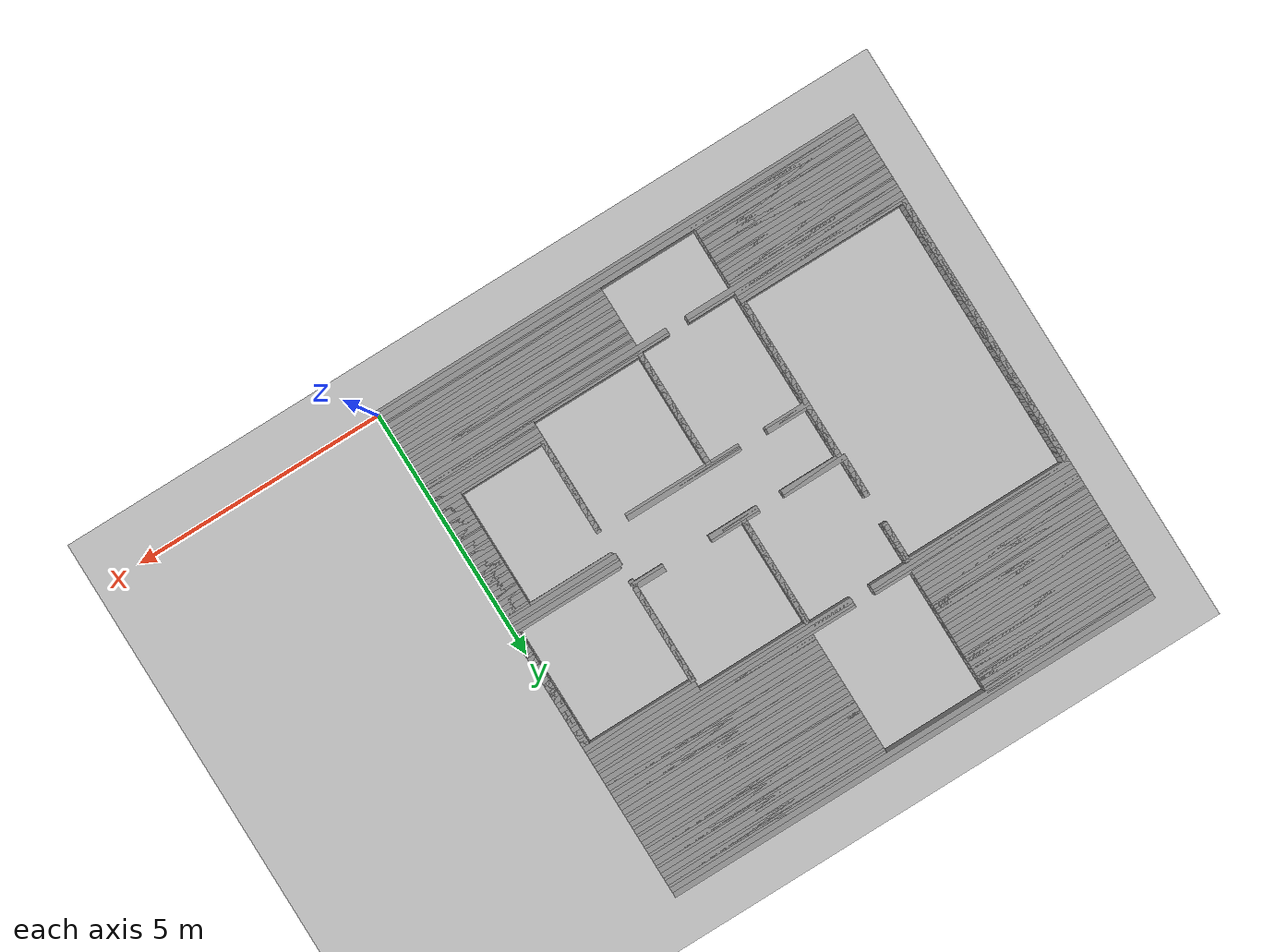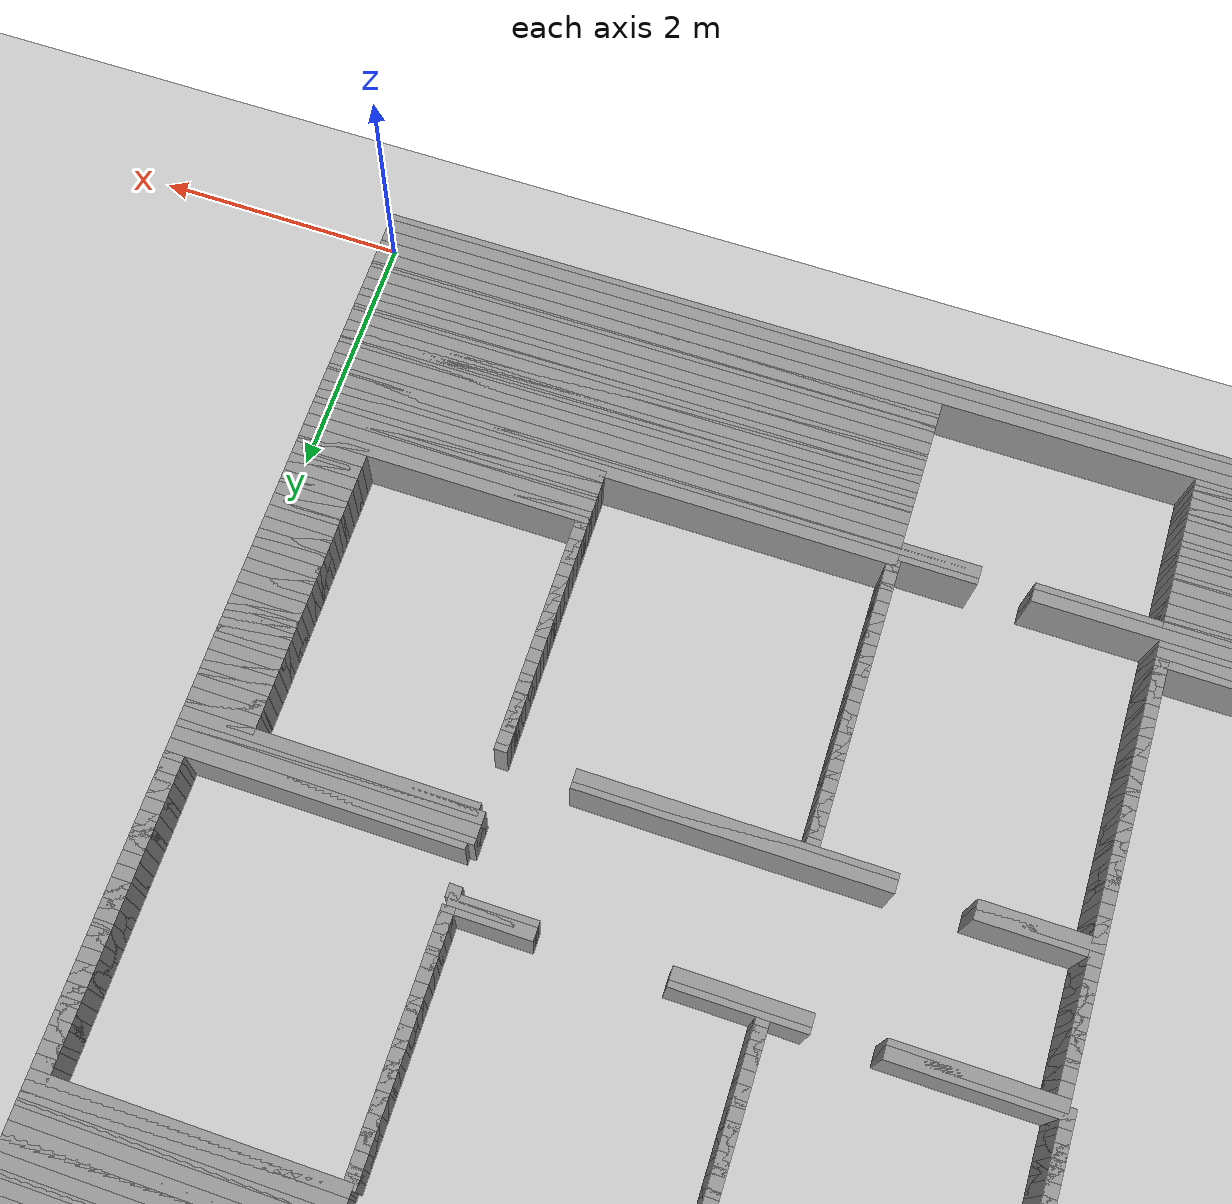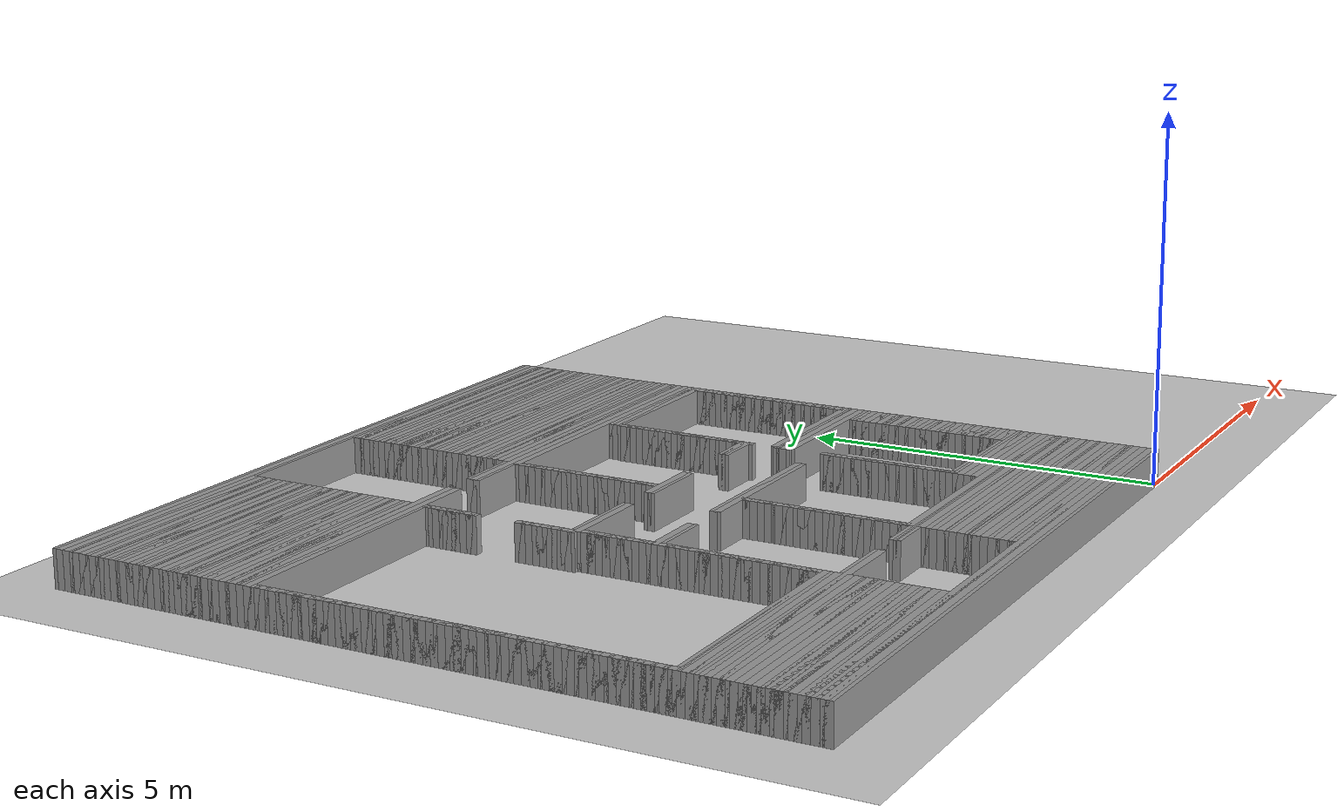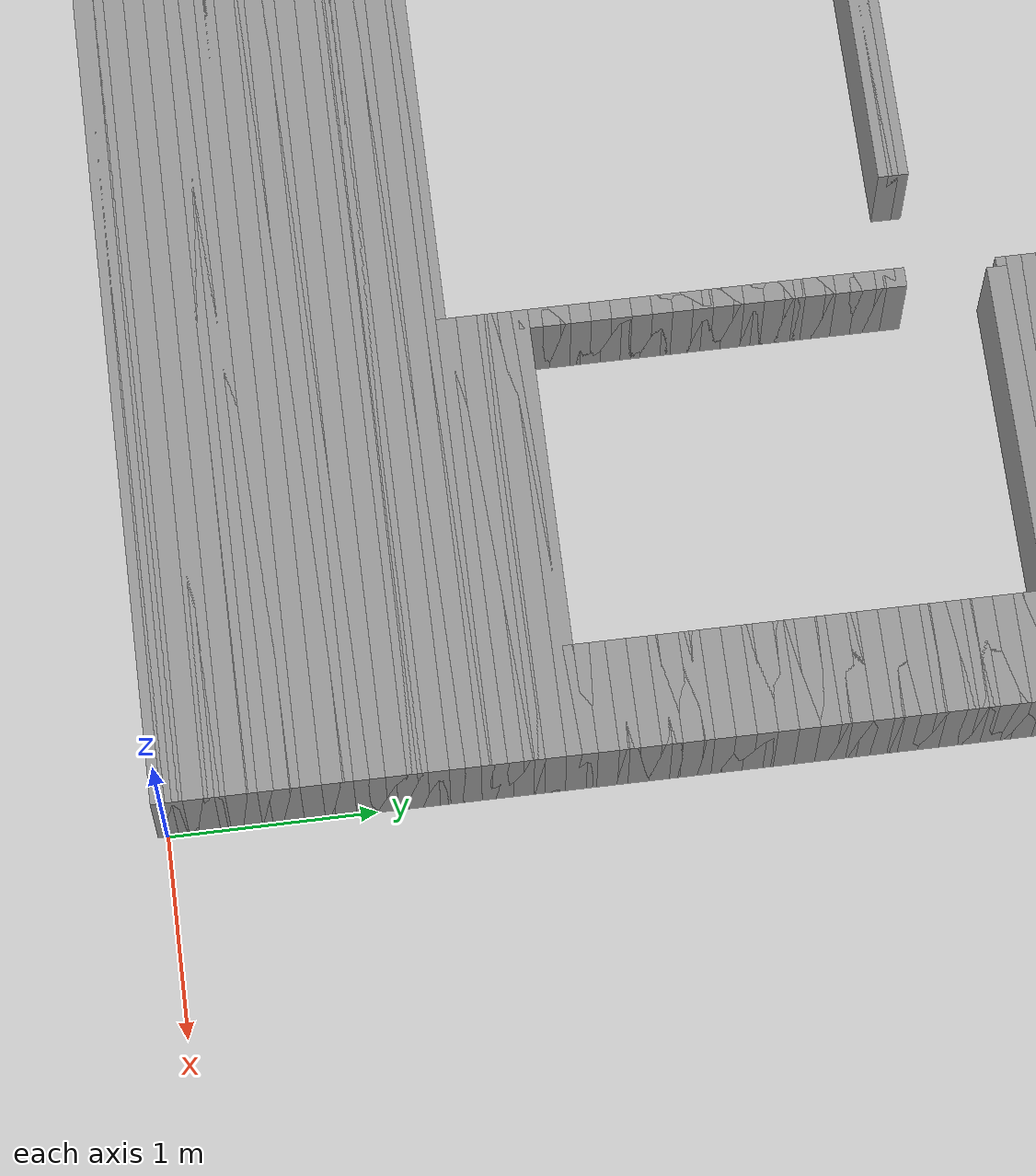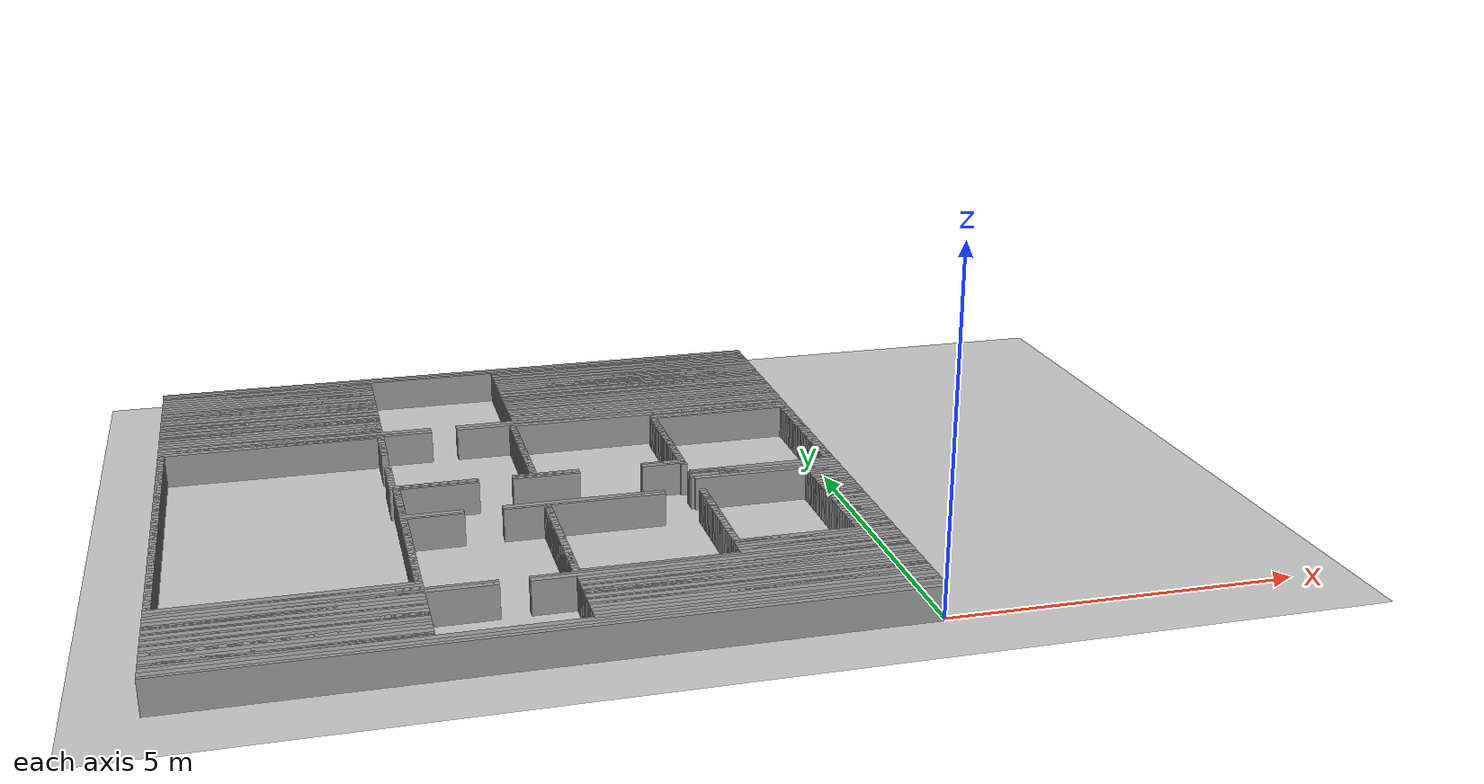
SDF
<?xml version='1.0' encoding='UTF-8'?>
<sdf version="1.6"><world name="GridMap"><include><uri>model://sun</uri></include><include><uri>model://ground_plane</uri></include><physics type="ode"><real_time_update_rate>1000.0</real_time_update_rate><max_step_size>0.001</max_step_size><real_time_factor>1</real_time_factor><ode><solver><type>quick</type><iters>150</iters><precon_iters>0</precon_iters><sor>1.4</sor><use_dynamic_moi_rescaling>1</use_dynamic_moi_rescaling></solver><constraints><cfm>0.00001</cfm><erp>0.2</erp><contact_max_correcting_vel>2000.000000</contact_max_correcting_vel><contact_surface_layer>0.01000</contact_surface_layer></constraints></ode></physics><model name="GridMap"><pose frame="">0 0 0 0 -0 0</pose><link name="Wall_(99.5,0.0)"><collision name="Wall_(99.5,0.0)_Collision"><geometry><box><size>9.950000000000001 0.1 0.5</size></box></geometry><pose frame="">-4.9750000000000005 0.0 0.25 0 -0 0</pose></collision><inertial><mass>0.5</mass><pose>0 0.01 0 0 0 0</pose><inertia><ixx>0.004</ixx><ixy>0.001</ixy><ixz>0</ixz><iyy>0.006</iyy><iyz>0</iyz><izz>0.007</izz></inertia></inertial><visual name="Wall_(99.5,0.0)_Visual"><geometry><box><size>9.950000000000001 0.1 0.5</size></box></geometry><pose frame="">-4.9750000000000005 0.0 0.25 0 -0 0</pose><material><script><uri>file://media/materials/scripts/gazebo.material</uri><name>Gazebo/Grey</name></script><ambient>1 1 1 1</ambient></material><meta><layer>0</layer></meta></visual><pose frame="">0 0 0 0 -0 0</pose></link><link name="Wall_(99.5,1.0)"><collision name="Wall_(99.5,1.0)_Collision"><geometry><box><size>9.950000000000001 0.1 0.5</size></box></geometry><pose frame="">-4.9750000000000005 0.05 0.25 0 -0 0</pose></collision><inertial><mass>0.5</mass><pose>0 0.01 0 0 0 0</pose><inertia><ixx>0.004</ixx><ixy>0.001</ixy><ixz>0</ixz><iyy>0.006</iyy><iyz>0</iyz><izz>0.007</izz></inertia></inertial><visual name="Wall_(99.5,1.0)_Visual"><geometry><box><size>9.950000000000001 0.1 0.5</size></box></geometry><pose frame="">-4.9750000000000005 0.05 0.25 0 -0 0</pose><material><script><uri>file://media/materials/scripts/gazebo.material</uri><name>Gazebo/Grey</name></script><ambient>1 1 1 1</ambient></material><meta><layer>0</layer></meta></visual><pose frame="">0 0 0 0 -0 0</pose></link><link name="Wall_(99.5,2.0)"><collision name="Wall_(99.5,2.0)_Collision"><geometry><box><size>9.950000000000001 0.1 0.5</size></box></geometry><pose frame="">-4.9750000000000005 0.1 0.25 0 -0 0</pose></collision><inertial><mass>0.5</mass><pose>0 0.01 0 0 0 0</pose><inertia><ixx>0.004</ixx><ixy>0.001</ixy><ixz>0</ixz><iyy>0.006</iyy><iyz>0</iyz><izz>0.007</izz></inertia></inertial><visual name="Wall_(99.5,2.0)_Visual"><geometry><box><size>9.950000000000001 0.1 0.5</size></box></geometry><pose frame="">-4.9750000000000005 0.1 0.25 0 -0 0</pose><material><script><uri>file://media/materials/scripts/gazebo.material</uri><name>Gazebo/Grey</name></script><ambient>1 1 1 1</ambient></material><meta><layer>0</layer></meta></visual><pose frame="">0 0 0 0 -0 0</pose></link><link name="Wall_(99.5,3.0)"><collision name="Wall_(99.5,3.0)_Collision"><geometry><box><size>9.950000000000001 0.1 0.5</size></box></geometry><pose frame="">-4.9750000000000005 0.15000000000000002 0.25 0 -0 0</pose></collision><inertial><mass>0.5</mass><pose>0 0.01 0 0 0 0</pose><inertia><ixx>0.004</ixx><ixy>0.001</ixy><ixz>0</ixz><iyy>0.006</iyy><iyz>0</iyz><izz>0.007</izz></inertia></inertial><visual name="Wall_(99.5,3.0)_Visual"><geometry><box><size>9.950000000000001 0.1 0.5</size></box></geometry><pose frame="">-4.9750000000000005 0.15000000000000002 0.25 0 -0 0</pose><material><script><uri>file://media/materials/scripts/gazebo.material</uri><name>Gazebo/Grey</name></script><ambient>1 1 1 1</ambient></material><meta><layer>0</layer></meta></visual><pose frame="">0 0 0 0 -0 0</pose></link><link name="Wall_(45.5,4.0)"><collision name="Wall_(45.5,4.0)_Collision"><geometry><box><size>4.55 0.1 0.5</size></box></geometry><pose frame="">-2.275 0.2 0.25 0 -0 0</pose></collision><inertial><mass>0.5</mass><pose>0 0.01 0 0 0 0</pose><inertia><ixx>0.004</ixx><ixy>0.001</ixy><ixz>0</ixz><iyy>0.006</iyy><iyz>0</iyz><izz>0.007</izz></inertia></inertial><visual name="Wall_(45.5,4.0)_Visual"><geometry><box><size>4.55 0.1 0.5</size></box></geometry><pose frame="">-2.275 0.2 0.25 0 -0 0</pose><material><script><uri>file://media/materials/scripts/gazebo.material</uri><name>Gazebo/Grey</name></script><ambient>1 1 1 1</ambient></material><meta><layer>0</layer></meta></visual><pose frame="">0 0 0 0 -0 0</pose></link><link name="Wall_(164.5,4.0)"><collision name="Wall_(164.5,4.0)_Collision"><geometry><box><size>3.45 0.1 0.5</size></box></geometry><pose frame="">-8.225 0.2 0.25 0 -0 0</pose></collision><inertial><mass>0.5</mass><pose>0 0.01 0 0 0 0</pose><inertia><ixx>0.004</ixx><ixy>0.001</ixy><ixz>0</ixz><iyy>0.006</iyy><iyz>0</iyz><izz>0.007</izz></inertia></inertial><visual name="Wall_(164.5,4.0)_Visual"><geometry><box><size>3.45 0.1 0.5</size></box></geometry><pose frame="">-8.225 0.2 0.25 0 -0 0</pose><material><script><uri>file://media/materials/scripts/gazebo.material</uri><name>Gazebo/Grey</name></script><ambient>1 1 1 1</ambient></material><meta><layer>0</layer></meta></visual><pose frame="">0 0 0 0 -0 0</pose></link><link name="Wall_(45.5,5.0)"><collision name="Wall_(45.5,5.0)_Collision"><geometry><box><size>4.55 0.1 0.5</size></box></geometry><pose frame="">-2.275 0.25 0.25 0 -0 0</pose></collision><inertial><mass>0.5</mass><pose>0 0.01 0 0 0 0</pose><inertia><ixx>0.004</ixx><ixy>0.001</ixy><ixz>0</ixz><iyy>0.006</iyy><iyz>0</iyz><izz>0.007</izz></inertia></inertial><visual name="Wall_(45.5,5.0)_Visual"><geometry><box><size>4.55 0.1 0.5</size></box></geometry><pose frame="">-2.275 0.25 0.25 0 -0 0</pose><material><script><uri>file://media/materials/scripts/gazebo.material</uri><name>Gazebo/Grey</name></script><ambient>1 1 1 1</ambient></material><meta><layer>0</layer></meta></visual><pose frame="">0 0 0 0 -0 0</pose></link><link name="Wall_(164.5,5.0)"><collision name="Wall_(164.5,5.0)_Collision"><geometry><box><size>3.45 0.1 0.5</size></box></geometry><pose frame="">-8.225 0.25 0.25 0 -0 0</pose></collision><inertial><mass>0.5</mass><pose>0 0.01 0 0 0 0</pose><inertia><ixx>0.004</ixx><ixy>0.001</ixy><ixz>0</ixz><iyy>0.006</iyy><iyz>0</iyz><izz>0.007</izz></inertia></inertial><visual name="Wall_(164.5,5.0)_Visual"><geometry><box><size>3.45 0.1 0.5</size></box></geometry><pose frame="">-8.225 0.25 0.25 0 -0 0</pose><material><script><uri>file://media/materials/scripts/gazebo.material</uri><name>Gazebo/Grey</name></script><ambient>1 1 1 1</ambient></material><meta><layer>0</layer></meta></visual><pose frame="">0 0 0 0 -0 0</pose></link><link name="Wall_(45.5,6.0)"><collision name="Wall_(45.5,6.0)_Collision"><geometry><box><size>4.55 0.1 0.5</size></box></geometry><pose frame="">-2.275 0.30000000000000004 0.25 0 -0 0</pose></collision><inertial><mass>0.5</mass><pose>0 0.01 0 0 0 0</pose><inertia><ixx>0.004</ixx><ixy>0.001</ixy><ixz>0</ixz><iyy>0.006</iyy><iyz>0</iyz><izz>0.007</izz></inertia></inertial><visual name="Wall_(45.5,6.0)_Visual"><geometry><box><size>4.55 0.1 0.5</size></box></geometry><pose frame="">-2.275 0.30000000000000004 0.25 0 -0 0</pose><material><script><uri>file://media/materials/scripts/gazebo.material</uri><name>Gazebo/Grey</name></script><ambient>1 1 1 1</ambient></material><meta><layer>0</layer></meta></visual><pose frame="">0 0 0 0 -0 0</pose></link><link name="Wall_(164.5,6.0)"><collision name="Wall_(164.5,6.0)_Collision"><geometry><box><size>3.45 0.1 0.5</size></box></geometry><pose frame="">-8.225 0.30000000000000004 0.25 0 -0 0</pose></collision><inertial><mass>0.5</mass><pose>0 0.01 0 0 0 0</pose><inertia><ixx>0.004</ixx><ixy>0.001</ixy><ixz>0</ixz><iyy>0.006</iyy><iyz>0</iyz><izz>0.007</izz></inertia></inertial><visual name="Wall_(164.5,6.0)_Visual"><geometry><box><size>3.45 0.1 0.5</size></box></geometry><pose frame="">-8.225 0.30000000000000004 0.25 0 -0 0</pose><material><script><uri>file://media/materials/scripts/gazebo.material</uri><name>Gazebo/Grey</name></script><ambient>1 1 1 1</ambient></material><meta><layer>0</layer></meta></visual><pose frame="">0 0 0 0 -0 0</pose></link><link name="Wall_(45.5,7.0)"><collision name="Wall_(45.5,7.0)_Collision"><geometry><box><size>4.55 0.1 0.5</size></box></geometry><pose frame="">-2.275 0.35000000000000003 0.25 0 -0 0</pose></collision><inertial><mass>0.5</mass><pose>0 0.01 0 0 0 0</pose><inertia><ixx>0.004</ixx><ixy>0.001</ixy><ixz>0</ixz><iyy>0.006</iyy><iyz>0</iyz><izz>0.007</izz></inertia></inertial><visual name="Wall_(45.5,7.0)_Visual"><geometry><box><size>4.55 0.1 0.5</size></box></geometry><pose frame="">-2.275 0.35000000000000003 0.25 0 -0 0</pose><material><script><uri>file://media/materials/scripts/gazebo.material</uri><name>Gazebo/Grey</name></script><ambient>1 1 1 1</ambient></material><meta><layer>0</layer></meta></visual><pose frame="">0 0 0 0 -0 0</pose></link><link name="Wall_(164.5,7.0)"><collision name="Wall_(164.5,7.0)_Collision"><geometry><box><size>3.45 0.1 0.5</size></box></geometry><pose frame="">-8.225 0.35000000000000003 0.25 0 -0 0</pose></collision><inertial><mass>0.5</mass><pose>0 0.01 0 0 0 0</pose><inertia><ixx>0.004</ixx><ixy>0.001</ixy><ixz>0</ixz><iyy>0.006</iyy><iyz>0</iyz><izz>0.007</izz></inertia></inertial><visual name="Wall_(164.5,7.0)_Visual"><geometry><box><size>3.45 0.1 0.5</size></box></geometry><pose frame="">-8.225 0.35000000000000003 0.25 0 -0 0</pose><material><script><uri>file://media/materials/scripts/gazebo.material</uri><name>Gazebo/Grey</name></script><ambient>1 1 1 1</ambient></material><meta><layer>0</layer></meta></visual><pose frame="">0 0 0 0 -0 0</pose></link><link name="Wall_(45.5,8.0)"><collision name="Wall_(45.5,8.0)_Collision"><geometry><box><size>4.55 0.1 0.5</size></box></geometry><pose frame="">-2.275 0.4 0.25 0 -0 0</pose></collision><inertial><mass>0.5</mass><pose>0 0.01 0 0 0 0</pose><inertia><ixx>0.004</ixx><ixy>0.001</ixy><ixz>0</ixz><iyy>0.006</iyy><iyz>0</iyz><izz>0.007</izz></inertia></inertial><visual name="Wall_(45.5,8.0)_Visual"><geometry><box><size>4.55 0.1 0.5</size></box></geometry><pose frame="">-2.275 0.4 0.25 0 -0 0</pose><material><script><uri>file://media/materials/scripts/gazebo.material</uri><name>Gazebo/Grey</name></script><ambient>1 1 1 1</ambient></material><meta><layer>0</layer></meta></visual><pose frame="">0 0 0 0 -0 0</pose></link><link name="Wall_(164.5,8.0)"><collision name="Wall_(164.5,8.0)_Collision"><geometry><box><size>3.45 0.1 0.5</size></box></geometry><pose frame="">-8.225 0.4 0.25 0 -0 0</pose></collision><inertial><mass>0.5</mass><pose>0 0.01 0 0 0 0</pose><inertia><ixx>0.004</ixx><ixy>0.001</ixy><ixz>0</ixz><iyy>0.006</iyy><iyz>0</iyz><izz>0.007</izz></inertia></inertial><visual name="Wall_(164.5,8.0)_Visual"><geometry><box><size>3.45 0.1 0.5</size></box></geometry><pose frame="">-8.225 0.4 0.25 0 -0 0</pose><material><script><uri>file://media/materials/scripts/gazebo.material</uri><name>Gazebo/Grey</name></script><ambient>1 1 1 1</ambient></material><meta><layer>0</layer></meta></visual><pose frame="">0 0 0 0 -0 0</pose></link><link name="Wall_(45.5,9.0)"><collision name="Wall_(45.5,9.0)_Collision"><geometry><box><size>4.55 0.1 0.5</size></box></geometry><pose frame="">-2.275 0.45 0.25 0 -0 0</pose></collision><inertial><mass>0.5</mass><pose>0 0.01 0 0 0 0</pose><inertia><ixx>0.004</ixx><ixy>0.001</ixy><ixz>0</ixz><iyy>0.006</iyy><iyz>0</iyz><izz>0.007</izz></inertia></inertial><visual name="Wall_(45.5,9.0)_Visual"><geometry><box><size>4.55 0.1 0.5</size></box></geometry><pose frame="">-2.275 0.45 0.25 0 -0 0</pose><material><script><uri>file://media/materials/scripts/gazebo.material</uri><name>Gazebo/Grey</name></script><ambient>1 1 1 1</ambient></material><meta><layer>0</layer></meta></visual><pose frame="">0 0 0 0 -0 0</pose></link><link name="Wall_(164.5,9.0)"><collision name="Wall_(164.5,9.0)_Collision"><geometry><box><size>3.45 0.1 0.5</size></box></geometry><pose frame="">-8.225 0.45 0.25 0 -0 0</pose></collision><inertial><mass>0.5</mass><pose>0 0.01 0 0 0 0</pose><inertia><ixx>0.004</ixx><ixy>0.001</ixy><ixz>0</ixz><iyy>0.006</iyy><iyz>0</iyz><izz>0.007</izz></inertia></inertial><visual name="Wall_(164.5,9.0)_Visual"><geometry><box><size>3.45 0.1 0.5</size></box></geometry><pose frame="">-8.225 0.45 0.25 0 -0 0</pose><material><script><uri>file://media/materials/scripts/gazebo.material</uri><name>Gazebo/Grey</name></script><ambient>1 1 1 1</ambient></material><meta><layer>0</layer></meta></visual><pose frame="">0 0 0 0 -0 0</pose></link><link name="Wall_(45.5,10.0)"><collision name="Wall_(45.5,10.0)_Collision"><geometry><box><size>4.55 0.1 0.5</size></box></geometry><pose frame="">-2.275 0.5 0.25 0 -0 0</pose></collision><inertial><mass>0.5</mass><pose>0 0.01 0 0 0 0</pose><inertia><ixx>0.004</ixx><ixy>0.001</ixy><ixz>0</ixz><iyy>0.006</iyy><iyz>0</iyz><izz>0.007</izz></inertia></inertial><visual name="Wall_(45.5,10.0)_Visual"><geometry><box><size>4.55 0.1 0.5</size></box></geometry><pose frame="">-2.275 0.5 0.25 0 -0 0</pose><material><script><uri>file://media/materials/scripts/gazebo.material</uri><name>Gazebo/Grey</name></script><ambient>1 1 1 1</ambient></material><meta><layer>0</layer></meta></visual><pose frame="">0 0 0 0 -0 0</pose></link><link name="Wall_(164.5,10.0)"><collision name="Wall_(164.5,10.0)_Collision"><geometry><box><size>3.45 0.1 0.5</size></box></geometry><pose frame="">-8.225 0.5 0.25 0 -0 0</pose></collision><inertial><mass>0.5</mass><pose>0 0.01 0 0 0 0</pose><inertia><ixx>0.004</ixx><ixy>0.001</ixy><ixz>0</ixz><iyy>0.006</iyy><iyz>0</iyz><izz>0.007</izz></inertia></inertial><visual name="Wall_(164.5,10.0)_Visual"><geometry><box><size>3.45 0.1 0.5</size></box></geometry><pose frame="">-8.225 0.5 0.25 0 -0 0</pose><material><script><uri>file://media/materials/scripts/gazebo.material</uri><name>Gazebo/Grey</name></script><ambient>1 1 1 1</ambient></material><meta><layer>0</layer></meta></visual><pose frame="">0 0 0 0 -0 0</pose></link><link name="Wall_(45.5,11.0)"><collision name="Wall_(45.5,11.0)_Collision"><geometry><box><size>4.55 0.1 0.5</size></box></geometry><pose frame="">-2.275 0.55 0.25 0 -0 0</pose></collision><inertial><mass>0.5</mass><pose>0 0.01 0 0 0 0</pose><inertia><ixx>0.004</ixx><ixy>0.001</ixy><ixz>0</ixz><iyy>0.006</iyy><iyz>0</iyz><izz>0.007</izz></inertia></inertial><visual name="Wall_(45.5,11.0)_Visual"><geometry><box><size>4.55 0.1 0.5</size></box></geometry><pose frame="">-2.275 0.55 0.25 0 -0 0</pose><material><script><uri>file://media/materials/scripts/gazebo.material</uri><name>Gazebo/Grey</name></script><ambient>1 1 1 1</ambient></material><meta><layer>0</layer></meta></visual><pose frame="">0 0 0 0 -0 0</pose></link><link name="Wall_(164.5,11.0)"><collision name="Wall_(164.5,11.0)_Collision"><geometry><box><size>3.45 0.1 0.5</size></box></geometry><pose frame="">-8.225 0.55 0.25 0 -0 0</pose></collision><inertial><mass>0.5</mass><pose>0 0.01 0 0 0 0</pose><inertia><ixx>0.004</ixx><ixy>0.001</ixy><ixz>0</ixz><iyy>0.006</iyy><iyz>0</iyz><izz>0.007</izz></inertia></inertial><visual name="Wall_(164.5,11.0)_Visual"><geometry><box><size>3.45 0.1 0.5</size></box></geometry><pose frame="">-8.225 0.55 0.25 0 -0 0</pose><material><script><uri>file://media/materials/scripts/gazebo.material</uri><name>Gazebo/Grey</name></script><ambient>1 1 1 1</ambient></material><meta><layer>0</layer></meta></visual><pose frame="">0 0 0 0 -0 0</pose></link><link name="Wall_(45.5,12.0)"><collision name="Wall_(45.5,12.0)_Collision"><geometry><box><size>4.55 0.1 0.5</size></box></geometry><pose frame="">-2.275 0.6000000000000001 0.25 0 -0 0</pose></collision><inertial><mass>0.5</mass><pose>0 0.01 0 0 0 0</pose><inertia><ixx>0.004</ixx><ixy>0.001</ixy><ixz>0</ixz><iyy>0.006</iyy><iyz>0</iyz><izz>0.007</izz></inertia></inertial><visual name="Wall_(45.5,12.0)_Visual"><geometry><box><size>4.55 0.1 0.5</size></box></geometry><pose frame="">-2.275 0.6000000000000001 0.25 0 -0 0</pose><material><script><uri>file://media/materials/scripts/gazebo.material</uri><name>Gazebo/Grey</name></script><ambient>1 1 1 1</ambient></material><meta><layer>0</layer></meta></visual><pose frame="">0 0 0 0 -0 0</pose></link><link name="Wall_(164.5,12.0)"><collision name="Wall_(164.5,12.0)_Collision"><geometry><box><size>3.45 0.1 0.5</size></box></geometry><pose frame="">-8.225 0.6000000000000001 0.25 0 -0 0</pose></collision><inertial><mass>0.5</mass><pose>0 0.01 0 0 0 0</pose><inertia><ixx>0.004</ixx><ixy>0.001</ixy><ixz>0</ixz><iyy>0.006</iyy><iyz>0</iyz><izz>0.007</izz></inertia></inertial><visual name="Wall_(164.5,12.0)_Visual"><geometry><box><size>3.45 0.1 0.5</size></box></geometry><pose frame="">-8.225 0.6000000000000001 0.25 0 -0 0</pose><material><script><uri>file://media/materials/scripts/gazebo.material</uri><name>Gazebo/Grey</name></script><ambient>1 1 1 1</ambient></material><meta><layer>0</layer></meta></visual><pose frame="">0 0 0 0 -0 0</pose></link><link name="Wall_(45.5,13.0)"><collision name="Wall_(45.5,13.0)_Collision"><geometry><box><size>4.55 0.1 0.5</size></box></geometry><pose frame="">-2.275 0.65 0.25 0 -0 0</pose></collision><inertial><mass>0.5</mass><pose>0 0.01 0 0 0 0</pose><inertia><ixx>0.004</ixx><ixy>0.001</ixy><ixz>0</ixz><iyy>0.006</iyy><iyz>0</iyz><izz>0.007</izz></inertia></inertial><visual name="Wall_(45.5,13.0)_Visual"><geometry><box><size>4.55 0.1 0.5</size></box></geometry><pose frame="">-2.275 0.65 0.25 0 -0 0</pose><material><script><uri>file://media/materials/scripts/gazebo.material</uri><name>Gazebo/Grey</name></script><ambient>1 1 1 1</ambient></material><meta><layer>0</layer></meta></visual><pose frame="">0 0 0 0 -0 0</pose></link><link name="Wall_(164.5,13.0)"><collision name="Wall_(164.5,13.0)_Collision"><geometry><box><size>3.45 0.1 0.5</size></box></geometry><pose frame="">-8.225 0.65 0.25 0 -0 0</pose></collision><inertial><mass>0.5</mass><pose>0 0.01 0 0 0 0</pose><inertia><ixx>0.004</ixx><ixy>0.001</ixy><ixz>0</ixz><iyy>0.006</iyy><iyz>0</iyz><izz>0.007</izz></inertia></inertial><visual name="Wall_(164.5,13.0)_Visual"><geometry><box><size>3.45 0.1 0.5</size></box></geometry><pose frame="">-8.225 0.65 0.25 0 -0 0</pose><material><script><uri>file://media/materials/scripts/gazebo.material</uri><name>Gazebo/Grey</name></script><ambient>1 1 1 1</ambient></material><meta><layer>0</layer></meta></visual><pose frame="">0 0 0 0 -0 0</pose></link><link name="Wall_(45.5,14.0)"><collision name="Wall_(45.5,14.0)_Collision"><geometry><box><size>4.55 0.1 0.5</size></box></geometry><pose frame="">-2.275 0.7000000000000001 0.25 0 -0 0</pose></collision><inertial><mass>0.5</mass><pose>0 0.01 0 0 0 0</pose><inertia><ixx>0.004</ixx><ixy>0.001</ixy><ixz>0</ixz><iyy>0.006</iyy><iyz>0</iyz><izz>0.007</izz></inertia></inertial><visual name="Wall_(45.5,14.0)_Visual"><geometry><box><size>4.55 0.1 0.5</size></box></geometry><pose frame="">-2.275 0.7000000000000001 0.25 0 -0 0</pose><material><script><uri>file://media/materials/scripts/gazebo.material</uri><name>Gazebo/Grey</name></script><ambient>1 1 1 1</ambient></material><meta><layer>0</layer></meta></visual><pose frame="">0 0 0 0 -0 0</pose></link><link name="Wall_(164.5,14.0)"><collision name="Wall_(164.5,14.0)_Collision"><geometry><box><size>3.45 0.1 0.5</size></box></geometry><pose frame="">-8.225 0.7000000000000001 0.25 0 -0 0</pose></collision><inertial><mass>0.5</mass><pose>0 0.01 0 0 0 0</pose><inertia><ixx>0.004</ixx><ixy>0.001</ixy><ixz>0</ixz><iyy>0.006</iyy><iyz>0</iyz><izz>0.007</izz></inertia></inertial><visual name="Wall_(164.5,14.0)_Visual"><geometry><box><size>3.45 0.1 0.5</size></box></geometry><pose frame="">-8.225 0.7000000000000001 0.25 0 -0 0</pose><material><script><uri>file://media/materials/scripts/gazebo.material</uri><name>Gazebo/Grey</name></script><ambient>1 1 1 1</ambient></material><meta><layer>0</layer></meta></visual><pose frame="">0 0 0 0 -0 0</pose></link><link name="Wall_(45.5,15.0)"><collision name="Wall_(45.5,15.0)_Collision"><geometry><box><size>4.55 0.1 0.5</size></box></geometry><pose frame="">-2.275 0.75 0.25 0 -0 0</pose></collision><inertial><mass>0.5</mass><pose>0 0.01 0 0 0 0</pose><inertia><ixx>0.004</ixx><ixy>0.001</ixy><ixz>0</ixz><iyy>0.006</iyy><iyz>0</iyz><izz>0.007</izz></inertia></inertial><visual name="Wall_(45.5,15.0)_Visual"><geometry><box><size>4.55 0.1 0.5</size></box></geometry><pose frame="">-2.275 0.75 0.25 0 -0 0</pose><material><script><uri>file://media/materials/scripts/gazebo.material</uri><name>Gazebo/Grey</name></script><ambient>1 1 1 1</ambient></material><meta><layer>0</layer></meta></visual><pose frame="">0 0 0 0 -0 0</pose></link><link name="Wall_(164.5,15.0)"><collision name="Wall_(164.5,15.0)_Collision"><geometry><box><size>3.45 0.1 0.5</size></box></geometry><pose frame="">-8.225 0.75 0.25 0 -0 0</pose></collision><inertial><mass>0.5</mass><pose>0 0.01 0 0 0 0</pose><inertia><ixx>0.004</ixx><ixy>0.001</ixy><ixz>0</ixz><iyy>0.006</iyy><iyz>0</iyz><izz>0.007</izz></inertia></inertial><visual name="Wall_(164.5,15.0)_Visual"><geometry><box><size>3.45 0.1 0.5</size></box></geometry><pose frame="">-8.225 0.75 0.25 0 -0 0</pose><material><script><uri>file://media/materials/scripts/gazebo.material</uri><name>Gazebo/Grey</name></script><ambient>1 1 1 1</ambient></material><meta><layer>0</layer></meta></visual><pose frame="">0 0 0 0 -0 0</pose></link><link name="Wall_(45.5,16.0)"><collision name="Wall_(45.5,16.0)_Collision"><geometry><box><size>4.55 0.1 0.5</size></box></geometry><pose frame="">-2.275 0.8 0.25 0 -0 0</pose></collision><inertial><mass>0.5</mass><pose>0 0.01 0 0 0 0</pose><inertia><ixx>0.004</ixx><ixy>0.001</ixy><ixz>0</ixz><iyy>0.006</iyy><iyz>0</iyz><izz>0.007</izz></inertia></inertial><visual name="Wall_(45.5,16.0)_Visual"><geometry><box><size>4.55 0.1 0.5</size></box></geometry><pose frame="">-2.275 0.8 0.25 0 -0 0</pose><material><script><uri>file://media/materials/scripts/gazebo.material</uri><name>Gazebo/Grey</name></script><ambient>1 1 1 1</ambient></material><meta><layer>0</layer></meta></visual><pose frame="">0 0 0 0 -0 0</pose></link><link name="Wall_(164.5,16.0)"><collision name="Wall_(164.5,16.0)_Collision"><geometry><box><size>3.45 0.1 0.5</size></box></geometry><pose frame="">-8.225 0.8 0.25 0 -0 0</pose></collision><inertial><mass>0.5</mass><pose>0 0.01 0 0 0 0</pose><inertia><ixx>0.004</ixx><ixy>0.001</ixy><ixz>0</ixz><iyy>0.006</iyy><iyz>0</iyz><izz>0.007</izz></inertia></inertial><visual name="Wall_(164.5,16.0)_Visual"><geometry><box><size>3.45 0.1 0.5</size></box></geometry><pose frame="">-8.225 0.8 0.25 0 -0 0</pose><material><script><uri>file://media/materials/scripts/gazebo.material</uri><name>Gazebo/Grey</name></script><ambient>1 1 1 1</ambient></material><meta><layer>0</layer></meta></visual><pose frame="">0 0 0 0 -0 0</pose></link><link name="Wall_(45.5,17.0)"><collision name="Wall_(45.5,17.0)_Collision"><geometry><box><size>4.55 0.1 0.5</size></box></geometry><pose frame="">-2.275 0.8500000000000001 0.25 0 -0 0</pose></collision><inertial><mass>0.5</mass><pose>0 0.01 0 0 0 0</pose><inertia><ixx>0.004</ixx><ixy>0.001</ixy><ixz>0</ixz><iyy>0.006</iyy><iyz>0</iyz><izz>0.007</izz></inertia></inertial><visual name="Wall_(45.5,17.0)_Visual"><geometry><box><size>4.55 0.1 0.5</size></box></geometry><pose frame="">-2.275 0.8500000000000001 0.25 0 -0 0</pose><material><script><uri>file://media/materials/scripts/gazebo.material</uri><name>Gazebo/Grey</name></script><ambient>1 1 1 1</ambient></material><meta><layer>0</layer></meta></visual><pose frame="">0 0 0 0 -0 0</pose></link><link name="Wall_(164.5,17.0)"><collision name="Wall_(164.5,17.0)_Collision"><geometry><box><size>3.45 0.1 0.5</size></box></geometry><pose frame="">-8.225 0.8500000000000001 0.25 0 -0 0</pose></collision><inertial><mass>0.5</mass><pose>0 0.01 0 0 0 0</pose><inertia><ixx>0.004</ixx><ixy>0.001</ixy><ixz>0</ixz><iyy>0.006</iyy><iyz>0</iyz><izz>0.007</izz></inertia></inertial><visual name="Wall_(164.5,17.0)_Visual"><geometry><box><size>3.45 0.1 0.5</size></box></geometry><pose frame="">-8.225 0.8500000000000001 0.25 0 -0 0</pose><material><script><uri>file://media/materials/scripts/gazebo.material</uri><name>Gazebo/Grey</name></script><ambient>1 1 1 1</ambient></material><meta><layer>0</layer></meta></visual><pose frame="">0 0 0 0 -0 0</pose></link><link name="Wall_(45.5,18.0)"><collision name="Wall_(45.5,18.0)_Collision"><geometry><box><size>4.55 0.1 0.5</size></box></geometry><pose frame="">-2.275 0.9 0.25 0 -0 0</pose></collision><inertial><mass>0.5</mass><pose>0 0.01 0 0 0 0</pose><inertia><ixx>0.004</ixx><ixy>0.001</ixy><ixz>0</ixz><iyy>0.006</iyy><iyz>0</iyz><izz>0.007</izz></inertia></inertial><visual name="Wall_(45.5,18.0)_Visual"><geometry><box><size>4.55 0.1 0.5</size></box></geometry><pose frame="">-2.275 0.9 0.25 0 -0 0</pose><material><script><uri>file://media/materials/scripts/gazebo.material</uri><name>Gazebo/Grey</name></script><ambient>1 1 1 1</ambient></material><meta><layer>0</layer></meta></visual><pose frame="">0 0 0 0 -0 0</pose></link><link name="Wall_(164.5,18.0)"><collision name="Wall_(164.5,18.0)_Collision"><geometry><box><size>3.45 0.1 0.5</size></box></geometry><pose frame="">-8.225 0.9 0.25 0 -0 0</pose></collision><inertial><mass>0.5</mass><pose>0 0.01 0 0 0 0</pose><inertia><ixx>0.004</ixx><ixy>0.001</ixy><ixz>0</ixz><iyy>0.006</iyy><iyz>0</iyz><izz>0.007</izz></inertia></inertial><visual name="Wall_(164.5,18.0)_Visual"><geometry><box><size>3.45 0.1 0.5</size></box></geometry><pose frame="">-8.225 0.9 0.25 0 -0 0</pose><material><script><uri>file://media/materials/scripts/gazebo.material</uri><name>Gazebo/Grey</name></script><ambient>1 1 1 1</ambient></material><meta><layer>0</layer></meta></visual><pose frame="">0 0 0 0 -0 0</pose></link><link name="Wall_(45.5,19.0)"><collision name="Wall_(45.5,19.0)_Collision"><geometry><box><size>4.55 0.1 0.5</size></box></geometry><pose frame="">-2.275 0.9500000000000001 0.25 0 -0 0</pose></collision><inertial><mass>0.5</mass><pose>0 0.01 0 0 0 0</pose><inertia><ixx>0.004</ixx><ixy>0.001</ixy><ixz>0</ixz><iyy>0.006</iyy><iyz>0</iyz><izz>0.007</izz></inertia></inertial><visual name="Wall_(45.5,19.0)_Visual"><geometry><box><size>4.55 0.1 0.5</size></box></geometry><pose frame="">-2.275 0.9500000000000001 0.25 0 -0 0</pose><material><script><uri>file://media/materials/scripts/gazebo.material</uri><name>Gazebo/Grey</name></script><ambient>1 1 1 1</ambient></material><meta><layer>0</layer></meta></visual><pose frame="">0 0 0 0 -0 0</pose></link><link name="Wall_(164.5,19.0)"><collision name="Wall_(164.5,19.0)_Collision"><geometry><box><size>3.45 0.1 0.5</size></box></geometry><pose frame="">-8.225 0.9500000000000001 0.25 0 -0 0</pose></collision><inertial><mass>0.5</mass><pose>0 0.01 0 0 0 0</pose><inertia><ixx>0.004</ixx><ixy>0.001</ixy><ixz>0</ixz><iyy>0.006</iyy><iyz>0</iyz><izz>0.007</izz></inertia></inertial><visual name="Wall_(164.5,19.0)_Visual"><geometry><box><size>3.45 0.1 0.5</size></box></geometry><pose frame="">-8.225 0.9500000000000001 0.25 0 -0 0</pose><material><script><uri>file://media/materials/scripts/gazebo.material</uri><name>Gazebo/Grey</name></script><ambient>1 1 1 1</ambient></material><meta><layer>0</layer></meta></visual><pose frame="">0 0 0 0 -0 0</pose></link><link name="Wall_(45.5,20.0)"><collision name="Wall_(45.5,20.0)_Collision"><geometry><box><size>4.55 0.1 0.5</size></box></geometry><pose frame="">-2.275 1.0 0.25 0 -0 0</pose></collision><inertial><mass>0.5</mass><pose>0 0.01 0 0 0 0</pose><inertia><ixx>0.004</ixx><ixy>0.001</ixy><ixz>0</ixz><iyy>0.006</iyy><iyz>0</iyz><izz>0.007</izz></inertia></inertial><visual name="Wall_(45.5,20.0)_Visual"><geometry><box><size>4.55 0.1 0.5</size></box></geometry><pose frame="">-2.275 1.0 0.25 0 -0 0</pose><material><script><uri>file://media/materials/scripts/gazebo.material</uri><name>Gazebo/Grey</name></script><ambient>1 1 1 1</ambient></material><meta><layer>0</layer></meta></visual><pose frame="">0 0 0 0 -0 0</pose></link><link name="Wall_(164.5,20.0)"><collision name="Wall_(164.5,20.0)_Collision"><geometry><box><size>3.45 0.1 0.5</size></box></geometry><pose frame="">-8.225 1.0 0.25 0 -0 0</pose></collision><inertial><mass>0.5</mass><pose>0 0.01 0 0 0 0</pose><inertia><ixx>0.004</ixx><ixy>0.001</ixy><ixz>0</ixz><iyy>0.006</iyy><iyz>0</iyz><izz>0.007</izz></inertia></inertial><visual name="Wall_(164.5,20.0)_Visual"><geometry><box><size>3.45 0.1 0.5</size></box></geometry><pose frame="">-8.225 1.0 0.25 0 -0 0</pose><material><script><uri>file://media/materials/scripts/gazebo.material</uri><name>Gazebo/Grey</name></script><ambient>1 1 1 1</ambient></material><meta><layer>0</layer></meta></visual><pose frame="">0 0 0 0 -0 0</pose></link><link name="Wall_(45.5,21.0)"><collision name="Wall_(45.5,21.0)_Collision"><geometry><box><size>4.55 0.1 0.5</size></box></geometry><pose frame="">-2.275 1.05 0.25 0 -0 0</pose></collision><inertial><mass>0.5</mass><pose>0 0.01 0 0 0 0</pose><inertia><ixx>0.004</ixx><ixy>0.001</ixy><ixz>0</ixz><iyy>0.006</iyy><iyz>0</iyz><izz>0.007</izz></inertia></inertial><visual name="Wall_(45.5,21.0)_Visual"><geometry><box><size>4.55 0.1 0.5</size></box></geometry><pose frame="">-2.275 1.05 0.25 0 -0 0</pose><material><script><uri>file://media/materials/scripts/gazebo.material</uri><name>Gazebo/Grey</name></script><ambient>1 1 1 1</ambient></material><meta><layer>0</layer></meta></visual><pose frame="">0 0 0 0 -0 0</pose></link><link name="Wall_(164.5,21.0)"><collision name="Wall_(164.5,21.0)_Collision"><geometry><box><size>3.45 0.1 0.5</size></box></geometry><pose frame="">-8.225 1.05 0.25 0 -0 0</pose></collision><inertial><mass>0.5</mass><pose>0 0.01 0 0 0 0</pose><inertia><ixx>0.004</ixx><ixy>0.001</ixy><ixz>0</ixz><iyy>0.006</iyy><iyz>0</iyz><izz>0.007</izz></inertia></inertial><visual name="Wall_(164.5,21.0)_Visual"><geometry><box><size>3.45 0.1 0.5</size></box></geometry><pose frame="">-8.225 1.05 0.25 0 -0 0</pose><material><script><uri>file://media/materials/scripts/gazebo.material</uri><name>Gazebo/Grey</name></script><ambient>1 1 1 1</ambient></material><meta><layer>0</layer></meta></visual><pose frame="">0 0 0 0 -0 0</pose></link><link name="Wall_(45.5,22.0)"><collision name="Wall_(45.5,22.0)_Collision"><geometry><box><size>4.55 0.1 0.5</size></box></geometry><pose frame="">-2.275 1.1 0.25 0 -0 0</pose></collision><inertial><mass>0.5</mass><pose>0 0.01 0 0 0 0</pose><inertia><ixx>0.004</ixx><ixy>0.001</ixy><ixz>0</ixz><iyy>0.006</iyy><iyz>0</iyz><izz>0.007</izz></inertia></inertial><visual name="Wall_(45.5,22.0)_Visual"><geometry><box><size>4.55 0.1 0.5</size></box></geometry><pose frame="">-2.275 1.1 0.25 0 -0 0</pose><material><script><uri>file://media/materials/scripts/gazebo.material</uri><name>Gazebo/Grey</name></script><ambient>1 1 1 1</ambient></material><meta><layer>0</layer></meta></visual><pose frame="">0 0 0 0 -0 0</pose></link><link name="Wall_(164.5,22.0)"><collision name="Wall_(164.5,22.0)_Collision"><geometry><box><size>3.45 0.1 0.5</size></box></geometry><pose frame="">-8.225 1.1 0.25 0 -0 0</pose></collision><inertial><mass>0.5</mass><pose>0 0.01 0 0 0 0</pose><inertia><ixx>0.004</ixx><ixy>0.001</ixy><ixz>0</ixz><iyy>0.006</iyy><iyz>0</iyz><izz>0.007</izz></inertia></inertial><visual name="Wall_(164.5,22.0)_Visual"><geometry><box><size>3.45 0.1 0.5</size></box></geometry><pose frame="">-8.225 1.1 0.25 0 -0 0</pose><material><script><uri>file://media/materials/scripts/gazebo.material</uri><name>Gazebo/Grey</name></script><ambient>1 1 1 1</ambient></material><meta><layer>0</layer></meta></visual><pose frame="">0 0 0 0 -0 0</pose></link><link name="Wall_(45.5,23.0)"><collision name="Wall_(45.5,23.0)_Collision"><geometry><box><size>4.55 0.1 0.5</size></box></geometry><pose frame="">-2.275 1.1500000000000001 0.25 0 -0 0</pose></collision><inertial><mass>0.5</mass><pose>0 0.01 0 0 0 0</pose><inertia><ixx>0.004</ixx><ixy>0.001</ixy><ixz>0</ixz><iyy>0.006</iyy><iyz>0</iyz><izz>0.007</izz></inertia></inertial><visual name="Wall_(45.5,23.0)_Visual"><geometry><box><size>4.55 0.1 0.5</size></box></geometry><pose frame="">-2.275 1.1500000000000001 0.25 0 -0 0</pose><material><script><uri>file://media/materials/scripts/gazebo.material</uri><name>Gazebo/Grey</name></script><ambient>1 1 1 1</ambient></material><meta><layer>0</layer></meta></visual><pose frame="">0 0 0 0 -0 0</pose></link><link name="Wall_(164.5,23.0)"><collision name="Wall_(164.5,23.0)_Collision"><geometry><box><size>3.45 0.1 0.5</size></box></geometry><pose frame="">-8.225 1.1500000000000001 0.25 0 -0 0</pose></collision><inertial><mass>0.5</mass><pose>0 0.01 0 0 0 0</pose><inertia><ixx>0.004</ixx><ixy>0.001</ixy><ixz>0</ixz><iyy>0.006</iyy><iyz>0</iyz><izz>0.007</izz></inertia></inertial><visual name="Wall_(164.5,23.0)_Visual"><geometry><box><size>3.45 0.1 0.5</size></box></geometry><pose frame="">-8.225 1.1500000000000001 0.25 0 -0 0</pose><material><script><uri>file://media/materials/scripts/gazebo.material</uri><name>Gazebo/Grey</name></script><ambient>1 1 1 1</ambient></material><meta><layer>0</layer></meta></visual><pose frame="">0 0 0 0 -0 0</pose></link><link name="Wall_(45.5,24.0)"><collision name="Wall_(45.5,24.0)_Collision"><geometry><box><size>4.55 0.1 0.5</size></box></geometry><pose frame="">-2.275 1.2000000000000002 0.25 0 -0 0</pose></collision><inertial><mass>0.5</mass><pose>0 0.01 0 0 0 0</pose><inertia><ixx>0.004</ixx><ixy>0.001</ixy><ixz>0</ixz><iyy>0.006</iyy><iyz>0</iyz><izz>0.007</izz></inertia></inertial><visual name="Wall_(45.5,24.0)_Visual"><geometry><box><size>4.55 0.1 0.5</size></box></geometry><pose frame="">-2.275 1.2000000000000002 0.25 0 -0 0</pose><material><script><uri>file://media/materials/scripts/gazebo.material</uri><name>Gazebo/Grey</name></script><ambient>1 1 1 1</ambient></material><meta><layer>0</layer></meta></visual><pose frame="">0 0 0 0 -0 0</pose></link><link name="Wall_(164.5,24.0)"><collision name="Wall_(164.5,24.0)_Collision"><geometry><box><size>3.45 0.1 0.5</size></box></geometry><pose frame="">-8.225 1.2000000000000002 0.25 0 -0 0</pose></collision><inertial><mass>0.5</mass><pose>0 0.01 0 0 0 0</pose><inertia><ixx>0.004</ixx><ixy>0.001</ixy><ixz>0</ixz><iyy>0.006</iyy><iyz>0</iyz><izz>0.007</izz></inertia></inertial><visual name="Wall_(164.5,24.0)_Visual"><geometry><box><size>3.45 0.1 0.5</size></box></geometry><pose frame="">-8.225 1.2000000000000002 0.25 0 -0 0</pose><material><script><uri>file://media/materials/scripts/gazebo.material</uri><name>Gazebo/Grey</name></script><ambient>1 1 1 1</ambient></material><meta><layer>0</layer></meta></visual><pose frame="">0 0 0 0 -0 0</pose></link><link name="Wall_(45.5,25.0)"><collision name="Wall_(45.5,25.0)_Collision"><geometry><box><size>4.55 0.1 0.5</size></box></geometry><pose frame="">-2.275 1.25 0.25 0 -0 0</pose></collision><inertial><mass>0.5</mass><pose>0 0.01 0 0 0 0</pose><inertia><ixx>0.004</ixx><ixy>0.001</ixy><ixz>0</ixz><iyy>0.006</iyy><iyz>0</iyz><izz>0.007</izz></inertia></inertial><visual name="Wall_(45.5,25.0)_Visual"><geometry><box><size>4.55 0.1 0.5</size></box></geometry><pose frame="">-2.275 1.25 0.25 0 -0 0</pose><material><script><uri>file://media/materials/scripts/gazebo.material</uri><name>Gazebo/Grey</name></script><ambient>1 1 1 1</ambient></material><meta><layer>0</layer></meta></visual><pose frame="">0 0 0 0 -0 0</pose></link><link name="Wall_(164.5,25.0)"><collision name="Wall_(164.5,25.0)_Collision"><geometry><box><size>3.45 0.1 0.5</size></box></geometry><pose frame="">-8.225 1.25 0.25 0 -0 0</pose></collision><inertial><mass>0.5</mass><pose>0 0.01 0 0 0 0</pose><inertia><ixx>0.004</ixx><ixy>0.001</ixy><ixz>0</ixz><iyy>0.006</iyy><iyz>0</iyz><izz>0.007</izz></inertia></inertial><visual name="Wall_(164.5,25.0)_Visual"><geometry><box><size>3.45 0.1 0.5</size></box></geometry><pose frame="">-8.225 1.25 0.25 0 -0 0</pose><material><script><uri>file://media/materials/scripts/gazebo.material</uri><name>Gazebo/Grey</name></script><ambient>1 1 1 1</ambient></material><meta><layer>0</layer></meta></visual><pose frame="">0 0 0 0 -0 0</pose></link><link name="Wall_(45.5,26.0)"><collision name="Wall_(45.5,26.0)_Collision"><geometry><box><size>4.55 0.1 0.5</size></box></geometry><pose frame="">-2.275 1.3 0.25 0 -0 0</pose></collision><inertial><mass>0.5</mass><pose>0 0.01 0 0 0 0</pose><inertia><ixx>0.004</ixx><ixy>0.001</ixy><ixz>0</ixz><iyy>0.006</iyy><iyz>0</iyz><izz>0.007</izz></inertia></inertial><visual name="Wall_(45.5,26.0)_Visual"><geometry><box><size>4.55 0.1 0.5</size></box></geometry><pose frame="">-2.275 1.3 0.25 0 -0 0</pose><material><script><uri>file://media/materials/scripts/gazebo.material</uri><name>Gazebo/Grey</name></script><ambient>1 1 1 1</ambient></material><meta><layer>0</layer></meta></visual><pose frame="">0 0 0 0 -0 0</pose></link><link name="Wall_(164.5,26.0)"><collision name="Wall_(164.5,26.0)_Collision"><geometry><box><size>3.45 0.1 0.5</size></box></geometry><pose frame="">-8.225 1.3 0.25 0 -0 0</pose></collision><inertial><mass>0.5</mass><pose>0 0.01 0 0 0 0</pose><inertia><ixx>0.004</ixx><ixy>0.001</ixy><ixz>0</ixz><iyy>0.006</iyy><iyz>0</iyz><izz>0.007</izz></inertia></inertial><visual name="Wall_(164.5,26.0)_Visual"><geometry><box><size>3.45 0.1 0.5</size></box></geometry><pose frame="">-8.225 1.3 0.25 0 -0 0</pose><material><script><uri>file://media/materials/scripts/gazebo.material</uri><name>Gazebo/Grey</name></script><ambient>1 1 1 1</ambient></material><meta><layer>0</layer></meta></visual><pose frame="">0 0 0 0 -0 0</pose></link><link name="Wall_(45.5,27.0)"><collision name="Wall_(45.5,27.0)_Collision"><geometry><box><size>4.55 0.1 0.5</size></box></geometry><pose frame="">-2.275 1.35 0.25 0 -0 0</pose></collision><inertial><mass>0.5</mass><pose>0 0.01 0 0 0 0</pose><inertia><ixx>0.004</ixx><ixy>0.001</ixy><ixz>0</ixz><iyy>0.006</iyy><iyz>0</iyz><izz>0.007</izz></inertia></inertial><visual name="Wall_(45.5,27.0)_Visual"><geometry><box><size>4.55 0.1 0.5</size></box></geometry><pose frame="">-2.275 1.35 0.25 0 -0 0</pose><material><script><uri>file://media/materials/scripts/gazebo.material</uri><name>Gazebo/Grey</name></script><ambient>1 1 1 1</ambient></material><meta><layer>0</layer></meta></visual><pose frame="">0 0 0 0 -0 0</pose></link><link name="Wall_(164.5,27.0)"><collision name="Wall_(164.5,27.0)_Collision"><geometry><box><size>3.45 0.1 0.5</size></box></geometry><pose frame="">-8.225 1.35 0.25 0 -0 0</pose></collision><inertial><mass>0.5</mass><pose>0 0.01 0 0 0 0</pose><inertia><ixx>0.004</ixx><ixy>0.001</ixy><ixz>0</ixz><iyy>0.006</iyy><iyz>0</iyz><izz>0.007</izz></inertia></inertial><visual name="Wall_(164.5,27.0)_Visual"><geometry><box><size>3.45 0.1 0.5</size></box></geometry><pose frame="">-8.225 1.35 0.25 0 -0 0</pose><material><script><uri>file://media/materials/scripts/gazebo.material</uri><name>Gazebo/Grey</name></script><ambient>1 1 1 1</ambient></material><meta><layer>0</layer></meta></visual><pose frame="">0 0 0 0 -0 0</pose></link><link name="Wall_(45.5,28.0)"><collision name="Wall_(45.5,28.0)_Collision"><geometry><box><size>4.55 0.1 0.5</size></box></geometry><pose frame="">-2.275 1.4000000000000001 0.25 0 -0 0</pose></collision><inertial><mass>0.5</mass><pose>0 0.01 0 0 0 0</pose><inertia><ixx>0.004</ixx><ixy>0.001</ixy><ixz>0</ixz><iyy>0.006</iyy><iyz>0</iyz><izz>0.007</izz></inertia></inertial><visual name="Wall_(45.5,28.0)_Visual"><geometry><box><size>4.55 0.1 0.5</size></box></geometry><pose frame="">-2.275 1.4000000000000001 0.25 0 -0 0</pose><material><script><uri>file://media/materials/scripts/gazebo.material</uri><name>Gazebo/Grey</name></script><ambient>1 1 1 1</ambient></material><meta><layer>0</layer></meta></visual><pose frame="">0 0 0 0 -0 0</pose></link><link name="Wall_(164.5,28.0)"><collision name="Wall_(164.5,28.0)_Collision"><geometry><box><size>3.45 0.1 0.5</size></box></geometry><pose frame="">-8.225 1.4000000000000001 0.25 0 -0 0</pose></collision><inertial><mass>0.5</mass><pose>0 0.01 0 0 0 0</pose><inertia><ixx>0.004</ixx><ixy>0.001</ixy><ixz>0</ixz><iyy>0.006</iyy><iyz>0</iyz><izz>0.007</izz></inertia></inertial><visual name="Wall_(164.5,28.0)_Visual"><geometry><box><size>3.45 0.1 0.5</size></box></geometry><pose frame="">-8.225 1.4000000000000001 0.25 0 -0 0</pose><material><script><uri>file://media/materials/scripts/gazebo.material</uri><name>Gazebo/Grey</name></script><ambient>1 1 1 1</ambient></material><meta><layer>0</layer></meta></visual><pose frame="">0 0 0 0 -0 0</pose></link><link name="Wall_(51.5,29.0)"><collision name="Wall_(51.5,29.0)_Collision"><geometry><box><size>5.15 0.1 0.5</size></box></geometry><pose frame="">-2.575 1.4500000000000002 0.25 0 -0 0</pose></collision><inertial><mass>0.5</mass><pose>0 0.01 0 0 0 0</pose><inertia><ixx>0.004</ixx><ixy>0.001</ixy><ixz>0</ixz><iyy>0.006</iyy><iyz>0</iyz><izz>0.007</izz></inertia></inertial><visual name="Wall_(51.5,29.0)_Visual"><geometry><box><size>5.15 0.1 0.5</size></box></geometry><pose frame="">-2.575 1.4500000000000002 0.25 0 -0 0</pose><material><script><uri>file://media/materials/scripts/gazebo.material</uri><name>Gazebo/Grey</name></script><ambient>1 1 1 1</ambient></material><meta><layer>0</layer></meta></visual><pose frame="">0 0 0 0 -0 0</pose></link><link name="Wall_(155.0,29.0)"><collision name="Wall_(155.0,29.0)_Collision"><geometry><box><size>4.4 0.1 0.5</size></box></geometry><pose frame="">-7.75 1.4500000000000002 0.25 0 -0 0</pose></collision><inertial><mass>0.5</mass><pose>0 0.01 0 0 0 0</pose><inertia><ixx>0.004</ixx><ixy>0.001</ixy><ixz>0</ixz><iyy>0.006</iyy><iyz>0</iyz><izz>0.007</izz></inertia></inertial><visual name="Wall_(155.0,29.0)_Visual"><geometry><box><size>4.4 0.1 0.5</size></box></geometry><pose frame="">-7.75 1.4500000000000002 0.25 0 -0 0</pose><material><script><uri>file://media/materials/scripts/gazebo.material</uri><name>Gazebo/Grey</name></script><ambient>1 1 1 1</ambient></material><meta><layer>0</layer></meta></visual><pose frame="">0 0 0 0 -0 0</pose></link><link name="Wall_(51.5,30.0)"><collision name="Wall_(51.5,30.0)_Collision"><geometry><box><size>5.15 0.1 0.5</size></box></geometry><pose frame="">-2.575 1.5 0.25 0 -0 0</pose></collision><inertial><mass>0.5</mass><pose>0 0.01 0 0 0 0</pose><inertia><ixx>0.004</ixx><ixy>0.001</ixy><ixz>0</ixz><iyy>0.006</iyy><iyz>0</iyz><izz>0.007</izz></inertia></inertial><visual name="Wall_(51.5,30.0)_Visual"><geometry><box><size>5.15 0.1 0.5</size></box></geometry><pose frame="">-2.575 1.5 0.25 0 -0 0</pose><material><script><uri>file://media/materials/scripts/gazebo.material</uri><name>Gazebo/Grey</name></script><ambient>1 1 1 1</ambient></material><meta><layer>0</layer></meta></visual><pose frame="">0 0 0 0 -0 0</pose></link><link name="Wall_(155.0,30.0)"><collision name="Wall_(155.0,30.0)_Collision"><geometry><box><size>4.4 0.1 0.5</size></box></geometry><pose frame="">-7.75 1.5 0.25 0 -0 0</pose></collision><inertial><mass>0.5</mass><pose>0 0.01 0 0 0 0</pose><inertia><ixx>0.004</ixx><ixy>0.001</ixy><ixz>0</ixz><iyy>0.006</iyy><iyz>0</iyz><izz>0.007</izz></inertia></inertial><visual name="Wall_(155.0,30.0)_Visual"><geometry><box><size>4.4 0.1 0.5</size></box></geometry><pose frame="">-7.75 1.5 0.25 0 -0 0</pose><material><script><uri>file://media/materials/scripts/gazebo.material</uri><name>Gazebo/Grey</name></script><ambient>1 1 1 1</ambient></material><meta><layer>0</layer></meta></visual><pose frame="">0 0 0 0 -0 0</pose></link><link name="Wall_(45.5,31.0)"><collision name="Wall_(45.5,31.0)_Collision"><geometry><box><size>4.55 0.1 0.5</size></box></geometry><pose frame="">-2.275 1.55 0.25 0 -0 0</pose></collision><inertial><mass>0.5</mass><pose>0 0.01 0 0 0 0</pose><inertia><ixx>0.004</ixx><ixy>0.001</ixy><ixz>0</ixz><iyy>0.006</iyy><iyz>0</iyz><izz>0.007</izz></inertia></inertial><visual name="Wall_(45.5,31.0)_Visual"><geometry><box><size>4.55 0.1 0.5</size></box></geometry><pose frame="">-2.275 1.55 0.25 0 -0 0</pose><material><script><uri>file://media/materials/scripts/gazebo.material</uri><name>Gazebo/Grey</name></script><ambient>1 1 1 1</ambient></material><meta><layer>0</layer></meta></visual><pose frame="">0 0 0 0 -0 0</pose></link><link name="Wall_(164.5,31.0)"><collision name="Wall_(164.5,31.0)_Collision"><geometry><box><size>3.45 0.1 0.5</size></box></geometry><pose frame="">-8.225 1.55 0.25 0 -0 0</pose></collision><inertial><mass>0.5</mass><pose>0 0.01 0 0 0 0</pose><inertia><ixx>0.004</ixx><ixy>0.001</ixy><ixz>0</ixz><iyy>0.006</iyy><iyz>0</iyz><izz>0.007</izz></inertia></inertial><visual name="Wall_(164.5,31.0)_Visual"><geometry><box><size>3.45 0.1 0.5</size></box></geometry><pose frame="">-8.225 1.55 0.25 0 -0 0</pose><material><script><uri>file://media/materials/scripts/gazebo.material</uri><name>Gazebo/Grey</name></script><ambient>1 1 1 1</ambient></material><meta><layer>0</layer></meta></visual><pose frame="">0 0 0 0 -0 0</pose></link><link name="Wall_(23.0,32.0)"><collision name="Wall_(23.0,32.0)_Collision"><geometry><box><size>2.3000000000000003 0.1 0.5</size></box></geometry><pose frame="">-1.1500000000000001 1.6 0.25 0 -0 0</pose></collision><inertial><mass>0.5</mass><pose>0 0.01 0 0 0 0</pose><inertia><ixx>0.004</ixx><ixy>0.001</ixy><ixz>0</ixz><iyy>0.006</iyy><iyz>0</iyz><izz>0.007</izz></inertia></inertial><visual name="Wall_(23.0,32.0)_Visual"><geometry><box><size>2.3000000000000003 0.1 0.5</size></box></geometry><pose frame="">-1.1500000000000001 1.6 0.25 0 -0 0</pose><material><script><uri>file://media/materials/scripts/gazebo.material</uri><name>Gazebo/Grey</name></script><ambient>1 1 1 1</ambient></material><meta><layer>0</layer></meta></visual><pose frame="">0 0 0 0 -0 0</pose></link><link name="Wall_(90.5,32.0)"><collision name="Wall_(90.5,32.0)_Collision"><geometry><box><size>0.1 0.1 0.5</size></box></geometry><pose frame="">-4.525 1.6 0.25 0 -0 0</pose></collision><inertial><mass>0.5</mass><pose>0 0.01 0 0 0 0</pose><inertia><ixx>0.004</ixx><ixy>0.001</ixy><ixz>0</ixz><iyy>0.006</iyy><iyz>0</iyz><izz>0.007</izz></inertia></inertial><visual name="Wall_(90.5,32.0)_Visual"><geometry><box><size>0.1 0.1 0.5</size></box></geometry><pose frame="">-4.525 1.6 0.25 0 -0 0</pose><material><script><uri>file://media/materials/scripts/gazebo.material</uri><name>Gazebo/Grey</name></script><ambient>1 1 1 1</ambient></material><meta><layer>0</layer></meta></visual><pose frame="">0 0 0 0 -0 0</pose></link><link name="Wall_(164.5,32.0)"><collision name="Wall_(164.5,32.0)_Collision"><geometry><box><size>3.45 0.1 0.5</size></box></geometry><pose frame="">-8.225 1.6 0.25 0 -0 0</pose></collision><inertial><mass>0.5</mass><pose>0 0.01 0 0 0 0</pose><inertia><ixx>0.004</ixx><ixy>0.001</ixy><ixz>0</ixz><iyy>0.006</iyy><iyz>0</iyz><izz>0.007</izz></inertia></inertial><visual name="Wall_(164.5,32.0)_Visual"><geometry><box><size>3.45 0.1 0.5</size></box></geometry><pose frame="">-8.225 1.6 0.25 0 -0 0</pose><material><script><uri>file://media/materials/scripts/gazebo.material</uri><name>Gazebo/Grey</name></script><ambient>1 1 1 1</ambient></material><meta><layer>0</layer></meta></visual><pose frame="">0 0 0 0 -0 0</pose></link><link name="Wall_(23.0,33.0)"><collision name="Wall_(23.0,33.0)_Collision"><geometry><box><size>2.3000000000000003 0.1 0.5</size></box></geometry><pose frame="">-1.1500000000000001 1.6500000000000001 0.25 0 -0 0</pose></collision><inertial><mass>0.5</mass><pose>0 0.01 0 0 0 0</pose><inertia><ixx>0.004</ixx><ixy>0.001</ixy><ixz>0</ixz><iyy>0.006</iyy><iyz>0</iyz><izz>0.007</izz></inertia></inertial><visual name="Wall_(23.0,33.0)_Visual"><geometry><box><size>2.3000000000000003 0.1 0.5</size></box></geometry><pose frame="">-1.1500000000000001 1.6500000000000001 0.25 0 -0 0</pose><material><script><uri>file://media/materials/scripts/gazebo.material</uri><name>Gazebo/Grey</name></script><ambient>1 1 1 1</ambient></material><meta><layer>0</layer></meta></visual><pose frame="">0 0 0 0 -0 0</pose></link><link name="Wall_(90.5,33.0)"><collision name="Wall_(90.5,33.0)_Collision"><geometry><box><size>0.1 0.1 0.5</size></box></geometry><pose frame="">-4.525 1.6500000000000001 0.25 0 -0 0</pose></collision><inertial><mass>0.5</mass><pose>0 0.01 0 0 0 0</pose><inertia><ixx>0.004</ixx><ixy>0.001</ixy><ixz>0</ixz><iyy>0.006</iyy><iyz>0</iyz><izz>0.007</izz></inertia></inertial><visual name="Wall_(90.5,33.0)_Visual"><geometry><box><size>0.1 0.1 0.5</size></box></geometry><pose frame="">-4.525 1.6500000000000001 0.25 0 -0 0</pose><material><script><uri>file://media/materials/scripts/gazebo.material</uri><name>Gazebo/Grey</name></script><ambient>1 1 1 1</ambient></material><meta><layer>0</layer></meta></visual><pose frame="">0 0 0 0 -0 0</pose></link><link name="Wall_(164.5,33.0)"><collision name="Wall_(164.5,33.0)_Collision"><geometry><box><size>3.45 0.1 0.5</size></box></geometry><pose frame="">-8.225 1.6500000000000001 0.25 0 -0 0</pose></collision><inertial><mass>0.5</mass><pose>0 0.01 0 0 0 0</pose><inertia><ixx>0.004</ixx><ixy>0.001</ixy><ixz>0</ixz><iyy>0.006</iyy><iyz>0</iyz><izz>0.007</izz></inertia></inertial><visual name="Wall_(164.5,33.0)_Visual"><geometry><box><size>3.45 0.1 0.5</size></box></geometry><pose frame="">-8.225 1.6500000000000001 0.25 0 -0 0</pose><material><script><uri>file://media/materials/scripts/gazebo.material</uri><name>Gazebo/Grey</name></script><ambient>1 1 1 1</ambient></material><meta><layer>0</layer></meta></visual><pose frame="">0 0 0 0 -0 0</pose></link><link name="Wall_(23.0,34.0)"><collision name="Wall_(23.0,34.0)_Collision"><geometry><box><size>2.3000000000000003 0.1 0.5</size></box></geometry><pose frame="">-1.1500000000000001 1.7000000000000002 0.25 0 -0 0</pose></collision><inertial><mass>0.5</mass><pose>0 0.01 0 0 0 0</pose><inertia><ixx>0.004</ixx><ixy>0.001</ixy><ixz>0</ixz><iyy>0.006</iyy><iyz>0</iyz><izz>0.007</izz></inertia></inertial><visual name="Wall_(23.0,34.0)_Visual"><geometry><box><size>2.3000000000000003 0.1 0.5</size></box></geometry><pose frame="">-1.1500000000000001 1.7000000000000002 0.25 0 -0 0</pose><material><script><uri>file://media/materials/scripts/gazebo.material</uri><name>Gazebo/Grey</name></script><ambient>1 1 1 1</ambient></material><meta><layer>0</layer></meta></visual><pose frame="">0 0 0 0 -0 0</pose></link><link name="Wall_(90.5,34.0)"><collision name="Wall_(90.5,34.0)_Collision"><geometry><box><size>0.1 0.1 0.5</size></box></geometry><pose frame="">-4.525 1.7000000000000002 0.25 0 -0 0</pose></collision><inertial><mass>0.5</mass><pose>0 0.01 0 0 0 0</pose><inertia><ixx>0.004</ixx><ixy>0.001</ixy><ixz>0</ixz><iyy>0.006</iyy><iyz>0</iyz><izz>0.007</izz></inertia></inertial><visual name="Wall_(90.5,34.0)_Visual"><geometry><box><size>0.1 0.1 0.5</size></box></geometry><pose frame="">-4.525 1.7000000000000002 0.25 0 -0 0</pose><material><script><uri>file://media/materials/scripts/gazebo.material</uri><name>Gazebo/Grey</name></script><ambient>1 1 1 1</ambient></material><meta><layer>0</layer></meta></visual><pose frame="">0 0 0 0 -0 0</pose></link><link name="Wall_(164.5,34.0)"><collision name="Wall_(164.5,34.0)_Collision"><geometry><box><size>3.45 0.1 0.5</size></box></geometry><pose frame="">-8.225 1.7000000000000002 0.25 0 -0 0</pose></collision><inertial><mass>0.5</mass><pose>0 0.01 0 0 0 0</pose><inertia><ixx>0.004</ixx><ixy>0.001</ixy><ixz>0</ixz><iyy>0.006</iyy><iyz>0</iyz><izz>0.007</izz></inertia></inertial><visual name="Wall_(164.5,34.0)_Visual"><geometry><box><size>3.45 0.1 0.5</size></box></geometry><pose frame="">-8.225 1.7000000000000002 0.25 0 -0 0</pose><material><script><uri>file://media/materials/scripts/gazebo.material</uri><name>Gazebo/Grey</name></script><ambient>1 1 1 1</ambient></material><meta><layer>0</layer></meta></visual><pose frame="">0 0 0 0 -0 0</pose></link><link name="Wall_(23.0,35.0)"><collision name="Wall_(23.0,35.0)_Collision"><geometry><box><size>2.3000000000000003 0.1 0.5</size></box></geometry><pose frame="">-1.1500000000000001 1.75 0.25 0 -0 0</pose></collision><inertial><mass>0.5</mass><pose>0 0.01 0 0 0 0</pose><inertia><ixx>0.004</ixx><ixy>0.001</ixy><ixz>0</ixz><iyy>0.006</iyy><iyz>0</iyz><izz>0.007</izz></inertia></inertial><visual name="Wall_(23.0,35.0)_Visual"><geometry><box><size>2.3000000000000003 0.1 0.5</size></box></geometry><pose frame="">-1.1500000000000001 1.75 0.25 0 -0 0</pose><material><script><uri>file://media/materials/scripts/gazebo.material</uri><name>Gazebo/Grey</name></script><ambient>1 1 1 1</ambient></material><meta><layer>0</layer></meta></visual><pose frame="">0 0 0 0 -0 0</pose></link><link name="Wall_(90.5,35.0)"><collision name="Wall_(90.5,35.0)_Collision"><geometry><box><size>0.1 0.1 0.5</size></box></geometry><pose frame="">-4.525 1.75 0.25 0 -0 0</pose></collision><inertial><mass>0.5</mass><pose>0 0.01 0 0 0 0</pose><inertia><ixx>0.004</ixx><ixy>0.001</ixy><ixz>0</ixz><iyy>0.006</iyy><iyz>0</iyz><izz>0.007</izz></inertia></inertial><visual name="Wall_(90.5,35.0)_Visual"><geometry><box><size>0.1 0.1 0.5</size></box></geometry><pose frame="">-4.525 1.75 0.25 0 -0 0</pose><material><script><uri>file://media/materials/scripts/gazebo.material</uri><name>Gazebo/Grey</name></script><ambient>1 1 1 1</ambient></material><meta><layer>0</layer></meta></visual><pose frame="">0 0 0 0 -0 0</pose></link><link name="Wall_(131.0,35.0)"><collision name="Wall_(131.0,35.0)_Collision"><geometry><box><size>0.1 0.1 0.5</size></box></geometry><pose frame="">-6.550000000000001 1.75 0.25 0 -0 0</pose></collision><inertial><mass>0.5</mass><pose>0 0.01 0 0 0 0</pose><inertia><ixx>0.004</ixx><ixy>0.001</ixy><ixz>0</ixz><iyy>0.006</iyy><iyz>0</iyz><izz>0.007</izz></inertia></inertial><visual name="Wall_(131.0,35.0)_Visual"><geometry><box><size>0.1 0.1 0.5</size></box></geometry><pose frame="">-6.550000000000001 1.75 0.25 0 -0 0</pose><material><script><uri>file://media/materials/scripts/gazebo.material</uri><name>Gazebo/Grey</name></script><ambient>1 1 1 1</ambient></material><meta><layer>0</layer></meta></visual><pose frame="">0 0 0 0 -0 0</pose></link><link name="Wall_(198.0,35.0)"><collision name="Wall_(198.0,35.0)_Collision"><geometry><box><size>0.1 0.1 0.5</size></box></geometry><pose frame="">-9.9 1.75 0.25 0 -0 0</pose></collision><inertial><mass>0.5</mass><pose>0 0.01 0 0 0 0</pose><inertia><ixx>0.004</ixx><ixy>0.001</ixy><ixz>0</ixz><iyy>0.006</iyy><iyz>0</iyz><izz>0.007</izz></inertia></inertial><visual name="Wall_(198.0,35.0)_Visual"><geometry><box><size>0.1 0.1 0.5</size></box></geometry><pose frame="">-9.9 1.75 0.25 0 -0 0</pose><material><script><uri>file://media/materials/scripts/gazebo.material</uri><name>Gazebo/Grey</name></script><ambient>1 1 1 1</ambient></material><meta><layer>0</layer></meta></visual><pose frame="">0 0 0 0 -0 0</pose></link><link name="Wall_(23.0,36.0)"><collision name="Wall_(23.0,36.0)_Collision"><geometry><box><size>2.3000000000000003 0.1 0.5</size></box></geometry><pose frame="">-1.1500000000000001 1.8 0.25 0 -0 0</pose></collision><inertial><mass>0.5</mass><pose>0 0.01 0 0 0 0</pose><inertia><ixx>0.004</ixx><ixy>0.001</ixy><ixz>0</ixz><iyy>0.006</iyy><iyz>0</iyz><izz>0.007</izz></inertia></inertial><visual name="Wall_(23.0,36.0)_Visual"><geometry><box><size>2.3000000000000003 0.1 0.5</size></box></geometry><pose frame="">-1.1500000000000001 1.8 0.25 0 -0 0</pose><material><script><uri>file://media/materials/scripts/gazebo.material</uri><name>Gazebo/Grey</name></script><ambient>1 1 1 1</ambient></material><meta><layer>0</layer></meta></visual><pose frame="">0 0 0 0 -0 0</pose></link><link name="Wall_(90.5,36.0)"><collision name="Wall_(90.5,36.0)_Collision"><geometry><box><size>0.1 0.1 0.5</size></box></geometry><pose frame="">-4.525 1.8 0.25 0 -0 0</pose></collision><inertial><mass>0.5</mass><pose>0 0.01 0 0 0 0</pose><inertia><ixx>0.004</ixx><ixy>0.001</ixy><ixz>0</ixz><iyy>0.006</iyy><iyz>0</iyz><izz>0.007</izz></inertia></inertial><visual name="Wall_(90.5,36.0)_Visual"><geometry><box><size>0.1 0.1 0.5</size></box></geometry><pose frame="">-4.525 1.8 0.25 0 -0 0</pose><material><script><uri>file://media/materials/scripts/gazebo.material</uri><name>Gazebo/Grey</name></script><ambient>1 1 1 1</ambient></material><meta><layer>0</layer></meta></visual><pose frame="">0 0 0 0 -0 0</pose></link><link name="Wall_(131.0,36.0)"><collision name="Wall_(131.0,36.0)_Collision"><geometry><box><size>0.1 0.1 0.5</size></box></geometry><pose frame="">-6.550000000000001 1.8 0.25 0 -0 0</pose></collision><inertial><mass>0.5</mass><pose>0 0.01 0 0 0 0</pose><inertia><ixx>0.004</ixx><ixy>0.001</ixy><ixz>0</ixz><iyy>0.006</iyy><iyz>0</iyz><izz>0.007</izz></inertia></inertial><visual name="Wall_(131.0,36.0)_Visual"><geometry><box><size>0.1 0.1 0.5</size></box></geometry><pose frame="">-6.550000000000001 1.8 0.25 0 -0 0</pose><material><script><uri>file://media/materials/scripts/gazebo.material</uri><name>Gazebo/Grey</name></script><ambient>1 1 1 1</ambient></material><meta><layer>0</layer></meta></visual><pose frame="">0 0 0 0 -0 0</pose></link><link name="Wall_(198.0,36.0)"><collision name="Wall_(198.0,36.0)_Collision"><geometry><box><size>0.1 0.1 0.5</size></box></geometry><pose frame="">-9.9 1.8 0.25 0 -0 0</pose></collision><inertial><mass>0.5</mass><pose>0 0.01 0 0 0 0</pose><inertia><ixx>0.004</ixx><ixy>0.001</ixy><ixz>0</ixz><iyy>0.006</iyy><iyz>0</iyz><izz>0.007</izz></inertia></inertial><visual name="Wall_(198.0,36.0)_Visual"><geometry><box><size>0.1 0.1 0.5</size></box></geometry><pose frame="">-9.9 1.8 0.25 0 -0 0</pose><material><script><uri>file://media/materials/scripts/gazebo.material</uri><name>Gazebo/Grey</name></script><ambient>1 1 1 1</ambient></material><meta><layer>0</layer></meta></visual><pose frame="">0 0 0 0 -0 0</pose></link><link name="Wall_(23.0,37.0)"><collision name="Wall_(23.0,37.0)_Collision"><geometry><box><size>2.3000000000000003 0.1 0.5</size></box></geometry><pose frame="">-1.1500000000000001 1.85 0.25 0 -0 0</pose></collision><inertial><mass>0.5</mass><pose>0 0.01 0 0 0 0</pose><inertia><ixx>0.004</ixx><ixy>0.001</ixy><ixz>0</ixz><iyy>0.006</iyy><iyz>0</iyz><izz>0.007</izz></inertia></inertial><visual name="Wall_(23.0,37.0)_Visual"><geometry><box><size>2.3000000000000003 0.1 0.5</size></box></geometry><pose frame="">-1.1500000000000001 1.85 0.25 0 -0 0</pose><material><script><uri>file://media/materials/scripts/gazebo.material</uri><name>Gazebo/Grey</name></script><ambient>1 1 1 1</ambient></material><meta><layer>0</layer></meta></visual><pose frame="">0 0 0 0 -0 0</pose></link><link name="Wall_(90.5,37.0)"><collision name="Wall_(90.5,37.0)_Collision"><geometry><box><size>0.1 0.1 0.5</size></box></geometry><pose frame="">-4.525 1.85 0.25 0 -0 0</pose></collision><inertial><mass>0.5</mass><pose>0 0.01 0 0 0 0</pose><inertia><ixx>0.004</ixx><ixy>0.001</ixy><ixz>0</ixz><iyy>0.006</iyy><iyz>0</iyz><izz>0.007</izz></inertia></inertial><visual name="Wall_(90.5,37.0)_Visual"><geometry><box><size>0.1 0.1 0.5</size></box></geometry><pose frame="">-4.525 1.85 0.25 0 -0 0</pose><material><script><uri>file://media/materials/scripts/gazebo.material</uri><name>Gazebo/Grey</name></script><ambient>1 1 1 1</ambient></material><meta><layer>0</layer></meta></visual><pose frame="">0 0 0 0 -0 0</pose></link><link name="Wall_(131.0,37.0)"><collision name="Wall_(131.0,37.0)_Collision"><geometry><box><size>0.1 0.1 0.5</size></box></geometry><pose frame="">-6.550000000000001 1.85 0.25 0 -0 0</pose></collision><inertial><mass>0.5</mass><pose>0 0.01 0 0 0 0</pose><inertia><ixx>0.004</ixx><ixy>0.001</ixy><ixz>0</ixz><iyy>0.006</iyy><iyz>0</iyz><izz>0.007</izz></inertia></inertial><visual name="Wall_(131.0,37.0)_Visual"><geometry><box><size>0.1 0.1 0.5</size></box></geometry><pose frame="">-6.550000000000001 1.85 0.25 0 -0 0</pose><material><script><uri>file://media/materials/scripts/gazebo.material</uri><name>Gazebo/Grey</name></script><ambient>1 1 1 1</ambient></material><meta><layer>0</layer></meta></visual><pose frame="">0 0 0 0 -0 0</pose></link><link name="Wall_(198.0,37.0)"><collision name="Wall_(198.0,37.0)_Collision"><geometry><box><size>0.1 0.1 0.5</size></box></geometry><pose frame="">-9.9 1.85 0.25 0 -0 0</pose></collision><inertial><mass>0.5</mass><pose>0 0.01 0 0 0 0</pose><inertia><ixx>0.004</ixx><ixy>0.001</ixy><ixz>0</ixz><iyy>0.006</iyy><iyz>0</iyz><izz>0.007</izz></inertia></inertial><visual name="Wall_(198.0,37.0)_Visual"><geometry><box><size>0.1 0.1 0.5</size></box></geometry><pose frame="">-9.9 1.85 0.25 0 -0 0</pose><material><script><uri>file://media/materials/scripts/gazebo.material</uri><name>Gazebo/Grey</name></script><ambient>1 1 1 1</ambient></material><meta><layer>0</layer></meta></visual><pose frame="">0 0 0 0 -0 0</pose></link><link name="Wall_(23.0,38.0)"><collision name="Wall_(23.0,38.0)_Collision"><geometry><box><size>2.3000000000000003 0.1 0.5</size></box></geometry><pose frame="">-1.1500000000000001 1.9000000000000001 0.25 0 -0 0</pose></collision><inertial><mass>0.5</mass><pose>0 0.01 0 0 0 0</pose><inertia><ixx>0.004</ixx><ixy>0.001</ixy><ixz>0</ixz><iyy>0.006</iyy><iyz>0</iyz><izz>0.007</izz></inertia></inertial><visual name="Wall_(23.0,38.0)_Visual"><geometry><box><size>2.3000000000000003 0.1 0.5</size></box></geometry><pose frame="">-1.1500000000000001 1.9000000000000001 0.25 0 -0 0</pose><material><script><uri>file://media/materials/scripts/gazebo.material</uri><name>Gazebo/Grey</name></script><ambient>1 1 1 1</ambient></material><meta><layer>0</layer></meta></visual><pose frame="">0 0 0 0 -0 0</pose></link><link name="Wall_(90.5,38.0)"><collision name="Wall_(90.5,38.0)_Collision"><geometry><box><size>0.1 0.1 0.5</size></box></geometry><pose frame="">-4.525 1.9000000000000001 0.25 0 -0 0</pose></collision><inertial><mass>0.5</mass><pose>0 0.01 0 0 0 0</pose><inertia><ixx>0.004</ixx><ixy>0.001</ixy><ixz>0</ixz><iyy>0.006</iyy><iyz>0</iyz><izz>0.007</izz></inertia></inertial><visual name="Wall_(90.5,38.0)_Visual"><geometry><box><size>0.1 0.1 0.5</size></box></geometry><pose frame="">-4.525 1.9000000000000001 0.25 0 -0 0</pose><material><script><uri>file://media/materials/scripts/gazebo.material</uri><name>Gazebo/Grey</name></script><ambient>1 1 1 1</ambient></material><meta><layer>0</layer></meta></visual><pose frame="">0 0 0 0 -0 0</pose></link><link name="Wall_(131.0,38.0)"><collision name="Wall_(131.0,38.0)_Collision"><geometry><box><size>0.1 0.1 0.5</size></box></geometry><pose frame="">-6.550000000000001 1.9000000000000001 0.25 0 -0 0</pose></collision><inertial><mass>0.5</mass><pose>0 0.01 0 0 0 0</pose><inertia><ixx>0.004</ixx><ixy>0.001</ixy><ixz>0</ixz><iyy>0.006</iyy><iyz>0</iyz><izz>0.007</izz></inertia></inertial><visual name="Wall_(131.0,38.0)_Visual"><geometry><box><size>0.1 0.1 0.5</size></box></geometry><pose frame="">-6.550000000000001 1.9000000000000001 0.25 0 -0 0</pose><material><script><uri>file://media/materials/scripts/gazebo.material</uri><name>Gazebo/Grey</name></script><ambient>1 1 1 1</ambient></material><meta><layer>0</layer></meta></visual><pose frame="">0 0 0 0 -0 0</pose></link><link name="Wall_(198.0,38.0)"><collision name="Wall_(198.0,38.0)_Collision"><geometry><box><size>0.1 0.1 0.5</size></box></geometry><pose frame="">-9.9 1.9000000000000001 0.25 0 -0 0</pose></collision><inertial><mass>0.5</mass><pose>0 0.01 0 0 0 0</pose><inertia><ixx>0.004</ixx><ixy>0.001</ixy><ixz>0</ixz><iyy>0.006</iyy><iyz>0</iyz><izz>0.007</izz></inertia></inertial><visual name="Wall_(198.0,38.0)_Visual"><geometry><box><size>0.1 0.1 0.5</size></box></geometry><pose frame="">-9.9 1.9000000000000001 0.25 0 -0 0</pose><material><script><uri>file://media/materials/scripts/gazebo.material</uri><name>Gazebo/Grey</name></script><ambient>1 1 1 1</ambient></material><meta><layer>0</layer></meta></visual><pose frame="">0 0 0 0 -0 0</pose></link><link name="Wall_(23.0,39.0)"><collision name="Wall_(23.0,39.0)_Collision"><geometry><box><size>2.3000000000000003 0.1 0.5</size></box></geometry><pose frame="">-1.1500000000000001 1.9500000000000002 0.25 0 -0 0</pose></collision><inertial><mass>0.5</mass><pose>0 0.01 0 0 0 0</pose><inertia><ixx>0.004</ixx><ixy>0.001</ixy><ixz>0</ixz><iyy>0.006</iyy><iyz>0</iyz><izz>0.007</izz></inertia></inertial><visual name="Wall_(23.0,39.0)_Visual"><geometry><box><size>2.3000000000000003 0.1 0.5</size></box></geometry><pose frame="">-1.1500000000000001 1.9500000000000002 0.25 0 -0 0</pose><material><script><uri>file://media/materials/scripts/gazebo.material</uri><name>Gazebo/Grey</name></script><ambient>1 1 1 1</ambient></material><meta><layer>0</layer></meta></visual><pose frame="">0 0 0 0 -0 0</pose></link><link name="Wall_(90.5,39.0)"><collision name="Wall_(90.5,39.0)_Collision"><geometry><box><size>0.1 0.1 0.5</size></box></geometry><pose frame="">-4.525 1.9500000000000002 0.25 0 -0 0</pose></collision><inertial><mass>0.5</mass><pose>0 0.01 0 0 0 0</pose><inertia><ixx>0.004</ixx><ixy>0.001</ixy><ixz>0</ixz><iyy>0.006</iyy><iyz>0</iyz><izz>0.007</izz></inertia></inertial><visual name="Wall_(90.5,39.0)_Visual"><geometry><box><size>0.1 0.1 0.5</size></box></geometry><pose frame="">-4.525 1.9500000000000002 0.25 0 -0 0</pose><material><script><uri>file://media/materials/scripts/gazebo.material</uri><name>Gazebo/Grey</name></script><ambient>1 1 1 1</ambient></material><meta><layer>0</layer></meta></visual><pose frame="">0 0 0 0 -0 0</pose></link><link name="Wall_(131.0,39.0)"><collision name="Wall_(131.0,39.0)_Collision"><geometry><box><size>0.1 0.1 0.5</size></box></geometry><pose frame="">-6.550000000000001 1.9500000000000002 0.25 0 -0 0</pose></collision><inertial><mass>0.5</mass><pose>0 0.01 0 0 0 0</pose><inertia><ixx>0.004</ixx><ixy>0.001</ixy><ixz>0</ixz><iyy>0.006</iyy><iyz>0</iyz><izz>0.007</izz></inertia></inertial><visual name="Wall_(131.0,39.0)_Visual"><geometry><box><size>0.1 0.1 0.5</size></box></geometry><pose frame="">-6.550000000000001 1.9500000000000002 0.25 0 -0 0</pose><material><script><uri>file://media/materials/scripts/gazebo.material</uri><name>Gazebo/Grey</name></script><ambient>1 1 1 1</ambient></material><meta><layer>0</layer></meta></visual><pose frame="">0 0 0 0 -0 0</pose></link><link name="Wall_(198.0,39.0)"><collision name="Wall_(198.0,39.0)_Collision"><geometry><box><size>0.1 0.1 0.5</size></box></geometry><pose frame="">-9.9 1.9500000000000002 0.25 0 -0 0</pose></collision><inertial><mass>0.5</mass><pose>0 0.01 0 0 0 0</pose><inertia><ixx>0.004</ixx><ixy>0.001</ixy><ixz>0</ixz><iyy>0.006</iyy><iyz>0</iyz><izz>0.007</izz></inertia></inertial><visual name="Wall_(198.0,39.0)_Visual"><geometry><box><size>0.1 0.1 0.5</size></box></geometry><pose frame="">-9.9 1.9500000000000002 0.25 0 -0 0</pose><material><script><uri>file://media/materials/scripts/gazebo.material</uri><name>Gazebo/Grey</name></script><ambient>1 1 1 1</ambient></material><meta><layer>0</layer></meta></visual><pose frame="">0 0 0 0 -0 0</pose></link><link name="Wall_(5.5,40.0)"><collision name="Wall_(5.5,40.0)_Collision"><geometry><box><size>0.55 0.1 0.5</size></box></geometry><pose frame="">-0.275 2.0 0.25 0 -0 0</pose></collision><inertial><mass>0.5</mass><pose>0 0.01 0 0 0 0</pose><inertia><ixx>0.004</ixx><ixy>0.001</ixy><ixz>0</ixz><iyy>0.006</iyy><iyz>0</iyz><izz>0.007</izz></inertia></inertial><visual name="Wall_(5.5,40.0)_Visual"><geometry><box><size>0.55 0.1 0.5</size></box></geometry><pose frame="">-0.275 2.0 0.25 0 -0 0</pose><material><script><uri>file://media/materials/scripts/gazebo.material</uri><name>Gazebo/Grey</name></script><ambient>1 1 1 1</ambient></material><meta><layer>0</layer></meta></visual><pose frame="">0 0 0 0 -0 0</pose></link><link name="Wall_(45.0,40.0)"><collision name="Wall_(45.0,40.0)_Collision"><geometry><box><size>0.1 0.1 0.5</size></box></geometry><pose frame="">-2.25 2.0 0.25 0 -0 0</pose></collision><inertial><mass>0.5</mass><pose>0 0.01 0 0 0 0</pose><inertia><ixx>0.004</ixx><ixy>0.001</ixy><ixz>0</ixz><iyy>0.006</iyy><iyz>0</iyz><izz>0.007</izz></inertia></inertial><visual name="Wall_(45.0,40.0)_Visual"><geometry><box><size>0.1 0.1 0.5</size></box></geometry><pose frame="">-2.25 2.0 0.25 0 -0 0</pose><material><script><uri>file://media/materials/scripts/gazebo.material</uri><name>Gazebo/Grey</name></script><ambient>1 1 1 1</ambient></material><meta><layer>0</layer></meta></visual><pose frame="">0 0 0 0 -0 0</pose></link><link name="Wall_(90.5,40.0)"><collision name="Wall_(90.5,40.0)_Collision"><geometry><box><size>0.1 0.1 0.5</size></box></geometry><pose frame="">-4.525 2.0 0.25 0 -0 0</pose></collision><inertial><mass>0.5</mass><pose>0 0.01 0 0 0 0</pose><inertia><ixx>0.004</ixx><ixy>0.001</ixy><ixz>0</ixz><iyy>0.006</iyy><iyz>0</iyz><izz>0.007</izz></inertia></inertial><visual name="Wall_(90.5,40.0)_Visual"><geometry><box><size>0.1 0.1 0.5</size></box></geometry><pose frame="">-4.525 2.0 0.25 0 -0 0</pose><material><script><uri>file://media/materials/scripts/gazebo.material</uri><name>Gazebo/Grey</name></script><ambient>1 1 1 1</ambient></material><meta><layer>0</layer></meta></visual><pose frame="">0 0 0 0 -0 0</pose></link><link name="Wall_(131.0,40.0)"><collision name="Wall_(131.0,40.0)_Collision"><geometry><box><size>0.1 0.1 0.5</size></box></geometry><pose frame="">-6.550000000000001 2.0 0.25 0 -0 0</pose></collision><inertial><mass>0.5</mass><pose>0 0.01 0 0 0 0</pose><inertia><ixx>0.004</ixx><ixy>0.001</ixy><ixz>0</ixz><iyy>0.006</iyy><iyz>0</iyz><izz>0.007</izz></inertia></inertial><visual name="Wall_(131.0,40.0)_Visual"><geometry><box><size>0.1 0.1 0.5</size></box></geometry><pose frame="">-6.550000000000001 2.0 0.25 0 -0 0</pose><material><script><uri>file://media/materials/scripts/gazebo.material</uri><name>Gazebo/Grey</name></script><ambient>1 1 1 1</ambient></material><meta><layer>0</layer></meta></visual><pose frame="">0 0 0 0 -0 0</pose></link><link name="Wall_(198.0,40.0)"><collision name="Wall_(198.0,40.0)_Collision"><geometry><box><size>0.1 0.1 0.5</size></box></geometry><pose frame="">-9.9 2.0 0.25 0 -0 0</pose></collision><inertial><mass>0.5</mass><pose>0 0.01 0 0 0 0</pose><inertia><ixx>0.004</ixx><ixy>0.001</ixy><ixz>0</ixz><iyy>0.006</iyy><iyz>0</iyz><izz>0.007</izz></inertia></inertial><visual name="Wall_(198.0,40.0)_Visual"><geometry><box><size>0.1 0.1 0.5</size></box></geometry><pose frame="">-9.9 2.0 0.25 0 -0 0</pose><material><script><uri>file://media/materials/scripts/gazebo.material</uri><name>Gazebo/Grey</name></script><ambient>1 1 1 1</ambient></material><meta><layer>0</layer></meta></visual><pose frame="">0 0 0 0 -0 0</pose></link><link name="Wall_(5.5,41.0)"><collision name="Wall_(5.5,41.0)_Collision"><geometry><box><size>0.55 0.1 0.5</size></box></geometry><pose frame="">-0.275 2.0500000000000003 0.25 0 -0 0</pose></collision><inertial><mass>0.5</mass><pose>0 0.01 0 0 0 0</pose><inertia><ixx>0.004</ixx><ixy>0.001</ixy><ixz>0</ixz><iyy>0.006</iyy><iyz>0</iyz><izz>0.007</izz></inertia></inertial><visual name="Wall_(5.5,41.0)_Visual"><geometry><box><size>0.55 0.1 0.5</size></box></geometry><pose frame="">-0.275 2.0500000000000003 0.25 0 -0 0</pose><material><script><uri>file://media/materials/scripts/gazebo.material</uri><name>Gazebo/Grey</name></script><ambient>1 1 1 1</ambient></material><meta><layer>0</layer></meta></visual><pose frame="">0 0 0 0 -0 0</pose></link><link name="Wall_(45.0,41.0)"><collision name="Wall_(45.0,41.0)_Collision"><geometry><box><size>0.1 0.1 0.5</size></box></geometry><pose frame="">-2.25 2.0500000000000003 0.25 0 -0 0</pose></collision><inertial><mass>0.5</mass><pose>0 0.01 0 0 0 0</pose><inertia><ixx>0.004</ixx><ixy>0.001</ixy><ixz>0</ixz><iyy>0.006</iyy><iyz>0</iyz><izz>0.007</izz></inertia></inertial><visual name="Wall_(45.0,41.0)_Visual"><geometry><box><size>0.1 0.1 0.5</size></box></geometry><pose frame="">-2.25 2.0500000000000003 0.25 0 -0 0</pose><material><script><uri>file://media/materials/scripts/gazebo.material</uri><name>Gazebo/Grey</name></script><ambient>1 1 1 1</ambient></material><meta><layer>0</layer></meta></visual><pose frame="">0 0 0 0 -0 0</pose></link><link name="Wall_(90.5,41.0)"><collision name="Wall_(90.5,41.0)_Collision"><geometry><box><size>0.1 0.1 0.5</size></box></geometry><pose frame="">-4.525 2.0500000000000003 0.25 0 -0 0</pose></collision><inertial><mass>0.5</mass><pose>0 0.01 0 0 0 0</pose><inertia><ixx>0.004</ixx><ixy>0.001</ixy><ixz>0</ixz><iyy>0.006</iyy><iyz>0</iyz><izz>0.007</izz></inertia></inertial><visual name="Wall_(90.5,41.0)_Visual"><geometry><box><size>0.1 0.1 0.5</size></box></geometry><pose frame="">-4.525 2.0500000000000003 0.25 0 -0 0</pose><material><script><uri>file://media/materials/scripts/gazebo.material</uri><name>Gazebo/Grey</name></script><ambient>1 1 1 1</ambient></material><meta><layer>0</layer></meta></visual><pose frame="">0 0 0 0 -0 0</pose></link><link name="Wall_(131.0,41.0)"><collision name="Wall_(131.0,41.0)_Collision"><geometry><box><size>0.1 0.1 0.5</size></box></geometry><pose frame="">-6.550000000000001 2.0500000000000003 0.25 0 -0 0</pose></collision><inertial><mass>0.5</mass><pose>0 0.01 0 0 0 0</pose><inertia><ixx>0.004</ixx><ixy>0.001</ixy><ixz>0</ixz><iyy>0.006</iyy><iyz>0</iyz><izz>0.007</izz></inertia></inertial><visual name="Wall_(131.0,41.0)_Visual"><geometry><box><size>0.1 0.1 0.5</size></box></geometry><pose frame="">-6.550000000000001 2.0500000000000003 0.25 0 -0 0</pose><material><script><uri>file://media/materials/scripts/gazebo.material</uri><name>Gazebo/Grey</name></script><ambient>1 1 1 1</ambient></material><meta><layer>0</layer></meta></visual><pose frame="">0 0 0 0 -0 0</pose></link><link name="Wall_(198.0,41.0)"><collision name="Wall_(198.0,41.0)_Collision"><geometry><box><size>0.1 0.1 0.5</size></box></geometry><pose frame="">-9.9 2.0500000000000003 0.25 0 -0 0</pose></collision><inertial><mass>0.5</mass><pose>0 0.01 0 0 0 0</pose><inertia><ixx>0.004</ixx><ixy>0.001</ixy><ixz>0</ixz><iyy>0.006</iyy><iyz>0</iyz><izz>0.007</izz></inertia></inertial><visual name="Wall_(198.0,41.0)_Visual"><geometry><box><size>0.1 0.1 0.5</size></box></geometry><pose frame="">-9.9 2.0500000000000003 0.25 0 -0 0</pose><material><script><uri>file://media/materials/scripts/gazebo.material</uri><name>Gazebo/Grey</name></script><ambient>1 1 1 1</ambient></material><meta><layer>0</layer></meta></visual><pose frame="">0 0 0 0 -0 0</pose></link><link name="Wall_(5.5,42.0)"><collision name="Wall_(5.5,42.0)_Collision"><geometry><box><size>0.55 0.1 0.5</size></box></geometry><pose frame="">-0.275 2.1 0.25 0 -0 0</pose></collision><inertial><mass>0.5</mass><pose>0 0.01 0 0 0 0</pose><inertia><ixx>0.004</ixx><ixy>0.001</ixy><ixz>0</ixz><iyy>0.006</iyy><iyz>0</iyz><izz>0.007</izz></inertia></inertial><visual name="Wall_(5.5,42.0)_Visual"><geometry><box><size>0.55 0.1 0.5</size></box></geometry><pose frame="">-0.275 2.1 0.25 0 -0 0</pose><material><script><uri>file://media/materials/scripts/gazebo.material</uri><name>Gazebo/Grey</name></script><ambient>1 1 1 1</ambient></material><meta><layer>0</layer></meta></visual><pose frame="">0 0 0 0 -0 0</pose></link><link name="Wall_(45.0,42.0)"><collision name="Wall_(45.0,42.0)_Collision"><geometry><box><size>0.1 0.1 0.5</size></box></geometry><pose frame="">-2.25 2.1 0.25 0 -0 0</pose></collision><inertial><mass>0.5</mass><pose>0 0.01 0 0 0 0</pose><inertia><ixx>0.004</ixx><ixy>0.001</ixy><ixz>0</ixz><iyy>0.006</iyy><iyz>0</iyz><izz>0.007</izz></inertia></inertial><visual name="Wall_(45.0,42.0)_Visual"><geometry><box><size>0.1 0.1 0.5</size></box></geometry><pose frame="">-2.25 2.1 0.25 0 -0 0</pose><material><script><uri>file://media/materials/scripts/gazebo.material</uri><name>Gazebo/Grey</name></script><ambient>1 1 1 1</ambient></material><meta><layer>0</layer></meta></visual><pose frame="">0 0 0 0 -0 0</pose></link><link name="Wall_(90.5,42.0)"><collision name="Wall_(90.5,42.0)_Collision"><geometry><box><size>0.1 0.1 0.5</size></box></geometry><pose frame="">-4.525 2.1 0.25 0 -0 0</pose></collision><inertial><mass>0.5</mass><pose>0 0.01 0 0 0 0</pose><inertia><ixx>0.004</ixx><ixy>0.001</ixy><ixz>0</ixz><iyy>0.006</iyy><iyz>0</iyz><izz>0.007</izz></inertia></inertial><visual name="Wall_(90.5,42.0)_Visual"><geometry><box><size>0.1 0.1 0.5</size></box></geometry><pose frame="">-4.525 2.1 0.25 0 -0 0</pose><material><script><uri>file://media/materials/scripts/gazebo.material</uri><name>Gazebo/Grey</name></script><ambient>1 1 1 1</ambient></material><meta><layer>0</layer></meta></visual><pose frame="">0 0 0 0 -0 0</pose></link><link name="Wall_(131.0,42.0)"><collision name="Wall_(131.0,42.0)_Collision"><geometry><box><size>0.1 0.1 0.5</size></box></geometry><pose frame="">-6.550000000000001 2.1 0.25 0 -0 0</pose></collision><inertial><mass>0.5</mass><pose>0 0.01 0 0 0 0</pose><inertia><ixx>0.004</ixx><ixy>0.001</ixy><ixz>0</ixz><iyy>0.006</iyy><iyz>0</iyz><izz>0.007</izz></inertia></inertial><visual name="Wall_(131.0,42.0)_Visual"><geometry><box><size>0.1 0.1 0.5</size></box></geometry><pose frame="">-6.550000000000001 2.1 0.25 0 -0 0</pose><material><script><uri>file://media/materials/scripts/gazebo.material</uri><name>Gazebo/Grey</name></script><ambient>1 1 1 1</ambient></material><meta><layer>0</layer></meta></visual><pose frame="">0 0 0 0 -0 0</pose></link><link name="Wall_(198.0,42.0)"><collision name="Wall_(198.0,42.0)_Collision"><geometry><box><size>0.1 0.1 0.5</size></box></geometry><pose frame="">-9.9 2.1 0.25 0 -0 0</pose></collision><inertial><mass>0.5</mass><pose>0 0.01 0 0 0 0</pose><inertia><ixx>0.004</ixx><ixy>0.001</ixy><ixz>0</ixz><iyy>0.006</iyy><iyz>0</iyz><izz>0.007</izz></inertia></inertial><visual name="Wall_(198.0,42.0)_Visual"><geometry><box><size>0.1 0.1 0.5</size></box></geometry><pose frame="">-9.9 2.1 0.25 0 -0 0</pose><material><script><uri>file://media/materials/scripts/gazebo.material</uri><name>Gazebo/Grey</name></script><ambient>1 1 1 1</ambient></material><meta><layer>0</layer></meta></visual><pose frame="">0 0 0 0 -0 0</pose></link><link name="Wall_(5.5,43.0)"><collision name="Wall_(5.5,43.0)_Collision"><geometry><box><size>0.55 0.1 0.5</size></box></geometry><pose frame="">-0.275 2.15 0.25 0 -0 0</pose></collision><inertial><mass>0.5</mass><pose>0 0.01 0 0 0 0</pose><inertia><ixx>0.004</ixx><ixy>0.001</ixy><ixz>0</ixz><iyy>0.006</iyy><iyz>0</iyz><izz>0.007</izz></inertia></inertial><visual name="Wall_(5.5,43.0)_Visual"><geometry><box><size>0.55 0.1 0.5</size></box></geometry><pose frame="">-0.275 2.15 0.25 0 -0 0</pose><material><script><uri>file://media/materials/scripts/gazebo.material</uri><name>Gazebo/Grey</name></script><ambient>1 1 1 1</ambient></material><meta><layer>0</layer></meta></visual><pose frame="">0 0 0 0 -0 0</pose></link><link name="Wall_(45.0,43.0)"><collision name="Wall_(45.0,43.0)_Collision"><geometry><box><size>0.1 0.1 0.5</size></box></geometry><pose frame="">-2.25 2.15 0.25 0 -0 0</pose></collision><inertial><mass>0.5</mass><pose>0 0.01 0 0 0 0</pose><inertia><ixx>0.004</ixx><ixy>0.001</ixy><ixz>0</ixz><iyy>0.006</iyy><iyz>0</iyz><izz>0.007</izz></inertia></inertial><visual name="Wall_(45.0,43.0)_Visual"><geometry><box><size>0.1 0.1 0.5</size></box></geometry><pose frame="">-2.25 2.15 0.25 0 -0 0</pose><material><script><uri>file://media/materials/scripts/gazebo.material</uri><name>Gazebo/Grey</name></script><ambient>1 1 1 1</ambient></material><meta><layer>0</layer></meta></visual><pose frame="">0 0 0 0 -0 0</pose></link><link name="Wall_(90.5,43.0)"><collision name="Wall_(90.5,43.0)_Collision"><geometry><box><size>0.1 0.1 0.5</size></box></geometry><pose frame="">-4.525 2.15 0.25 0 -0 0</pose></collision><inertial><mass>0.5</mass><pose>0 0.01 0 0 0 0</pose><inertia><ixx>0.004</ixx><ixy>0.001</ixy><ixz>0</ixz><iyy>0.006</iyy><iyz>0</iyz><izz>0.007</izz></inertia></inertial><visual name="Wall_(90.5,43.0)_Visual"><geometry><box><size>0.1 0.1 0.5</size></box></geometry><pose frame="">-4.525 2.15 0.25 0 -0 0</pose><material><script><uri>file://media/materials/scripts/gazebo.material</uri><name>Gazebo/Grey</name></script><ambient>1 1 1 1</ambient></material><meta><layer>0</layer></meta></visual><pose frame="">0 0 0 0 -0 0</pose></link><link name="Wall_(131.0,43.0)"><collision name="Wall_(131.0,43.0)_Collision"><geometry><box><size>0.1 0.1 0.5</size></box></geometry><pose frame="">-6.550000000000001 2.15 0.25 0 -0 0</pose></collision><inertial><mass>0.5</mass><pose>0 0.01 0 0 0 0</pose><inertia><ixx>0.004</ixx><ixy>0.001</ixy><ixz>0</ixz><iyy>0.006</iyy><iyz>0</iyz><izz>0.007</izz></inertia></inertial><visual name="Wall_(131.0,43.0)_Visual"><geometry><box><size>0.1 0.1 0.5</size></box></geometry><pose frame="">-6.550000000000001 2.15 0.25 0 -0 0</pose><material><script><uri>file://media/materials/scripts/gazebo.material</uri><name>Gazebo/Grey</name></script><ambient>1 1 1 1</ambient></material><meta><layer>0</layer></meta></visual><pose frame="">0 0 0 0 -0 0</pose></link><link name="Wall_(198.0,43.0)"><collision name="Wall_(198.0,43.0)_Collision"><geometry><box><size>0.1 0.1 0.5</size></box></geometry><pose frame="">-9.9 2.15 0.25 0 -0 0</pose></collision><inertial><mass>0.5</mass><pose>0 0.01 0 0 0 0</pose><inertia><ixx>0.004</ixx><ixy>0.001</ixy><ixz>0</ixz><iyy>0.006</iyy><iyz>0</iyz><izz>0.007</izz></inertia></inertial><visual name="Wall_(198.0,43.0)_Visual"><geometry><box><size>0.1 0.1 0.5</size></box></geometry><pose frame="">-9.9 2.15 0.25 0 -0 0</pose><material><script><uri>file://media/materials/scripts/gazebo.material</uri><name>Gazebo/Grey</name></script><ambient>1 1 1 1</ambient></material><meta><layer>0</layer></meta></visual><pose frame="">0 0 0 0 -0 0</pose></link><link name="Wall_(5.5,44.0)"><collision name="Wall_(5.5,44.0)_Collision"><geometry><box><size>0.55 0.1 0.5</size></box></geometry><pose frame="">-0.275 2.2 0.25 0 -0 0</pose></collision><inertial><mass>0.5</mass><pose>0 0.01 0 0 0 0</pose><inertia><ixx>0.004</ixx><ixy>0.001</ixy><ixz>0</ixz><iyy>0.006</iyy><iyz>0</iyz><izz>0.007</izz></inertia></inertial><visual name="Wall_(5.5,44.0)_Visual"><geometry><box><size>0.55 0.1 0.5</size></box></geometry><pose frame="">-0.275 2.2 0.25 0 -0 0</pose><material><script><uri>file://media/materials/scripts/gazebo.material</uri><name>Gazebo/Grey</name></script><ambient>1 1 1 1</ambient></material><meta><layer>0</layer></meta></visual><pose frame="">0 0 0 0 -0 0</pose></link><link name="Wall_(45.0,44.0)"><collision name="Wall_(45.0,44.0)_Collision"><geometry><box><size>0.1 0.1 0.5</size></box></geometry><pose frame="">-2.25 2.2 0.25 0 -0 0</pose></collision><inertial><mass>0.5</mass><pose>0 0.01 0 0 0 0</pose><inertia><ixx>0.004</ixx><ixy>0.001</ixy><ixz>0</ixz><iyy>0.006</iyy><iyz>0</iyz><izz>0.007</izz></inertia></inertial><visual name="Wall_(45.0,44.0)_Visual"><geometry><box><size>0.1 0.1 0.5</size></box></geometry><pose frame="">-2.25 2.2 0.25 0 -0 0</pose><material><script><uri>file://media/materials/scripts/gazebo.material</uri><name>Gazebo/Grey</name></script><ambient>1 1 1 1</ambient></material><meta><layer>0</layer></meta></visual><pose frame="">0 0 0 0 -0 0</pose></link><link name="Wall_(90.5,44.0)"><collision name="Wall_(90.5,44.0)_Collision"><geometry><box><size>0.1 0.1 0.5</size></box></geometry><pose frame="">-4.525 2.2 0.25 0 -0 0</pose></collision><inertial><mass>0.5</mass><pose>0 0.01 0 0 0 0</pose><inertia><ixx>0.004</ixx><ixy>0.001</ixy><ixz>0</ixz><iyy>0.006</iyy><iyz>0</iyz><izz>0.007</izz></inertia></inertial><visual name="Wall_(90.5,44.0)_Visual"><geometry><box><size>0.1 0.1 0.5</size></box></geometry><pose frame="">-4.525 2.2 0.25 0 -0 0</pose><material><script><uri>file://media/materials/scripts/gazebo.material</uri><name>Gazebo/Grey</name></script><ambient>1 1 1 1</ambient></material><meta><layer>0</layer></meta></visual><pose frame="">0 0 0 0 -0 0</pose></link><link name="Wall_(131.0,44.0)"><collision name="Wall_(131.0,44.0)_Collision"><geometry><box><size>0.1 0.1 0.5</size></box></geometry><pose frame="">-6.550000000000001 2.2 0.25 0 -0 0</pose></collision><inertial><mass>0.5</mass><pose>0 0.01 0 0 0 0</pose><inertia><ixx>0.004</ixx><ixy>0.001</ixy><ixz>0</ixz><iyy>0.006</iyy><iyz>0</iyz><izz>0.007</izz></inertia></inertial><visual name="Wall_(131.0,44.0)_Visual"><geometry><box><size>0.1 0.1 0.5</size></box></geometry><pose frame="">-6.550000000000001 2.2 0.25 0 -0 0</pose><material><script><uri>file://media/materials/scripts/gazebo.material</uri><name>Gazebo/Grey</name></script><ambient>1 1 1 1</ambient></material><meta><layer>0</layer></meta></visual><pose frame="">0 0 0 0 -0 0</pose></link><link name="Wall_(198.0,44.0)"><collision name="Wall_(198.0,44.0)_Collision"><geometry><box><size>0.1 0.1 0.5</size></box></geometry><pose frame="">-9.9 2.2 0.25 0 -0 0</pose></collision><inertial><mass>0.5</mass><pose>0 0.01 0 0 0 0</pose><inertia><ixx>0.004</ixx><ixy>0.001</ixy><ixz>0</ixz><iyy>0.006</iyy><iyz>0</iyz><izz>0.007</izz></inertia></inertial><visual name="Wall_(198.0,44.0)_Visual"><geometry><box><size>0.1 0.1 0.5</size></box></geometry><pose frame="">-9.9 2.2 0.25 0 -0 0</pose><material><script><uri>file://media/materials/scripts/gazebo.material</uri><name>Gazebo/Grey</name></script><ambient>1 1 1 1</ambient></material><meta><layer>0</layer></meta></visual><pose frame="">0 0 0 0 -0 0</pose></link><link name="Wall_(5.5,45.0)"><collision name="Wall_(5.5,45.0)_Collision"><geometry><box><size>0.55 0.1 0.5</size></box></geometry><pose frame="">-0.275 2.25 0.25 0 -0 0</pose></collision><inertial><mass>0.5</mass><pose>0 0.01 0 0 0 0</pose><inertia><ixx>0.004</ixx><ixy>0.001</ixy><ixz>0</ixz><iyy>0.006</iyy><iyz>0</iyz><izz>0.007</izz></inertia></inertial><visual name="Wall_(5.5,45.0)_Visual"><geometry><box><size>0.55 0.1 0.5</size></box></geometry><pose frame="">-0.275 2.25 0.25 0 -0 0</pose><material><script><uri>file://media/materials/scripts/gazebo.material</uri><name>Gazebo/Grey</name></script><ambient>1 1 1 1</ambient></material><meta><layer>0</layer></meta></visual><pose frame="">0 0 0 0 -0 0</pose></link><link name="Wall_(45.0,45.0)"><collision name="Wall_(45.0,45.0)_Collision"><geometry><box><size>0.1 0.1 0.5</size></box></geometry><pose frame="">-2.25 2.25 0.25 0 -0 0</pose></collision><inertial><mass>0.5</mass><pose>0 0.01 0 0 0 0</pose><inertia><ixx>0.004</ixx><ixy>0.001</ixy><ixz>0</ixz><iyy>0.006</iyy><iyz>0</iyz><izz>0.007</izz></inertia></inertial><visual name="Wall_(45.0,45.0)_Visual"><geometry><box><size>0.1 0.1 0.5</size></box></geometry><pose frame="">-2.25 2.25 0.25 0 -0 0</pose><material><script><uri>file://media/materials/scripts/gazebo.material</uri><name>Gazebo/Grey</name></script><ambient>1 1 1 1</ambient></material><meta><layer>0</layer></meta></visual><pose frame="">0 0 0 0 -0 0</pose></link><link name="Wall_(90.5,45.0)"><collision name="Wall_(90.5,45.0)_Collision"><geometry><box><size>0.1 0.1 0.5</size></box></geometry><pose frame="">-4.525 2.25 0.25 0 -0 0</pose></collision><inertial><mass>0.5</mass><pose>0 0.01 0 0 0 0</pose><inertia><ixx>0.004</ixx><ixy>0.001</ixy><ixz>0</ixz><iyy>0.006</iyy><iyz>0</iyz><izz>0.007</izz></inertia></inertial><visual name="Wall_(90.5,45.0)_Visual"><geometry><box><size>0.1 0.1 0.5</size></box></geometry><pose frame="">-4.525 2.25 0.25 0 -0 0</pose><material><script><uri>file://media/materials/scripts/gazebo.material</uri><name>Gazebo/Grey</name></script><ambient>1 1 1 1</ambient></material><meta><layer>0</layer></meta></visual><pose frame="">0 0 0 0 -0 0</pose></link><link name="Wall_(131.0,45.0)"><collision name="Wall_(131.0,45.0)_Collision"><geometry><box><size>0.1 0.1 0.5</size></box></geometry><pose frame="">-6.550000000000001 2.25 0.25 0 -0 0</pose></collision><inertial><mass>0.5</mass><pose>0 0.01 0 0 0 0</pose><inertia><ixx>0.004</ixx><ixy>0.001</ixy><ixz>0</ixz><iyy>0.006</iyy><iyz>0</iyz><izz>0.007</izz></inertia></inertial><visual name="Wall_(131.0,45.0)_Visual"><geometry><box><size>0.1 0.1 0.5</size></box></geometry><pose frame="">-6.550000000000001 2.25 0.25 0 -0 0</pose><material><script><uri>file://media/materials/scripts/gazebo.material</uri><name>Gazebo/Grey</name></script><ambient>1 1 1 1</ambient></material><meta><layer>0</layer></meta></visual><pose frame="">0 0 0 0 -0 0</pose></link><link name="Wall_(198.0,45.0)"><collision name="Wall_(198.0,45.0)_Collision"><geometry><box><size>0.1 0.1 0.5</size></box></geometry><pose frame="">-9.9 2.25 0.25 0 -0 0</pose></collision><inertial><mass>0.5</mass><pose>0 0.01 0 0 0 0</pose><inertia><ixx>0.004</ixx><ixy>0.001</ixy><ixz>0</ixz><iyy>0.006</iyy><iyz>0</iyz><izz>0.007</izz></inertia></inertial><visual name="Wall_(198.0,45.0)_Visual"><geometry><box><size>0.1 0.1 0.5</size></box></geometry><pose frame="">-9.9 2.25 0.25 0 -0 0</pose><material><script><uri>file://media/materials/scripts/gazebo.material</uri><name>Gazebo/Grey</name></script><ambient>1 1 1 1</ambient></material><meta><layer>0</layer></meta></visual><pose frame="">0 0 0 0 -0 0</pose></link><link name="Wall_(5.5,46.0)"><collision name="Wall_(5.5,46.0)_Collision"><geometry><box><size>0.55 0.1 0.5</size></box></geometry><pose frame="">-0.275 2.3000000000000003 0.25 0 -0 0</pose></collision><inertial><mass>0.5</mass><pose>0 0.01 0 0 0 0</pose><inertia><ixx>0.004</ixx><ixy>0.001</ixy><ixz>0</ixz><iyy>0.006</iyy><iyz>0</iyz><izz>0.007</izz></inertia></inertial><visual name="Wall_(5.5,46.0)_Visual"><geometry><box><size>0.55 0.1 0.5</size></box></geometry><pose frame="">-0.275 2.3000000000000003 0.25 0 -0 0</pose><material><script><uri>file://media/materials/scripts/gazebo.material</uri><name>Gazebo/Grey</name></script><ambient>1 1 1 1</ambient></material><meta><layer>0</layer></meta></visual><pose frame="">0 0 0 0 -0 0</pose></link><link name="Wall_(45.0,46.0)"><collision name="Wall_(45.0,46.0)_Collision"><geometry><box><size>0.1 0.1 0.5</size></box></geometry><pose frame="">-2.25 2.3000000000000003 0.25 0 -0 0</pose></collision><inertial><mass>0.5</mass><pose>0 0.01 0 0 0 0</pose><inertia><ixx>0.004</ixx><ixy>0.001</ixy><ixz>0</ixz><iyy>0.006</iyy><iyz>0</iyz><izz>0.007</izz></inertia></inertial><visual name="Wall_(45.0,46.0)_Visual"><geometry><box><size>0.1 0.1 0.5</size></box></geometry><pose frame="">-2.25 2.3000000000000003 0.25 0 -0 0</pose><material><script><uri>file://media/materials/scripts/gazebo.material</uri><name>Gazebo/Grey</name></script><ambient>1 1 1 1</ambient></material><meta><layer>0</layer></meta></visual><pose frame="">0 0 0 0 -0 0</pose></link><link name="Wall_(90.5,46.0)"><collision name="Wall_(90.5,46.0)_Collision"><geometry><box><size>0.1 0.1 0.5</size></box></geometry><pose frame="">-4.525 2.3000000000000003 0.25 0 -0 0</pose></collision><inertial><mass>0.5</mass><pose>0 0.01 0 0 0 0</pose><inertia><ixx>0.004</ixx><ixy>0.001</ixy><ixz>0</ixz><iyy>0.006</iyy><iyz>0</iyz><izz>0.007</izz></inertia></inertial><visual name="Wall_(90.5,46.0)_Visual"><geometry><box><size>0.1 0.1 0.5</size></box></geometry><pose frame="">-4.525 2.3000000000000003 0.25 0 -0 0</pose><material><script><uri>file://media/materials/scripts/gazebo.material</uri><name>Gazebo/Grey</name></script><ambient>1 1 1 1</ambient></material><meta><layer>0</layer></meta></visual><pose frame="">0 0 0 0 -0 0</pose></link><link name="Wall_(131.0,46.0)"><collision name="Wall_(131.0,46.0)_Collision"><geometry><box><size>0.1 0.1 0.5</size></box></geometry><pose frame="">-6.550000000000001 2.3000000000000003 0.25 0 -0 0</pose></collision><inertial><mass>0.5</mass><pose>0 0.01 0 0 0 0</pose><inertia><ixx>0.004</ixx><ixy>0.001</ixy><ixz>0</ixz><iyy>0.006</iyy><iyz>0</iyz><izz>0.007</izz></inertia></inertial><visual name="Wall_(131.0,46.0)_Visual"><geometry><box><size>0.1 0.1 0.5</size></box></geometry><pose frame="">-6.550000000000001 2.3000000000000003 0.25 0 -0 0</pose><material><script><uri>file://media/materials/scripts/gazebo.material</uri><name>Gazebo/Grey</name></script><ambient>1 1 1 1</ambient></material><meta><layer>0</layer></meta></visual><pose frame="">0 0 0 0 -0 0</pose></link><link name="Wall_(198.0,46.0)"><collision name="Wall_(198.0,46.0)_Collision"><geometry><box><size>0.1 0.1 0.5</size></box></geometry><pose frame="">-9.9 2.3000000000000003 0.25 0 -0 0</pose></collision><inertial><mass>0.5</mass><pose>0 0.01 0 0 0 0</pose><inertia><ixx>0.004</ixx><ixy>0.001</ixy><ixz>0</ixz><iyy>0.006</iyy><iyz>0</iyz><izz>0.007</izz></inertia></inertial><visual name="Wall_(198.0,46.0)_Visual"><geometry><box><size>0.1 0.1 0.5</size></box></geometry><pose frame="">-9.9 2.3000000000000003 0.25 0 -0 0</pose><material><script><uri>file://media/materials/scripts/gazebo.material</uri><name>Gazebo/Grey</name></script><ambient>1 1 1 1</ambient></material><meta><layer>0</layer></meta></visual><pose frame="">0 0 0 0 -0 0</pose></link><link name="Wall_(5.5,47.0)"><collision name="Wall_(5.5,47.0)_Collision"><geometry><box><size>0.55 0.1 0.5</size></box></geometry><pose frame="">-0.275 2.35 0.25 0 -0 0</pose></collision><inertial><mass>0.5</mass><pose>0 0.01 0 0 0 0</pose><inertia><ixx>0.004</ixx><ixy>0.001</ixy><ixz>0</ixz><iyy>0.006</iyy><iyz>0</iyz><izz>0.007</izz></inertia></inertial><visual name="Wall_(5.5,47.0)_Visual"><geometry><box><size>0.55 0.1 0.5</size></box></geometry><pose frame="">-0.275 2.35 0.25 0 -0 0</pose><material><script><uri>file://media/materials/scripts/gazebo.material</uri><name>Gazebo/Grey</name></script><ambient>1 1 1 1</ambient></material><meta><layer>0</layer></meta></visual><pose frame="">0 0 0 0 -0 0</pose></link><link name="Wall_(45.0,47.0)"><collision name="Wall_(45.0,47.0)_Collision"><geometry><box><size>0.1 0.1 0.5</size></box></geometry><pose frame="">-2.25 2.35 0.25 0 -0 0</pose></collision><inertial><mass>0.5</mass><pose>0 0.01 0 0 0 0</pose><inertia><ixx>0.004</ixx><ixy>0.001</ixy><ixz>0</ixz><iyy>0.006</iyy><iyz>0</iyz><izz>0.007</izz></inertia></inertial><visual name="Wall_(45.0,47.0)_Visual"><geometry><box><size>0.1 0.1 0.5</size></box></geometry><pose frame="">-2.25 2.35 0.25 0 -0 0</pose><material><script><uri>file://media/materials/scripts/gazebo.material</uri><name>Gazebo/Grey</name></script><ambient>1 1 1 1</ambient></material><meta><layer>0</layer></meta></visual><pose frame="">0 0 0 0 -0 0</pose></link><link name="Wall_(90.5,47.0)"><collision name="Wall_(90.5,47.0)_Collision"><geometry><box><size>0.1 0.1 0.5</size></box></geometry><pose frame="">-4.525 2.35 0.25 0 -0 0</pose></collision><inertial><mass>0.5</mass><pose>0 0.01 0 0 0 0</pose><inertia><ixx>0.004</ixx><ixy>0.001</ixy><ixz>0</ixz><iyy>0.006</iyy><iyz>0</iyz><izz>0.007</izz></inertia></inertial><visual name="Wall_(90.5,47.0)_Visual"><geometry><box><size>0.1 0.1 0.5</size></box></geometry><pose frame="">-4.525 2.35 0.25 0 -0 0</pose><material><script><uri>file://media/materials/scripts/gazebo.material</uri><name>Gazebo/Grey</name></script><ambient>1 1 1 1</ambient></material><meta><layer>0</layer></meta></visual><pose frame="">0 0 0 0 -0 0</pose></link><link name="Wall_(131.0,47.0)"><collision name="Wall_(131.0,47.0)_Collision"><geometry><box><size>0.1 0.1 0.5</size></box></geometry><pose frame="">-6.550000000000001 2.35 0.25 0 -0 0</pose></collision><inertial><mass>0.5</mass><pose>0 0.01 0 0 0 0</pose><inertia><ixx>0.004</ixx><ixy>0.001</ixy><ixz>0</ixz><iyy>0.006</iyy><iyz>0</iyz><izz>0.007</izz></inertia></inertial><visual name="Wall_(131.0,47.0)_Visual"><geometry><box><size>0.1 0.1 0.5</size></box></geometry><pose frame="">-6.550000000000001 2.35 0.25 0 -0 0</pose><material><script><uri>file://media/materials/scripts/gazebo.material</uri><name>Gazebo/Grey</name></script><ambient>1 1 1 1</ambient></material><meta><layer>0</layer></meta></visual><pose frame="">0 0 0 0 -0 0</pose></link><link name="Wall_(198.0,47.0)"><collision name="Wall_(198.0,47.0)_Collision"><geometry><box><size>0.1 0.1 0.5</size></box></geometry><pose frame="">-9.9 2.35 0.25 0 -0 0</pose></collision><inertial><mass>0.5</mass><pose>0 0.01 0 0 0 0</pose><inertia><ixx>0.004</ixx><ixy>0.001</ixy><ixz>0</ixz><iyy>0.006</iyy><iyz>0</iyz><izz>0.007</izz></inertia></inertial><visual name="Wall_(198.0,47.0)_Visual"><geometry><box><size>0.1 0.1 0.5</size></box></geometry><pose frame="">-9.9 2.35 0.25 0 -0 0</pose><material><script><uri>file://media/materials/scripts/gazebo.material</uri><name>Gazebo/Grey</name></script><ambient>1 1 1 1</ambient></material><meta><layer>0</layer></meta></visual><pose frame="">0 0 0 0 -0 0</pose></link><link name="Wall_(5.5,48.0)"><collision name="Wall_(5.5,48.0)_Collision"><geometry><box><size>0.55 0.1 0.5</size></box></geometry><pose frame="">-0.275 2.4000000000000004 0.25 0 -0 0</pose></collision><inertial><mass>0.5</mass><pose>0 0.01 0 0 0 0</pose><inertia><ixx>0.004</ixx><ixy>0.001</ixy><ixz>0</ixz><iyy>0.006</iyy><iyz>0</iyz><izz>0.007</izz></inertia></inertial><visual name="Wall_(5.5,48.0)_Visual"><geometry><box><size>0.55 0.1 0.5</size></box></geometry><pose frame="">-0.275 2.4000000000000004 0.25 0 -0 0</pose><material><script><uri>file://media/materials/scripts/gazebo.material</uri><name>Gazebo/Grey</name></script><ambient>1 1 1 1</ambient></material><meta><layer>0</layer></meta></visual><pose frame="">0 0 0 0 -0 0</pose></link><link name="Wall_(45.0,48.0)"><collision name="Wall_(45.0,48.0)_Collision"><geometry><box><size>0.1 0.1 0.5</size></box></geometry><pose frame="">-2.25 2.4000000000000004 0.25 0 -0 0</pose></collision><inertial><mass>0.5</mass><pose>0 0.01 0 0 0 0</pose><inertia><ixx>0.004</ixx><ixy>0.001</ixy><ixz>0</ixz><iyy>0.006</iyy><iyz>0</iyz><izz>0.007</izz></inertia></inertial><visual name="Wall_(45.0,48.0)_Visual"><geometry><box><size>0.1 0.1 0.5</size></box></geometry><pose frame="">-2.25 2.4000000000000004 0.25 0 -0 0</pose><material><script><uri>file://media/materials/scripts/gazebo.material</uri><name>Gazebo/Grey</name></script><ambient>1 1 1 1</ambient></material><meta><layer>0</layer></meta></visual><pose frame="">0 0 0 0 -0 0</pose></link><link name="Wall_(90.5,48.0)"><collision name="Wall_(90.5,48.0)_Collision"><geometry><box><size>0.1 0.1 0.5</size></box></geometry><pose frame="">-4.525 2.4000000000000004 0.25 0 -0 0</pose></collision><inertial><mass>0.5</mass><pose>0 0.01 0 0 0 0</pose><inertia><ixx>0.004</ixx><ixy>0.001</ixy><ixz>0</ixz><iyy>0.006</iyy><iyz>0</iyz><izz>0.007</izz></inertia></inertial><visual name="Wall_(90.5,48.0)_Visual"><geometry><box><size>0.1 0.1 0.5</size></box></geometry><pose frame="">-4.525 2.4000000000000004 0.25 0 -0 0</pose><material><script><uri>file://media/materials/scripts/gazebo.material</uri><name>Gazebo/Grey</name></script><ambient>1 1 1 1</ambient></material><meta><layer>0</layer></meta></visual><pose frame="">0 0 0 0 -0 0</pose></link><link name="Wall_(131.0,48.0)"><collision name="Wall_(131.0,48.0)_Collision"><geometry><box><size>0.1 0.1 0.5</size></box></geometry><pose frame="">-6.550000000000001 2.4000000000000004 0.25 0 -0 0</pose></collision><inertial><mass>0.5</mass><pose>0 0.01 0 0 0 0</pose><inertia><ixx>0.004</ixx><ixy>0.001</ixy><ixz>0</ixz><iyy>0.006</iyy><iyz>0</iyz><izz>0.007</izz></inertia></inertial><visual name="Wall_(131.0,48.0)_Visual"><geometry><box><size>0.1 0.1 0.5</size></box></geometry><pose frame="">-6.550000000000001 2.4000000000000004 0.25 0 -0 0</pose><material><script><uri>file://media/materials/scripts/gazebo.material</uri><name>Gazebo/Grey</name></script><ambient>1 1 1 1</ambient></material><meta><layer>0</layer></meta></visual><pose frame="">0 0 0 0 -0 0</pose></link><link name="Wall_(198.0,48.0)"><collision name="Wall_(198.0,48.0)_Collision"><geometry><box><size>0.1 0.1 0.5</size></box></geometry><pose frame="">-9.9 2.4000000000000004 0.25 0 -0 0</pose></collision><inertial><mass>0.5</mass><pose>0 0.01 0 0 0 0</pose><inertia><ixx>0.004</ixx><ixy>0.001</ixy><ixz>0</ixz><iyy>0.006</iyy><iyz>0</iyz><izz>0.007</izz></inertia></inertial><visual name="Wall_(198.0,48.0)_Visual"><geometry><box><size>0.1 0.1 0.5</size></box></geometry><pose frame="">-9.9 2.4000000000000004 0.25 0 -0 0</pose><material><script><uri>file://media/materials/scripts/gazebo.material</uri><name>Gazebo/Grey</name></script><ambient>1 1 1 1</ambient></material><meta><layer>0</layer></meta></visual><pose frame="">0 0 0 0 -0 0</pose></link><link name="Wall_(5.5,49.0)"><collision name="Wall_(5.5,49.0)_Collision"><geometry><box><size>0.55 0.1 0.5</size></box></geometry><pose frame="">-0.275 2.45 0.25 0 -0 0</pose></collision><inertial><mass>0.5</mass><pose>0 0.01 0 0 0 0</pose><inertia><ixx>0.004</ixx><ixy>0.001</ixy><ixz>0</ixz><iyy>0.006</iyy><iyz>0</iyz><izz>0.007</izz></inertia></inertial><visual name="Wall_(5.5,49.0)_Visual"><geometry><box><size>0.55 0.1 0.5</size></box></geometry><pose frame="">-0.275 2.45 0.25 0 -0 0</pose><material><script><uri>file://media/materials/scripts/gazebo.material</uri><name>Gazebo/Grey</name></script><ambient>1 1 1 1</ambient></material><meta><layer>0</layer></meta></visual><pose frame="">0 0 0 0 -0 0</pose></link><link name="Wall_(45.0,49.0)"><collision name="Wall_(45.0,49.0)_Collision"><geometry><box><size>0.1 0.1 0.5</size></box></geometry><pose frame="">-2.25 2.45 0.25 0 -0 0</pose></collision><inertial><mass>0.5</mass><pose>0 0.01 0 0 0 0</pose><inertia><ixx>0.004</ixx><ixy>0.001</ixy><ixz>0</ixz><iyy>0.006</iyy><iyz>0</iyz><izz>0.007</izz></inertia></inertial><visual name="Wall_(45.0,49.0)_Visual"><geometry><box><size>0.1 0.1 0.5</size></box></geometry><pose frame="">-2.25 2.45 0.25 0 -0 0</pose><material><script><uri>file://media/materials/scripts/gazebo.material</uri><name>Gazebo/Grey</name></script><ambient>1 1 1 1</ambient></material><meta><layer>0</layer></meta></visual><pose frame="">0 0 0 0 -0 0</pose></link><link name="Wall_(90.5,49.0)"><collision name="Wall_(90.5,49.0)_Collision"><geometry><box><size>0.1 0.1 0.5</size></box></geometry><pose frame="">-4.525 2.45 0.25 0 -0 0</pose></collision><inertial><mass>0.5</mass><pose>0 0.01 0 0 0 0</pose><inertia><ixx>0.004</ixx><ixy>0.001</ixy><ixz>0</ixz><iyy>0.006</iyy><iyz>0</iyz><izz>0.007</izz></inertia></inertial><visual name="Wall_(90.5,49.0)_Visual"><geometry><box><size>0.1 0.1 0.5</size></box></geometry><pose frame="">-4.525 2.45 0.25 0 -0 0</pose><material><script><uri>file://media/materials/scripts/gazebo.material</uri><name>Gazebo/Grey</name></script><ambient>1 1 1 1</ambient></material><meta><layer>0</layer></meta></visual><pose frame="">0 0 0 0 -0 0</pose></link><link name="Wall_(131.0,49.0)"><collision name="Wall_(131.0,49.0)_Collision"><geometry><box><size>0.1 0.1 0.5</size></box></geometry><pose frame="">-6.550000000000001 2.45 0.25 0 -0 0</pose></collision><inertial><mass>0.5</mass><pose>0 0.01 0 0 0 0</pose><inertia><ixx>0.004</ixx><ixy>0.001</ixy><ixz>0</ixz><iyy>0.006</iyy><iyz>0</iyz><izz>0.007</izz></inertia></inertial><visual name="Wall_(131.0,49.0)_Visual"><geometry><box><size>0.1 0.1 0.5</size></box></geometry><pose frame="">-6.550000000000001 2.45 0.25 0 -0 0</pose><material><script><uri>file://media/materials/scripts/gazebo.material</uri><name>Gazebo/Grey</name></script><ambient>1 1 1 1</ambient></material><meta><layer>0</layer></meta></visual><pose frame="">0 0 0 0 -0 0</pose></link><link name="Wall_(198.0,49.0)"><collision name="Wall_(198.0,49.0)_Collision"><geometry><box><size>0.1 0.1 0.5</size></box></geometry><pose frame="">-9.9 2.45 0.25 0 -0 0</pose></collision><inertial><mass>0.5</mass><pose>0 0.01 0 0 0 0</pose><inertia><ixx>0.004</ixx><ixy>0.001</ixy><ixz>0</ixz><iyy>0.006</iyy><iyz>0</iyz><izz>0.007</izz></inertia></inertial><visual name="Wall_(198.0,49.0)_Visual"><geometry><box><size>0.1 0.1 0.5</size></box></geometry><pose frame="">-9.9 2.45 0.25 0 -0 0</pose><material><script><uri>file://media/materials/scripts/gazebo.material</uri><name>Gazebo/Grey</name></script><ambient>1 1 1 1</ambient></material><meta><layer>0</layer></meta></visual><pose frame="">0 0 0 0 -0 0</pose></link><link name="Wall_(5.5,50.0)"><collision name="Wall_(5.5,50.0)_Collision"><geometry><box><size>0.55 0.1 0.5</size></box></geometry><pose frame="">-0.275 2.5 0.25 0 -0 0</pose></collision><inertial><mass>0.5</mass><pose>0 0.01 0 0 0 0</pose><inertia><ixx>0.004</ixx><ixy>0.001</ixy><ixz>0</ixz><iyy>0.006</iyy><iyz>0</iyz><izz>0.007</izz></inertia></inertial><visual name="Wall_(5.5,50.0)_Visual"><geometry><box><size>0.55 0.1 0.5</size></box></geometry><pose frame="">-0.275 2.5 0.25 0 -0 0</pose><material><script><uri>file://media/materials/scripts/gazebo.material</uri><name>Gazebo/Grey</name></script><ambient>1 1 1 1</ambient></material><meta><layer>0</layer></meta></visual><pose frame="">0 0 0 0 -0 0</pose></link><link name="Wall_(45.0,50.0)"><collision name="Wall_(45.0,50.0)_Collision"><geometry><box><size>0.1 0.1 0.5</size></box></geometry><pose frame="">-2.25 2.5 0.25 0 -0 0</pose></collision><inertial><mass>0.5</mass><pose>0 0.01 0 0 0 0</pose><inertia><ixx>0.004</ixx><ixy>0.001</ixy><ixz>0</ixz><iyy>0.006</iyy><iyz>0</iyz><izz>0.007</izz></inertia></inertial><visual name="Wall_(45.0,50.0)_Visual"><geometry><box><size>0.1 0.1 0.5</size></box></geometry><pose frame="">-2.25 2.5 0.25 0 -0 0</pose><material><script><uri>file://media/materials/scripts/gazebo.material</uri><name>Gazebo/Grey</name></script><ambient>1 1 1 1</ambient></material><meta><layer>0</layer></meta></visual><pose frame="">0 0 0 0 -0 0</pose></link><link name="Wall_(90.5,50.0)"><collision name="Wall_(90.5,50.0)_Collision"><geometry><box><size>0.1 0.1 0.5</size></box></geometry><pose frame="">-4.525 2.5 0.25 0 -0 0</pose></collision><inertial><mass>0.5</mass><pose>0 0.01 0 0 0 0</pose><inertia><ixx>0.004</ixx><ixy>0.001</ixy><ixz>0</ixz><iyy>0.006</iyy><iyz>0</iyz><izz>0.007</izz></inertia></inertial><visual name="Wall_(90.5,50.0)_Visual"><geometry><box><size>0.1 0.1 0.5</size></box></geometry><pose frame="">-4.525 2.5 0.25 0 -0 0</pose><material><script><uri>file://media/materials/scripts/gazebo.material</uri><name>Gazebo/Grey</name></script><ambient>1 1 1 1</ambient></material><meta><layer>0</layer></meta></visual><pose frame="">0 0 0 0 -0 0</pose></link><link name="Wall_(131.0,50.0)"><collision name="Wall_(131.0,50.0)_Collision"><geometry><box><size>0.1 0.1 0.5</size></box></geometry><pose frame="">-6.550000000000001 2.5 0.25 0 -0 0</pose></collision><inertial><mass>0.5</mass><pose>0 0.01 0 0 0 0</pose><inertia><ixx>0.004</ixx><ixy>0.001</ixy><ixz>0</ixz><iyy>0.006</iyy><iyz>0</iyz><izz>0.007</izz></inertia></inertial><visual name="Wall_(131.0,50.0)_Visual"><geometry><box><size>0.1 0.1 0.5</size></box></geometry><pose frame="">-6.550000000000001 2.5 0.25 0 -0 0</pose><material><script><uri>file://media/materials/scripts/gazebo.material</uri><name>Gazebo/Grey</name></script><ambient>1 1 1 1</ambient></material><meta><layer>0</layer></meta></visual><pose frame="">0 0 0 0 -0 0</pose></link><link name="Wall_(198.0,50.0)"><collision name="Wall_(198.0,50.0)_Collision"><geometry><box><size>0.1 0.1 0.5</size></box></geometry><pose frame="">-9.9 2.5 0.25 0 -0 0</pose></collision><inertial><mass>0.5</mass><pose>0 0.01 0 0 0 0</pose><inertia><ixx>0.004</ixx><ixy>0.001</ixy><ixz>0</ixz><iyy>0.006</iyy><iyz>0</iyz><izz>0.007</izz></inertia></inertial><visual name="Wall_(198.0,50.0)_Visual"><geometry><box><size>0.1 0.1 0.5</size></box></geometry><pose frame="">-9.9 2.5 0.25 0 -0 0</pose><material><script><uri>file://media/materials/scripts/gazebo.material</uri><name>Gazebo/Grey</name></script><ambient>1 1 1 1</ambient></material><meta><layer>0</layer></meta></visual><pose frame="">0 0 0 0 -0 0</pose></link><link name="Wall_(5.5,51.0)"><collision name="Wall_(5.5,51.0)_Collision"><geometry><box><size>0.55 0.1 0.5</size></box></geometry><pose frame="">-0.275 2.5500000000000003 0.25 0 -0 0</pose></collision><inertial><mass>0.5</mass><pose>0 0.01 0 0 0 0</pose><inertia><ixx>0.004</ixx><ixy>0.001</ixy><ixz>0</ixz><iyy>0.006</iyy><iyz>0</iyz><izz>0.007</izz></inertia></inertial><visual name="Wall_(5.5,51.0)_Visual"><geometry><box><size>0.55 0.1 0.5</size></box></geometry><pose frame="">-0.275 2.5500000000000003 0.25 0 -0 0</pose><material><script><uri>file://media/materials/scripts/gazebo.material</uri><name>Gazebo/Grey</name></script><ambient>1 1 1 1</ambient></material><meta><layer>0</layer></meta></visual><pose frame="">0 0 0 0 -0 0</pose></link><link name="Wall_(45.0,51.0)"><collision name="Wall_(45.0,51.0)_Collision"><geometry><box><size>0.1 0.1 0.5</size></box></geometry><pose frame="">-2.25 2.5500000000000003 0.25 0 -0 0</pose></collision><inertial><mass>0.5</mass><pose>0 0.01 0 0 0 0</pose><inertia><ixx>0.004</ixx><ixy>0.001</ixy><ixz>0</ixz><iyy>0.006</iyy><iyz>0</iyz><izz>0.007</izz></inertia></inertial><visual name="Wall_(45.0,51.0)_Visual"><geometry><box><size>0.1 0.1 0.5</size></box></geometry><pose frame="">-2.25 2.5500000000000003 0.25 0 -0 0</pose><material><script><uri>file://media/materials/scripts/gazebo.material</uri><name>Gazebo/Grey</name></script><ambient>1 1 1 1</ambient></material><meta><layer>0</layer></meta></visual><pose frame="">0 0 0 0 -0 0</pose></link><link name="Wall_(90.5,51.0)"><collision name="Wall_(90.5,51.0)_Collision"><geometry><box><size>0.1 0.1 0.5</size></box></geometry><pose frame="">-4.525 2.5500000000000003 0.25 0 -0 0</pose></collision><inertial><mass>0.5</mass><pose>0 0.01 0 0 0 0</pose><inertia><ixx>0.004</ixx><ixy>0.001</ixy><ixz>0</ixz><iyy>0.006</iyy><iyz>0</iyz><izz>0.007</izz></inertia></inertial><visual name="Wall_(90.5,51.0)_Visual"><geometry><box><size>0.1 0.1 0.5</size></box></geometry><pose frame="">-4.525 2.5500000000000003 0.25 0 -0 0</pose><material><script><uri>file://media/materials/scripts/gazebo.material</uri><name>Gazebo/Grey</name></script><ambient>1 1 1 1</ambient></material><meta><layer>0</layer></meta></visual><pose frame="">0 0 0 0 -0 0</pose></link><link name="Wall_(131.0,51.0)"><collision name="Wall_(131.0,51.0)_Collision"><geometry><box><size>0.1 0.1 0.5</size></box></geometry><pose frame="">-6.550000000000001 2.5500000000000003 0.25 0 -0 0</pose></collision><inertial><mass>0.5</mass><pose>0 0.01 0 0 0 0</pose><inertia><ixx>0.004</ixx><ixy>0.001</ixy><ixz>0</ixz><iyy>0.006</iyy><iyz>0</iyz><izz>0.007</izz></inertia></inertial><visual name="Wall_(131.0,51.0)_Visual"><geometry><box><size>0.1 0.1 0.5</size></box></geometry><pose frame="">-6.550000000000001 2.5500000000000003 0.25 0 -0 0</pose><material><script><uri>file://media/materials/scripts/gazebo.material</uri><name>Gazebo/Grey</name></script><ambient>1 1 1 1</ambient></material><meta><layer>0</layer></meta></visual><pose frame="">0 0 0 0 -0 0</pose></link><link name="Wall_(198.0,51.0)"><collision name="Wall_(198.0,51.0)_Collision"><geometry><box><size>0.1 0.1 0.5</size></box></geometry><pose frame="">-9.9 2.5500000000000003 0.25 0 -0 0</pose></collision><inertial><mass>0.5</mass><pose>0 0.01 0 0 0 0</pose><inertia><ixx>0.004</ixx><ixy>0.001</ixy><ixz>0</ixz><iyy>0.006</iyy><iyz>0</iyz><izz>0.007</izz></inertia></inertial><visual name="Wall_(198.0,51.0)_Visual"><geometry><box><size>0.1 0.1 0.5</size></box></geometry><pose frame="">-9.9 2.5500000000000003 0.25 0 -0 0</pose><material><script><uri>file://media/materials/scripts/gazebo.material</uri><name>Gazebo/Grey</name></script><ambient>1 1 1 1</ambient></material><meta><layer>0</layer></meta></visual><pose frame="">0 0 0 0 -0 0</pose></link><link name="Wall_(5.5,52.0)"><collision name="Wall_(5.5,52.0)_Collision"><geometry><box><size>0.55 0.1 0.5</size></box></geometry><pose frame="">-0.275 2.6 0.25 0 -0 0</pose></collision><inertial><mass>0.5</mass><pose>0 0.01 0 0 0 0</pose><inertia><ixx>0.004</ixx><ixy>0.001</ixy><ixz>0</ixz><iyy>0.006</iyy><iyz>0</iyz><izz>0.007</izz></inertia></inertial><visual name="Wall_(5.5,52.0)_Visual"><geometry><box><size>0.55 0.1 0.5</size></box></geometry><pose frame="">-0.275 2.6 0.25 0 -0 0</pose><material><script><uri>file://media/materials/scripts/gazebo.material</uri><name>Gazebo/Grey</name></script><ambient>1 1 1 1</ambient></material><meta><layer>0</layer></meta></visual><pose frame="">0 0 0 0 -0 0</pose></link><link name="Wall_(45.0,52.0)"><collision name="Wall_(45.0,52.0)_Collision"><geometry><box><size>0.1 0.1 0.5</size></box></geometry><pose frame="">-2.25 2.6 0.25 0 -0 0</pose></collision><inertial><mass>0.5</mass><pose>0 0.01 0 0 0 0</pose><inertia><ixx>0.004</ixx><ixy>0.001</ixy><ixz>0</ixz><iyy>0.006</iyy><iyz>0</iyz><izz>0.007</izz></inertia></inertial><visual name="Wall_(45.0,52.0)_Visual"><geometry><box><size>0.1 0.1 0.5</size></box></geometry><pose frame="">-2.25 2.6 0.25 0 -0 0</pose><material><script><uri>file://media/materials/scripts/gazebo.material</uri><name>Gazebo/Grey</name></script><ambient>1 1 1 1</ambient></material><meta><layer>0</layer></meta></visual><pose frame="">0 0 0 0 -0 0</pose></link><link name="Wall_(90.5,52.0)"><collision name="Wall_(90.5,52.0)_Collision"><geometry><box><size>0.1 0.1 0.5</size></box></geometry><pose frame="">-4.525 2.6 0.25 0 -0 0</pose></collision><inertial><mass>0.5</mass><pose>0 0.01 0 0 0 0</pose><inertia><ixx>0.004</ixx><ixy>0.001</ixy><ixz>0</ixz><iyy>0.006</iyy><iyz>0</iyz><izz>0.007</izz></inertia></inertial><visual name="Wall_(90.5,52.0)_Visual"><geometry><box><size>0.1 0.1 0.5</size></box></geometry><pose frame="">-4.525 2.6 0.25 0 -0 0</pose><material><script><uri>file://media/materials/scripts/gazebo.material</uri><name>Gazebo/Grey</name></script><ambient>1 1 1 1</ambient></material><meta><layer>0</layer></meta></visual><pose frame="">0 0 0 0 -0 0</pose></link><link name="Wall_(131.0,52.0)"><collision name="Wall_(131.0,52.0)_Collision"><geometry><box><size>0.1 0.1 0.5</size></box></geometry><pose frame="">-6.550000000000001 2.6 0.25 0 -0 0</pose></collision><inertial><mass>0.5</mass><pose>0 0.01 0 0 0 0</pose><inertia><ixx>0.004</ixx><ixy>0.001</ixy><ixz>0</ixz><iyy>0.006</iyy><iyz>0</iyz><izz>0.007</izz></inertia></inertial><visual name="Wall_(131.0,52.0)_Visual"><geometry><box><size>0.1 0.1 0.5</size></box></geometry><pose frame="">-6.550000000000001 2.6 0.25 0 -0 0</pose><material><script><uri>file://media/materials/scripts/gazebo.material</uri><name>Gazebo/Grey</name></script><ambient>1 1 1 1</ambient></material><meta><layer>0</layer></meta></visual><pose frame="">0 0 0 0 -0 0</pose></link><link name="Wall_(198.0,52.0)"><collision name="Wall_(198.0,52.0)_Collision"><geometry><box><size>0.1 0.1 0.5</size></box></geometry><pose frame="">-9.9 2.6 0.25 0 -0 0</pose></collision><inertial><mass>0.5</mass><pose>0 0.01 0 0 0 0</pose><inertia><ixx>0.004</ixx><ixy>0.001</ixy><ixz>0</ixz><iyy>0.006</iyy><iyz>0</iyz><izz>0.007</izz></inertia></inertial><visual name="Wall_(198.0,52.0)_Visual"><geometry><box><size>0.1 0.1 0.5</size></box></geometry><pose frame="">-9.9 2.6 0.25 0 -0 0</pose><material><script><uri>file://media/materials/scripts/gazebo.material</uri><name>Gazebo/Grey</name></script><ambient>1 1 1 1</ambient></material><meta><layer>0</layer></meta></visual><pose frame="">0 0 0 0 -0 0</pose></link><link name="Wall_(5.5,53.0)"><collision name="Wall_(5.5,53.0)_Collision"><geometry><box><size>0.55 0.1 0.5</size></box></geometry><pose frame="">-0.275 2.6500000000000004 0.25 0 -0 0</pose></collision><inertial><mass>0.5</mass><pose>0 0.01 0 0 0 0</pose><inertia><ixx>0.004</ixx><ixy>0.001</ixy><ixz>0</ixz><iyy>0.006</iyy><iyz>0</iyz><izz>0.007</izz></inertia></inertial><visual name="Wall_(5.5,53.0)_Visual"><geometry><box><size>0.55 0.1 0.5</size></box></geometry><pose frame="">-0.275 2.6500000000000004 0.25 0 -0 0</pose><material><script><uri>file://media/materials/scripts/gazebo.material</uri><name>Gazebo/Grey</name></script><ambient>1 1 1 1</ambient></material><meta><layer>0</layer></meta></visual><pose frame="">0 0 0 0 -0 0</pose></link><link name="Wall_(45.0,53.0)"><collision name="Wall_(45.0,53.0)_Collision"><geometry><box><size>0.1 0.1 0.5</size></box></geometry><pose frame="">-2.25 2.6500000000000004 0.25 0 -0 0</pose></collision><inertial><mass>0.5</mass><pose>0 0.01 0 0 0 0</pose><inertia><ixx>0.004</ixx><ixy>0.001</ixy><ixz>0</ixz><iyy>0.006</iyy><iyz>0</iyz><izz>0.007</izz></inertia></inertial><visual name="Wall_(45.0,53.0)_Visual"><geometry><box><size>0.1 0.1 0.5</size></box></geometry><pose frame="">-2.25 2.6500000000000004 0.25 0 -0 0</pose><material><script><uri>file://media/materials/scripts/gazebo.material</uri><name>Gazebo/Grey</name></script><ambient>1 1 1 1</ambient></material><meta><layer>0</layer></meta></visual><pose frame="">0 0 0 0 -0 0</pose></link><link name="Wall_(90.5,53.0)"><collision name="Wall_(90.5,53.0)_Collision"><geometry><box><size>0.1 0.1 0.5</size></box></geometry><pose frame="">-4.525 2.6500000000000004 0.25 0 -0 0</pose></collision><inertial><mass>0.5</mass><pose>0 0.01 0 0 0 0</pose><inertia><ixx>0.004</ixx><ixy>0.001</ixy><ixz>0</ixz><iyy>0.006</iyy><iyz>0</iyz><izz>0.007</izz></inertia></inertial><visual name="Wall_(90.5,53.0)_Visual"><geometry><box><size>0.1 0.1 0.5</size></box></geometry><pose frame="">-4.525 2.6500000000000004 0.25 0 -0 0</pose><material><script><uri>file://media/materials/scripts/gazebo.material</uri><name>Gazebo/Grey</name></script><ambient>1 1 1 1</ambient></material><meta><layer>0</layer></meta></visual><pose frame="">0 0 0 0 -0 0</pose></link><link name="Wall_(131.0,53.0)"><collision name="Wall_(131.0,53.0)_Collision"><geometry><box><size>0.1 0.1 0.5</size></box></geometry><pose frame="">-6.550000000000001 2.6500000000000004 0.25 0 -0 0</pose></collision><inertial><mass>0.5</mass><pose>0 0.01 0 0 0 0</pose><inertia><ixx>0.004</ixx><ixy>0.001</ixy><ixz>0</ixz><iyy>0.006</iyy><iyz>0</iyz><izz>0.007</izz></inertia></inertial><visual name="Wall_(131.0,53.0)_Visual"><geometry><box><size>0.1 0.1 0.5</size></box></geometry><pose frame="">-6.550000000000001 2.6500000000000004 0.25 0 -0 0</pose><material><script><uri>file://media/materials/scripts/gazebo.material</uri><name>Gazebo/Grey</name></script><ambient>1 1 1 1</ambient></material><meta><layer>0</layer></meta></visual><pose frame="">0 0 0 0 -0 0</pose></link><link name="Wall_(198.0,53.0)"><collision name="Wall_(198.0,53.0)_Collision"><geometry><box><size>0.1 0.1 0.5</size></box></geometry><pose frame="">-9.9 2.6500000000000004 0.25 0 -0 0</pose></collision><inertial><mass>0.5</mass><pose>0 0.01 0 0 0 0</pose><inertia><ixx>0.004</ixx><ixy>0.001</ixy><ixz>0</ixz><iyy>0.006</iyy><iyz>0</iyz><izz>0.007</izz></inertia></inertial><visual name="Wall_(198.0,53.0)_Visual"><geometry><box><size>0.1 0.1 0.5</size></box></geometry><pose frame="">-9.9 2.6500000000000004 0.25 0 -0 0</pose><material><script><uri>file://media/materials/scripts/gazebo.material</uri><name>Gazebo/Grey</name></script><ambient>1 1 1 1</ambient></material><meta><layer>0</layer></meta></visual><pose frame="">0 0 0 0 -0 0</pose></link><link name="Wall_(5.5,54.0)"><collision name="Wall_(5.5,54.0)_Collision"><geometry><box><size>0.55 0.1 0.5</size></box></geometry><pose frame="">-0.275 2.7 0.25 0 -0 0</pose></collision><inertial><mass>0.5</mass><pose>0 0.01 0 0 0 0</pose><inertia><ixx>0.004</ixx><ixy>0.001</ixy><ixz>0</ixz><iyy>0.006</iyy><iyz>0</iyz><izz>0.007</izz></inertia></inertial><visual name="Wall_(5.5,54.0)_Visual"><geometry><box><size>0.55 0.1 0.5</size></box></geometry><pose frame="">-0.275 2.7 0.25 0 -0 0</pose><material><script><uri>file://media/materials/scripts/gazebo.material</uri><name>Gazebo/Grey</name></script><ambient>1 1 1 1</ambient></material><meta><layer>0</layer></meta></visual><pose frame="">0 0 0 0 -0 0</pose></link><link name="Wall_(45.0,54.0)"><collision name="Wall_(45.0,54.0)_Collision"><geometry><box><size>0.1 0.1 0.5</size></box></geometry><pose frame="">-2.25 2.7 0.25 0 -0 0</pose></collision><inertial><mass>0.5</mass><pose>0 0.01 0 0 0 0</pose><inertia><ixx>0.004</ixx><ixy>0.001</ixy><ixz>0</ixz><iyy>0.006</iyy><iyz>0</iyz><izz>0.007</izz></inertia></inertial><visual name="Wall_(45.0,54.0)_Visual"><geometry><box><size>0.1 0.1 0.5</size></box></geometry><pose frame="">-2.25 2.7 0.25 0 -0 0</pose><material><script><uri>file://media/materials/scripts/gazebo.material</uri><name>Gazebo/Grey</name></script><ambient>1 1 1 1</ambient></material><meta><layer>0</layer></meta></visual><pose frame="">0 0 0 0 -0 0</pose></link><link name="Wall_(90.5,54.0)"><collision name="Wall_(90.5,54.0)_Collision"><geometry><box><size>0.1 0.1 0.5</size></box></geometry><pose frame="">-4.525 2.7 0.25 0 -0 0</pose></collision><inertial><mass>0.5</mass><pose>0 0.01 0 0 0 0</pose><inertia><ixx>0.004</ixx><ixy>0.001</ixy><ixz>0</ixz><iyy>0.006</iyy><iyz>0</iyz><izz>0.007</izz></inertia></inertial><visual name="Wall_(90.5,54.0)_Visual"><geometry><box><size>0.1 0.1 0.5</size></box></geometry><pose frame="">-4.525 2.7 0.25 0 -0 0</pose><material><script><uri>file://media/materials/scripts/gazebo.material</uri><name>Gazebo/Grey</name></script><ambient>1 1 1 1</ambient></material><meta><layer>0</layer></meta></visual><pose frame="">0 0 0 0 -0 0</pose></link><link name="Wall_(131.0,54.0)"><collision name="Wall_(131.0,54.0)_Collision"><geometry><box><size>0.1 0.1 0.5</size></box></geometry><pose frame="">-6.550000000000001 2.7 0.25 0 -0 0</pose></collision><inertial><mass>0.5</mass><pose>0 0.01 0 0 0 0</pose><inertia><ixx>0.004</ixx><ixy>0.001</ixy><ixz>0</ixz><iyy>0.006</iyy><iyz>0</iyz><izz>0.007</izz></inertia></inertial><visual name="Wall_(131.0,54.0)_Visual"><geometry><box><size>0.1 0.1 0.5</size></box></geometry><pose frame="">-6.550000000000001 2.7 0.25 0 -0 0</pose><material><script><uri>file://media/materials/scripts/gazebo.material</uri><name>Gazebo/Grey</name></script><ambient>1 1 1 1</ambient></material><meta><layer>0</layer></meta></visual><pose frame="">0 0 0 0 -0 0</pose></link><link name="Wall_(198.0,54.0)"><collision name="Wall_(198.0,54.0)_Collision"><geometry><box><size>0.1 0.1 0.5</size></box></geometry><pose frame="">-9.9 2.7 0.25 0 -0 0</pose></collision><inertial><mass>0.5</mass><pose>0 0.01 0 0 0 0</pose><inertia><ixx>0.004</ixx><ixy>0.001</ixy><ixz>0</ixz><iyy>0.006</iyy><iyz>0</iyz><izz>0.007</izz></inertia></inertial><visual name="Wall_(198.0,54.0)_Visual"><geometry><box><size>0.1 0.1 0.5</size></box></geometry><pose frame="">-9.9 2.7 0.25 0 -0 0</pose><material><script><uri>file://media/materials/scripts/gazebo.material</uri><name>Gazebo/Grey</name></script><ambient>1 1 1 1</ambient></material><meta><layer>0</layer></meta></visual><pose frame="">0 0 0 0 -0 0</pose></link><link name="Wall_(5.5,55.0)"><collision name="Wall_(5.5,55.0)_Collision"><geometry><box><size>0.55 0.1 0.5</size></box></geometry><pose frame="">-0.275 2.75 0.25 0 -0 0</pose></collision><inertial><mass>0.5</mass><pose>0 0.01 0 0 0 0</pose><inertia><ixx>0.004</ixx><ixy>0.001</ixy><ixz>0</ixz><iyy>0.006</iyy><iyz>0</iyz><izz>0.007</izz></inertia></inertial><visual name="Wall_(5.5,55.0)_Visual"><geometry><box><size>0.55 0.1 0.5</size></box></geometry><pose frame="">-0.275 2.75 0.25 0 -0 0</pose><material><script><uri>file://media/materials/scripts/gazebo.material</uri><name>Gazebo/Grey</name></script><ambient>1 1 1 1</ambient></material><meta><layer>0</layer></meta></visual><pose frame="">0 0 0 0 -0 0</pose></link><link name="Wall_(45.0,55.0)"><collision name="Wall_(45.0,55.0)_Collision"><geometry><box><size>0.1 0.1 0.5</size></box></geometry><pose frame="">-2.25 2.75 0.25 0 -0 0</pose></collision><inertial><mass>0.5</mass><pose>0 0.01 0 0 0 0</pose><inertia><ixx>0.004</ixx><ixy>0.001</ixy><ixz>0</ixz><iyy>0.006</iyy><iyz>0</iyz><izz>0.007</izz></inertia></inertial><visual name="Wall_(45.0,55.0)_Visual"><geometry><box><size>0.1 0.1 0.5</size></box></geometry><pose frame="">-2.25 2.75 0.25 0 -0 0</pose><material><script><uri>file://media/materials/scripts/gazebo.material</uri><name>Gazebo/Grey</name></script><ambient>1 1 1 1</ambient></material><meta><layer>0</layer></meta></visual><pose frame="">0 0 0 0 -0 0</pose></link><link name="Wall_(90.5,55.0)"><collision name="Wall_(90.5,55.0)_Collision"><geometry><box><size>0.1 0.1 0.5</size></box></geometry><pose frame="">-4.525 2.75 0.25 0 -0 0</pose></collision><inertial><mass>0.5</mass><pose>0 0.01 0 0 0 0</pose><inertia><ixx>0.004</ixx><ixy>0.001</ixy><ixz>0</ixz><iyy>0.006</iyy><iyz>0</iyz><izz>0.007</izz></inertia></inertial><visual name="Wall_(90.5,55.0)_Visual"><geometry><box><size>0.1 0.1 0.5</size></box></geometry><pose frame="">-4.525 2.75 0.25 0 -0 0</pose><material><script><uri>file://media/materials/scripts/gazebo.material</uri><name>Gazebo/Grey</name></script><ambient>1 1 1 1</ambient></material><meta><layer>0</layer></meta></visual><pose frame="">0 0 0 0 -0 0</pose></link><link name="Wall_(131.0,55.0)"><collision name="Wall_(131.0,55.0)_Collision"><geometry><box><size>0.1 0.1 0.5</size></box></geometry><pose frame="">-6.550000000000001 2.75 0.25 0 -0 0</pose></collision><inertial><mass>0.5</mass><pose>0 0.01 0 0 0 0</pose><inertia><ixx>0.004</ixx><ixy>0.001</ixy><ixz>0</ixz><iyy>0.006</iyy><iyz>0</iyz><izz>0.007</izz></inertia></inertial><visual name="Wall_(131.0,55.0)_Visual"><geometry><box><size>0.1 0.1 0.5</size></box></geometry><pose frame="">-6.550000000000001 2.75 0.25 0 -0 0</pose><material><script><uri>file://media/materials/scripts/gazebo.material</uri><name>Gazebo/Grey</name></script><ambient>1 1 1 1</ambient></material><meta><layer>0</layer></meta></visual><pose frame="">0 0 0 0 -0 0</pose></link><link name="Wall_(198.0,55.0)"><collision name="Wall_(198.0,55.0)_Collision"><geometry><box><size>0.1 0.1 0.5</size></box></geometry><pose frame="">-9.9 2.75 0.25 0 -0 0</pose></collision><inertial><mass>0.5</mass><pose>0 0.01 0 0 0 0</pose><inertia><ixx>0.004</ixx><ixy>0.001</ixy><ixz>0</ixz><iyy>0.006</iyy><iyz>0</iyz><izz>0.007</izz></inertia></inertial><visual name="Wall_(198.0,55.0)_Visual"><geometry><box><size>0.1 0.1 0.5</size></box></geometry><pose frame="">-9.9 2.75 0.25 0 -0 0</pose><material><script><uri>file://media/materials/scripts/gazebo.material</uri><name>Gazebo/Grey</name></script><ambient>1 1 1 1</ambient></material><meta><layer>0</layer></meta></visual><pose frame="">0 0 0 0 -0 0</pose></link><link name="Wall_(5.5,56.0)"><collision name="Wall_(5.5,56.0)_Collision"><geometry><box><size>0.55 0.1 0.5</size></box></geometry><pose frame="">-0.275 2.8000000000000003 0.25 0 -0 0</pose></collision><inertial><mass>0.5</mass><pose>0 0.01 0 0 0 0</pose><inertia><ixx>0.004</ixx><ixy>0.001</ixy><ixz>0</ixz><iyy>0.006</iyy><iyz>0</iyz><izz>0.007</izz></inertia></inertial><visual name="Wall_(5.5,56.0)_Visual"><geometry><box><size>0.55 0.1 0.5</size></box></geometry><pose frame="">-0.275 2.8000000000000003 0.25 0 -0 0</pose><material><script><uri>file://media/materials/scripts/gazebo.material</uri><name>Gazebo/Grey</name></script><ambient>1 1 1 1</ambient></material><meta><layer>0</layer></meta></visual><pose frame="">0 0 0 0 -0 0</pose></link><link name="Wall_(45.0,56.0)"><collision name="Wall_(45.0,56.0)_Collision"><geometry><box><size>0.1 0.1 0.5</size></box></geometry><pose frame="">-2.25 2.8000000000000003 0.25 0 -0 0</pose></collision><inertial><mass>0.5</mass><pose>0 0.01 0 0 0 0</pose><inertia><ixx>0.004</ixx><ixy>0.001</ixy><ixz>0</ixz><iyy>0.006</iyy><iyz>0</iyz><izz>0.007</izz></inertia></inertial><visual name="Wall_(45.0,56.0)_Visual"><geometry><box><size>0.1 0.1 0.5</size></box></geometry><pose frame="">-2.25 2.8000000000000003 0.25 0 -0 0</pose><material><script><uri>file://media/materials/scripts/gazebo.material</uri><name>Gazebo/Grey</name></script><ambient>1 1 1 1</ambient></material><meta><layer>0</layer></meta></visual><pose frame="">0 0 0 0 -0 0</pose></link><link name="Wall_(90.5,56.0)"><collision name="Wall_(90.5,56.0)_Collision"><geometry><box><size>0.1 0.1 0.5</size></box></geometry><pose frame="">-4.525 2.8000000000000003 0.25 0 -0 0</pose></collision><inertial><mass>0.5</mass><pose>0 0.01 0 0 0 0</pose><inertia><ixx>0.004</ixx><ixy>0.001</ixy><ixz>0</ixz><iyy>0.006</iyy><iyz>0</iyz><izz>0.007</izz></inertia></inertial><visual name="Wall_(90.5,56.0)_Visual"><geometry><box><size>0.1 0.1 0.5</size></box></geometry><pose frame="">-4.525 2.8000000000000003 0.25 0 -0 0</pose><material><script><uri>file://media/materials/scripts/gazebo.material</uri><name>Gazebo/Grey</name></script><ambient>1 1 1 1</ambient></material><meta><layer>0</layer></meta></visual><pose frame="">0 0 0 0 -0 0</pose></link><link name="Wall_(131.0,56.0)"><collision name="Wall_(131.0,56.0)_Collision"><geometry><box><size>0.1 0.1 0.5</size></box></geometry><pose frame="">-6.550000000000001 2.8000000000000003 0.25 0 -0 0</pose></collision><inertial><mass>0.5</mass><pose>0 0.01 0 0 0 0</pose><inertia><ixx>0.004</ixx><ixy>0.001</ixy><ixz>0</ixz><iyy>0.006</iyy><iyz>0</iyz><izz>0.007</izz></inertia></inertial><visual name="Wall_(131.0,56.0)_Visual"><geometry><box><size>0.1 0.1 0.5</size></box></geometry><pose frame="">-6.550000000000001 2.8000000000000003 0.25 0 -0 0</pose><material><script><uri>file://media/materials/scripts/gazebo.material</uri><name>Gazebo/Grey</name></script><ambient>1 1 1 1</ambient></material><meta><layer>0</layer></meta></visual><pose frame="">0 0 0 0 -0 0</pose></link><link name="Wall_(198.0,56.0)"><collision name="Wall_(198.0,56.0)_Collision"><geometry><box><size>0.1 0.1 0.5</size></box></geometry><pose frame="">-9.9 2.8000000000000003 0.25 0 -0 0</pose></collision><inertial><mass>0.5</mass><pose>0 0.01 0 0 0 0</pose><inertia><ixx>0.004</ixx><ixy>0.001</ixy><ixz>0</ixz><iyy>0.006</iyy><iyz>0</iyz><izz>0.007</izz></inertia></inertial><visual name="Wall_(198.0,56.0)_Visual"><geometry><box><size>0.1 0.1 0.5</size></box></geometry><pose frame="">-9.9 2.8000000000000003 0.25 0 -0 0</pose><material><script><uri>file://media/materials/scripts/gazebo.material</uri><name>Gazebo/Grey</name></script><ambient>1 1 1 1</ambient></material><meta><layer>0</layer></meta></visual><pose frame="">0 0 0 0 -0 0</pose></link><link name="Wall_(5.5,57.0)"><collision name="Wall_(5.5,57.0)_Collision"><geometry><box><size>0.55 0.1 0.5</size></box></geometry><pose frame="">-0.275 2.85 0.25 0 -0 0</pose></collision><inertial><mass>0.5</mass><pose>0 0.01 0 0 0 0</pose><inertia><ixx>0.004</ixx><ixy>0.001</ixy><ixz>0</ixz><iyy>0.006</iyy><iyz>0</iyz><izz>0.007</izz></inertia></inertial><visual name="Wall_(5.5,57.0)_Visual"><geometry><box><size>0.55 0.1 0.5</size></box></geometry><pose frame="">-0.275 2.85 0.25 0 -0 0</pose><material><script><uri>file://media/materials/scripts/gazebo.material</uri><name>Gazebo/Grey</name></script><ambient>1 1 1 1</ambient></material><meta><layer>0</layer></meta></visual><pose frame="">0 0 0 0 -0 0</pose></link><link name="Wall_(45.0,57.0)"><collision name="Wall_(45.0,57.0)_Collision"><geometry><box><size>0.1 0.1 0.5</size></box></geometry><pose frame="">-2.25 2.85 0.25 0 -0 0</pose></collision><inertial><mass>0.5</mass><pose>0 0.01 0 0 0 0</pose><inertia><ixx>0.004</ixx><ixy>0.001</ixy><ixz>0</ixz><iyy>0.006</iyy><iyz>0</iyz><izz>0.007</izz></inertia></inertial><visual name="Wall_(45.0,57.0)_Visual"><geometry><box><size>0.1 0.1 0.5</size></box></geometry><pose frame="">-2.25 2.85 0.25 0 -0 0</pose><material><script><uri>file://media/materials/scripts/gazebo.material</uri><name>Gazebo/Grey</name></script><ambient>1 1 1 1</ambient></material><meta><layer>0</layer></meta></visual><pose frame="">0 0 0 0 -0 0</pose></link><link name="Wall_(90.5,57.0)"><collision name="Wall_(90.5,57.0)_Collision"><geometry><box><size>0.1 0.1 0.5</size></box></geometry><pose frame="">-4.525 2.85 0.25 0 -0 0</pose></collision><inertial><mass>0.5</mass><pose>0 0.01 0 0 0 0</pose><inertia><ixx>0.004</ixx><ixy>0.001</ixy><ixz>0</ixz><iyy>0.006</iyy><iyz>0</iyz><izz>0.007</izz></inertia></inertial><visual name="Wall_(90.5,57.0)_Visual"><geometry><box><size>0.1 0.1 0.5</size></box></geometry><pose frame="">-4.525 2.85 0.25 0 -0 0</pose><material><script><uri>file://media/materials/scripts/gazebo.material</uri><name>Gazebo/Grey</name></script><ambient>1 1 1 1</ambient></material><meta><layer>0</layer></meta></visual><pose frame="">0 0 0 0 -0 0</pose></link><link name="Wall_(131.0,57.0)"><collision name="Wall_(131.0,57.0)_Collision"><geometry><box><size>0.1 0.1 0.5</size></box></geometry><pose frame="">-6.550000000000001 2.85 0.25 0 -0 0</pose></collision><inertial><mass>0.5</mass><pose>0 0.01 0 0 0 0</pose><inertia><ixx>0.004</ixx><ixy>0.001</ixy><ixz>0</ixz><iyy>0.006</iyy><iyz>0</iyz><izz>0.007</izz></inertia></inertial><visual name="Wall_(131.0,57.0)_Visual"><geometry><box><size>0.1 0.1 0.5</size></box></geometry><pose frame="">-6.550000000000001 2.85 0.25 0 -0 0</pose><material><script><uri>file://media/materials/scripts/gazebo.material</uri><name>Gazebo/Grey</name></script><ambient>1 1 1 1</ambient></material><meta><layer>0</layer></meta></visual><pose frame="">0 0 0 0 -0 0</pose></link><link name="Wall_(198.0,57.0)"><collision name="Wall_(198.0,57.0)_Collision"><geometry><box><size>0.1 0.1 0.5</size></box></geometry><pose frame="">-9.9 2.85 0.25 0 -0 0</pose></collision><inertial><mass>0.5</mass><pose>0 0.01 0 0 0 0</pose><inertia><ixx>0.004</ixx><ixy>0.001</ixy><ixz>0</ixz><iyy>0.006</iyy><iyz>0</iyz><izz>0.007</izz></inertia></inertial><visual name="Wall_(198.0,57.0)_Visual"><geometry><box><size>0.1 0.1 0.5</size></box></geometry><pose frame="">-9.9 2.85 0.25 0 -0 0</pose><material><script><uri>file://media/materials/scripts/gazebo.material</uri><name>Gazebo/Grey</name></script><ambient>1 1 1 1</ambient></material><meta><layer>0</layer></meta></visual><pose frame="">0 0 0 0 -0 0</pose></link><link name="Wall_(5.5,58.0)"><collision name="Wall_(5.5,58.0)_Collision"><geometry><box><size>0.55 0.1 0.5</size></box></geometry><pose frame="">-0.275 2.9000000000000004 0.25 0 -0 0</pose></collision><inertial><mass>0.5</mass><pose>0 0.01 0 0 0 0</pose><inertia><ixx>0.004</ixx><ixy>0.001</ixy><ixz>0</ixz><iyy>0.006</iyy><iyz>0</iyz><izz>0.007</izz></inertia></inertial><visual name="Wall_(5.5,58.0)_Visual"><geometry><box><size>0.55 0.1 0.5</size></box></geometry><pose frame="">-0.275 2.9000000000000004 0.25 0 -0 0</pose><material><script><uri>file://media/materials/scripts/gazebo.material</uri><name>Gazebo/Grey</name></script><ambient>1 1 1 1</ambient></material><meta><layer>0</layer></meta></visual><pose frame="">0 0 0 0 -0 0</pose></link><link name="Wall_(45.0,58.0)"><collision name="Wall_(45.0,58.0)_Collision"><geometry><box><size>0.1 0.1 0.5</size></box></geometry><pose frame="">-2.25 2.9000000000000004 0.25 0 -0 0</pose></collision><inertial><mass>0.5</mass><pose>0 0.01 0 0 0 0</pose><inertia><ixx>0.004</ixx><ixy>0.001</ixy><ixz>0</ixz><iyy>0.006</iyy><iyz>0</iyz><izz>0.007</izz></inertia></inertial><visual name="Wall_(45.0,58.0)_Visual"><geometry><box><size>0.1 0.1 0.5</size></box></geometry><pose frame="">-2.25 2.9000000000000004 0.25 0 -0 0</pose><material><script><uri>file://media/materials/scripts/gazebo.material</uri><name>Gazebo/Grey</name></script><ambient>1 1 1 1</ambient></material><meta><layer>0</layer></meta></visual><pose frame="">0 0 0 0 -0 0</pose></link><link name="Wall_(90.5,58.0)"><collision name="Wall_(90.5,58.0)_Collision"><geometry><box><size>0.1 0.1 0.5</size></box></geometry><pose frame="">-4.525 2.9000000000000004 0.25 0 -0 0</pose></collision><inertial><mass>0.5</mass><pose>0 0.01 0 0 0 0</pose><inertia><ixx>0.004</ixx><ixy>0.001</ixy><ixz>0</ixz><iyy>0.006</iyy><iyz>0</iyz><izz>0.007</izz></inertia></inertial><visual name="Wall_(90.5,58.0)_Visual"><geometry><box><size>0.1 0.1 0.5</size></box></geometry><pose frame="">-4.525 2.9000000000000004 0.25 0 -0 0</pose><material><script><uri>file://media/materials/scripts/gazebo.material</uri><name>Gazebo/Grey</name></script><ambient>1 1 1 1</ambient></material><meta><layer>0</layer></meta></visual><pose frame="">0 0 0 0 -0 0</pose></link><link name="Wall_(131.0,58.0)"><collision name="Wall_(131.0,58.0)_Collision"><geometry><box><size>0.1 0.1 0.5</size></box></geometry><pose frame="">-6.550000000000001 2.9000000000000004 0.25 0 -0 0</pose></collision><inertial><mass>0.5</mass><pose>0 0.01 0 0 0 0</pose><inertia><ixx>0.004</ixx><ixy>0.001</ixy><ixz>0</ixz><iyy>0.006</iyy><iyz>0</iyz><izz>0.007</izz></inertia></inertial><visual name="Wall_(131.0,58.0)_Visual"><geometry><box><size>0.1 0.1 0.5</size></box></geometry><pose frame="">-6.550000000000001 2.9000000000000004 0.25 0 -0 0</pose><material><script><uri>file://media/materials/scripts/gazebo.material</uri><name>Gazebo/Grey</name></script><ambient>1 1 1 1</ambient></material><meta><layer>0</layer></meta></visual><pose frame="">0 0 0 0 -0 0</pose></link><link name="Wall_(198.0,58.0)"><collision name="Wall_(198.0,58.0)_Collision"><geometry><box><size>0.1 0.1 0.5</size></box></geometry><pose frame="">-9.9 2.9000000000000004 0.25 0 -0 0</pose></collision><inertial><mass>0.5</mass><pose>0 0.01 0 0 0 0</pose><inertia><ixx>0.004</ixx><ixy>0.001</ixy><ixz>0</ixz><iyy>0.006</iyy><iyz>0</iyz><izz>0.007</izz></inertia></inertial><visual name="Wall_(198.0,58.0)_Visual"><geometry><box><size>0.1 0.1 0.5</size></box></geometry><pose frame="">-9.9 2.9000000000000004 0.25 0 -0 0</pose><material><script><uri>file://media/materials/scripts/gazebo.material</uri><name>Gazebo/Grey</name></script><ambient>1 1 1 1</ambient></material><meta><layer>0</layer></meta></visual><pose frame="">0 0 0 0 -0 0</pose></link><link name="Wall_(5.5,59.0)"><collision name="Wall_(5.5,59.0)_Collision"><geometry><box><size>0.55 0.1 0.5</size></box></geometry><pose frame="">-0.275 2.95 0.25 0 -0 0</pose></collision><inertial><mass>0.5</mass><pose>0 0.01 0 0 0 0</pose><inertia><ixx>0.004</ixx><ixy>0.001</ixy><ixz>0</ixz><iyy>0.006</iyy><iyz>0</iyz><izz>0.007</izz></inertia></inertial><visual name="Wall_(5.5,59.0)_Visual"><geometry><box><size>0.55 0.1 0.5</size></box></geometry><pose frame="">-0.275 2.95 0.25 0 -0 0</pose><material><script><uri>file://media/materials/scripts/gazebo.material</uri><name>Gazebo/Grey</name></script><ambient>1 1 1 1</ambient></material><meta><layer>0</layer></meta></visual><pose frame="">0 0 0 0 -0 0</pose></link><link name="Wall_(45.0,59.0)"><collision name="Wall_(45.0,59.0)_Collision"><geometry><box><size>0.1 0.1 0.5</size></box></geometry><pose frame="">-2.25 2.95 0.25 0 -0 0</pose></collision><inertial><mass>0.5</mass><pose>0 0.01 0 0 0 0</pose><inertia><ixx>0.004</ixx><ixy>0.001</ixy><ixz>0</ixz><iyy>0.006</iyy><iyz>0</iyz><izz>0.007</izz></inertia></inertial><visual name="Wall_(45.0,59.0)_Visual"><geometry><box><size>0.1 0.1 0.5</size></box></geometry><pose frame="">-2.25 2.95 0.25 0 -0 0</pose><material><script><uri>file://media/materials/scripts/gazebo.material</uri><name>Gazebo/Grey</name></script><ambient>1 1 1 1</ambient></material><meta><layer>0</layer></meta></visual><pose frame="">0 0 0 0 -0 0</pose></link><link name="Wall_(90.5,59.0)"><collision name="Wall_(90.5,59.0)_Collision"><geometry><box><size>0.1 0.1 0.5</size></box></geometry><pose frame="">-4.525 2.95 0.25 0 -0 0</pose></collision><inertial><mass>0.5</mass><pose>0 0.01 0 0 0 0</pose><inertia><ixx>0.004</ixx><ixy>0.001</ixy><ixz>0</ixz><iyy>0.006</iyy><iyz>0</iyz><izz>0.007</izz></inertia></inertial><visual name="Wall_(90.5,59.0)_Visual"><geometry><box><size>0.1 0.1 0.5</size></box></geometry><pose frame="">-4.525 2.95 0.25 0 -0 0</pose><material><script><uri>file://media/materials/scripts/gazebo.material</uri><name>Gazebo/Grey</name></script><ambient>1 1 1 1</ambient></material><meta><layer>0</layer></meta></visual><pose frame="">0 0 0 0 -0 0</pose></link><link name="Wall_(131.0,59.0)"><collision name="Wall_(131.0,59.0)_Collision"><geometry><box><size>0.1 0.1 0.5</size></box></geometry><pose frame="">-6.550000000000001 2.95 0.25 0 -0 0</pose></collision><inertial><mass>0.5</mass><pose>0 0.01 0 0 0 0</pose><inertia><ixx>0.004</ixx><ixy>0.001</ixy><ixz>0</ixz><iyy>0.006</iyy><iyz>0</iyz><izz>0.007</izz></inertia></inertial><visual name="Wall_(131.0,59.0)_Visual"><geometry><box><size>0.1 0.1 0.5</size></box></geometry><pose frame="">-6.550000000000001 2.95 0.25 0 -0 0</pose><material><script><uri>file://media/materials/scripts/gazebo.material</uri><name>Gazebo/Grey</name></script><ambient>1 1 1 1</ambient></material><meta><layer>0</layer></meta></visual><pose frame="">0 0 0 0 -0 0</pose></link><link name="Wall_(198.0,59.0)"><collision name="Wall_(198.0,59.0)_Collision"><geometry><box><size>0.1 0.1 0.5</size></box></geometry><pose frame="">-9.9 2.95 0.25 0 -0 0</pose></collision><inertial><mass>0.5</mass><pose>0 0.01 0 0 0 0</pose><inertia><ixx>0.004</ixx><ixy>0.001</ixy><ixz>0</ixz><iyy>0.006</iyy><iyz>0</iyz><izz>0.007</izz></inertia></inertial><visual name="Wall_(198.0,59.0)_Visual"><geometry><box><size>0.1 0.1 0.5</size></box></geometry><pose frame="">-9.9 2.95 0.25 0 -0 0</pose><material><script><uri>file://media/materials/scripts/gazebo.material</uri><name>Gazebo/Grey</name></script><ambient>1 1 1 1</ambient></material><meta><layer>0</layer></meta></visual><pose frame="">0 0 0 0 -0 0</pose></link><link name="Wall_(5.5,60.0)"><collision name="Wall_(5.5,60.0)_Collision"><geometry><box><size>0.55 0.1 0.5</size></box></geometry><pose frame="">-0.275 3.0 0.25 0 -0 0</pose></collision><inertial><mass>0.5</mass><pose>0 0.01 0 0 0 0</pose><inertia><ixx>0.004</ixx><ixy>0.001</ixy><ixz>0</ixz><iyy>0.006</iyy><iyz>0</iyz><izz>0.007</izz></inertia></inertial><visual name="Wall_(5.5,60.0)_Visual"><geometry><box><size>0.55 0.1 0.5</size></box></geometry><pose frame="">-0.275 3.0 0.25 0 -0 0</pose><material><script><uri>file://media/materials/scripts/gazebo.material</uri><name>Gazebo/Grey</name></script><ambient>1 1 1 1</ambient></material><meta><layer>0</layer></meta></visual><pose frame="">0 0 0 0 -0 0</pose></link><link name="Wall_(45.0,60.0)"><collision name="Wall_(45.0,60.0)_Collision"><geometry><box><size>0.1 0.1 0.5</size></box></geometry><pose frame="">-2.25 3.0 0.25 0 -0 0</pose></collision><inertial><mass>0.5</mass><pose>0 0.01 0 0 0 0</pose><inertia><ixx>0.004</ixx><ixy>0.001</ixy><ixz>0</ixz><iyy>0.006</iyy><iyz>0</iyz><izz>0.007</izz></inertia></inertial><visual name="Wall_(45.0,60.0)_Visual"><geometry><box><size>0.1 0.1 0.5</size></box></geometry><pose frame="">-2.25 3.0 0.25 0 -0 0</pose><material><script><uri>file://media/materials/scripts/gazebo.material</uri><name>Gazebo/Grey</name></script><ambient>1 1 1 1</ambient></material><meta><layer>0</layer></meta></visual><pose frame="">0 0 0 0 -0 0</pose></link><link name="Wall_(90.5,60.0)"><collision name="Wall_(90.5,60.0)_Collision"><geometry><box><size>0.1 0.1 0.5</size></box></geometry><pose frame="">-4.525 3.0 0.25 0 -0 0</pose></collision><inertial><mass>0.5</mass><pose>0 0.01 0 0 0 0</pose><inertia><ixx>0.004</ixx><ixy>0.001</ixy><ixz>0</ixz><iyy>0.006</iyy><iyz>0</iyz><izz>0.007</izz></inertia></inertial><visual name="Wall_(90.5,60.0)_Visual"><geometry><box><size>0.1 0.1 0.5</size></box></geometry><pose frame="">-4.525 3.0 0.25 0 -0 0</pose><material><script><uri>file://media/materials/scripts/gazebo.material</uri><name>Gazebo/Grey</name></script><ambient>1 1 1 1</ambient></material><meta><layer>0</layer></meta></visual><pose frame="">0 0 0 0 -0 0</pose></link><link name="Wall_(131.0,60.0)"><collision name="Wall_(131.0,60.0)_Collision"><geometry><box><size>0.1 0.1 0.5</size></box></geometry><pose frame="">-6.550000000000001 3.0 0.25 0 -0 0</pose></collision><inertial><mass>0.5</mass><pose>0 0.01 0 0 0 0</pose><inertia><ixx>0.004</ixx><ixy>0.001</ixy><ixz>0</ixz><iyy>0.006</iyy><iyz>0</iyz><izz>0.007</izz></inertia></inertial><visual name="Wall_(131.0,60.0)_Visual"><geometry><box><size>0.1 0.1 0.5</size></box></geometry><pose frame="">-6.550000000000001 3.0 0.25 0 -0 0</pose><material><script><uri>file://media/materials/scripts/gazebo.material</uri><name>Gazebo/Grey</name></script><ambient>1 1 1 1</ambient></material><meta><layer>0</layer></meta></visual><pose frame="">0 0 0 0 -0 0</pose></link><link name="Wall_(198.0,60.0)"><collision name="Wall_(198.0,60.0)_Collision"><geometry><box><size>0.1 0.1 0.5</size></box></geometry><pose frame="">-9.9 3.0 0.25 0 -0 0</pose></collision><inertial><mass>0.5</mass><pose>0 0.01 0 0 0 0</pose><inertia><ixx>0.004</ixx><ixy>0.001</ixy><ixz>0</ixz><iyy>0.006</iyy><iyz>0</iyz><izz>0.007</izz></inertia></inertial><visual name="Wall_(198.0,60.0)_Visual"><geometry><box><size>0.1 0.1 0.5</size></box></geometry><pose frame="">-9.9 3.0 0.25 0 -0 0</pose><material><script><uri>file://media/materials/scripts/gazebo.material</uri><name>Gazebo/Grey</name></script><ambient>1 1 1 1</ambient></material><meta><layer>0</layer></meta></visual><pose frame="">0 0 0 0 -0 0</pose></link><link name="Wall_(5.5,61.0)"><collision name="Wall_(5.5,61.0)_Collision"><geometry><box><size>0.55 0.1 0.5</size></box></geometry><pose frame="">-0.275 3.0500000000000003 0.25 0 -0 0</pose></collision><inertial><mass>0.5</mass><pose>0 0.01 0 0 0 0</pose><inertia><ixx>0.004</ixx><ixy>0.001</ixy><ixz>0</ixz><iyy>0.006</iyy><iyz>0</iyz><izz>0.007</izz></inertia></inertial><visual name="Wall_(5.5,61.0)_Visual"><geometry><box><size>0.55 0.1 0.5</size></box></geometry><pose frame="">-0.275 3.0500000000000003 0.25 0 -0 0</pose><material><script><uri>file://media/materials/scripts/gazebo.material</uri><name>Gazebo/Grey</name></script><ambient>1 1 1 1</ambient></material><meta><layer>0</layer></meta></visual><pose frame="">0 0 0 0 -0 0</pose></link><link name="Wall_(45.0,61.0)"><collision name="Wall_(45.0,61.0)_Collision"><geometry><box><size>0.1 0.1 0.5</size></box></geometry><pose frame="">-2.25 3.0500000000000003 0.25 0 -0 0</pose></collision><inertial><mass>0.5</mass><pose>0 0.01 0 0 0 0</pose><inertia><ixx>0.004</ixx><ixy>0.001</ixy><ixz>0</ixz><iyy>0.006</iyy><iyz>0</iyz><izz>0.007</izz></inertia></inertial><visual name="Wall_(45.0,61.0)_Visual"><geometry><box><size>0.1 0.1 0.5</size></box></geometry><pose frame="">-2.25 3.0500000000000003 0.25 0 -0 0</pose><material><script><uri>file://media/materials/scripts/gazebo.material</uri><name>Gazebo/Grey</name></script><ambient>1 1 1 1</ambient></material><meta><layer>0</layer></meta></visual><pose frame="">0 0 0 0 -0 0</pose></link><link name="Wall_(90.5,61.0)"><collision name="Wall_(90.5,61.0)_Collision"><geometry><box><size>0.1 0.1 0.5</size></box></geometry><pose frame="">-4.525 3.0500000000000003 0.25 0 -0 0</pose></collision><inertial><mass>0.5</mass><pose>0 0.01 0 0 0 0</pose><inertia><ixx>0.004</ixx><ixy>0.001</ixy><ixz>0</ixz><iyy>0.006</iyy><iyz>0</iyz><izz>0.007</izz></inertia></inertial><visual name="Wall_(90.5,61.0)_Visual"><geometry><box><size>0.1 0.1 0.5</size></box></geometry><pose frame="">-4.525 3.0500000000000003 0.25 0 -0 0</pose><material><script><uri>file://media/materials/scripts/gazebo.material</uri><name>Gazebo/Grey</name></script><ambient>1 1 1 1</ambient></material><meta><layer>0</layer></meta></visual><pose frame="">0 0 0 0 -0 0</pose></link><link name="Wall_(131.0,61.0)"><collision name="Wall_(131.0,61.0)_Collision"><geometry><box><size>0.1 0.1 0.5</size></box></geometry><pose frame="">-6.550000000000001 3.0500000000000003 0.25 0 -0 0</pose></collision><inertial><mass>0.5</mass><pose>0 0.01 0 0 0 0</pose><inertia><ixx>0.004</ixx><ixy>0.001</ixy><ixz>0</ixz><iyy>0.006</iyy><iyz>0</iyz><izz>0.007</izz></inertia></inertial><visual name="Wall_(131.0,61.0)_Visual"><geometry><box><size>0.1 0.1 0.5</size></box></geometry><pose frame="">-6.550000000000001 3.0500000000000003 0.25 0 -0 0</pose><material><script><uri>file://media/materials/scripts/gazebo.material</uri><name>Gazebo/Grey</name></script><ambient>1 1 1 1</ambient></material><meta><layer>0</layer></meta></visual><pose frame="">0 0 0 0 -0 0</pose></link><link name="Wall_(198.0,61.0)"><collision name="Wall_(198.0,61.0)_Collision"><geometry><box><size>0.1 0.1 0.5</size></box></geometry><pose frame="">-9.9 3.0500000000000003 0.25 0 -0 0</pose></collision><inertial><mass>0.5</mass><pose>0 0.01 0 0 0 0</pose><inertia><ixx>0.004</ixx><ixy>0.001</ixy><ixz>0</ixz><iyy>0.006</iyy><iyz>0</iyz><izz>0.007</izz></inertia></inertial><visual name="Wall_(198.0,61.0)_Visual"><geometry><box><size>0.1 0.1 0.5</size></box></geometry><pose frame="">-9.9 3.0500000000000003 0.25 0 -0 0</pose><material><script><uri>file://media/materials/scripts/gazebo.material</uri><name>Gazebo/Grey</name></script><ambient>1 1 1 1</ambient></material><meta><layer>0</layer></meta></visual><pose frame="">0 0 0 0 -0 0</pose></link><link name="Wall_(5.5,62.0)"><collision name="Wall_(5.5,62.0)_Collision"><geometry><box><size>0.55 0.1 0.5</size></box></geometry><pose frame="">-0.275 3.1 0.25 0 -0 0</pose></collision><inertial><mass>0.5</mass><pose>0 0.01 0 0 0 0</pose><inertia><ixx>0.004</ixx><ixy>0.001</ixy><ixz>0</ixz><iyy>0.006</iyy><iyz>0</iyz><izz>0.007</izz></inertia></inertial><visual name="Wall_(5.5,62.0)_Visual"><geometry><box><size>0.55 0.1 0.5</size></box></geometry><pose frame="">-0.275 3.1 0.25 0 -0 0</pose><material><script><uri>file://media/materials/scripts/gazebo.material</uri><name>Gazebo/Grey</name></script><ambient>1 1 1 1</ambient></material><meta><layer>0</layer></meta></visual><pose frame="">0 0 0 0 -0 0</pose></link><link name="Wall_(45.0,62.0)"><collision name="Wall_(45.0,62.0)_Collision"><geometry><box><size>0.1 0.1 0.5</size></box></geometry><pose frame="">-2.25 3.1 0.25 0 -0 0</pose></collision><inertial><mass>0.5</mass><pose>0 0.01 0 0 0 0</pose><inertia><ixx>0.004</ixx><ixy>0.001</ixy><ixz>0</ixz><iyy>0.006</iyy><iyz>0</iyz><izz>0.007</izz></inertia></inertial><visual name="Wall_(45.0,62.0)_Visual"><geometry><box><size>0.1 0.1 0.5</size></box></geometry><pose frame="">-2.25 3.1 0.25 0 -0 0</pose><material><script><uri>file://media/materials/scripts/gazebo.material</uri><name>Gazebo/Grey</name></script><ambient>1 1 1 1</ambient></material><meta><layer>0</layer></meta></visual><pose frame="">0 0 0 0 -0 0</pose></link><link name="Wall_(90.5,62.0)"><collision name="Wall_(90.5,62.0)_Collision"><geometry><box><size>0.1 0.1 0.5</size></box></geometry><pose frame="">-4.525 3.1 0.25 0 -0 0</pose></collision><inertial><mass>0.5</mass><pose>0 0.01 0 0 0 0</pose><inertia><ixx>0.004</ixx><ixy>0.001</ixy><ixz>0</ixz><iyy>0.006</iyy><iyz>0</iyz><izz>0.007</izz></inertia></inertial><visual name="Wall_(90.5,62.0)_Visual"><geometry><box><size>0.1 0.1 0.5</size></box></geometry><pose frame="">-4.525 3.1 0.25 0 -0 0</pose><material><script><uri>file://media/materials/scripts/gazebo.material</uri><name>Gazebo/Grey</name></script><ambient>1 1 1 1</ambient></material><meta><layer>0</layer></meta></visual><pose frame="">0 0 0 0 -0 0</pose></link><link name="Wall_(131.0,62.0)"><collision name="Wall_(131.0,62.0)_Collision"><geometry><box><size>0.1 0.1 0.5</size></box></geometry><pose frame="">-6.550000000000001 3.1 0.25 0 -0 0</pose></collision><inertial><mass>0.5</mass><pose>0 0.01 0 0 0 0</pose><inertia><ixx>0.004</ixx><ixy>0.001</ixy><ixz>0</ixz><iyy>0.006</iyy><iyz>0</iyz><izz>0.007</izz></inertia></inertial><visual name="Wall_(131.0,62.0)_Visual"><geometry><box><size>0.1 0.1 0.5</size></box></geometry><pose frame="">-6.550000000000001 3.1 0.25 0 -0 0</pose><material><script><uri>file://media/materials/scripts/gazebo.material</uri><name>Gazebo/Grey</name></script><ambient>1 1 1 1</ambient></material><meta><layer>0</layer></meta></visual><pose frame="">0 0 0 0 -0 0</pose></link><link name="Wall_(198.0,62.0)"><collision name="Wall_(198.0,62.0)_Collision"><geometry><box><size>0.1 0.1 0.5</size></box></geometry><pose frame="">-9.9 3.1 0.25 0 -0 0</pose></collision><inertial><mass>0.5</mass><pose>0 0.01 0 0 0 0</pose><inertia><ixx>0.004</ixx><ixy>0.001</ixy><ixz>0</ixz><iyy>0.006</iyy><iyz>0</iyz><izz>0.007</izz></inertia></inertial><visual name="Wall_(198.0,62.0)_Visual"><geometry><box><size>0.1 0.1 0.5</size></box></geometry><pose frame="">-9.9 3.1 0.25 0 -0 0</pose><material><script><uri>file://media/materials/scripts/gazebo.material</uri><name>Gazebo/Grey</name></script><ambient>1 1 1 1</ambient></material><meta><layer>0</layer></meta></visual><pose frame="">0 0 0 0 -0 0</pose></link><link name="Wall_(5.5,63.0)"><collision name="Wall_(5.5,63.0)_Collision"><geometry><box><size>0.55 0.1 0.5</size></box></geometry><pose frame="">-0.275 3.1500000000000004 0.25 0 -0 0</pose></collision><inertial><mass>0.5</mass><pose>0 0.01 0 0 0 0</pose><inertia><ixx>0.004</ixx><ixy>0.001</ixy><ixz>0</ixz><iyy>0.006</iyy><iyz>0</iyz><izz>0.007</izz></inertia></inertial><visual name="Wall_(5.5,63.0)_Visual"><geometry><box><size>0.55 0.1 0.5</size></box></geometry><pose frame="">-0.275 3.1500000000000004 0.25 0 -0 0</pose><material><script><uri>file://media/materials/scripts/gazebo.material</uri><name>Gazebo/Grey</name></script><ambient>1 1 1 1</ambient></material><meta><layer>0</layer></meta></visual><pose frame="">0 0 0 0 -0 0</pose></link><link name="Wall_(45.0,63.0)"><collision name="Wall_(45.0,63.0)_Collision"><geometry><box><size>0.1 0.1 0.5</size></box></geometry><pose frame="">-2.25 3.1500000000000004 0.25 0 -0 0</pose></collision><inertial><mass>0.5</mass><pose>0 0.01 0 0 0 0</pose><inertia><ixx>0.004</ixx><ixy>0.001</ixy><ixz>0</ixz><iyy>0.006</iyy><iyz>0</iyz><izz>0.007</izz></inertia></inertial><visual name="Wall_(45.0,63.0)_Visual"><geometry><box><size>0.1 0.1 0.5</size></box></geometry><pose frame="">-2.25 3.1500000000000004 0.25 0 -0 0</pose><material><script><uri>file://media/materials/scripts/gazebo.material</uri><name>Gazebo/Grey</name></script><ambient>1 1 1 1</ambient></material><meta><layer>0</layer></meta></visual><pose frame="">0 0 0 0 -0 0</pose></link><link name="Wall_(90.5,63.0)"><collision name="Wall_(90.5,63.0)_Collision"><geometry><box><size>0.1 0.1 0.5</size></box></geometry><pose frame="">-4.525 3.1500000000000004 0.25 0 -0 0</pose></collision><inertial><mass>0.5</mass><pose>0 0.01 0 0 0 0</pose><inertia><ixx>0.004</ixx><ixy>0.001</ixy><ixz>0</ixz><iyy>0.006</iyy><iyz>0</iyz><izz>0.007</izz></inertia></inertial><visual name="Wall_(90.5,63.0)_Visual"><geometry><box><size>0.1 0.1 0.5</size></box></geometry><pose frame="">-4.525 3.1500000000000004 0.25 0 -0 0</pose><material><script><uri>file://media/materials/scripts/gazebo.material</uri><name>Gazebo/Grey</name></script><ambient>1 1 1 1</ambient></material><meta><layer>0</layer></meta></visual><pose frame="">0 0 0 0 -0 0</pose></link><link name="Wall_(131.0,63.0)"><collision name="Wall_(131.0,63.0)_Collision"><geometry><box><size>0.1 0.1 0.5</size></box></geometry><pose frame="">-6.550000000000001 3.1500000000000004 0.25 0 -0 0</pose></collision><inertial><mass>0.5</mass><pose>0 0.01 0 0 0 0</pose><inertia><ixx>0.004</ixx><ixy>0.001</ixy><ixz>0</ixz><iyy>0.006</iyy><iyz>0</iyz><izz>0.007</izz></inertia></inertial><visual name="Wall_(131.0,63.0)_Visual"><geometry><box><size>0.1 0.1 0.5</size></box></geometry><pose frame="">-6.550000000000001 3.1500000000000004 0.25 0 -0 0</pose><material><script><uri>file://media/materials/scripts/gazebo.material</uri><name>Gazebo/Grey</name></script><ambient>1 1 1 1</ambient></material><meta><layer>0</layer></meta></visual><pose frame="">0 0 0 0 -0 0</pose></link><link name="Wall_(198.0,63.0)"><collision name="Wall_(198.0,63.0)_Collision"><geometry><box><size>0.1 0.1 0.5</size></box></geometry><pose frame="">-9.9 3.1500000000000004 0.25 0 -0 0</pose></collision><inertial><mass>0.5</mass><pose>0 0.01 0 0 0 0</pose><inertia><ixx>0.004</ixx><ixy>0.001</ixy><ixz>0</ixz><iyy>0.006</iyy><iyz>0</iyz><izz>0.007</izz></inertia></inertial><visual name="Wall_(198.0,63.0)_Visual"><geometry><box><size>0.1 0.1 0.5</size></box></geometry><pose frame="">-9.9 3.1500000000000004 0.25 0 -0 0</pose><material><script><uri>file://media/materials/scripts/gazebo.material</uri><name>Gazebo/Grey</name></script><ambient>1 1 1 1</ambient></material><meta><layer>0</layer></meta></visual><pose frame="">0 0 0 0 -0 0</pose></link><link name="Wall_(5.5,64.0)"><collision name="Wall_(5.5,64.0)_Collision"><geometry><box><size>0.55 0.1 0.5</size></box></geometry><pose frame="">-0.275 3.2 0.25 0 -0 0</pose></collision><inertial><mass>0.5</mass><pose>0 0.01 0 0 0 0</pose><inertia><ixx>0.004</ixx><ixy>0.001</ixy><ixz>0</ixz><iyy>0.006</iyy><iyz>0</iyz><izz>0.007</izz></inertia></inertial><visual name="Wall_(5.5,64.0)_Visual"><geometry><box><size>0.55 0.1 0.5</size></box></geometry><pose frame="">-0.275 3.2 0.25 0 -0 0</pose><material><script><uri>file://media/materials/scripts/gazebo.material</uri><name>Gazebo/Grey</name></script><ambient>1 1 1 1</ambient></material><meta><layer>0</layer></meta></visual><pose frame="">0 0 0 0 -0 0</pose></link><link name="Wall_(45.0,64.0)"><collision name="Wall_(45.0,64.0)_Collision"><geometry><box><size>0.1 0.1 0.5</size></box></geometry><pose frame="">-2.25 3.2 0.25 0 -0 0</pose></collision><inertial><mass>0.5</mass><pose>0 0.01 0 0 0 0</pose><inertia><ixx>0.004</ixx><ixy>0.001</ixy><ixz>0</ixz><iyy>0.006</iyy><iyz>0</iyz><izz>0.007</izz></inertia></inertial><visual name="Wall_(45.0,64.0)_Visual"><geometry><box><size>0.1 0.1 0.5</size></box></geometry><pose frame="">-2.25 3.2 0.25 0 -0 0</pose><material><script><uri>file://media/materials/scripts/gazebo.material</uri><name>Gazebo/Grey</name></script><ambient>1 1 1 1</ambient></material><meta><layer>0</layer></meta></visual><pose frame="">0 0 0 0 -0 0</pose></link><link name="Wall_(90.5,64.0)"><collision name="Wall_(90.5,64.0)_Collision"><geometry><box><size>0.1 0.1 0.5</size></box></geometry><pose frame="">-4.525 3.2 0.25 0 -0 0</pose></collision><inertial><mass>0.5</mass><pose>0 0.01 0 0 0 0</pose><inertia><ixx>0.004</ixx><ixy>0.001</ixy><ixz>0</ixz><iyy>0.006</iyy><iyz>0</iyz><izz>0.007</izz></inertia></inertial><visual name="Wall_(90.5,64.0)_Visual"><geometry><box><size>0.1 0.1 0.5</size></box></geometry><pose frame="">-4.525 3.2 0.25 0 -0 0</pose><material><script><uri>file://media/materials/scripts/gazebo.material</uri><name>Gazebo/Grey</name></script><ambient>1 1 1 1</ambient></material><meta><layer>0</layer></meta></visual><pose frame="">0 0 0 0 -0 0</pose></link><link name="Wall_(131.0,64.0)"><collision name="Wall_(131.0,64.0)_Collision"><geometry><box><size>0.1 0.1 0.5</size></box></geometry><pose frame="">-6.550000000000001 3.2 0.25 0 -0 0</pose></collision><inertial><mass>0.5</mass><pose>0 0.01 0 0 0 0</pose><inertia><ixx>0.004</ixx><ixy>0.001</ixy><ixz>0</ixz><iyy>0.006</iyy><iyz>0</iyz><izz>0.007</izz></inertia></inertial><visual name="Wall_(131.0,64.0)_Visual"><geometry><box><size>0.1 0.1 0.5</size></box></geometry><pose frame="">-6.550000000000001 3.2 0.25 0 -0 0</pose><material><script><uri>file://media/materials/scripts/gazebo.material</uri><name>Gazebo/Grey</name></script><ambient>1 1 1 1</ambient></material><meta><layer>0</layer></meta></visual><pose frame="">0 0 0 0 -0 0</pose></link><link name="Wall_(198.0,64.0)"><collision name="Wall_(198.0,64.0)_Collision"><geometry><box><size>0.1 0.1 0.5</size></box></geometry><pose frame="">-9.9 3.2 0.25 0 -0 0</pose></collision><inertial><mass>0.5</mass><pose>0 0.01 0 0 0 0</pose><inertia><ixx>0.004</ixx><ixy>0.001</ixy><ixz>0</ixz><iyy>0.006</iyy><iyz>0</iyz><izz>0.007</izz></inertia></inertial><visual name="Wall_(198.0,64.0)_Visual"><geometry><box><size>0.1 0.1 0.5</size></box></geometry><pose frame="">-9.9 3.2 0.25 0 -0 0</pose><material><script><uri>file://media/materials/scripts/gazebo.material</uri><name>Gazebo/Grey</name></script><ambient>1 1 1 1</ambient></material><meta><layer>0</layer></meta></visual><pose frame="">0 0 0 0 -0 0</pose></link><link name="Wall_(5.5,65.0)"><collision name="Wall_(5.5,65.0)_Collision"><geometry><box><size>0.55 0.1 0.5</size></box></geometry><pose frame="">-0.275 3.25 0.25 0 -0 0</pose></collision><inertial><mass>0.5</mass><pose>0 0.01 0 0 0 0</pose><inertia><ixx>0.004</ixx><ixy>0.001</ixy><ixz>0</ixz><iyy>0.006</iyy><iyz>0</iyz><izz>0.007</izz></inertia></inertial><visual name="Wall_(5.5,65.0)_Visual"><geometry><box><size>0.55 0.1 0.5</size></box></geometry><pose frame="">-0.275 3.25 0.25 0 -0 0</pose><material><script><uri>file://media/materials/scripts/gazebo.material</uri><name>Gazebo/Grey</name></script><ambient>1 1 1 1</ambient></material><meta><layer>0</layer></meta></visual><pose frame="">0 0 0 0 -0 0</pose></link><link name="Wall_(45.0,65.0)"><collision name="Wall_(45.0,65.0)_Collision"><geometry><box><size>0.1 0.1 0.5</size></box></geometry><pose frame="">-2.25 3.25 0.25 0 -0 0</pose></collision><inertial><mass>0.5</mass><pose>0 0.01 0 0 0 0</pose><inertia><ixx>0.004</ixx><ixy>0.001</ixy><ixz>0</ixz><iyy>0.006</iyy><iyz>0</iyz><izz>0.007</izz></inertia></inertial><visual name="Wall_(45.0,65.0)_Visual"><geometry><box><size>0.1 0.1 0.5</size></box></geometry><pose frame="">-2.25 3.25 0.25 0 -0 0</pose><material><script><uri>file://media/materials/scripts/gazebo.material</uri><name>Gazebo/Grey</name></script><ambient>1 1 1 1</ambient></material><meta><layer>0</layer></meta></visual><pose frame="">0 0 0 0 -0 0</pose></link><link name="Wall_(90.5,65.0)"><collision name="Wall_(90.5,65.0)_Collision"><geometry><box><size>0.1 0.1 0.5</size></box></geometry><pose frame="">-4.525 3.25 0.25 0 -0 0</pose></collision><inertial><mass>0.5</mass><pose>0 0.01 0 0 0 0</pose><inertia><ixx>0.004</ixx><ixy>0.001</ixy><ixz>0</ixz><iyy>0.006</iyy><iyz>0</iyz><izz>0.007</izz></inertia></inertial><visual name="Wall_(90.5,65.0)_Visual"><geometry><box><size>0.1 0.1 0.5</size></box></geometry><pose frame="">-4.525 3.25 0.25 0 -0 0</pose><material><script><uri>file://media/materials/scripts/gazebo.material</uri><name>Gazebo/Grey</name></script><ambient>1 1 1 1</ambient></material><meta><layer>0</layer></meta></visual><pose frame="">0 0 0 0 -0 0</pose></link><link name="Wall_(131.0,65.0)"><collision name="Wall_(131.0,65.0)_Collision"><geometry><box><size>0.1 0.1 0.5</size></box></geometry><pose frame="">-6.550000000000001 3.25 0.25 0 -0 0</pose></collision><inertial><mass>0.5</mass><pose>0 0.01 0 0 0 0</pose><inertia><ixx>0.004</ixx><ixy>0.001</ixy><ixz>0</ixz><iyy>0.006</iyy><iyz>0</iyz><izz>0.007</izz></inertia></inertial><visual name="Wall_(131.0,65.0)_Visual"><geometry><box><size>0.1 0.1 0.5</size></box></geometry><pose frame="">-6.550000000000001 3.25 0.25 0 -0 0</pose><material><script><uri>file://media/materials/scripts/gazebo.material</uri><name>Gazebo/Grey</name></script><ambient>1 1 1 1</ambient></material><meta><layer>0</layer></meta></visual><pose frame="">0 0 0 0 -0 0</pose></link><link name="Wall_(198.0,65.0)"><collision name="Wall_(198.0,65.0)_Collision"><geometry><box><size>0.1 0.1 0.5</size></box></geometry><pose frame="">-9.9 3.25 0.25 0 -0 0</pose></collision><inertial><mass>0.5</mass><pose>0 0.01 0 0 0 0</pose><inertia><ixx>0.004</ixx><ixy>0.001</ixy><ixz>0</ixz><iyy>0.006</iyy><iyz>0</iyz><izz>0.007</izz></inertia></inertial><visual name="Wall_(198.0,65.0)_Visual"><geometry><box><size>0.1 0.1 0.5</size></box></geometry><pose frame="">-9.9 3.25 0.25 0 -0 0</pose><material><script><uri>file://media/materials/scripts/gazebo.material</uri><name>Gazebo/Grey</name></script><ambient>1 1 1 1</ambient></material><meta><layer>0</layer></meta></visual><pose frame="">0 0 0 0 -0 0</pose></link><link name="Wall_(5.5,66.0)"><collision name="Wall_(5.5,66.0)_Collision"><geometry><box><size>0.55 0.1 0.5</size></box></geometry><pose frame="">-0.275 3.3000000000000003 0.25 0 -0 0</pose></collision><inertial><mass>0.5</mass><pose>0 0.01 0 0 0 0</pose><inertia><ixx>0.004</ixx><ixy>0.001</ixy><ixz>0</ixz><iyy>0.006</iyy><iyz>0</iyz><izz>0.007</izz></inertia></inertial><visual name="Wall_(5.5,66.0)_Visual"><geometry><box><size>0.55 0.1 0.5</size></box></geometry><pose frame="">-0.275 3.3000000000000003 0.25 0 -0 0</pose><material><script><uri>file://media/materials/scripts/gazebo.material</uri><name>Gazebo/Grey</name></script><ambient>1 1 1 1</ambient></material><meta><layer>0</layer></meta></visual><pose frame="">0 0 0 0 -0 0</pose></link><link name="Wall_(45.0,66.0)"><collision name="Wall_(45.0,66.0)_Collision"><geometry><box><size>0.1 0.1 0.5</size></box></geometry><pose frame="">-2.25 3.3000000000000003 0.25 0 -0 0</pose></collision><inertial><mass>0.5</mass><pose>0 0.01 0 0 0 0</pose><inertia><ixx>0.004</ixx><ixy>0.001</ixy><ixz>0</ixz><iyy>0.006</iyy><iyz>0</iyz><izz>0.007</izz></inertia></inertial><visual name="Wall_(45.0,66.0)_Visual"><geometry><box><size>0.1 0.1 0.5</size></box></geometry><pose frame="">-2.25 3.3000000000000003 0.25 0 -0 0</pose><material><script><uri>file://media/materials/scripts/gazebo.material</uri><name>Gazebo/Grey</name></script><ambient>1 1 1 1</ambient></material><meta><layer>0</layer></meta></visual><pose frame="">0 0 0 0 -0 0</pose></link><link name="Wall_(90.5,66.0)"><collision name="Wall_(90.5,66.0)_Collision"><geometry><box><size>0.1 0.1 0.5</size></box></geometry><pose frame="">-4.525 3.3000000000000003 0.25 0 -0 0</pose></collision><inertial><mass>0.5</mass><pose>0 0.01 0 0 0 0</pose><inertia><ixx>0.004</ixx><ixy>0.001</ixy><ixz>0</ixz><iyy>0.006</iyy><iyz>0</iyz><izz>0.007</izz></inertia></inertial><visual name="Wall_(90.5,66.0)_Visual"><geometry><box><size>0.1 0.1 0.5</size></box></geometry><pose frame="">-4.525 3.3000000000000003 0.25 0 -0 0</pose><material><script><uri>file://media/materials/scripts/gazebo.material</uri><name>Gazebo/Grey</name></script><ambient>1 1 1 1</ambient></material><meta><layer>0</layer></meta></visual><pose frame="">0 0 0 0 -0 0</pose></link><link name="Wall_(131.0,66.0)"><collision name="Wall_(131.0,66.0)_Collision"><geometry><box><size>0.1 0.1 0.5</size></box></geometry><pose frame="">-6.550000000000001 3.3000000000000003 0.25 0 -0 0</pose></collision><inertial><mass>0.5</mass><pose>0 0.01 0 0 0 0</pose><inertia><ixx>0.004</ixx><ixy>0.001</ixy><ixz>0</ixz><iyy>0.006</iyy><iyz>0</iyz><izz>0.007</izz></inertia></inertial><visual name="Wall_(131.0,66.0)_Visual"><geometry><box><size>0.1 0.1 0.5</size></box></geometry><pose frame="">-6.550000000000001 3.3000000000000003 0.25 0 -0 0</pose><material><script><uri>file://media/materials/scripts/gazebo.material</uri><name>Gazebo/Grey</name></script><ambient>1 1 1 1</ambient></material><meta><layer>0</layer></meta></visual><pose frame="">0 0 0 0 -0 0</pose></link><link name="Wall_(198.0,66.0)"><collision name="Wall_(198.0,66.0)_Collision"><geometry><box><size>0.1 0.1 0.5</size></box></geometry><pose frame="">-9.9 3.3000000000000003 0.25 0 -0 0</pose></collision><inertial><mass>0.5</mass><pose>0 0.01 0 0 0 0</pose><inertia><ixx>0.004</ixx><ixy>0.001</ixy><ixz>0</ixz><iyy>0.006</iyy><iyz>0</iyz><izz>0.007</izz></inertia></inertial><visual name="Wall_(198.0,66.0)_Visual"><geometry><box><size>0.1 0.1 0.5</size></box></geometry><pose frame="">-9.9 3.3000000000000003 0.25 0 -0 0</pose><material><script><uri>file://media/materials/scripts/gazebo.material</uri><name>Gazebo/Grey</name></script><ambient>1 1 1 1</ambient></material><meta><layer>0</layer></meta></visual><pose frame="">0 0 0 0 -0 0</pose></link><link name="Wall_(5.5,67.0)"><collision name="Wall_(5.5,67.0)_Collision"><geometry><box><size>0.55 0.1 0.5</size></box></geometry><pose frame="">-0.275 3.35 0.25 0 -0 0</pose></collision><inertial><mass>0.5</mass><pose>0 0.01 0 0 0 0</pose><inertia><ixx>0.004</ixx><ixy>0.001</ixy><ixz>0</ixz><iyy>0.006</iyy><iyz>0</iyz><izz>0.007</izz></inertia></inertial><visual name="Wall_(5.5,67.0)_Visual"><geometry><box><size>0.55 0.1 0.5</size></box></geometry><pose frame="">-0.275 3.35 0.25 0 -0 0</pose><material><script><uri>file://media/materials/scripts/gazebo.material</uri><name>Gazebo/Grey</name></script><ambient>1 1 1 1</ambient></material><meta><layer>0</layer></meta></visual><pose frame="">0 0 0 0 -0 0</pose></link><link name="Wall_(45.0,67.0)"><collision name="Wall_(45.0,67.0)_Collision"><geometry><box><size>0.1 0.1 0.5</size></box></geometry><pose frame="">-2.25 3.35 0.25 0 -0 0</pose></collision><inertial><mass>0.5</mass><pose>0 0.01 0 0 0 0</pose><inertia><ixx>0.004</ixx><ixy>0.001</ixy><ixz>0</ixz><iyy>0.006</iyy><iyz>0</iyz><izz>0.007</izz></inertia></inertial><visual name="Wall_(45.0,67.0)_Visual"><geometry><box><size>0.1 0.1 0.5</size></box></geometry><pose frame="">-2.25 3.35 0.25 0 -0 0</pose><material><script><uri>file://media/materials/scripts/gazebo.material</uri><name>Gazebo/Grey</name></script><ambient>1 1 1 1</ambient></material><meta><layer>0</layer></meta></visual><pose frame="">0 0 0 0 -0 0</pose></link><link name="Wall_(90.5,67.0)"><collision name="Wall_(90.5,67.0)_Collision"><geometry><box><size>0.1 0.1 0.5</size></box></geometry><pose frame="">-4.525 3.35 0.25 0 -0 0</pose></collision><inertial><mass>0.5</mass><pose>0 0.01 0 0 0 0</pose><inertia><ixx>0.004</ixx><ixy>0.001</ixy><ixz>0</ixz><iyy>0.006</iyy><iyz>0</iyz><izz>0.007</izz></inertia></inertial><visual name="Wall_(90.5,67.0)_Visual"><geometry><box><size>0.1 0.1 0.5</size></box></geometry><pose frame="">-4.525 3.35 0.25 0 -0 0</pose><material><script><uri>file://media/materials/scripts/gazebo.material</uri><name>Gazebo/Grey</name></script><ambient>1 1 1 1</ambient></material><meta><layer>0</layer></meta></visual><pose frame="">0 0 0 0 -0 0</pose></link><link name="Wall_(131.0,67.0)"><collision name="Wall_(131.0,67.0)_Collision"><geometry><box><size>0.1 0.1 0.5</size></box></geometry><pose frame="">-6.550000000000001 3.35 0.25 0 -0 0</pose></collision><inertial><mass>0.5</mass><pose>0 0.01 0 0 0 0</pose><inertia><ixx>0.004</ixx><ixy>0.001</ixy><ixz>0</ixz><iyy>0.006</iyy><iyz>0</iyz><izz>0.007</izz></inertia></inertial><visual name="Wall_(131.0,67.0)_Visual"><geometry><box><size>0.1 0.1 0.5</size></box></geometry><pose frame="">-6.550000000000001 3.35 0.25 0 -0 0</pose><material><script><uri>file://media/materials/scripts/gazebo.material</uri><name>Gazebo/Grey</name></script><ambient>1 1 1 1</ambient></material><meta><layer>0</layer></meta></visual><pose frame="">0 0 0 0 -0 0</pose></link><link name="Wall_(198.0,67.0)"><collision name="Wall_(198.0,67.0)_Collision"><geometry><box><size>0.1 0.1 0.5</size></box></geometry><pose frame="">-9.9 3.35 0.25 0 -0 0</pose></collision><inertial><mass>0.5</mass><pose>0 0.01 0 0 0 0</pose><inertia><ixx>0.004</ixx><ixy>0.001</ixy><ixz>0</ixz><iyy>0.006</iyy><iyz>0</iyz><izz>0.007</izz></inertia></inertial><visual name="Wall_(198.0,67.0)_Visual"><geometry><box><size>0.1 0.1 0.5</size></box></geometry><pose frame="">-9.9 3.35 0.25 0 -0 0</pose><material><script><uri>file://media/materials/scripts/gazebo.material</uri><name>Gazebo/Grey</name></script><ambient>1 1 1 1</ambient></material><meta><layer>0</layer></meta></visual><pose frame="">0 0 0 0 -0 0</pose></link><link name="Wall_(5.5,68.0)"><collision name="Wall_(5.5,68.0)_Collision"><geometry><box><size>0.55 0.1 0.5</size></box></geometry><pose frame="">-0.275 3.4000000000000004 0.25 0 -0 0</pose></collision><inertial><mass>0.5</mass><pose>0 0.01 0 0 0 0</pose><inertia><ixx>0.004</ixx><ixy>0.001</ixy><ixz>0</ixz><iyy>0.006</iyy><iyz>0</iyz><izz>0.007</izz></inertia></inertial><visual name="Wall_(5.5,68.0)_Visual"><geometry><box><size>0.55 0.1 0.5</size></box></geometry><pose frame="">-0.275 3.4000000000000004 0.25 0 -0 0</pose><material><script><uri>file://media/materials/scripts/gazebo.material</uri><name>Gazebo/Grey</name></script><ambient>1 1 1 1</ambient></material><meta><layer>0</layer></meta></visual><pose frame="">0 0 0 0 -0 0</pose></link><link name="Wall_(45.0,68.0)"><collision name="Wall_(45.0,68.0)_Collision"><geometry><box><size>0.1 0.1 0.5</size></box></geometry><pose frame="">-2.25 3.4000000000000004 0.25 0 -0 0</pose></collision><inertial><mass>0.5</mass><pose>0 0.01 0 0 0 0</pose><inertia><ixx>0.004</ixx><ixy>0.001</ixy><ixz>0</ixz><iyy>0.006</iyy><iyz>0</iyz><izz>0.007</izz></inertia></inertial><visual name="Wall_(45.0,68.0)_Visual"><geometry><box><size>0.1 0.1 0.5</size></box></geometry><pose frame="">-2.25 3.4000000000000004 0.25 0 -0 0</pose><material><script><uri>file://media/materials/scripts/gazebo.material</uri><name>Gazebo/Grey</name></script><ambient>1 1 1 1</ambient></material><meta><layer>0</layer></meta></visual><pose frame="">0 0 0 0 -0 0</pose></link><link name="Wall_(90.5,68.0)"><collision name="Wall_(90.5,68.0)_Collision"><geometry><box><size>0.1 0.1 0.5</size></box></geometry><pose frame="">-4.525 3.4000000000000004 0.25 0 -0 0</pose></collision><inertial><mass>0.5</mass><pose>0 0.01 0 0 0 0</pose><inertia><ixx>0.004</ixx><ixy>0.001</ixy><ixz>0</ixz><iyy>0.006</iyy><iyz>0</iyz><izz>0.007</izz></inertia></inertial><visual name="Wall_(90.5,68.0)_Visual"><geometry><box><size>0.1 0.1 0.5</size></box></geometry><pose frame="">-4.525 3.4000000000000004 0.25 0 -0 0</pose><material><script><uri>file://media/materials/scripts/gazebo.material</uri><name>Gazebo/Grey</name></script><ambient>1 1 1 1</ambient></material><meta><layer>0</layer></meta></visual><pose frame="">0 0 0 0 -0 0</pose></link><link name="Wall_(131.0,68.0)"><collision name="Wall_(131.0,68.0)_Collision"><geometry><box><size>0.1 0.1 0.5</size></box></geometry><pose frame="">-6.550000000000001 3.4000000000000004 0.25 0 -0 0</pose></collision><inertial><mass>0.5</mass><pose>0 0.01 0 0 0 0</pose><inertia><ixx>0.004</ixx><ixy>0.001</ixy><ixz>0</ixz><iyy>0.006</iyy><iyz>0</iyz><izz>0.007</izz></inertia></inertial><visual name="Wall_(131.0,68.0)_Visual"><geometry><box><size>0.1 0.1 0.5</size></box></geometry><pose frame="">-6.550000000000001 3.4000000000000004 0.25 0 -0 0</pose><material><script><uri>file://media/materials/scripts/gazebo.material</uri><name>Gazebo/Grey</name></script><ambient>1 1 1 1</ambient></material><meta><layer>0</layer></meta></visual><pose frame="">0 0 0 0 -0 0</pose></link><link name="Wall_(198.0,68.0)"><collision name="Wall_(198.0,68.0)_Collision"><geometry><box><size>0.1 0.1 0.5</size></box></geometry><pose frame="">-9.9 3.4000000000000004 0.25 0 -0 0</pose></collision><inertial><mass>0.5</mass><pose>0 0.01 0 0 0 0</pose><inertia><ixx>0.004</ixx><ixy>0.001</ixy><ixz>0</ixz><iyy>0.006</iyy><iyz>0</iyz><izz>0.007</izz></inertia></inertial><visual name="Wall_(198.0,68.0)_Visual"><geometry><box><size>0.1 0.1 0.5</size></box></geometry><pose frame="">-9.9 3.4000000000000004 0.25 0 -0 0</pose><material><script><uri>file://media/materials/scripts/gazebo.material</uri><name>Gazebo/Grey</name></script><ambient>1 1 1 1</ambient></material><meta><layer>0</layer></meta></visual><pose frame="">0 0 0 0 -0 0</pose></link><link name="Wall_(5.5,69.0)"><collision name="Wall_(5.5,69.0)_Collision"><geometry><box><size>0.55 0.1 0.5</size></box></geometry><pose frame="">-0.275 3.45 0.25 0 -0 0</pose></collision><inertial><mass>0.5</mass><pose>0 0.01 0 0 0 0</pose><inertia><ixx>0.004</ixx><ixy>0.001</ixy><ixz>0</ixz><iyy>0.006</iyy><iyz>0</iyz><izz>0.007</izz></inertia></inertial><visual name="Wall_(5.5,69.0)_Visual"><geometry><box><size>0.55 0.1 0.5</size></box></geometry><pose frame="">-0.275 3.45 0.25 0 -0 0</pose><material><script><uri>file://media/materials/scripts/gazebo.material</uri><name>Gazebo/Grey</name></script><ambient>1 1 1 1</ambient></material><meta><layer>0</layer></meta></visual><pose frame="">0 0 0 0 -0 0</pose></link><link name="Wall_(45.0,69.0)"><collision name="Wall_(45.0,69.0)_Collision"><geometry><box><size>0.1 0.1 0.5</size></box></geometry><pose frame="">-2.25 3.45 0.25 0 -0 0</pose></collision><inertial><mass>0.5</mass><pose>0 0.01 0 0 0 0</pose><inertia><ixx>0.004</ixx><ixy>0.001</ixy><ixz>0</ixz><iyy>0.006</iyy><iyz>0</iyz><izz>0.007</izz></inertia></inertial><visual name="Wall_(45.0,69.0)_Visual"><geometry><box><size>0.1 0.1 0.5</size></box></geometry><pose frame="">-2.25 3.45 0.25 0 -0 0</pose><material><script><uri>file://media/materials/scripts/gazebo.material</uri><name>Gazebo/Grey</name></script><ambient>1 1 1 1</ambient></material><meta><layer>0</layer></meta></visual><pose frame="">0 0 0 0 -0 0</pose></link><link name="Wall_(90.5,69.0)"><collision name="Wall_(90.5,69.0)_Collision"><geometry><box><size>0.1 0.1 0.5</size></box></geometry><pose frame="">-4.525 3.45 0.25 0 -0 0</pose></collision><inertial><mass>0.5</mass><pose>0 0.01 0 0 0 0</pose><inertia><ixx>0.004</ixx><ixy>0.001</ixy><ixz>0</ixz><iyy>0.006</iyy><iyz>0</iyz><izz>0.007</izz></inertia></inertial><visual name="Wall_(90.5,69.0)_Visual"><geometry><box><size>0.1 0.1 0.5</size></box></geometry><pose frame="">-4.525 3.45 0.25 0 -0 0</pose><material><script><uri>file://media/materials/scripts/gazebo.material</uri><name>Gazebo/Grey</name></script><ambient>1 1 1 1</ambient></material><meta><layer>0</layer></meta></visual><pose frame="">0 0 0 0 -0 0</pose></link><link name="Wall_(131.0,69.0)"><collision name="Wall_(131.0,69.0)_Collision"><geometry><box><size>0.1 0.1 0.5</size></box></geometry><pose frame="">-6.550000000000001 3.45 0.25 0 -0 0</pose></collision><inertial><mass>0.5</mass><pose>0 0.01 0 0 0 0</pose><inertia><ixx>0.004</ixx><ixy>0.001</ixy><ixz>0</ixz><iyy>0.006</iyy><iyz>0</iyz><izz>0.007</izz></inertia></inertial><visual name="Wall_(131.0,69.0)_Visual"><geometry><box><size>0.1 0.1 0.5</size></box></geometry><pose frame="">-6.550000000000001 3.45 0.25 0 -0 0</pose><material><script><uri>file://media/materials/scripts/gazebo.material</uri><name>Gazebo/Grey</name></script><ambient>1 1 1 1</ambient></material><meta><layer>0</layer></meta></visual><pose frame="">0 0 0 0 -0 0</pose></link><link name="Wall_(198.0,69.0)"><collision name="Wall_(198.0,69.0)_Collision"><geometry><box><size>0.1 0.1 0.5</size></box></geometry><pose frame="">-9.9 3.45 0.25 0 -0 0</pose></collision><inertial><mass>0.5</mass><pose>0 0.01 0 0 0 0</pose><inertia><ixx>0.004</ixx><ixy>0.001</ixy><ixz>0</ixz><iyy>0.006</iyy><iyz>0</iyz><izz>0.007</izz></inertia></inertial><visual name="Wall_(198.0,69.0)_Visual"><geometry><box><size>0.1 0.1 0.5</size></box></geometry><pose frame="">-9.9 3.45 0.25 0 -0 0</pose><material><script><uri>file://media/materials/scripts/gazebo.material</uri><name>Gazebo/Grey</name></script><ambient>1 1 1 1</ambient></material><meta><layer>0</layer></meta></visual><pose frame="">0 0 0 0 -0 0</pose></link><link name="Wall_(5.5,70.0)"><collision name="Wall_(5.5,70.0)_Collision"><geometry><box><size>0.55 0.1 0.5</size></box></geometry><pose frame="">-0.275 3.5 0.25 0 -0 0</pose></collision><inertial><mass>0.5</mass><pose>0 0.01 0 0 0 0</pose><inertia><ixx>0.004</ixx><ixy>0.001</ixy><ixz>0</ixz><iyy>0.006</iyy><iyz>0</iyz><izz>0.007</izz></inertia></inertial><visual name="Wall_(5.5,70.0)_Visual"><geometry><box><size>0.55 0.1 0.5</size></box></geometry><pose frame="">-0.275 3.5 0.25 0 -0 0</pose><material><script><uri>file://media/materials/scripts/gazebo.material</uri><name>Gazebo/Grey</name></script><ambient>1 1 1 1</ambient></material><meta><layer>0</layer></meta></visual><pose frame="">0 0 0 0 -0 0</pose></link><link name="Wall_(45.0,70.0)"><collision name="Wall_(45.0,70.0)_Collision"><geometry><box><size>0.1 0.1 0.5</size></box></geometry><pose frame="">-2.25 3.5 0.25 0 -0 0</pose></collision><inertial><mass>0.5</mass><pose>0 0.01 0 0 0 0</pose><inertia><ixx>0.004</ixx><ixy>0.001</ixy><ixz>0</ixz><iyy>0.006</iyy><iyz>0</iyz><izz>0.007</izz></inertia></inertial><visual name="Wall_(45.0,70.0)_Visual"><geometry><box><size>0.1 0.1 0.5</size></box></geometry><pose frame="">-2.25 3.5 0.25 0 -0 0</pose><material><script><uri>file://media/materials/scripts/gazebo.material</uri><name>Gazebo/Grey</name></script><ambient>1 1 1 1</ambient></material><meta><layer>0</layer></meta></visual><pose frame="">0 0 0 0 -0 0</pose></link><link name="Wall_(90.5,70.0)"><collision name="Wall_(90.5,70.0)_Collision"><geometry><box><size>0.1 0.1 0.5</size></box></geometry><pose frame="">-4.525 3.5 0.25 0 -0 0</pose></collision><inertial><mass>0.5</mass><pose>0 0.01 0 0 0 0</pose><inertia><ixx>0.004</ixx><ixy>0.001</ixy><ixz>0</ixz><iyy>0.006</iyy><iyz>0</iyz><izz>0.007</izz></inertia></inertial><visual name="Wall_(90.5,70.0)_Visual"><geometry><box><size>0.1 0.1 0.5</size></box></geometry><pose frame="">-4.525 3.5 0.25 0 -0 0</pose><material><script><uri>file://media/materials/scripts/gazebo.material</uri><name>Gazebo/Grey</name></script><ambient>1 1 1 1</ambient></material><meta><layer>0</layer></meta></visual><pose frame="">0 0 0 0 -0 0</pose></link><link name="Wall_(131.0,70.0)"><collision name="Wall_(131.0,70.0)_Collision"><geometry><box><size>0.1 0.1 0.5</size></box></geometry><pose frame="">-6.550000000000001 3.5 0.25 0 -0 0</pose></collision><inertial><mass>0.5</mass><pose>0 0.01 0 0 0 0</pose><inertia><ixx>0.004</ixx><ixy>0.001</ixy><ixz>0</ixz><iyy>0.006</iyy><iyz>0</iyz><izz>0.007</izz></inertia></inertial><visual name="Wall_(131.0,70.0)_Visual"><geometry><box><size>0.1 0.1 0.5</size></box></geometry><pose frame="">-6.550000000000001 3.5 0.25 0 -0 0</pose><material><script><uri>file://media/materials/scripts/gazebo.material</uri><name>Gazebo/Grey</name></script><ambient>1 1 1 1</ambient></material><meta><layer>0</layer></meta></visual><pose frame="">0 0 0 0 -0 0</pose></link><link name="Wall_(198.0,70.0)"><collision name="Wall_(198.0,70.0)_Collision"><geometry><box><size>0.1 0.1 0.5</size></box></geometry><pose frame="">-9.9 3.5 0.25 0 -0 0</pose></collision><inertial><mass>0.5</mass><pose>0 0.01 0 0 0 0</pose><inertia><ixx>0.004</ixx><ixy>0.001</ixy><ixz>0</ixz><iyy>0.006</iyy><iyz>0</iyz><izz>0.007</izz></inertia></inertial><visual name="Wall_(198.0,70.0)_Visual"><geometry><box><size>0.1 0.1 0.5</size></box></geometry><pose frame="">-9.9 3.5 0.25 0 -0 0</pose><material><script><uri>file://media/materials/scripts/gazebo.material</uri><name>Gazebo/Grey</name></script><ambient>1 1 1 1</ambient></material><meta><layer>0</layer></meta></visual><pose frame="">0 0 0 0 -0 0</pose></link><link name="Wall_(5.5,71.0)"><collision name="Wall_(5.5,71.0)_Collision"><geometry><box><size>0.55 0.1 0.5</size></box></geometry><pose frame="">-0.275 3.5500000000000003 0.25 0 -0 0</pose></collision><inertial><mass>0.5</mass><pose>0 0.01 0 0 0 0</pose><inertia><ixx>0.004</ixx><ixy>0.001</ixy><ixz>0</ixz><iyy>0.006</iyy><iyz>0</iyz><izz>0.007</izz></inertia></inertial><visual name="Wall_(5.5,71.0)_Visual"><geometry><box><size>0.55 0.1 0.5</size></box></geometry><pose frame="">-0.275 3.5500000000000003 0.25 0 -0 0</pose><material><script><uri>file://media/materials/scripts/gazebo.material</uri><name>Gazebo/Grey</name></script><ambient>1 1 1 1</ambient></material><meta><layer>0</layer></meta></visual><pose frame="">0 0 0 0 -0 0</pose></link><link name="Wall_(45.0,71.0)"><collision name="Wall_(45.0,71.0)_Collision"><geometry><box><size>0.1 0.1 0.5</size></box></geometry><pose frame="">-2.25 3.5500000000000003 0.25 0 -0 0</pose></collision><inertial><mass>0.5</mass><pose>0 0.01 0 0 0 0</pose><inertia><ixx>0.004</ixx><ixy>0.001</ixy><ixz>0</ixz><iyy>0.006</iyy><iyz>0</iyz><izz>0.007</izz></inertia></inertial><visual name="Wall_(45.0,71.0)_Visual"><geometry><box><size>0.1 0.1 0.5</size></box></geometry><pose frame="">-2.25 3.5500000000000003 0.25 0 -0 0</pose><material><script><uri>file://media/materials/scripts/gazebo.material</uri><name>Gazebo/Grey</name></script><ambient>1 1 1 1</ambient></material><meta><layer>0</layer></meta></visual><pose frame="">0 0 0 0 -0 0</pose></link><link name="Wall_(90.5,71.0)"><collision name="Wall_(90.5,71.0)_Collision"><geometry><box><size>0.1 0.1 0.5</size></box></geometry><pose frame="">-4.525 3.5500000000000003 0.25 0 -0 0</pose></collision><inertial><mass>0.5</mass><pose>0 0.01 0 0 0 0</pose><inertia><ixx>0.004</ixx><ixy>0.001</ixy><ixz>0</ixz><iyy>0.006</iyy><iyz>0</iyz><izz>0.007</izz></inertia></inertial><visual name="Wall_(90.5,71.0)_Visual"><geometry><box><size>0.1 0.1 0.5</size></box></geometry><pose frame="">-4.525 3.5500000000000003 0.25 0 -0 0</pose><material><script><uri>file://media/materials/scripts/gazebo.material</uri><name>Gazebo/Grey</name></script><ambient>1 1 1 1</ambient></material><meta><layer>0</layer></meta></visual><pose frame="">0 0 0 0 -0 0</pose></link><link name="Wall_(131.0,71.0)"><collision name="Wall_(131.0,71.0)_Collision"><geometry><box><size>0.1 0.1 0.5</size></box></geometry><pose frame="">-6.550000000000001 3.5500000000000003 0.25 0 -0 0</pose></collision><inertial><mass>0.5</mass><pose>0 0.01 0 0 0 0</pose><inertia><ixx>0.004</ixx><ixy>0.001</ixy><ixz>0</ixz><iyy>0.006</iyy><iyz>0</iyz><izz>0.007</izz></inertia></inertial><visual name="Wall_(131.0,71.0)_Visual"><geometry><box><size>0.1 0.1 0.5</size></box></geometry><pose frame="">-6.550000000000001 3.5500000000000003 0.25 0 -0 0</pose><material><script><uri>file://media/materials/scripts/gazebo.material</uri><name>Gazebo/Grey</name></script><ambient>1 1 1 1</ambient></material><meta><layer>0</layer></meta></visual><pose frame="">0 0 0 0 -0 0</pose></link><link name="Wall_(198.0,71.0)"><collision name="Wall_(198.0,71.0)_Collision"><geometry><box><size>0.1 0.1 0.5</size></box></geometry><pose frame="">-9.9 3.5500000000000003 0.25 0 -0 0</pose></collision><inertial><mass>0.5</mass><pose>0 0.01 0 0 0 0</pose><inertia><ixx>0.004</ixx><ixy>0.001</ixy><ixz>0</ixz><iyy>0.006</iyy><iyz>0</iyz><izz>0.007</izz></inertia></inertial><visual name="Wall_(198.0,71.0)_Visual"><geometry><box><size>0.1 0.1 0.5</size></box></geometry><pose frame="">-9.9 3.5500000000000003 0.25 0 -0 0</pose><material><script><uri>file://media/materials/scripts/gazebo.material</uri><name>Gazebo/Grey</name></script><ambient>1 1 1 1</ambient></material><meta><layer>0</layer></meta></visual><pose frame="">0 0 0 0 -0 0</pose></link><link name="Wall_(5.5,72.0)"><collision name="Wall_(5.5,72.0)_Collision"><geometry><box><size>0.55 0.1 0.5</size></box></geometry><pose frame="">-0.275 3.6 0.25 0 -0 0</pose></collision><inertial><mass>0.5</mass><pose>0 0.01 0 0 0 0</pose><inertia><ixx>0.004</ixx><ixy>0.001</ixy><ixz>0</ixz><iyy>0.006</iyy><iyz>0</iyz><izz>0.007</izz></inertia></inertial><visual name="Wall_(5.5,72.0)_Visual"><geometry><box><size>0.55 0.1 0.5</size></box></geometry><pose frame="">-0.275 3.6 0.25 0 -0 0</pose><material><script><uri>file://media/materials/scripts/gazebo.material</uri><name>Gazebo/Grey</name></script><ambient>1 1 1 1</ambient></material><meta><layer>0</layer></meta></visual><pose frame="">0 0 0 0 -0 0</pose></link><link name="Wall_(45.0,72.0)"><collision name="Wall_(45.0,72.0)_Collision"><geometry><box><size>0.1 0.1 0.5</size></box></geometry><pose frame="">-2.25 3.6 0.25 0 -0 0</pose></collision><inertial><mass>0.5</mass><pose>0 0.01 0 0 0 0</pose><inertia><ixx>0.004</ixx><ixy>0.001</ixy><ixz>0</ixz><iyy>0.006</iyy><iyz>0</iyz><izz>0.007</izz></inertia></inertial><visual name="Wall_(45.0,72.0)_Visual"><geometry><box><size>0.1 0.1 0.5</size></box></geometry><pose frame="">-2.25 3.6 0.25 0 -0 0</pose><material><script><uri>file://media/materials/scripts/gazebo.material</uri><name>Gazebo/Grey</name></script><ambient>1 1 1 1</ambient></material><meta><layer>0</layer></meta></visual><pose frame="">0 0 0 0 -0 0</pose></link><link name="Wall_(90.5,72.0)"><collision name="Wall_(90.5,72.0)_Collision"><geometry><box><size>0.1 0.1 0.5</size></box></geometry><pose frame="">-4.525 3.6 0.25 0 -0 0</pose></collision><inertial><mass>0.5</mass><pose>0 0.01 0 0 0 0</pose><inertia><ixx>0.004</ixx><ixy>0.001</ixy><ixz>0</ixz><iyy>0.006</iyy><iyz>0</iyz><izz>0.007</izz></inertia></inertial><visual name="Wall_(90.5,72.0)_Visual"><geometry><box><size>0.1 0.1 0.5</size></box></geometry><pose frame="">-4.525 3.6 0.25 0 -0 0</pose><material><script><uri>file://media/materials/scripts/gazebo.material</uri><name>Gazebo/Grey</name></script><ambient>1 1 1 1</ambient></material><meta><layer>0</layer></meta></visual><pose frame="">0 0 0 0 -0 0</pose></link><link name="Wall_(131.0,72.0)"><collision name="Wall_(131.0,72.0)_Collision"><geometry><box><size>0.1 0.1 0.5</size></box></geometry><pose frame="">-6.550000000000001 3.6 0.25 0 -0 0</pose></collision><inertial><mass>0.5</mass><pose>0 0.01 0 0 0 0</pose><inertia><ixx>0.004</ixx><ixy>0.001</ixy><ixz>0</ixz><iyy>0.006</iyy><iyz>0</iyz><izz>0.007</izz></inertia></inertial><visual name="Wall_(131.0,72.0)_Visual"><geometry><box><size>0.1 0.1 0.5</size></box></geometry><pose frame="">-6.550000000000001 3.6 0.25 0 -0 0</pose><material><script><uri>file://media/materials/scripts/gazebo.material</uri><name>Gazebo/Grey</name></script><ambient>1 1 1 1</ambient></material><meta><layer>0</layer></meta></visual><pose frame="">0 0 0 0 -0 0</pose></link><link name="Wall_(198.0,72.0)"><collision name="Wall_(198.0,72.0)_Collision"><geometry><box><size>0.1 0.1 0.5</size></box></geometry><pose frame="">-9.9 3.6 0.25 0 -0 0</pose></collision><inertial><mass>0.5</mass><pose>0 0.01 0 0 0 0</pose><inertia><ixx>0.004</ixx><ixy>0.001</ixy><ixz>0</ixz><iyy>0.006</iyy><iyz>0</iyz><izz>0.007</izz></inertia></inertial><visual name="Wall_(198.0,72.0)_Visual"><geometry><box><size>0.1 0.1 0.5</size></box></geometry><pose frame="">-9.9 3.6 0.25 0 -0 0</pose><material><script><uri>file://media/materials/scripts/gazebo.material</uri><name>Gazebo/Grey</name></script><ambient>1 1 1 1</ambient></material><meta><layer>0</layer></meta></visual><pose frame="">0 0 0 0 -0 0</pose></link><link name="Wall_(5.5,73.0)"><collision name="Wall_(5.5,73.0)_Collision"><geometry><box><size>0.55 0.1 0.5</size></box></geometry><pose frame="">-0.275 3.6500000000000004 0.25 0 -0 0</pose></collision><inertial><mass>0.5</mass><pose>0 0.01 0 0 0 0</pose><inertia><ixx>0.004</ixx><ixy>0.001</ixy><ixz>0</ixz><iyy>0.006</iyy><iyz>0</iyz><izz>0.007</izz></inertia></inertial><visual name="Wall_(5.5,73.0)_Visual"><geometry><box><size>0.55 0.1 0.5</size></box></geometry><pose frame="">-0.275 3.6500000000000004 0.25 0 -0 0</pose><material><script><uri>file://media/materials/scripts/gazebo.material</uri><name>Gazebo/Grey</name></script><ambient>1 1 1 1</ambient></material><meta><layer>0</layer></meta></visual><pose frame="">0 0 0 0 -0 0</pose></link><link name="Wall_(45.0,73.0)"><collision name="Wall_(45.0,73.0)_Collision"><geometry><box><size>0.1 0.1 0.5</size></box></geometry><pose frame="">-2.25 3.6500000000000004 0.25 0 -0 0</pose></collision><inertial><mass>0.5</mass><pose>0 0.01 0 0 0 0</pose><inertia><ixx>0.004</ixx><ixy>0.001</ixy><ixz>0</ixz><iyy>0.006</iyy><iyz>0</iyz><izz>0.007</izz></inertia></inertial><visual name="Wall_(45.0,73.0)_Visual"><geometry><box><size>0.1 0.1 0.5</size></box></geometry><pose frame="">-2.25 3.6500000000000004 0.25 0 -0 0</pose><material><script><uri>file://media/materials/scripts/gazebo.material</uri><name>Gazebo/Grey</name></script><ambient>1 1 1 1</ambient></material><meta><layer>0</layer></meta></visual><pose frame="">0 0 0 0 -0 0</pose></link><link name="Wall_(90.5,73.0)"><collision name="Wall_(90.5,73.0)_Collision"><geometry><box><size>0.1 0.1 0.5</size></box></geometry><pose frame="">-4.525 3.6500000000000004 0.25 0 -0 0</pose></collision><inertial><mass>0.5</mass><pose>0 0.01 0 0 0 0</pose><inertia><ixx>0.004</ixx><ixy>0.001</ixy><ixz>0</ixz><iyy>0.006</iyy><iyz>0</iyz><izz>0.007</izz></inertia></inertial><visual name="Wall_(90.5,73.0)_Visual"><geometry><box><size>0.1 0.1 0.5</size></box></geometry><pose frame="">-4.525 3.6500000000000004 0.25 0 -0 0</pose><material><script><uri>file://media/materials/scripts/gazebo.material</uri><name>Gazebo/Grey</name></script><ambient>1 1 1 1</ambient></material><meta><layer>0</layer></meta></visual><pose frame="">0 0 0 0 -0 0</pose></link><link name="Wall_(131.0,73.0)"><collision name="Wall_(131.0,73.0)_Collision"><geometry><box><size>0.1 0.1 0.5</size></box></geometry><pose frame="">-6.550000000000001 3.6500000000000004 0.25 0 -0 0</pose></collision><inertial><mass>0.5</mass><pose>0 0.01 0 0 0 0</pose><inertia><ixx>0.004</ixx><ixy>0.001</ixy><ixz>0</ixz><iyy>0.006</iyy><iyz>0</iyz><izz>0.007</izz></inertia></inertial><visual name="Wall_(131.0,73.0)_Visual"><geometry><box><size>0.1 0.1 0.5</size></box></geometry><pose frame="">-6.550000000000001 3.6500000000000004 0.25 0 -0 0</pose><material><script><uri>file://media/materials/scripts/gazebo.material</uri><name>Gazebo/Grey</name></script><ambient>1 1 1 1</ambient></material><meta><layer>0</layer></meta></visual><pose frame="">0 0 0 0 -0 0</pose></link><link name="Wall_(198.0,73.0)"><collision name="Wall_(198.0,73.0)_Collision"><geometry><box><size>0.1 0.1 0.5</size></box></geometry><pose frame="">-9.9 3.6500000000000004 0.25 0 -0 0</pose></collision><inertial><mass>0.5</mass><pose>0 0.01 0 0 0 0</pose><inertia><ixx>0.004</ixx><ixy>0.001</ixy><ixz>0</ixz><iyy>0.006</iyy><iyz>0</iyz><izz>0.007</izz></inertia></inertial><visual name="Wall_(198.0,73.0)_Visual"><geometry><box><size>0.1 0.1 0.5</size></box></geometry><pose frame="">-9.9 3.6500000000000004 0.25 0 -0 0</pose><material><script><uri>file://media/materials/scripts/gazebo.material</uri><name>Gazebo/Grey</name></script><ambient>1 1 1 1</ambient></material><meta><layer>0</layer></meta></visual><pose frame="">0 0 0 0 -0 0</pose></link><link name="Wall_(5.5,74.0)"><collision name="Wall_(5.5,74.0)_Collision"><geometry><box><size>0.55 0.1 0.5</size></box></geometry><pose frame="">-0.275 3.7 0.25 0 -0 0</pose></collision><inertial><mass>0.5</mass><pose>0 0.01 0 0 0 0</pose><inertia><ixx>0.004</ixx><ixy>0.001</ixy><ixz>0</ixz><iyy>0.006</iyy><iyz>0</iyz><izz>0.007</izz></inertia></inertial><visual name="Wall_(5.5,74.0)_Visual"><geometry><box><size>0.55 0.1 0.5</size></box></geometry><pose frame="">-0.275 3.7 0.25 0 -0 0</pose><material><script><uri>file://media/materials/scripts/gazebo.material</uri><name>Gazebo/Grey</name></script><ambient>1 1 1 1</ambient></material><meta><layer>0</layer></meta></visual><pose frame="">0 0 0 0 -0 0</pose></link><link name="Wall_(45.0,74.0)"><collision name="Wall_(45.0,74.0)_Collision"><geometry><box><size>0.1 0.1 0.5</size></box></geometry><pose frame="">-2.25 3.7 0.25 0 -0 0</pose></collision><inertial><mass>0.5</mass><pose>0 0.01 0 0 0 0</pose><inertia><ixx>0.004</ixx><ixy>0.001</ixy><ixz>0</ixz><iyy>0.006</iyy><iyz>0</iyz><izz>0.007</izz></inertia></inertial><visual name="Wall_(45.0,74.0)_Visual"><geometry><box><size>0.1 0.1 0.5</size></box></geometry><pose frame="">-2.25 3.7 0.25 0 -0 0</pose><material><script><uri>file://media/materials/scripts/gazebo.material</uri><name>Gazebo/Grey</name></script><ambient>1 1 1 1</ambient></material><meta><layer>0</layer></meta></visual><pose frame="">0 0 0 0 -0 0</pose></link><link name="Wall_(90.5,74.0)"><collision name="Wall_(90.5,74.0)_Collision"><geometry><box><size>0.1 0.1 0.5</size></box></geometry><pose frame="">-4.525 3.7 0.25 0 -0 0</pose></collision><inertial><mass>0.5</mass><pose>0 0.01 0 0 0 0</pose><inertia><ixx>0.004</ixx><ixy>0.001</ixy><ixz>0</ixz><iyy>0.006</iyy><iyz>0</iyz><izz>0.007</izz></inertia></inertial><visual name="Wall_(90.5,74.0)_Visual"><geometry><box><size>0.1 0.1 0.5</size></box></geometry><pose frame="">-4.525 3.7 0.25 0 -0 0</pose><material><script><uri>file://media/materials/scripts/gazebo.material</uri><name>Gazebo/Grey</name></script><ambient>1 1 1 1</ambient></material><meta><layer>0</layer></meta></visual><pose frame="">0 0 0 0 -0 0</pose></link><link name="Wall_(131.0,74.0)"><collision name="Wall_(131.0,74.0)_Collision"><geometry><box><size>0.1 0.1 0.5</size></box></geometry><pose frame="">-6.550000000000001 3.7 0.25 0 -0 0</pose></collision><inertial><mass>0.5</mass><pose>0 0.01 0 0 0 0</pose><inertia><ixx>0.004</ixx><ixy>0.001</ixy><ixz>0</ixz><iyy>0.006</iyy><iyz>0</iyz><izz>0.007</izz></inertia></inertial><visual name="Wall_(131.0,74.0)_Visual"><geometry><box><size>0.1 0.1 0.5</size></box></geometry><pose frame="">-6.550000000000001 3.7 0.25 0 -0 0</pose><material><script><uri>file://media/materials/scripts/gazebo.material</uri><name>Gazebo/Grey</name></script><ambient>1 1 1 1</ambient></material><meta><layer>0</layer></meta></visual><pose frame="">0 0 0 0 -0 0</pose></link><link name="Wall_(198.0,74.0)"><collision name="Wall_(198.0,74.0)_Collision"><geometry><box><size>0.1 0.1 0.5</size></box></geometry><pose frame="">-9.9 3.7 0.25 0 -0 0</pose></collision><inertial><mass>0.5</mass><pose>0 0.01 0 0 0 0</pose><inertia><ixx>0.004</ixx><ixy>0.001</ixy><ixz>0</ixz><iyy>0.006</iyy><iyz>0</iyz><izz>0.007</izz></inertia></inertial><visual name="Wall_(198.0,74.0)_Visual"><geometry><box><size>0.1 0.1 0.5</size></box></geometry><pose frame="">-9.9 3.7 0.25 0 -0 0</pose><material><script><uri>file://media/materials/scripts/gazebo.material</uri><name>Gazebo/Grey</name></script><ambient>1 1 1 1</ambient></material><meta><layer>0</layer></meta></visual><pose frame="">0 0 0 0 -0 0</pose></link><link name="Wall_(5.5,75.0)"><collision name="Wall_(5.5,75.0)_Collision"><geometry><box><size>0.55 0.1 0.5</size></box></geometry><pose frame="">-0.275 3.75 0.25 0 -0 0</pose></collision><inertial><mass>0.5</mass><pose>0 0.01 0 0 0 0</pose><inertia><ixx>0.004</ixx><ixy>0.001</ixy><ixz>0</ixz><iyy>0.006</iyy><iyz>0</iyz><izz>0.007</izz></inertia></inertial><visual name="Wall_(5.5,75.0)_Visual"><geometry><box><size>0.55 0.1 0.5</size></box></geometry><pose frame="">-0.275 3.75 0.25 0 -0 0</pose><material><script><uri>file://media/materials/scripts/gazebo.material</uri><name>Gazebo/Grey</name></script><ambient>1 1 1 1</ambient></material><meta><layer>0</layer></meta></visual><pose frame="">0 0 0 0 -0 0</pose></link><link name="Wall_(45.0,75.0)"><collision name="Wall_(45.0,75.0)_Collision"><geometry><box><size>0.1 0.1 0.5</size></box></geometry><pose frame="">-2.25 3.75 0.25 0 -0 0</pose></collision><inertial><mass>0.5</mass><pose>0 0.01 0 0 0 0</pose><inertia><ixx>0.004</ixx><ixy>0.001</ixy><ixz>0</ixz><iyy>0.006</iyy><iyz>0</iyz><izz>0.007</izz></inertia></inertial><visual name="Wall_(45.0,75.0)_Visual"><geometry><box><size>0.1 0.1 0.5</size></box></geometry><pose frame="">-2.25 3.75 0.25 0 -0 0</pose><material><script><uri>file://media/materials/scripts/gazebo.material</uri><name>Gazebo/Grey</name></script><ambient>1 1 1 1</ambient></material><meta><layer>0</layer></meta></visual><pose frame="">0 0 0 0 -0 0</pose></link><link name="Wall_(90.5,75.0)"><collision name="Wall_(90.5,75.0)_Collision"><geometry><box><size>0.1 0.1 0.5</size></box></geometry><pose frame="">-4.525 3.75 0.25 0 -0 0</pose></collision><inertial><mass>0.5</mass><pose>0 0.01 0 0 0 0</pose><inertia><ixx>0.004</ixx><ixy>0.001</ixy><ixz>0</ixz><iyy>0.006</iyy><iyz>0</iyz><izz>0.007</izz></inertia></inertial><visual name="Wall_(90.5,75.0)_Visual"><geometry><box><size>0.1 0.1 0.5</size></box></geometry><pose frame="">-4.525 3.75 0.25 0 -0 0</pose><material><script><uri>file://media/materials/scripts/gazebo.material</uri><name>Gazebo/Grey</name></script><ambient>1 1 1 1</ambient></material><meta><layer>0</layer></meta></visual><pose frame="">0 0 0 0 -0 0</pose></link><link name="Wall_(131.0,75.0)"><collision name="Wall_(131.0,75.0)_Collision"><geometry><box><size>0.1 0.1 0.5</size></box></geometry><pose frame="">-6.550000000000001 3.75 0.25 0 -0 0</pose></collision><inertial><mass>0.5</mass><pose>0 0.01 0 0 0 0</pose><inertia><ixx>0.004</ixx><ixy>0.001</ixy><ixz>0</ixz><iyy>0.006</iyy><iyz>0</iyz><izz>0.007</izz></inertia></inertial><visual name="Wall_(131.0,75.0)_Visual"><geometry><box><size>0.1 0.1 0.5</size></box></geometry><pose frame="">-6.550000000000001 3.75 0.25 0 -0 0</pose><material><script><uri>file://media/materials/scripts/gazebo.material</uri><name>Gazebo/Grey</name></script><ambient>1 1 1 1</ambient></material><meta><layer>0</layer></meta></visual><pose frame="">0 0 0 0 -0 0</pose></link><link name="Wall_(198.0,75.0)"><collision name="Wall_(198.0,75.0)_Collision"><geometry><box><size>0.1 0.1 0.5</size></box></geometry><pose frame="">-9.9 3.75 0.25 0 -0 0</pose></collision><inertial><mass>0.5</mass><pose>0 0.01 0 0 0 0</pose><inertia><ixx>0.004</ixx><ixy>0.001</ixy><ixz>0</ixz><iyy>0.006</iyy><iyz>0</iyz><izz>0.007</izz></inertia></inertial><visual name="Wall_(198.0,75.0)_Visual"><geometry><box><size>0.1 0.1 0.5</size></box></geometry><pose frame="">-9.9 3.75 0.25 0 -0 0</pose><material><script><uri>file://media/materials/scripts/gazebo.material</uri><name>Gazebo/Grey</name></script><ambient>1 1 1 1</ambient></material><meta><layer>0</layer></meta></visual><pose frame="">0 0 0 0 -0 0</pose></link><link name="Wall_(5.5,76.0)"><collision name="Wall_(5.5,76.0)_Collision"><geometry><box><size>0.55 0.1 0.5</size></box></geometry><pose frame="">-0.275 3.8000000000000003 0.25 0 -0 0</pose></collision><inertial><mass>0.5</mass><pose>0 0.01 0 0 0 0</pose><inertia><ixx>0.004</ixx><ixy>0.001</ixy><ixz>0</ixz><iyy>0.006</iyy><iyz>0</iyz><izz>0.007</izz></inertia></inertial><visual name="Wall_(5.5,76.0)_Visual"><geometry><box><size>0.55 0.1 0.5</size></box></geometry><pose frame="">-0.275 3.8000000000000003 0.25 0 -0 0</pose><material><script><uri>file://media/materials/scripts/gazebo.material</uri><name>Gazebo/Grey</name></script><ambient>1 1 1 1</ambient></material><meta><layer>0</layer></meta></visual><pose frame="">0 0 0 0 -0 0</pose></link><link name="Wall_(45.0,76.0)"><collision name="Wall_(45.0,76.0)_Collision"><geometry><box><size>0.1 0.1 0.5</size></box></geometry><pose frame="">-2.25 3.8000000000000003 0.25 0 -0 0</pose></collision><inertial><mass>0.5</mass><pose>0 0.01 0 0 0 0</pose><inertia><ixx>0.004</ixx><ixy>0.001</ixy><ixz>0</ixz><iyy>0.006</iyy><iyz>0</iyz><izz>0.007</izz></inertia></inertial><visual name="Wall_(45.0,76.0)_Visual"><geometry><box><size>0.1 0.1 0.5</size></box></geometry><pose frame="">-2.25 3.8000000000000003 0.25 0 -0 0</pose><material><script><uri>file://media/materials/scripts/gazebo.material</uri><name>Gazebo/Grey</name></script><ambient>1 1 1 1</ambient></material><meta><layer>0</layer></meta></visual><pose frame="">0 0 0 0 -0 0</pose></link><link name="Wall_(90.5,76.0)"><collision name="Wall_(90.5,76.0)_Collision"><geometry><box><size>0.1 0.1 0.5</size></box></geometry><pose frame="">-4.525 3.8000000000000003 0.25 0 -0 0</pose></collision><inertial><mass>0.5</mass><pose>0 0.01 0 0 0 0</pose><inertia><ixx>0.004</ixx><ixy>0.001</ixy><ixz>0</ixz><iyy>0.006</iyy><iyz>0</iyz><izz>0.007</izz></inertia></inertial><visual name="Wall_(90.5,76.0)_Visual"><geometry><box><size>0.1 0.1 0.5</size></box></geometry><pose frame="">-4.525 3.8000000000000003 0.25 0 -0 0</pose><material><script><uri>file://media/materials/scripts/gazebo.material</uri><name>Gazebo/Grey</name></script><ambient>1 1 1 1</ambient></material><meta><layer>0</layer></meta></visual><pose frame="">0 0 0 0 -0 0</pose></link><link name="Wall_(131.0,76.0)"><collision name="Wall_(131.0,76.0)_Collision"><geometry><box><size>0.1 0.1 0.5</size></box></geometry><pose frame="">-6.550000000000001 3.8000000000000003 0.25 0 -0 0</pose></collision><inertial><mass>0.5</mass><pose>0 0.01 0 0 0 0</pose><inertia><ixx>0.004</ixx><ixy>0.001</ixy><ixz>0</ixz><iyy>0.006</iyy><iyz>0</iyz><izz>0.007</izz></inertia></inertial><visual name="Wall_(131.0,76.0)_Visual"><geometry><box><size>0.1 0.1 0.5</size></box></geometry><pose frame="">-6.550000000000001 3.8000000000000003 0.25 0 -0 0</pose><material><script><uri>file://media/materials/scripts/gazebo.material</uri><name>Gazebo/Grey</name></script><ambient>1 1 1 1</ambient></material><meta><layer>0</layer></meta></visual><pose frame="">0 0 0 0 -0 0</pose></link><link name="Wall_(198.0,76.0)"><collision name="Wall_(198.0,76.0)_Collision"><geometry><box><size>0.1 0.1 0.5</size></box></geometry><pose frame="">-9.9 3.8000000000000003 0.25 0 -0 0</pose></collision><inertial><mass>0.5</mass><pose>0 0.01 0 0 0 0</pose><inertia><ixx>0.004</ixx><ixy>0.001</ixy><ixz>0</ixz><iyy>0.006</iyy><iyz>0</iyz><izz>0.007</izz></inertia></inertial><visual name="Wall_(198.0,76.0)_Visual"><geometry><box><size>0.1 0.1 0.5</size></box></geometry><pose frame="">-9.9 3.8000000000000003 0.25 0 -0 0</pose><material><script><uri>file://media/materials/scripts/gazebo.material</uri><name>Gazebo/Grey</name></script><ambient>1 1 1 1</ambient></material><meta><layer>0</layer></meta></visual><pose frame="">0 0 0 0 -0 0</pose></link><link name="Wall_(5.5,77.0)"><collision name="Wall_(5.5,77.0)_Collision"><geometry><box><size>0.55 0.1 0.5</size></box></geometry><pose frame="">-0.275 3.85 0.25 0 -0 0</pose></collision><inertial><mass>0.5</mass><pose>0 0.01 0 0 0 0</pose><inertia><ixx>0.004</ixx><ixy>0.001</ixy><ixz>0</ixz><iyy>0.006</iyy><iyz>0</iyz><izz>0.007</izz></inertia></inertial><visual name="Wall_(5.5,77.0)_Visual"><geometry><box><size>0.55 0.1 0.5</size></box></geometry><pose frame="">-0.275 3.85 0.25 0 -0 0</pose><material><script><uri>file://media/materials/scripts/gazebo.material</uri><name>Gazebo/Grey</name></script><ambient>1 1 1 1</ambient></material><meta><layer>0</layer></meta></visual><pose frame="">0 0 0 0 -0 0</pose></link><link name="Wall_(79.5,77.0)"><collision name="Wall_(79.5,77.0)_Collision"><geometry><box><size>2.35 0.1 0.5</size></box></geometry><pose frame="">-3.975 3.85 0.25 0 -0 0</pose></collision><inertial><mass>0.5</mass><pose>0 0.01 0 0 0 0</pose><inertia><ixx>0.004</ixx><ixy>0.001</ixy><ixz>0</ixz><iyy>0.006</iyy><iyz>0</iyz><izz>0.007</izz></inertia></inertial><visual name="Wall_(79.5,77.0)_Visual"><geometry><box><size>2.35 0.1 0.5</size></box></geometry><pose frame="">-3.975 3.85 0.25 0 -0 0</pose><material><script><uri>file://media/materials/scripts/gazebo.material</uri><name>Gazebo/Grey</name></script><ambient>1 1 1 1</ambient></material><meta><layer>0</layer></meta></visual><pose frame="">0 0 0 0 -0 0</pose></link><link name="Wall_(123.0,77.0)"><collision name="Wall_(123.0,77.0)_Collision"><geometry><box><size>0.9 0.1 0.5</size></box></geometry><pose frame="">-6.15 3.85 0.25 0 -0 0</pose></collision><inertial><mass>0.5</mass><pose>0 0.01 0 0 0 0</pose><inertia><ixx>0.004</ixx><ixy>0.001</ixy><ixz>0</ixz><iyy>0.006</iyy><iyz>0</iyz><izz>0.007</izz></inertia></inertial><visual name="Wall_(123.0,77.0)_Visual"><geometry><box><size>0.9 0.1 0.5</size></box></geometry><pose frame="">-6.15 3.85 0.25 0 -0 0</pose><material><script><uri>file://media/materials/scripts/gazebo.material</uri><name>Gazebo/Grey</name></script><ambient>1 1 1 1</ambient></material><meta><layer>0</layer></meta></visual><pose frame="">0 0 0 0 -0 0</pose></link><link name="Wall_(198.0,77.0)"><collision name="Wall_(198.0,77.0)_Collision"><geometry><box><size>0.1 0.1 0.5</size></box></geometry><pose frame="">-9.9 3.85 0.25 0 -0 0</pose></collision><inertial><mass>0.5</mass><pose>0 0.01 0 0 0 0</pose><inertia><ixx>0.004</ixx><ixy>0.001</ixy><ixz>0</ixz><iyy>0.006</iyy><iyz>0</iyz><izz>0.007</izz></inertia></inertial><visual name="Wall_(198.0,77.0)_Visual"><geometry><box><size>0.1 0.1 0.5</size></box></geometry><pose frame="">-9.9 3.85 0.25 0 -0 0</pose><material><script><uri>file://media/materials/scripts/gazebo.material</uri><name>Gazebo/Grey</name></script><ambient>1 1 1 1</ambient></material><meta><layer>0</layer></meta></visual><pose frame="">0 0 0 0 -0 0</pose></link><link name="Wall_(5.5,78.0)"><collision name="Wall_(5.5,78.0)_Collision"><geometry><box><size>0.55 0.1 0.5</size></box></geometry><pose frame="">-0.275 3.9000000000000004 0.25 0 -0 0</pose></collision><inertial><mass>0.5</mass><pose>0 0.01 0 0 0 0</pose><inertia><ixx>0.004</ixx><ixy>0.001</ixy><ixz>0</ixz><iyy>0.006</iyy><iyz>0</iyz><izz>0.007</izz></inertia></inertial><visual name="Wall_(5.5,78.0)_Visual"><geometry><box><size>0.55 0.1 0.5</size></box></geometry><pose frame="">-0.275 3.9000000000000004 0.25 0 -0 0</pose><material><script><uri>file://media/materials/scripts/gazebo.material</uri><name>Gazebo/Grey</name></script><ambient>1 1 1 1</ambient></material><meta><layer>0</layer></meta></visual><pose frame="">0 0 0 0 -0 0</pose></link><link name="Wall_(79.5,78.0)"><collision name="Wall_(79.5,78.0)_Collision"><geometry><box><size>2.35 0.1 0.5</size></box></geometry><pose frame="">-3.975 3.9000000000000004 0.25 0 -0 0</pose></collision><inertial><mass>0.5</mass><pose>0 0.01 0 0 0 0</pose><inertia><ixx>0.004</ixx><ixy>0.001</ixy><ixz>0</ixz><iyy>0.006</iyy><iyz>0</iyz><izz>0.007</izz></inertia></inertial><visual name="Wall_(79.5,78.0)_Visual"><geometry><box><size>2.35 0.1 0.5</size></box></geometry><pose frame="">-3.975 3.9000000000000004 0.25 0 -0 0</pose><material><script><uri>file://media/materials/scripts/gazebo.material</uri><name>Gazebo/Grey</name></script><ambient>1 1 1 1</ambient></material><meta><layer>0</layer></meta></visual><pose frame="">0 0 0 0 -0 0</pose></link><link name="Wall_(123.0,78.0)"><collision name="Wall_(123.0,78.0)_Collision"><geometry><box><size>0.9 0.1 0.5</size></box></geometry><pose frame="">-6.15 3.9000000000000004 0.25 0 -0 0</pose></collision><inertial><mass>0.5</mass><pose>0 0.01 0 0 0 0</pose><inertia><ixx>0.004</ixx><ixy>0.001</ixy><ixz>0</ixz><iyy>0.006</iyy><iyz>0</iyz><izz>0.007</izz></inertia></inertial><visual name="Wall_(123.0,78.0)_Visual"><geometry><box><size>0.9 0.1 0.5</size></box></geometry><pose frame="">-6.15 3.9000000000000004 0.25 0 -0 0</pose><material><script><uri>file://media/materials/scripts/gazebo.material</uri><name>Gazebo/Grey</name></script><ambient>1 1 1 1</ambient></material><meta><layer>0</layer></meta></visual><pose frame="">0 0 0 0 -0 0</pose></link><link name="Wall_(198.0,78.0)"><collision name="Wall_(198.0,78.0)_Collision"><geometry><box><size>0.1 0.1 0.5</size></box></geometry><pose frame="">-9.9 3.9000000000000004 0.25 0 -0 0</pose></collision><inertial><mass>0.5</mass><pose>0 0.01 0 0 0 0</pose><inertia><ixx>0.004</ixx><ixy>0.001</ixy><ixz>0</ixz><iyy>0.006</iyy><iyz>0</iyz><izz>0.007</izz></inertia></inertial><visual name="Wall_(198.0,78.0)_Visual"><geometry><box><size>0.1 0.1 0.5</size></box></geometry><pose frame="">-9.9 3.9000000000000004 0.25 0 -0 0</pose><material><script><uri>file://media/materials/scripts/gazebo.material</uri><name>Gazebo/Grey</name></script><ambient>1 1 1 1</ambient></material><meta><layer>0</layer></meta></visual><pose frame="">0 0 0 0 -0 0</pose></link><link name="Wall_(5.5,79.0)"><collision name="Wall_(5.5,79.0)_Collision"><geometry><box><size>0.55 0.1 0.5</size></box></geometry><pose frame="">-0.275 3.95 0.25 0 -0 0</pose></collision><inertial><mass>0.5</mass><pose>0 0.01 0 0 0 0</pose><inertia><ixx>0.004</ixx><ixy>0.001</ixy><ixz>0</ixz><iyy>0.006</iyy><iyz>0</iyz><izz>0.007</izz></inertia></inertial><visual name="Wall_(5.5,79.0)_Visual"><geometry><box><size>0.55 0.1 0.5</size></box></geometry><pose frame="">-0.275 3.95 0.25 0 -0 0</pose><material><script><uri>file://media/materials/scripts/gazebo.material</uri><name>Gazebo/Grey</name></script><ambient>1 1 1 1</ambient></material><meta><layer>0</layer></meta></visual><pose frame="">0 0 0 0 -0 0</pose></link><link name="Wall_(131.0,79.0)"><collision name="Wall_(131.0,79.0)_Collision"><geometry><box><size>0.1 0.1 0.5</size></box></geometry><pose frame="">-6.550000000000001 3.95 0.25 0 -0 0</pose></collision><inertial><mass>0.5</mass><pose>0 0.01 0 0 0 0</pose><inertia><ixx>0.004</ixx><ixy>0.001</ixy><ixz>0</ixz><iyy>0.006</iyy><iyz>0</iyz><izz>0.007</izz></inertia></inertial><visual name="Wall_(131.0,79.0)_Visual"><geometry><box><size>0.1 0.1 0.5</size></box></geometry><pose frame="">-6.550000000000001 3.95 0.25 0 -0 0</pose><material><script><uri>file://media/materials/scripts/gazebo.material</uri><name>Gazebo/Grey</name></script><ambient>1 1 1 1</ambient></material><meta><layer>0</layer></meta></visual><pose frame="">0 0 0 0 -0 0</pose></link><link name="Wall_(198.0,79.0)"><collision name="Wall_(198.0,79.0)_Collision"><geometry><box><size>0.1 0.1 0.5</size></box></geometry><pose frame="">-9.9 3.95 0.25 0 -0 0</pose></collision><inertial><mass>0.5</mass><pose>0 0.01 0 0 0 0</pose><inertia><ixx>0.004</ixx><ixy>0.001</ixy><ixz>0</ixz><iyy>0.006</iyy><iyz>0</iyz><izz>0.007</izz></inertia></inertial><visual name="Wall_(198.0,79.0)_Visual"><geometry><box><size>0.1 0.1 0.5</size></box></geometry><pose frame="">-9.9 3.95 0.25 0 -0 0</pose><material><script><uri>file://media/materials/scripts/gazebo.material</uri><name>Gazebo/Grey</name></script><ambient>1 1 1 1</ambient></material><meta><layer>0</layer></meta></visual><pose frame="">0 0 0 0 -0 0</pose></link><link name="Wall_(5.5,80.0)"><collision name="Wall_(5.5,80.0)_Collision"><geometry><box><size>0.55 0.1 0.5</size></box></geometry><pose frame="">-0.275 4.0 0.25 0 -0 0</pose></collision><inertial><mass>0.5</mass><pose>0 0.01 0 0 0 0</pose><inertia><ixx>0.004</ixx><ixy>0.001</ixy><ixz>0</ixz><iyy>0.006</iyy><iyz>0</iyz><izz>0.007</izz></inertia></inertial><visual name="Wall_(5.5,80.0)_Visual"><geometry><box><size>0.55 0.1 0.5</size></box></geometry><pose frame="">-0.275 4.0 0.25 0 -0 0</pose><material><script><uri>file://media/materials/scripts/gazebo.material</uri><name>Gazebo/Grey</name></script><ambient>1 1 1 1</ambient></material><meta><layer>0</layer></meta></visual><pose frame="">0 0 0 0 -0 0</pose></link><link name="Wall_(131.0,80.0)"><collision name="Wall_(131.0,80.0)_Collision"><geometry><box><size>0.1 0.1 0.5</size></box></geometry><pose frame="">-6.550000000000001 4.0 0.25 0 -0 0</pose></collision><inertial><mass>0.5</mass><pose>0 0.01 0 0 0 0</pose><inertia><ixx>0.004</ixx><ixy>0.001</ixy><ixz>0</ixz><iyy>0.006</iyy><iyz>0</iyz><izz>0.007</izz></inertia></inertial><visual name="Wall_(131.0,80.0)_Visual"><geometry><box><size>0.1 0.1 0.5</size></box></geometry><pose frame="">-6.550000000000001 4.0 0.25 0 -0 0</pose><material><script><uri>file://media/materials/scripts/gazebo.material</uri><name>Gazebo/Grey</name></script><ambient>1 1 1 1</ambient></material><meta><layer>0</layer></meta></visual><pose frame="">0 0 0 0 -0 0</pose></link><link name="Wall_(198.0,80.0)"><collision name="Wall_(198.0,80.0)_Collision"><geometry><box><size>0.1 0.1 0.5</size></box></geometry><pose frame="">-9.9 4.0 0.25 0 -0 0</pose></collision><inertial><mass>0.5</mass><pose>0 0.01 0 0 0 0</pose><inertia><ixx>0.004</ixx><ixy>0.001</ixy><ixz>0</ixz><iyy>0.006</iyy><iyz>0</iyz><izz>0.007</izz></inertia></inertial><visual name="Wall_(198.0,80.0)_Visual"><geometry><box><size>0.1 0.1 0.5</size></box></geometry><pose frame="">-9.9 4.0 0.25 0 -0 0</pose><material><script><uri>file://media/materials/scripts/gazebo.material</uri><name>Gazebo/Grey</name></script><ambient>1 1 1 1</ambient></material><meta><layer>0</layer></meta></visual><pose frame="">0 0 0 0 -0 0</pose></link><link name="Wall_(5.5,81.0)"><collision name="Wall_(5.5,81.0)_Collision"><geometry><box><size>0.55 0.1 0.5</size></box></geometry><pose frame="">-0.275 4.05 0.25 0 -0 0</pose></collision><inertial><mass>0.5</mass><pose>0 0.01 0 0 0 0</pose><inertia><ixx>0.004</ixx><ixy>0.001</ixy><ixz>0</ixz><iyy>0.006</iyy><iyz>0</iyz><izz>0.007</izz></inertia></inertial><visual name="Wall_(5.5,81.0)_Visual"><geometry><box><size>0.55 0.1 0.5</size></box></geometry><pose frame="">-0.275 4.05 0.25 0 -0 0</pose><material><script><uri>file://media/materials/scripts/gazebo.material</uri><name>Gazebo/Grey</name></script><ambient>1 1 1 1</ambient></material><meta><layer>0</layer></meta></visual><pose frame="">0 0 0 0 -0 0</pose></link><link name="Wall_(131.0,81.0)"><collision name="Wall_(131.0,81.0)_Collision"><geometry><box><size>0.1 0.1 0.5</size></box></geometry><pose frame="">-6.550000000000001 4.05 0.25 0 -0 0</pose></collision><inertial><mass>0.5</mass><pose>0 0.01 0 0 0 0</pose><inertia><ixx>0.004</ixx><ixy>0.001</ixy><ixz>0</ixz><iyy>0.006</iyy><iyz>0</iyz><izz>0.007</izz></inertia></inertial><visual name="Wall_(131.0,81.0)_Visual"><geometry><box><size>0.1 0.1 0.5</size></box></geometry><pose frame="">-6.550000000000001 4.05 0.25 0 -0 0</pose><material><script><uri>file://media/materials/scripts/gazebo.material</uri><name>Gazebo/Grey</name></script><ambient>1 1 1 1</ambient></material><meta><layer>0</layer></meta></visual><pose frame="">0 0 0 0 -0 0</pose></link><link name="Wall_(198.0,81.0)"><collision name="Wall_(198.0,81.0)_Collision"><geometry><box><size>0.1 0.1 0.5</size></box></geometry><pose frame="">-9.9 4.05 0.25 0 -0 0</pose></collision><inertial><mass>0.5</mass><pose>0 0.01 0 0 0 0</pose><inertia><ixx>0.004</ixx><ixy>0.001</ixy><ixz>0</ixz><iyy>0.006</iyy><iyz>0</iyz><izz>0.007</izz></inertia></inertial><visual name="Wall_(198.0,81.0)_Visual"><geometry><box><size>0.1 0.1 0.5</size></box></geometry><pose frame="">-9.9 4.05 0.25 0 -0 0</pose><material><script><uri>file://media/materials/scripts/gazebo.material</uri><name>Gazebo/Grey</name></script><ambient>1 1 1 1</ambient></material><meta><layer>0</layer></meta></visual><pose frame="">0 0 0 0 -0 0</pose></link><link name="Wall_(5.5,82.0)"><collision name="Wall_(5.5,82.0)_Collision"><geometry><box><size>0.55 0.1 0.5</size></box></geometry><pose frame="">-0.275 4.1000000000000005 0.25 0 -0 0</pose></collision><inertial><mass>0.5</mass><pose>0 0.01 0 0 0 0</pose><inertia><ixx>0.004</ixx><ixy>0.001</ixy><ixz>0</ixz><iyy>0.006</iyy><iyz>0</iyz><izz>0.007</izz></inertia></inertial><visual name="Wall_(5.5,82.0)_Visual"><geometry><box><size>0.55 0.1 0.5</size></box></geometry><pose frame="">-0.275 4.1000000000000005 0.25 0 -0 0</pose><material><script><uri>file://media/materials/scripts/gazebo.material</uri><name>Gazebo/Grey</name></script><ambient>1 1 1 1</ambient></material><meta><layer>0</layer></meta></visual><pose frame="">0 0 0 0 -0 0</pose></link><link name="Wall_(131.0,82.0)"><collision name="Wall_(131.0,82.0)_Collision"><geometry><box><size>0.1 0.1 0.5</size></box></geometry><pose frame="">-6.550000000000001 4.1000000000000005 0.25 0 -0 0</pose></collision><inertial><mass>0.5</mass><pose>0 0.01 0 0 0 0</pose><inertia><ixx>0.004</ixx><ixy>0.001</ixy><ixz>0</ixz><iyy>0.006</iyy><iyz>0</iyz><izz>0.007</izz></inertia></inertial><visual name="Wall_(131.0,82.0)_Visual"><geometry><box><size>0.1 0.1 0.5</size></box></geometry><pose frame="">-6.550000000000001 4.1000000000000005 0.25 0 -0 0</pose><material><script><uri>file://media/materials/scripts/gazebo.material</uri><name>Gazebo/Grey</name></script><ambient>1 1 1 1</ambient></material><meta><layer>0</layer></meta></visual><pose frame="">0 0 0 0 -0 0</pose></link><link name="Wall_(198.0,82.0)"><collision name="Wall_(198.0,82.0)_Collision"><geometry><box><size>0.1 0.1 0.5</size></box></geometry><pose frame="">-9.9 4.1000000000000005 0.25 0 -0 0</pose></collision><inertial><mass>0.5</mass><pose>0 0.01 0 0 0 0</pose><inertia><ixx>0.004</ixx><ixy>0.001</ixy><ixz>0</ixz><iyy>0.006</iyy><iyz>0</iyz><izz>0.007</izz></inertia></inertial><visual name="Wall_(198.0,82.0)_Visual"><geometry><box><size>0.1 0.1 0.5</size></box></geometry><pose frame="">-9.9 4.1000000000000005 0.25 0 -0 0</pose><material><script><uri>file://media/materials/scripts/gazebo.material</uri><name>Gazebo/Grey</name></script><ambient>1 1 1 1</ambient></material><meta><layer>0</layer></meta></visual><pose frame="">0 0 0 0 -0 0</pose></link><link name="Wall_(5.5,83.0)"><collision name="Wall_(5.5,83.0)_Collision"><geometry><box><size>0.55 0.1 0.5</size></box></geometry><pose frame="">-0.275 4.15 0.25 0 -0 0</pose></collision><inertial><mass>0.5</mass><pose>0 0.01 0 0 0 0</pose><inertia><ixx>0.004</ixx><ixy>0.001</ixy><ixz>0</ixz><iyy>0.006</iyy><iyz>0</iyz><izz>0.007</izz></inertia></inertial><visual name="Wall_(5.5,83.0)_Visual"><geometry><box><size>0.55 0.1 0.5</size></box></geometry><pose frame="">-0.275 4.15 0.25 0 -0 0</pose><material><script><uri>file://media/materials/scripts/gazebo.material</uri><name>Gazebo/Grey</name></script><ambient>1 1 1 1</ambient></material><meta><layer>0</layer></meta></visual><pose frame="">0 0 0 0 -0 0</pose></link><link name="Wall_(131.0,83.0)"><collision name="Wall_(131.0,83.0)_Collision"><geometry><box><size>0.1 0.1 0.5</size></box></geometry><pose frame="">-6.550000000000001 4.15 0.25 0 -0 0</pose></collision><inertial><mass>0.5</mass><pose>0 0.01 0 0 0 0</pose><inertia><ixx>0.004</ixx><ixy>0.001</ixy><ixz>0</ixz><iyy>0.006</iyy><iyz>0</iyz><izz>0.007</izz></inertia></inertial><visual name="Wall_(131.0,83.0)_Visual"><geometry><box><size>0.1 0.1 0.5</size></box></geometry><pose frame="">-6.550000000000001 4.15 0.25 0 -0 0</pose><material><script><uri>file://media/materials/scripts/gazebo.material</uri><name>Gazebo/Grey</name></script><ambient>1 1 1 1</ambient></material><meta><layer>0</layer></meta></visual><pose frame="">0 0 0 0 -0 0</pose></link><link name="Wall_(198.0,83.0)"><collision name="Wall_(198.0,83.0)_Collision"><geometry><box><size>0.1 0.1 0.5</size></box></geometry><pose frame="">-9.9 4.15 0.25 0 -0 0</pose></collision><inertial><mass>0.5</mass><pose>0 0.01 0 0 0 0</pose><inertia><ixx>0.004</ixx><ixy>0.001</ixy><ixz>0</ixz><iyy>0.006</iyy><iyz>0</iyz><izz>0.007</izz></inertia></inertial><visual name="Wall_(198.0,83.0)_Visual"><geometry><box><size>0.1 0.1 0.5</size></box></geometry><pose frame="">-9.9 4.15 0.25 0 -0 0</pose><material><script><uri>file://media/materials/scripts/gazebo.material</uri><name>Gazebo/Grey</name></script><ambient>1 1 1 1</ambient></material><meta><layer>0</layer></meta></visual><pose frame="">0 0 0 0 -0 0</pose></link><link name="Wall_(5.5,84.0)"><collision name="Wall_(5.5,84.0)_Collision"><geometry><box><size>0.55 0.1 0.5</size></box></geometry><pose frame="">-0.275 4.2 0.25 0 -0 0</pose></collision><inertial><mass>0.5</mass><pose>0 0.01 0 0 0 0</pose><inertia><ixx>0.004</ixx><ixy>0.001</ixy><ixz>0</ixz><iyy>0.006</iyy><iyz>0</iyz><izz>0.007</izz></inertia></inertial><visual name="Wall_(5.5,84.0)_Visual"><geometry><box><size>0.55 0.1 0.5</size></box></geometry><pose frame="">-0.275 4.2 0.25 0 -0 0</pose><material><script><uri>file://media/materials/scripts/gazebo.material</uri><name>Gazebo/Grey</name></script><ambient>1 1 1 1</ambient></material><meta><layer>0</layer></meta></visual><pose frame="">0 0 0 0 -0 0</pose></link><link name="Wall_(131.0,84.0)"><collision name="Wall_(131.0,84.0)_Collision"><geometry><box><size>0.1 0.1 0.5</size></box></geometry><pose frame="">-6.550000000000001 4.2 0.25 0 -0 0</pose></collision><inertial><mass>0.5</mass><pose>0 0.01 0 0 0 0</pose><inertia><ixx>0.004</ixx><ixy>0.001</ixy><ixz>0</ixz><iyy>0.006</iyy><iyz>0</iyz><izz>0.007</izz></inertia></inertial><visual name="Wall_(131.0,84.0)_Visual"><geometry><box><size>0.1 0.1 0.5</size></box></geometry><pose frame="">-6.550000000000001 4.2 0.25 0 -0 0</pose><material><script><uri>file://media/materials/scripts/gazebo.material</uri><name>Gazebo/Grey</name></script><ambient>1 1 1 1</ambient></material><meta><layer>0</layer></meta></visual><pose frame="">0 0 0 0 -0 0</pose></link><link name="Wall_(198.0,84.0)"><collision name="Wall_(198.0,84.0)_Collision"><geometry><box><size>0.1 0.1 0.5</size></box></geometry><pose frame="">-9.9 4.2 0.25 0 -0 0</pose></collision><inertial><mass>0.5</mass><pose>0 0.01 0 0 0 0</pose><inertia><ixx>0.004</ixx><ixy>0.001</ixy><ixz>0</ixz><iyy>0.006</iyy><iyz>0</iyz><izz>0.007</izz></inertia></inertial><visual name="Wall_(198.0,84.0)_Visual"><geometry><box><size>0.1 0.1 0.5</size></box></geometry><pose frame="">-9.9 4.2 0.25 0 -0 0</pose><material><script><uri>file://media/materials/scripts/gazebo.material</uri><name>Gazebo/Grey</name></script><ambient>1 1 1 1</ambient></material><meta><layer>0</layer></meta></visual><pose frame="">0 0 0 0 -0 0</pose></link><link name="Wall_(5.5,85.0)"><collision name="Wall_(5.5,85.0)_Collision"><geometry><box><size>0.55 0.1 0.5</size></box></geometry><pose frame="">-0.275 4.25 0.25 0 -0 0</pose></collision><inertial><mass>0.5</mass><pose>0 0.01 0 0 0 0</pose><inertia><ixx>0.004</ixx><ixy>0.001</ixy><ixz>0</ixz><iyy>0.006</iyy><iyz>0</iyz><izz>0.007</izz></inertia></inertial><visual name="Wall_(5.5,85.0)_Visual"><geometry><box><size>0.55 0.1 0.5</size></box></geometry><pose frame="">-0.275 4.25 0.25 0 -0 0</pose><material><script><uri>file://media/materials/scripts/gazebo.material</uri><name>Gazebo/Grey</name></script><ambient>1 1 1 1</ambient></material><meta><layer>0</layer></meta></visual><pose frame="">0 0 0 0 -0 0</pose></link><link name="Wall_(131.0,85.0)"><collision name="Wall_(131.0,85.0)_Collision"><geometry><box><size>0.1 0.1 0.5</size></box></geometry><pose frame="">-6.550000000000001 4.25 0.25 0 -0 0</pose></collision><inertial><mass>0.5</mass><pose>0 0.01 0 0 0 0</pose><inertia><ixx>0.004</ixx><ixy>0.001</ixy><ixz>0</ixz><iyy>0.006</iyy><iyz>0</iyz><izz>0.007</izz></inertia></inertial><visual name="Wall_(131.0,85.0)_Visual"><geometry><box><size>0.1 0.1 0.5</size></box></geometry><pose frame="">-6.550000000000001 4.25 0.25 0 -0 0</pose><material><script><uri>file://media/materials/scripts/gazebo.material</uri><name>Gazebo/Grey</name></script><ambient>1 1 1 1</ambient></material><meta><layer>0</layer></meta></visual><pose frame="">0 0 0 0 -0 0</pose></link><link name="Wall_(198.0,85.0)"><collision name="Wall_(198.0,85.0)_Collision"><geometry><box><size>0.1 0.1 0.5</size></box></geometry><pose frame="">-9.9 4.25 0.25 0 -0 0</pose></collision><inertial><mass>0.5</mass><pose>0 0.01 0 0 0 0</pose><inertia><ixx>0.004</ixx><ixy>0.001</ixy><ixz>0</ixz><iyy>0.006</iyy><iyz>0</iyz><izz>0.007</izz></inertia></inertial><visual name="Wall_(198.0,85.0)_Visual"><geometry><box><size>0.1 0.1 0.5</size></box></geometry><pose frame="">-9.9 4.25 0.25 0 -0 0</pose><material><script><uri>file://media/materials/scripts/gazebo.material</uri><name>Gazebo/Grey</name></script><ambient>1 1 1 1</ambient></material><meta><layer>0</layer></meta></visual><pose frame="">0 0 0 0 -0 0</pose></link><link name="Wall_(22.5,86.0)"><collision name="Wall_(22.5,86.0)_Collision"><geometry><box><size>2.25 0.1 0.5</size></box></geometry><pose frame="">-1.125 4.3 0.25 0 -0 0</pose></collision><inertial><mass>0.5</mass><pose>0 0.01 0 0 0 0</pose><inertia><ixx>0.004</ixx><ixy>0.001</ixy><ixz>0</ixz><iyy>0.006</iyy><iyz>0</iyz><izz>0.007</izz></inertia></inertial><visual name="Wall_(22.5,86.0)_Visual"><geometry><box><size>2.25 0.1 0.5</size></box></geometry><pose frame="">-1.125 4.3 0.25 0 -0 0</pose><material><script><uri>file://media/materials/scripts/gazebo.material</uri><name>Gazebo/Grey</name></script><ambient>1 1 1 1</ambient></material><meta><layer>0</layer></meta></visual><pose frame="">0 0 0 0 -0 0</pose></link><link name="Wall_(131.0,86.0)"><collision name="Wall_(131.0,86.0)_Collision"><geometry><box><size>0.1 0.1 0.5</size></box></geometry><pose frame="">-6.550000000000001 4.3 0.25 0 -0 0</pose></collision><inertial><mass>0.5</mass><pose>0 0.01 0 0 0 0</pose><inertia><ixx>0.004</ixx><ixy>0.001</ixy><ixz>0</ixz><iyy>0.006</iyy><iyz>0</iyz><izz>0.007</izz></inertia></inertial><visual name="Wall_(131.0,86.0)_Visual"><geometry><box><size>0.1 0.1 0.5</size></box></geometry><pose frame="">-6.550000000000001 4.3 0.25 0 -0 0</pose><material><script><uri>file://media/materials/scripts/gazebo.material</uri><name>Gazebo/Grey</name></script><ambient>1 1 1 1</ambient></material><meta><layer>0</layer></meta></visual><pose frame="">0 0 0 0 -0 0</pose></link><link name="Wall_(198.0,86.0)"><collision name="Wall_(198.0,86.0)_Collision"><geometry><box><size>0.1 0.1 0.5</size></box></geometry><pose frame="">-9.9 4.3 0.25 0 -0 0</pose></collision><inertial><mass>0.5</mass><pose>0 0.01 0 0 0 0</pose><inertia><ixx>0.004</ixx><ixy>0.001</ixy><ixz>0</ixz><iyy>0.006</iyy><iyz>0</iyz><izz>0.007</izz></inertia></inertial><visual name="Wall_(198.0,86.0)_Visual"><geometry><box><size>0.1 0.1 0.5</size></box></geometry><pose frame="">-9.9 4.3 0.25 0 -0 0</pose><material><script><uri>file://media/materials/scripts/gazebo.material</uri><name>Gazebo/Grey</name></script><ambient>1 1 1 1</ambient></material><meta><layer>0</layer></meta></visual><pose frame="">0 0 0 0 -0 0</pose></link><link name="Wall_(23.0,87.0)"><collision name="Wall_(23.0,87.0)_Collision"><geometry><box><size>2.3000000000000003 0.1 0.5</size></box></geometry><pose frame="">-1.1500000000000001 4.3500000000000005 0.25 0 -0 0</pose></collision><inertial><mass>0.5</mass><pose>0 0.01 0 0 0 0</pose><inertia><ixx>0.004</ixx><ixy>0.001</ixy><ixz>0</ixz><iyy>0.006</iyy><iyz>0</iyz><izz>0.007</izz></inertia></inertial><visual name="Wall_(23.0,87.0)_Visual"><geometry><box><size>2.3000000000000003 0.1 0.5</size></box></geometry><pose frame="">-1.1500000000000001 4.3500000000000005 0.25 0 -0 0</pose><material><script><uri>file://media/materials/scripts/gazebo.material</uri><name>Gazebo/Grey</name></script><ambient>1 1 1 1</ambient></material><meta><layer>0</layer></meta></visual><pose frame="">0 0 0 0 -0 0</pose></link><link name="Wall_(131.0,87.0)"><collision name="Wall_(131.0,87.0)_Collision"><geometry><box><size>0.1 0.1 0.5</size></box></geometry><pose frame="">-6.550000000000001 4.3500000000000005 0.25 0 -0 0</pose></collision><inertial><mass>0.5</mass><pose>0 0.01 0 0 0 0</pose><inertia><ixx>0.004</ixx><ixy>0.001</ixy><ixz>0</ixz><iyy>0.006</iyy><iyz>0</iyz><izz>0.007</izz></inertia></inertial><visual name="Wall_(131.0,87.0)_Visual"><geometry><box><size>0.1 0.1 0.5</size></box></geometry><pose frame="">-6.550000000000001 4.3500000000000005 0.25 0 -0 0</pose><material><script><uri>file://media/materials/scripts/gazebo.material</uri><name>Gazebo/Grey</name></script><ambient>1 1 1 1</ambient></material><meta><layer>0</layer></meta></visual><pose frame="">0 0 0 0 -0 0</pose></link><link name="Wall_(198.0,87.0)"><collision name="Wall_(198.0,87.0)_Collision"><geometry><box><size>0.1 0.1 0.5</size></box></geometry><pose frame="">-9.9 4.3500000000000005 0.25 0 -0 0</pose></collision><inertial><mass>0.5</mass><pose>0 0.01 0 0 0 0</pose><inertia><ixx>0.004</ixx><ixy>0.001</ixy><ixz>0</ixz><iyy>0.006</iyy><iyz>0</iyz><izz>0.007</izz></inertia></inertial><visual name="Wall_(198.0,87.0)_Visual"><geometry><box><size>0.1 0.1 0.5</size></box></geometry><pose frame="">-9.9 4.3500000000000005 0.25 0 -0 0</pose><material><script><uri>file://media/materials/scripts/gazebo.material</uri><name>Gazebo/Grey</name></script><ambient>1 1 1 1</ambient></material><meta><layer>0</layer></meta></visual><pose frame="">0 0 0 0 -0 0</pose></link><link name="Wall_(23.0,88.0)"><collision name="Wall_(23.0,88.0)_Collision"><geometry><box><size>2.3000000000000003 0.1 0.5</size></box></geometry><pose frame="">-1.1500000000000001 4.4 0.25 0 -0 0</pose></collision><inertial><mass>0.5</mass><pose>0 0.01 0 0 0 0</pose><inertia><ixx>0.004</ixx><ixy>0.001</ixy><ixz>0</ixz><iyy>0.006</iyy><iyz>0</iyz><izz>0.007</izz></inertia></inertial><visual name="Wall_(23.0,88.0)_Visual"><geometry><box><size>2.3000000000000003 0.1 0.5</size></box></geometry><pose frame="">-1.1500000000000001 4.4 0.25 0 -0 0</pose><material><script><uri>file://media/materials/scripts/gazebo.material</uri><name>Gazebo/Grey</name></script><ambient>1 1 1 1</ambient></material><meta><layer>0</layer></meta></visual><pose frame="">0 0 0 0 -0 0</pose></link><link name="Wall_(131.0,88.0)"><collision name="Wall_(131.0,88.0)_Collision"><geometry><box><size>0.1 0.1 0.5</size></box></geometry><pose frame="">-6.550000000000001 4.4 0.25 0 -0 0</pose></collision><inertial><mass>0.5</mass><pose>0 0.01 0 0 0 0</pose><inertia><ixx>0.004</ixx><ixy>0.001</ixy><ixz>0</ixz><iyy>0.006</iyy><iyz>0</iyz><izz>0.007</izz></inertia></inertial><visual name="Wall_(131.0,88.0)_Visual"><geometry><box><size>0.1 0.1 0.5</size></box></geometry><pose frame="">-6.550000000000001 4.4 0.25 0 -0 0</pose><material><script><uri>file://media/materials/scripts/gazebo.material</uri><name>Gazebo/Grey</name></script><ambient>1 1 1 1</ambient></material><meta><layer>0</layer></meta></visual><pose frame="">0 0 0 0 -0 0</pose></link><link name="Wall_(198.0,88.0)"><collision name="Wall_(198.0,88.0)_Collision"><geometry><box><size>0.1 0.1 0.5</size></box></geometry><pose frame="">-9.9 4.4 0.25 0 -0 0</pose></collision><inertial><mass>0.5</mass><pose>0 0.01 0 0 0 0</pose><inertia><ixx>0.004</ixx><ixy>0.001</ixy><ixz>0</ixz><iyy>0.006</iyy><iyz>0</iyz><izz>0.007</izz></inertia></inertial><visual name="Wall_(198.0,88.0)_Visual"><geometry><box><size>0.1 0.1 0.5</size></box></geometry><pose frame="">-9.9 4.4 0.25 0 -0 0</pose><material><script><uri>file://media/materials/scripts/gazebo.material</uri><name>Gazebo/Grey</name></script><ambient>1 1 1 1</ambient></material><meta><layer>0</layer></meta></visual><pose frame="">0 0 0 0 -0 0</pose></link><link name="Wall_(23.0,89.0)"><collision name="Wall_(23.0,89.0)_Collision"><geometry><box><size>2.3000000000000003 0.1 0.5</size></box></geometry><pose frame="">-1.1500000000000001 4.45 0.25 0 -0 0</pose></collision><inertial><mass>0.5</mass><pose>0 0.01 0 0 0 0</pose><inertia><ixx>0.004</ixx><ixy>0.001</ixy><ixz>0</ixz><iyy>0.006</iyy><iyz>0</iyz><izz>0.007</izz></inertia></inertial><visual name="Wall_(23.0,89.0)_Visual"><geometry><box><size>2.3000000000000003 0.1 0.5</size></box></geometry><pose frame="">-1.1500000000000001 4.45 0.25 0 -0 0</pose><material><script><uri>file://media/materials/scripts/gazebo.material</uri><name>Gazebo/Grey</name></script><ambient>1 1 1 1</ambient></material><meta><layer>0</layer></meta></visual><pose frame="">0 0 0 0 -0 0</pose></link><link name="Wall_(131.0,89.0)"><collision name="Wall_(131.0,89.0)_Collision"><geometry><box><size>0.1 0.1 0.5</size></box></geometry><pose frame="">-6.550000000000001 4.45 0.25 0 -0 0</pose></collision><inertial><mass>0.5</mass><pose>0 0.01 0 0 0 0</pose><inertia><ixx>0.004</ixx><ixy>0.001</ixy><ixz>0</ixz><iyy>0.006</iyy><iyz>0</iyz><izz>0.007</izz></inertia></inertial><visual name="Wall_(131.0,89.0)_Visual"><geometry><box><size>0.1 0.1 0.5</size></box></geometry><pose frame="">-6.550000000000001 4.45 0.25 0 -0 0</pose><material><script><uri>file://media/materials/scripts/gazebo.material</uri><name>Gazebo/Grey</name></script><ambient>1 1 1 1</ambient></material><meta><layer>0</layer></meta></visual><pose frame="">0 0 0 0 -0 0</pose></link><link name="Wall_(198.0,89.0)"><collision name="Wall_(198.0,89.0)_Collision"><geometry><box><size>0.1 0.1 0.5</size></box></geometry><pose frame="">-9.9 4.45 0.25 0 -0 0</pose></collision><inertial><mass>0.5</mass><pose>0 0.01 0 0 0 0</pose><inertia><ixx>0.004</ixx><ixy>0.001</ixy><ixz>0</ixz><iyy>0.006</iyy><iyz>0</iyz><izz>0.007</izz></inertia></inertial><visual name="Wall_(198.0,89.0)_Visual"><geometry><box><size>0.1 0.1 0.5</size></box></geometry><pose frame="">-9.9 4.45 0.25 0 -0 0</pose><material><script><uri>file://media/materials/scripts/gazebo.material</uri><name>Gazebo/Grey</name></script><ambient>1 1 1 1</ambient></material><meta><layer>0</layer></meta></visual><pose frame="">0 0 0 0 -0 0</pose></link><link name="Wall_(23.0,90.0)"><collision name="Wall_(23.0,90.0)_Collision"><geometry><box><size>2.3000000000000003 0.1 0.5</size></box></geometry><pose frame="">-1.1500000000000001 4.5 0.25 0 -0 0</pose></collision><inertial><mass>0.5</mass><pose>0 0.01 0 0 0 0</pose><inertia><ixx>0.004</ixx><ixy>0.001</ixy><ixz>0</ixz><iyy>0.006</iyy><iyz>0</iyz><izz>0.007</izz></inertia></inertial><visual name="Wall_(23.0,90.0)_Visual"><geometry><box><size>2.3000000000000003 0.1 0.5</size></box></geometry><pose frame="">-1.1500000000000001 4.5 0.25 0 -0 0</pose><material><script><uri>file://media/materials/scripts/gazebo.material</uri><name>Gazebo/Grey</name></script><ambient>1 1 1 1</ambient></material><meta><layer>0</layer></meta></visual><pose frame="">0 0 0 0 -0 0</pose></link><link name="Wall_(131.0,90.0)"><collision name="Wall_(131.0,90.0)_Collision"><geometry><box><size>0.1 0.1 0.5</size></box></geometry><pose frame="">-6.550000000000001 4.5 0.25 0 -0 0</pose></collision><inertial><mass>0.5</mass><pose>0 0.01 0 0 0 0</pose><inertia><ixx>0.004</ixx><ixy>0.001</ixy><ixz>0</ixz><iyy>0.006</iyy><iyz>0</iyz><izz>0.007</izz></inertia></inertial><visual name="Wall_(131.0,90.0)_Visual"><geometry><box><size>0.1 0.1 0.5</size></box></geometry><pose frame="">-6.550000000000001 4.5 0.25 0 -0 0</pose><material><script><uri>file://media/materials/scripts/gazebo.material</uri><name>Gazebo/Grey</name></script><ambient>1 1 1 1</ambient></material><meta><layer>0</layer></meta></visual><pose frame="">0 0 0 0 -0 0</pose></link><link name="Wall_(198.0,90.0)"><collision name="Wall_(198.0,90.0)_Collision"><geometry><box><size>0.1 0.1 0.5</size></box></geometry><pose frame="">-9.9 4.5 0.25 0 -0 0</pose></collision><inertial><mass>0.5</mass><pose>0 0.01 0 0 0 0</pose><inertia><ixx>0.004</ixx><ixy>0.001</ixy><ixz>0</ixz><iyy>0.006</iyy><iyz>0</iyz><izz>0.007</izz></inertia></inertial><visual name="Wall_(198.0,90.0)_Visual"><geometry><box><size>0.1 0.1 0.5</size></box></geometry><pose frame="">-9.9 4.5 0.25 0 -0 0</pose><material><script><uri>file://media/materials/scripts/gazebo.material</uri><name>Gazebo/Grey</name></script><ambient>1 1 1 1</ambient></material><meta><layer>0</layer></meta></visual><pose frame="">0 0 0 0 -0 0</pose></link><link name="Wall_(22.5,91.0)"><collision name="Wall_(22.5,91.0)_Collision"><geometry><box><size>2.25 0.1 0.5</size></box></geometry><pose frame="">-1.125 4.55 0.25 0 -0 0</pose></collision><inertial><mass>0.5</mass><pose>0 0.01 0 0 0 0</pose><inertia><ixx>0.004</ixx><ixy>0.001</ixy><ixz>0</ixz><iyy>0.006</iyy><iyz>0</iyz><izz>0.007</izz></inertia></inertial><visual name="Wall_(22.5,91.0)_Visual"><geometry><box><size>2.25 0.1 0.5</size></box></geometry><pose frame="">-1.125 4.55 0.25 0 -0 0</pose><material><script><uri>file://media/materials/scripts/gazebo.material</uri><name>Gazebo/Grey</name></script><ambient>1 1 1 1</ambient></material><meta><layer>0</layer></meta></visual><pose frame="">0 0 0 0 -0 0</pose></link><link name="Wall_(131.0,91.0)"><collision name="Wall_(131.0,91.0)_Collision"><geometry><box><size>0.1 0.1 0.5</size></box></geometry><pose frame="">-6.550000000000001 4.55 0.25 0 -0 0</pose></collision><inertial><mass>0.5</mass><pose>0 0.01 0 0 0 0</pose><inertia><ixx>0.004</ixx><ixy>0.001</ixy><ixz>0</ixz><iyy>0.006</iyy><iyz>0</iyz><izz>0.007</izz></inertia></inertial><visual name="Wall_(131.0,91.0)_Visual"><geometry><box><size>0.1 0.1 0.5</size></box></geometry><pose frame="">-6.550000000000001 4.55 0.25 0 -0 0</pose><material><script><uri>file://media/materials/scripts/gazebo.material</uri><name>Gazebo/Grey</name></script><ambient>1 1 1 1</ambient></material><meta><layer>0</layer></meta></visual><pose frame="">0 0 0 0 -0 0</pose></link><link name="Wall_(198.0,91.0)"><collision name="Wall_(198.0,91.0)_Collision"><geometry><box><size>0.1 0.1 0.5</size></box></geometry><pose frame="">-9.9 4.55 0.25 0 -0 0</pose></collision><inertial><mass>0.5</mass><pose>0 0.01 0 0 0 0</pose><inertia><ixx>0.004</ixx><ixy>0.001</ixy><ixz>0</ixz><iyy>0.006</iyy><iyz>0</iyz><izz>0.007</izz></inertia></inertial><visual name="Wall_(198.0,91.0)_Visual"><geometry><box><size>0.1 0.1 0.5</size></box></geometry><pose frame="">-9.9 4.55 0.25 0 -0 0</pose><material><script><uri>file://media/materials/scripts/gazebo.material</uri><name>Gazebo/Grey</name></script><ambient>1 1 1 1</ambient></material><meta><layer>0</layer></meta></visual><pose frame="">0 0 0 0 -0 0</pose></link><link name="Wall_(1.5,92.0)"><collision name="Wall_(1.5,92.0)_Collision"><geometry><box><size>0.15000000000000002 0.1 0.5</size></box></geometry><pose frame="">-0.07500000000000001 4.6000000000000005 0.25 0 -0 0</pose></collision><inertial><mass>0.5</mass><pose>0 0.01 0 0 0 0</pose><inertia><ixx>0.004</ixx><ixy>0.001</ixy><ixz>0</ixz><iyy>0.006</iyy><iyz>0</iyz><izz>0.007</izz></inertia></inertial><visual name="Wall_(1.5,92.0)_Visual"><geometry><box><size>0.15000000000000002 0.1 0.5</size></box></geometry><pose frame="">-0.07500000000000001 4.6000000000000005 0.25 0 -0 0</pose><material><script><uri>file://media/materials/scripts/gazebo.material</uri><name>Gazebo/Grey</name></script><ambient>1 1 1 1</ambient></material><meta><layer>0</layer></meta></visual><pose frame="">0 0 0 0 -0 0</pose></link><link name="Wall_(131.0,92.0)"><collision name="Wall_(131.0,92.0)_Collision"><geometry><box><size>0.1 0.1 0.5</size></box></geometry><pose frame="">-6.550000000000001 4.6000000000000005 0.25 0 -0 0</pose></collision><inertial><mass>0.5</mass><pose>0 0.01 0 0 0 0</pose><inertia><ixx>0.004</ixx><ixy>0.001</ixy><ixz>0</ixz><iyy>0.006</iyy><iyz>0</iyz><izz>0.007</izz></inertia></inertial><visual name="Wall_(131.0,92.0)_Visual"><geometry><box><size>0.1 0.1 0.5</size></box></geometry><pose frame="">-6.550000000000001 4.6000000000000005 0.25 0 -0 0</pose><material><script><uri>file://media/materials/scripts/gazebo.material</uri><name>Gazebo/Grey</name></script><ambient>1 1 1 1</ambient></material><meta><layer>0</layer></meta></visual><pose frame="">0 0 0 0 -0 0</pose></link><link name="Wall_(198.0,92.0)"><collision name="Wall_(198.0,92.0)_Collision"><geometry><box><size>0.1 0.1 0.5</size></box></geometry><pose frame="">-9.9 4.6000000000000005 0.25 0 -0 0</pose></collision><inertial><mass>0.5</mass><pose>0 0.01 0 0 0 0</pose><inertia><ixx>0.004</ixx><ixy>0.001</ixy><ixz>0</ixz><iyy>0.006</iyy><iyz>0</iyz><izz>0.007</izz></inertia></inertial><visual name="Wall_(198.0,92.0)_Visual"><geometry><box><size>0.1 0.1 0.5</size></box></geometry><pose frame="">-9.9 4.6000000000000005 0.25 0 -0 0</pose><material><script><uri>file://media/materials/scripts/gazebo.material</uri><name>Gazebo/Grey</name></script><ambient>1 1 1 1</ambient></material><meta><layer>0</layer></meta></visual><pose frame="">0 0 0 0 -0 0</pose></link><link name="Wall_(1.5,93.0)"><collision name="Wall_(1.5,93.0)_Collision"><geometry><box><size>0.15000000000000002 0.1 0.5</size></box></geometry><pose frame="">-0.07500000000000001 4.65 0.25 0 -0 0</pose></collision><inertial><mass>0.5</mass><pose>0 0.01 0 0 0 0</pose><inertia><ixx>0.004</ixx><ixy>0.001</ixy><ixz>0</ixz><iyy>0.006</iyy><iyz>0</iyz><izz>0.007</izz></inertia></inertial><visual name="Wall_(1.5,93.0)_Visual"><geometry><box><size>0.15000000000000002 0.1 0.5</size></box></geometry><pose frame="">-0.07500000000000001 4.65 0.25 0 -0 0</pose><material><script><uri>file://media/materials/scripts/gazebo.material</uri><name>Gazebo/Grey</name></script><ambient>1 1 1 1</ambient></material><meta><layer>0</layer></meta></visual><pose frame="">0 0 0 0 -0 0</pose></link><link name="Wall_(131.0,93.0)"><collision name="Wall_(131.0,93.0)_Collision"><geometry><box><size>0.1 0.1 0.5</size></box></geometry><pose frame="">-6.550000000000001 4.65 0.25 0 -0 0</pose></collision><inertial><mass>0.5</mass><pose>0 0.01 0 0 0 0</pose><inertia><ixx>0.004</ixx><ixy>0.001</ixy><ixz>0</ixz><iyy>0.006</iyy><iyz>0</iyz><izz>0.007</izz></inertia></inertial><visual name="Wall_(131.0,93.0)_Visual"><geometry><box><size>0.1 0.1 0.5</size></box></geometry><pose frame="">-6.550000000000001 4.65 0.25 0 -0 0</pose><material><script><uri>file://media/materials/scripts/gazebo.material</uri><name>Gazebo/Grey</name></script><ambient>1 1 1 1</ambient></material><meta><layer>0</layer></meta></visual><pose frame="">0 0 0 0 -0 0</pose></link><link name="Wall_(198.0,93.0)"><collision name="Wall_(198.0,93.0)_Collision"><geometry><box><size>0.1 0.1 0.5</size></box></geometry><pose frame="">-9.9 4.65 0.25 0 -0 0</pose></collision><inertial><mass>0.5</mass><pose>0 0.01 0 0 0 0</pose><inertia><ixx>0.004</ixx><ixy>0.001</ixy><ixz>0</ixz><iyy>0.006</iyy><iyz>0</iyz><izz>0.007</izz></inertia></inertial><visual name="Wall_(198.0,93.0)_Visual"><geometry><box><size>0.1 0.1 0.5</size></box></geometry><pose frame="">-9.9 4.65 0.25 0 -0 0</pose><material><script><uri>file://media/materials/scripts/gazebo.material</uri><name>Gazebo/Grey</name></script><ambient>1 1 1 1</ambient></material><meta><layer>0</layer></meta></visual><pose frame="">0 0 0 0 -0 0</pose></link><link name="Wall_(1.5,94.0)"><collision name="Wall_(1.5,94.0)_Collision"><geometry><box><size>0.15000000000000002 0.1 0.5</size></box></geometry><pose frame="">-0.07500000000000001 4.7 0.25 0 -0 0</pose></collision><inertial><mass>0.5</mass><pose>0 0.01 0 0 0 0</pose><inertia><ixx>0.004</ixx><ixy>0.001</ixy><ixz>0</ixz><iyy>0.006</iyy><iyz>0</iyz><izz>0.007</izz></inertia></inertial><visual name="Wall_(1.5,94.0)_Visual"><geometry><box><size>0.15000000000000002 0.1 0.5</size></box></geometry><pose frame="">-0.07500000000000001 4.7 0.25 0 -0 0</pose><material><script><uri>file://media/materials/scripts/gazebo.material</uri><name>Gazebo/Grey</name></script><ambient>1 1 1 1</ambient></material><meta><layer>0</layer></meta></visual><pose frame="">0 0 0 0 -0 0</pose></link><link name="Wall_(131.0,94.0)"><collision name="Wall_(131.0,94.0)_Collision"><geometry><box><size>0.1 0.1 0.5</size></box></geometry><pose frame="">-6.550000000000001 4.7 0.25 0 -0 0</pose></collision><inertial><mass>0.5</mass><pose>0 0.01 0 0 0 0</pose><inertia><ixx>0.004</ixx><ixy>0.001</ixy><ixz>0</ixz><iyy>0.006</iyy><iyz>0</iyz><izz>0.007</izz></inertia></inertial><visual name="Wall_(131.0,94.0)_Visual"><geometry><box><size>0.1 0.1 0.5</size></box></geometry><pose frame="">-6.550000000000001 4.7 0.25 0 -0 0</pose><material><script><uri>file://media/materials/scripts/gazebo.material</uri><name>Gazebo/Grey</name></script><ambient>1 1 1 1</ambient></material><meta><layer>0</layer></meta></visual><pose frame="">0 0 0 0 -0 0</pose></link><link name="Wall_(198.0,94.0)"><collision name="Wall_(198.0,94.0)_Collision"><geometry><box><size>0.1 0.1 0.5</size></box></geometry><pose frame="">-9.9 4.7 0.25 0 -0 0</pose></collision><inertial><mass>0.5</mass><pose>0 0.01 0 0 0 0</pose><inertia><ixx>0.004</ixx><ixy>0.001</ixy><ixz>0</ixz><iyy>0.006</iyy><iyz>0</iyz><izz>0.007</izz></inertia></inertial><visual name="Wall_(198.0,94.0)_Visual"><geometry><box><size>0.1 0.1 0.5</size></box></geometry><pose frame="">-9.9 4.7 0.25 0 -0 0</pose><material><script><uri>file://media/materials/scripts/gazebo.material</uri><name>Gazebo/Grey</name></script><ambient>1 1 1 1</ambient></material><meta><layer>0</layer></meta></visual><pose frame="">0 0 0 0 -0 0</pose></link><link name="Wall_(1.5,95.0)"><collision name="Wall_(1.5,95.0)_Collision"><geometry><box><size>0.15000000000000002 0.1 0.5</size></box></geometry><pose frame="">-0.07500000000000001 4.75 0.25 0 -0 0</pose></collision><inertial><mass>0.5</mass><pose>0 0.01 0 0 0 0</pose><inertia><ixx>0.004</ixx><ixy>0.001</ixy><ixz>0</ixz><iyy>0.006</iyy><iyz>0</iyz><izz>0.007</izz></inertia></inertial><visual name="Wall_(1.5,95.0)_Visual"><geometry><box><size>0.15000000000000002 0.1 0.5</size></box></geometry><pose frame="">-0.07500000000000001 4.75 0.25 0 -0 0</pose><material><script><uri>file://media/materials/scripts/gazebo.material</uri><name>Gazebo/Grey</name></script><ambient>1 1 1 1</ambient></material><meta><layer>0</layer></meta></visual><pose frame="">0 0 0 0 -0 0</pose></link><link name="Wall_(131.0,95.0)"><collision name="Wall_(131.0,95.0)_Collision"><geometry><box><size>0.1 0.1 0.5</size></box></geometry><pose frame="">-6.550000000000001 4.75 0.25 0 -0 0</pose></collision><inertial><mass>0.5</mass><pose>0 0.01 0 0 0 0</pose><inertia><ixx>0.004</ixx><ixy>0.001</ixy><ixz>0</ixz><iyy>0.006</iyy><iyz>0</iyz><izz>0.007</izz></inertia></inertial><visual name="Wall_(131.0,95.0)_Visual"><geometry><box><size>0.1 0.1 0.5</size></box></geometry><pose frame="">-6.550000000000001 4.75 0.25 0 -0 0</pose><material><script><uri>file://media/materials/scripts/gazebo.material</uri><name>Gazebo/Grey</name></script><ambient>1 1 1 1</ambient></material><meta><layer>0</layer></meta></visual><pose frame="">0 0 0 0 -0 0</pose></link><link name="Wall_(198.0,95.0)"><collision name="Wall_(198.0,95.0)_Collision"><geometry><box><size>0.1 0.1 0.5</size></box></geometry><pose frame="">-9.9 4.75 0.25 0 -0 0</pose></collision><inertial><mass>0.5</mass><pose>0 0.01 0 0 0 0</pose><inertia><ixx>0.004</ixx><ixy>0.001</ixy><ixz>0</ixz><iyy>0.006</iyy><iyz>0</iyz><izz>0.007</izz></inertia></inertial><visual name="Wall_(198.0,95.0)_Visual"><geometry><box><size>0.1 0.1 0.5</size></box></geometry><pose frame="">-9.9 4.75 0.25 0 -0 0</pose><material><script><uri>file://media/materials/scripts/gazebo.material</uri><name>Gazebo/Grey</name></script><ambient>1 1 1 1</ambient></material><meta><layer>0</layer></meta></visual><pose frame="">0 0 0 0 -0 0</pose></link><link name="Wall_(1.5,96.0)"><collision name="Wall_(1.5,96.0)_Collision"><geometry><box><size>0.15000000000000002 0.1 0.5</size></box></geometry><pose frame="">-0.07500000000000001 4.800000000000001 0.25 0 -0 0</pose></collision><inertial><mass>0.5</mass><pose>0 0.01 0 0 0 0</pose><inertia><ixx>0.004</ixx><ixy>0.001</ixy><ixz>0</ixz><iyy>0.006</iyy><iyz>0</iyz><izz>0.007</izz></inertia></inertial><visual name="Wall_(1.5,96.0)_Visual"><geometry><box><size>0.15000000000000002 0.1 0.5</size></box></geometry><pose frame="">-0.07500000000000001 4.800000000000001 0.25 0 -0 0</pose><material><script><uri>file://media/materials/scripts/gazebo.material</uri><name>Gazebo/Grey</name></script><ambient>1 1 1 1</ambient></material><meta><layer>0</layer></meta></visual><pose frame="">0 0 0 0 -0 0</pose></link><link name="Wall_(131.0,96.0)"><collision name="Wall_(131.0,96.0)_Collision"><geometry><box><size>0.1 0.1 0.5</size></box></geometry><pose frame="">-6.550000000000001 4.800000000000001 0.25 0 -0 0</pose></collision><inertial><mass>0.5</mass><pose>0 0.01 0 0 0 0</pose><inertia><ixx>0.004</ixx><ixy>0.001</ixy><ixz>0</ixz><iyy>0.006</iyy><iyz>0</iyz><izz>0.007</izz></inertia></inertial><visual name="Wall_(131.0,96.0)_Visual"><geometry><box><size>0.1 0.1 0.5</size></box></geometry><pose frame="">-6.550000000000001 4.800000000000001 0.25 0 -0 0</pose><material><script><uri>file://media/materials/scripts/gazebo.material</uri><name>Gazebo/Grey</name></script><ambient>1 1 1 1</ambient></material><meta><layer>0</layer></meta></visual><pose frame="">0 0 0 0 -0 0</pose></link><link name="Wall_(198.0,96.0)"><collision name="Wall_(198.0,96.0)_Collision"><geometry><box><size>0.1 0.1 0.5</size></box></geometry><pose frame="">-9.9 4.800000000000001 0.25 0 -0 0</pose></collision><inertial><mass>0.5</mass><pose>0 0.01 0 0 0 0</pose><inertia><ixx>0.004</ixx><ixy>0.001</ixy><ixz>0</ixz><iyy>0.006</iyy><iyz>0</iyz><izz>0.007</izz></inertia></inertial><visual name="Wall_(198.0,96.0)_Visual"><geometry><box><size>0.1 0.1 0.5</size></box></geometry><pose frame="">-9.9 4.800000000000001 0.25 0 -0 0</pose><material><script><uri>file://media/materials/scripts/gazebo.material</uri><name>Gazebo/Grey</name></script><ambient>1 1 1 1</ambient></material><meta><layer>0</layer></meta></visual><pose frame="">0 0 0 0 -0 0</pose></link><link name="Wall_(1.5,97.0)"><collision name="Wall_(1.5,97.0)_Collision"><geometry><box><size>0.15000000000000002 0.1 0.5</size></box></geometry><pose frame="">-0.07500000000000001 4.8500000000000005 0.25 0 -0 0</pose></collision><inertial><mass>0.5</mass><pose>0 0.01 0 0 0 0</pose><inertia><ixx>0.004</ixx><ixy>0.001</ixy><ixz>0</ixz><iyy>0.006</iyy><iyz>0</iyz><izz>0.007</izz></inertia></inertial><visual name="Wall_(1.5,97.0)_Visual"><geometry><box><size>0.15000000000000002 0.1 0.5</size></box></geometry><pose frame="">-0.07500000000000001 4.8500000000000005 0.25 0 -0 0</pose><material><script><uri>file://media/materials/scripts/gazebo.material</uri><name>Gazebo/Grey</name></script><ambient>1 1 1 1</ambient></material><meta><layer>0</layer></meta></visual><pose frame="">0 0 0 0 -0 0</pose></link><link name="Wall_(131.0,97.0)"><collision name="Wall_(131.0,97.0)_Collision"><geometry><box><size>0.1 0.1 0.5</size></box></geometry><pose frame="">-6.550000000000001 4.8500000000000005 0.25 0 -0 0</pose></collision><inertial><mass>0.5</mass><pose>0 0.01 0 0 0 0</pose><inertia><ixx>0.004</ixx><ixy>0.001</ixy><ixz>0</ixz><iyy>0.006</iyy><iyz>0</iyz><izz>0.007</izz></inertia></inertial><visual name="Wall_(131.0,97.0)_Visual"><geometry><box><size>0.1 0.1 0.5</size></box></geometry><pose frame="">-6.550000000000001 4.8500000000000005 0.25 0 -0 0</pose><material><script><uri>file://media/materials/scripts/gazebo.material</uri><name>Gazebo/Grey</name></script><ambient>1 1 1 1</ambient></material><meta><layer>0</layer></meta></visual><pose frame="">0 0 0 0 -0 0</pose></link><link name="Wall_(198.0,97.0)"><collision name="Wall_(198.0,97.0)_Collision"><geometry><box><size>0.1 0.1 0.5</size></box></geometry><pose frame="">-9.9 4.8500000000000005 0.25 0 -0 0</pose></collision><inertial><mass>0.5</mass><pose>0 0.01 0 0 0 0</pose><inertia><ixx>0.004</ixx><ixy>0.001</ixy><ixz>0</ixz><iyy>0.006</iyy><iyz>0</iyz><izz>0.007</izz></inertia></inertial><visual name="Wall_(198.0,97.0)_Visual"><geometry><box><size>0.1 0.1 0.5</size></box></geometry><pose frame="">-9.9 4.8500000000000005 0.25 0 -0 0</pose><material><script><uri>file://media/materials/scripts/gazebo.material</uri><name>Gazebo/Grey</name></script><ambient>1 1 1 1</ambient></material><meta><layer>0</layer></meta></visual><pose frame="">0 0 0 0 -0 0</pose></link><link name="Wall_(1.5,98.0)"><collision name="Wall_(1.5,98.0)_Collision"><geometry><box><size>0.15000000000000002 0.1 0.5</size></box></geometry><pose frame="">-0.07500000000000001 4.9 0.25 0 -0 0</pose></collision><inertial><mass>0.5</mass><pose>0 0.01 0 0 0 0</pose><inertia><ixx>0.004</ixx><ixy>0.001</ixy><ixz>0</ixz><iyy>0.006</iyy><iyz>0</iyz><izz>0.007</izz></inertia></inertial><visual name="Wall_(1.5,98.0)_Visual"><geometry><box><size>0.15000000000000002 0.1 0.5</size></box></geometry><pose frame="">-0.07500000000000001 4.9 0.25 0 -0 0</pose><material><script><uri>file://media/materials/scripts/gazebo.material</uri><name>Gazebo/Grey</name></script><ambient>1 1 1 1</ambient></material><meta><layer>0</layer></meta></visual><pose frame="">0 0 0 0 -0 0</pose></link><link name="Wall_(45.5,98.0)"><collision name="Wall_(45.5,98.0)_Collision"><geometry><box><size>0.1 0.1 0.5</size></box></geometry><pose frame="">-2.275 4.9 0.25 0 -0 0</pose></collision><inertial><mass>0.5</mass><pose>0 0.01 0 0 0 0</pose><inertia><ixx>0.004</ixx><ixy>0.001</ixy><ixz>0</ixz><iyy>0.006</iyy><iyz>0</iyz><izz>0.007</izz></inertia></inertial><visual name="Wall_(45.5,98.0)_Visual"><geometry><box><size>0.1 0.1 0.5</size></box></geometry><pose frame="">-2.275 4.9 0.25 0 -0 0</pose><material><script><uri>file://media/materials/scripts/gazebo.material</uri><name>Gazebo/Grey</name></script><ambient>1 1 1 1</ambient></material><meta><layer>0</layer></meta></visual><pose frame="">0 0 0 0 -0 0</pose></link><link name="Wall_(131.0,98.0)"><collision name="Wall_(131.0,98.0)_Collision"><geometry><box><size>0.1 0.1 0.5</size></box></geometry><pose frame="">-6.550000000000001 4.9 0.25 0 -0 0</pose></collision><inertial><mass>0.5</mass><pose>0 0.01 0 0 0 0</pose><inertia><ixx>0.004</ixx><ixy>0.001</ixy><ixz>0</ixz><iyy>0.006</iyy><iyz>0</iyz><izz>0.007</izz></inertia></inertial><visual name="Wall_(131.0,98.0)_Visual"><geometry><box><size>0.1 0.1 0.5</size></box></geometry><pose frame="">-6.550000000000001 4.9 0.25 0 -0 0</pose><material><script><uri>file://media/materials/scripts/gazebo.material</uri><name>Gazebo/Grey</name></script><ambient>1 1 1 1</ambient></material><meta><layer>0</layer></meta></visual><pose frame="">0 0 0 0 -0 0</pose></link><link name="Wall_(198.0,98.0)"><collision name="Wall_(198.0,98.0)_Collision"><geometry><box><size>0.1 0.1 0.5</size></box></geometry><pose frame="">-9.9 4.9 0.25 0 -0 0</pose></collision><inertial><mass>0.5</mass><pose>0 0.01 0 0 0 0</pose><inertia><ixx>0.004</ixx><ixy>0.001</ixy><ixz>0</ixz><iyy>0.006</iyy><iyz>0</iyz><izz>0.007</izz></inertia></inertial><visual name="Wall_(198.0,98.0)_Visual"><geometry><box><size>0.1 0.1 0.5</size></box></geometry><pose frame="">-9.9 4.9 0.25 0 -0 0</pose><material><script><uri>file://media/materials/scripts/gazebo.material</uri><name>Gazebo/Grey</name></script><ambient>1 1 1 1</ambient></material><meta><layer>0</layer></meta></visual><pose frame="">0 0 0 0 -0 0</pose></link><link name="Wall_(1.5,99.0)"><collision name="Wall_(1.5,99.0)_Collision"><geometry><box><size>0.15000000000000002 0.1 0.5</size></box></geometry><pose frame="">-0.07500000000000001 4.95 0.25 0 -0 0</pose></collision><inertial><mass>0.5</mass><pose>0 0.01 0 0 0 0</pose><inertia><ixx>0.004</ixx><ixy>0.001</ixy><ixz>0</ixz><iyy>0.006</iyy><iyz>0</iyz><izz>0.007</izz></inertia></inertial><visual name="Wall_(1.5,99.0)_Visual"><geometry><box><size>0.15000000000000002 0.1 0.5</size></box></geometry><pose frame="">-0.07500000000000001 4.95 0.25 0 -0 0</pose><material><script><uri>file://media/materials/scripts/gazebo.material</uri><name>Gazebo/Grey</name></script><ambient>1 1 1 1</ambient></material><meta><layer>0</layer></meta></visual><pose frame="">0 0 0 0 -0 0</pose></link><link name="Wall_(51.5,99.0)"><collision name="Wall_(51.5,99.0)_Collision"><geometry><box><size>0.65 0.1 0.5</size></box></geometry><pose frame="">-2.575 4.95 0.25 0 -0 0</pose></collision><inertial><mass>0.5</mass><pose>0 0.01 0 0 0 0</pose><inertia><ixx>0.004</ixx><ixy>0.001</ixy><ixz>0</ixz><iyy>0.006</iyy><iyz>0</iyz><izz>0.007</izz></inertia></inertial><visual name="Wall_(51.5,99.0)_Visual"><geometry><box><size>0.65 0.1 0.5</size></box></geometry><pose frame="">-2.575 4.95 0.25 0 -0 0</pose><material><script><uri>file://media/materials/scripts/gazebo.material</uri><name>Gazebo/Grey</name></script><ambient>1 1 1 1</ambient></material><meta><layer>0</layer></meta></visual><pose frame="">0 0 0 0 -0 0</pose></link><link name="Wall_(87.0,99.0)"><collision name="Wall_(87.0,99.0)_Collision"><geometry><box><size>1.0 0.1 0.5</size></box></geometry><pose frame="">-4.3500000000000005 4.95 0.25 0 -0 0</pose></collision><inertial><mass>0.5</mass><pose>0 0.01 0 0 0 0</pose><inertia><ixx>0.004</ixx><ixy>0.001</ixy><ixz>0</ixz><iyy>0.006</iyy><iyz>0</iyz><izz>0.007</izz></inertia></inertial><visual name="Wall_(87.0,99.0)_Visual"><geometry><box><size>1.0 0.1 0.5</size></box></geometry><pose frame="">-4.3500000000000005 4.95 0.25 0 -0 0</pose><material><script><uri>file://media/materials/scripts/gazebo.material</uri><name>Gazebo/Grey</name></script><ambient>1 1 1 1</ambient></material><meta><layer>0</layer></meta></visual><pose frame="">0 0 0 0 -0 0</pose></link><link name="Wall_(119.5,99.0)"><collision name="Wall_(119.5,99.0)_Collision"><geometry><box><size>1.25 0.1 0.5</size></box></geometry><pose frame="">-5.9750000000000005 4.95 0.25 0 -0 0</pose></collision><inertial><mass>0.5</mass><pose>0 0.01 0 0 0 0</pose><inertia><ixx>0.004</ixx><ixy>0.001</ixy><ixz>0</ixz><iyy>0.006</iyy><iyz>0</iyz><izz>0.007</izz></inertia></inertial><visual name="Wall_(119.5,99.0)_Visual"><geometry><box><size>1.25 0.1 0.5</size></box></geometry><pose frame="">-5.9750000000000005 4.95 0.25 0 -0 0</pose><material><script><uri>file://media/materials/scripts/gazebo.material</uri><name>Gazebo/Grey</name></script><ambient>1 1 1 1</ambient></material><meta><layer>0</layer></meta></visual><pose frame="">0 0 0 0 -0 0</pose></link><link name="Wall_(198.0,99.0)"><collision name="Wall_(198.0,99.0)_Collision"><geometry><box><size>0.1 0.1 0.5</size></box></geometry><pose frame="">-9.9 4.95 0.25 0 -0 0</pose></collision><inertial><mass>0.5</mass><pose>0 0.01 0 0 0 0</pose><inertia><ixx>0.004</ixx><ixy>0.001</ixy><ixz>0</ixz><iyy>0.006</iyy><iyz>0</iyz><izz>0.007</izz></inertia></inertial><visual name="Wall_(198.0,99.0)_Visual"><geometry><box><size>0.1 0.1 0.5</size></box></geometry><pose frame="">-9.9 4.95 0.25 0 -0 0</pose><material><script><uri>file://media/materials/scripts/gazebo.material</uri><name>Gazebo/Grey</name></script><ambient>1 1 1 1</ambient></material><meta><layer>0</layer></meta></visual><pose frame="">0 0 0 0 -0 0</pose></link><link name="Wall_(1.5,100.0)"><collision name="Wall_(1.5,100.0)_Collision"><geometry><box><size>0.15000000000000002 0.1 0.5</size></box></geometry><pose frame="">-0.07500000000000001 5.0 0.25 0 -0 0</pose></collision><inertial><mass>0.5</mass><pose>0 0.01 0 0 0 0</pose><inertia><ixx>0.004</ixx><ixy>0.001</ixy><ixz>0</ixz><iyy>0.006</iyy><iyz>0</iyz><izz>0.007</izz></inertia></inertial><visual name="Wall_(1.5,100.0)_Visual"><geometry><box><size>0.15000000000000002 0.1 0.5</size></box></geometry><pose frame="">-0.07500000000000001 5.0 0.25 0 -0 0</pose><material><script><uri>file://media/materials/scripts/gazebo.material</uri><name>Gazebo/Grey</name></script><ambient>1 1 1 1</ambient></material><meta><layer>0</layer></meta></visual><pose frame="">0 0 0 0 -0 0</pose></link><link name="Wall_(51.5,100.0)"><collision name="Wall_(51.5,100.0)_Collision"><geometry><box><size>0.65 0.1 0.5</size></box></geometry><pose frame="">-2.575 5.0 0.25 0 -0 0</pose></collision><inertial><mass>0.5</mass><pose>0 0.01 0 0 0 0</pose><inertia><ixx>0.004</ixx><ixy>0.001</ixy><ixz>0</ixz><iyy>0.006</iyy><iyz>0</iyz><izz>0.007</izz></inertia></inertial><visual name="Wall_(51.5,100.0)_Visual"><geometry><box><size>0.65 0.1 0.5</size></box></geometry><pose frame="">-2.575 5.0 0.25 0 -0 0</pose><material><script><uri>file://media/materials/scripts/gazebo.material</uri><name>Gazebo/Grey</name></script><ambient>1 1 1 1</ambient></material><meta><layer>0</layer></meta></visual><pose frame="">0 0 0 0 -0 0</pose></link><link name="Wall_(87.0,100.0)"><collision name="Wall_(87.0,100.0)_Collision"><geometry><box><size>1.0 0.1 0.5</size></box></geometry><pose frame="">-4.3500000000000005 5.0 0.25 0 -0 0</pose></collision><inertial><mass>0.5</mass><pose>0 0.01 0 0 0 0</pose><inertia><ixx>0.004</ixx><ixy>0.001</ixy><ixz>0</ixz><iyy>0.006</iyy><iyz>0</iyz><izz>0.007</izz></inertia></inertial><visual name="Wall_(87.0,100.0)_Visual"><geometry><box><size>1.0 0.1 0.5</size></box></geometry><pose frame="">-4.3500000000000005 5.0 0.25 0 -0 0</pose><material><script><uri>file://media/materials/scripts/gazebo.material</uri><name>Gazebo/Grey</name></script><ambient>1 1 1 1</ambient></material><meta><layer>0</layer></meta></visual><pose frame="">0 0 0 0 -0 0</pose></link><link name="Wall_(120.0,100.0)"><collision name="Wall_(120.0,100.0)_Collision"><geometry><box><size>1.3 0.1 0.5</size></box></geometry><pose frame="">-6.0 5.0 0.25 0 -0 0</pose></collision><inertial><mass>0.5</mass><pose>0 0.01 0 0 0 0</pose><inertia><ixx>0.004</ixx><ixy>0.001</ixy><ixz>0</ixz><iyy>0.006</iyy><iyz>0</iyz><izz>0.007</izz></inertia></inertial><visual name="Wall_(120.0,100.0)_Visual"><geometry><box><size>1.3 0.1 0.5</size></box></geometry><pose frame="">-6.0 5.0 0.25 0 -0 0</pose><material><script><uri>file://media/materials/scripts/gazebo.material</uri><name>Gazebo/Grey</name></script><ambient>1 1 1 1</ambient></material><meta><layer>0</layer></meta></visual><pose frame="">0 0 0 0 -0 0</pose></link><link name="Wall_(198.0,100.0)"><collision name="Wall_(198.0,100.0)_Collision"><geometry><box><size>0.1 0.1 0.5</size></box></geometry><pose frame="">-9.9 5.0 0.25 0 -0 0</pose></collision><inertial><mass>0.5</mass><pose>0 0.01 0 0 0 0</pose><inertia><ixx>0.004</ixx><ixy>0.001</ixy><ixz>0</ixz><iyy>0.006</iyy><iyz>0</iyz><izz>0.007</izz></inertia></inertial><visual name="Wall_(198.0,100.0)_Visual"><geometry><box><size>0.1 0.1 0.5</size></box></geometry><pose frame="">-9.9 5.0 0.25 0 -0 0</pose><material><script><uri>file://media/materials/scripts/gazebo.material</uri><name>Gazebo/Grey</name></script><ambient>1 1 1 1</ambient></material><meta><layer>0</layer></meta></visual><pose frame="">0 0 0 0 -0 0</pose></link><link name="Wall_(1.5,101.0)"><collision name="Wall_(1.5,101.0)_Collision"><geometry><box><size>0.15000000000000002 0.1 0.5</size></box></geometry><pose frame="">-0.07500000000000001 5.050000000000001 0.25 0 -0 0</pose></collision><inertial><mass>0.5</mass><pose>0 0.01 0 0 0 0</pose><inertia><ixx>0.004</ixx><ixy>0.001</ixy><ixz>0</ixz><iyy>0.006</iyy><iyz>0</iyz><izz>0.007</izz></inertia></inertial><visual name="Wall_(1.5,101.0)_Visual"><geometry><box><size>0.15000000000000002 0.1 0.5</size></box></geometry><pose frame="">-0.07500000000000001 5.050000000000001 0.25 0 -0 0</pose><material><script><uri>file://media/materials/scripts/gazebo.material</uri><name>Gazebo/Grey</name></script><ambient>1 1 1 1</ambient></material><meta><layer>0</layer></meta></visual><pose frame="">0 0 0 0 -0 0</pose></link><link name="Wall_(45.5,101.0)"><collision name="Wall_(45.5,101.0)_Collision"><geometry><box><size>0.1 0.1 0.5</size></box></geometry><pose frame="">-2.275 5.050000000000001 0.25 0 -0 0</pose></collision><inertial><mass>0.5</mass><pose>0 0.01 0 0 0 0</pose><inertia><ixx>0.004</ixx><ixy>0.001</ixy><ixz>0</ixz><iyy>0.006</iyy><iyz>0</iyz><izz>0.007</izz></inertia></inertial><visual name="Wall_(45.5,101.0)_Visual"><geometry><box><size>0.1 0.1 0.5</size></box></geometry><pose frame="">-2.275 5.050000000000001 0.25 0 -0 0</pose><material><script><uri>file://media/materials/scripts/gazebo.material</uri><name>Gazebo/Grey</name></script><ambient>1 1 1 1</ambient></material><meta><layer>0</layer></meta></visual><pose frame="">0 0 0 0 -0 0</pose></link><link name="Wall_(90.5,101.0)"><collision name="Wall_(90.5,101.0)_Collision"><geometry><box><size>0.1 0.1 0.5</size></box></geometry><pose frame="">-4.525 5.050000000000001 0.25 0 -0 0</pose></collision><inertial><mass>0.5</mass><pose>0 0.01 0 0 0 0</pose><inertia><ixx>0.004</ixx><ixy>0.001</ixy><ixz>0</ixz><iyy>0.006</iyy><iyz>0</iyz><izz>0.007</izz></inertia></inertial><visual name="Wall_(90.5,101.0)_Visual"><geometry><box><size>0.1 0.1 0.5</size></box></geometry><pose frame="">-4.525 5.050000000000001 0.25 0 -0 0</pose><material><script><uri>file://media/materials/scripts/gazebo.material</uri><name>Gazebo/Grey</name></script><ambient>1 1 1 1</ambient></material><meta><layer>0</layer></meta></visual><pose frame="">0 0 0 0 -0 0</pose></link><link name="Wall_(132.0,101.0)"><collision name="Wall_(132.0,101.0)_Collision"><geometry><box><size>0.1 0.1 0.5</size></box></geometry><pose frame="">-6.6000000000000005 5.050000000000001 0.25 0 -0 0</pose></collision><inertial><mass>0.5</mass><pose>0 0.01 0 0 0 0</pose><inertia><ixx>0.004</ixx><ixy>0.001</ixy><ixz>0</ixz><iyy>0.006</iyy><iyz>0</iyz><izz>0.007</izz></inertia></inertial><visual name="Wall_(132.0,101.0)_Visual"><geometry><box><size>0.1 0.1 0.5</size></box></geometry><pose frame="">-6.6000000000000005 5.050000000000001 0.25 0 -0 0</pose><material><script><uri>file://media/materials/scripts/gazebo.material</uri><name>Gazebo/Grey</name></script><ambient>1 1 1 1</ambient></material><meta><layer>0</layer></meta></visual><pose frame="">0 0 0 0 -0 0</pose></link><link name="Wall_(198.0,101.0)"><collision name="Wall_(198.0,101.0)_Collision"><geometry><box><size>0.1 0.1 0.5</size></box></geometry><pose frame="">-9.9 5.050000000000001 0.25 0 -0 0</pose></collision><inertial><mass>0.5</mass><pose>0 0.01 0 0 0 0</pose><inertia><ixx>0.004</ixx><ixy>0.001</ixy><ixz>0</ixz><iyy>0.006</iyy><iyz>0</iyz><izz>0.007</izz></inertia></inertial><visual name="Wall_(198.0,101.0)_Visual"><geometry><box><size>0.1 0.1 0.5</size></box></geometry><pose frame="">-9.9 5.050000000000001 0.25 0 -0 0</pose><material><script><uri>file://media/materials/scripts/gazebo.material</uri><name>Gazebo/Grey</name></script><ambient>1 1 1 1</ambient></material><meta><layer>0</layer></meta></visual><pose frame="">0 0 0 0 -0 0</pose></link><link name="Wall_(1.5,102.0)"><collision name="Wall_(1.5,102.0)_Collision"><geometry><box><size>0.15000000000000002 0.1 0.5</size></box></geometry><pose frame="">-0.07500000000000001 5.1000000000000005 0.25 0 -0 0</pose></collision><inertial><mass>0.5</mass><pose>0 0.01 0 0 0 0</pose><inertia><ixx>0.004</ixx><ixy>0.001</ixy><ixz>0</ixz><iyy>0.006</iyy><iyz>0</iyz><izz>0.007</izz></inertia></inertial><visual name="Wall_(1.5,102.0)_Visual"><geometry><box><size>0.15000000000000002 0.1 0.5</size></box></geometry><pose frame="">-0.07500000000000001 5.1000000000000005 0.25 0 -0 0</pose><material><script><uri>file://media/materials/scripts/gazebo.material</uri><name>Gazebo/Grey</name></script><ambient>1 1 1 1</ambient></material><meta><layer>0</layer></meta></visual><pose frame="">0 0 0 0 -0 0</pose></link><link name="Wall_(45.5,102.0)"><collision name="Wall_(45.5,102.0)_Collision"><geometry><box><size>0.1 0.1 0.5</size></box></geometry><pose frame="">-2.275 5.1000000000000005 0.25 0 -0 0</pose></collision><inertial><mass>0.5</mass><pose>0 0.01 0 0 0 0</pose><inertia><ixx>0.004</ixx><ixy>0.001</ixy><ixz>0</ixz><iyy>0.006</iyy><iyz>0</iyz><izz>0.007</izz></inertia></inertial><visual name="Wall_(45.5,102.0)_Visual"><geometry><box><size>0.1 0.1 0.5</size></box></geometry><pose frame="">-2.275 5.1000000000000005 0.25 0 -0 0</pose><material><script><uri>file://media/materials/scripts/gazebo.material</uri><name>Gazebo/Grey</name></script><ambient>1 1 1 1</ambient></material><meta><layer>0</layer></meta></visual><pose frame="">0 0 0 0 -0 0</pose></link><link name="Wall_(90.5,102.0)"><collision name="Wall_(90.5,102.0)_Collision"><geometry><box><size>0.1 0.1 0.5</size></box></geometry><pose frame="">-4.525 5.1000000000000005 0.25 0 -0 0</pose></collision><inertial><mass>0.5</mass><pose>0 0.01 0 0 0 0</pose><inertia><ixx>0.004</ixx><ixy>0.001</ixy><ixz>0</ixz><iyy>0.006</iyy><iyz>0</iyz><izz>0.007</izz></inertia></inertial><visual name="Wall_(90.5,102.0)_Visual"><geometry><box><size>0.1 0.1 0.5</size></box></geometry><pose frame="">-4.525 5.1000000000000005 0.25 0 -0 0</pose><material><script><uri>file://media/materials/scripts/gazebo.material</uri><name>Gazebo/Grey</name></script><ambient>1 1 1 1</ambient></material><meta><layer>0</layer></meta></visual><pose frame="">0 0 0 0 -0 0</pose></link><link name="Wall_(132.0,102.0)"><collision name="Wall_(132.0,102.0)_Collision"><geometry><box><size>0.1 0.1 0.5</size></box></geometry><pose frame="">-6.6000000000000005 5.1000000000000005 0.25 0 -0 0</pose></collision><inertial><mass>0.5</mass><pose>0 0.01 0 0 0 0</pose><inertia><ixx>0.004</ixx><ixy>0.001</ixy><ixz>0</ixz><iyy>0.006</iyy><iyz>0</iyz><izz>0.007</izz></inertia></inertial><visual name="Wall_(132.0,102.0)_Visual"><geometry><box><size>0.1 0.1 0.5</size></box></geometry><pose frame="">-6.6000000000000005 5.1000000000000005 0.25 0 -0 0</pose><material><script><uri>file://media/materials/scripts/gazebo.material</uri><name>Gazebo/Grey</name></script><ambient>1 1 1 1</ambient></material><meta><layer>0</layer></meta></visual><pose frame="">0 0 0 0 -0 0</pose></link><link name="Wall_(198.0,102.0)"><collision name="Wall_(198.0,102.0)_Collision"><geometry><box><size>0.1 0.1 0.5</size></box></geometry><pose frame="">-9.9 5.1000000000000005 0.25 0 -0 0</pose></collision><inertial><mass>0.5</mass><pose>0 0.01 0 0 0 0</pose><inertia><ixx>0.004</ixx><ixy>0.001</ixy><ixz>0</ixz><iyy>0.006</iyy><iyz>0</iyz><izz>0.007</izz></inertia></inertial><visual name="Wall_(198.0,102.0)_Visual"><geometry><box><size>0.1 0.1 0.5</size></box></geometry><pose frame="">-9.9 5.1000000000000005 0.25 0 -0 0</pose><material><script><uri>file://media/materials/scripts/gazebo.material</uri><name>Gazebo/Grey</name></script><ambient>1 1 1 1</ambient></material><meta><layer>0</layer></meta></visual><pose frame="">0 0 0 0 -0 0</pose></link><link name="Wall_(1.5,103.0)"><collision name="Wall_(1.5,103.0)_Collision"><geometry><box><size>0.15000000000000002 0.1 0.5</size></box></geometry><pose frame="">-0.07500000000000001 5.15 0.25 0 -0 0</pose></collision><inertial><mass>0.5</mass><pose>0 0.01 0 0 0 0</pose><inertia><ixx>0.004</ixx><ixy>0.001</ixy><ixz>0</ixz><iyy>0.006</iyy><iyz>0</iyz><izz>0.007</izz></inertia></inertial><visual name="Wall_(1.5,103.0)_Visual"><geometry><box><size>0.15000000000000002 0.1 0.5</size></box></geometry><pose frame="">-0.07500000000000001 5.15 0.25 0 -0 0</pose><material><script><uri>file://media/materials/scripts/gazebo.material</uri><name>Gazebo/Grey</name></script><ambient>1 1 1 1</ambient></material><meta><layer>0</layer></meta></visual><pose frame="">0 0 0 0 -0 0</pose></link><link name="Wall_(45.5,103.0)"><collision name="Wall_(45.5,103.0)_Collision"><geometry><box><size>0.1 0.1 0.5</size></box></geometry><pose frame="">-2.275 5.15 0.25 0 -0 0</pose></collision><inertial><mass>0.5</mass><pose>0 0.01 0 0 0 0</pose><inertia><ixx>0.004</ixx><ixy>0.001</ixy><ixz>0</ixz><iyy>0.006</iyy><iyz>0</iyz><izz>0.007</izz></inertia></inertial><visual name="Wall_(45.5,103.0)_Visual"><geometry><box><size>0.1 0.1 0.5</size></box></geometry><pose frame="">-2.275 5.15 0.25 0 -0 0</pose><material><script><uri>file://media/materials/scripts/gazebo.material</uri><name>Gazebo/Grey</name></script><ambient>1 1 1 1</ambient></material><meta><layer>0</layer></meta></visual><pose frame="">0 0 0 0 -0 0</pose></link><link name="Wall_(90.5,103.0)"><collision name="Wall_(90.5,103.0)_Collision"><geometry><box><size>0.1 0.1 0.5</size></box></geometry><pose frame="">-4.525 5.15 0.25 0 -0 0</pose></collision><inertial><mass>0.5</mass><pose>0 0.01 0 0 0 0</pose><inertia><ixx>0.004</ixx><ixy>0.001</ixy><ixz>0</ixz><iyy>0.006</iyy><iyz>0</iyz><izz>0.007</izz></inertia></inertial><visual name="Wall_(90.5,103.0)_Visual"><geometry><box><size>0.1 0.1 0.5</size></box></geometry><pose frame="">-4.525 5.15 0.25 0 -0 0</pose><material><script><uri>file://media/materials/scripts/gazebo.material</uri><name>Gazebo/Grey</name></script><ambient>1 1 1 1</ambient></material><meta><layer>0</layer></meta></visual><pose frame="">0 0 0 0 -0 0</pose></link><link name="Wall_(132.0,103.0)"><collision name="Wall_(132.0,103.0)_Collision"><geometry><box><size>0.1 0.1 0.5</size></box></geometry><pose frame="">-6.6000000000000005 5.15 0.25 0 -0 0</pose></collision><inertial><mass>0.5</mass><pose>0 0.01 0 0 0 0</pose><inertia><ixx>0.004</ixx><ixy>0.001</ixy><ixz>0</ixz><iyy>0.006</iyy><iyz>0</iyz><izz>0.007</izz></inertia></inertial><visual name="Wall_(132.0,103.0)_Visual"><geometry><box><size>0.1 0.1 0.5</size></box></geometry><pose frame="">-6.6000000000000005 5.15 0.25 0 -0 0</pose><material><script><uri>file://media/materials/scripts/gazebo.material</uri><name>Gazebo/Grey</name></script><ambient>1 1 1 1</ambient></material><meta><layer>0</layer></meta></visual><pose frame="">0 0 0 0 -0 0</pose></link><link name="Wall_(198.0,103.0)"><collision name="Wall_(198.0,103.0)_Collision"><geometry><box><size>0.1 0.1 0.5</size></box></geometry><pose frame="">-9.9 5.15 0.25 0 -0 0</pose></collision><inertial><mass>0.5</mass><pose>0 0.01 0 0 0 0</pose><inertia><ixx>0.004</ixx><ixy>0.001</ixy><ixz>0</ixz><iyy>0.006</iyy><iyz>0</iyz><izz>0.007</izz></inertia></inertial><visual name="Wall_(198.0,103.0)_Visual"><geometry><box><size>0.1 0.1 0.5</size></box></geometry><pose frame="">-9.9 5.15 0.25 0 -0 0</pose><material><script><uri>file://media/materials/scripts/gazebo.material</uri><name>Gazebo/Grey</name></script><ambient>1 1 1 1</ambient></material><meta><layer>0</layer></meta></visual><pose frame="">0 0 0 0 -0 0</pose></link><link name="Wall_(1.5,104.0)"><collision name="Wall_(1.5,104.0)_Collision"><geometry><box><size>0.15000000000000002 0.1 0.5</size></box></geometry><pose frame="">-0.07500000000000001 5.2 0.25 0 -0 0</pose></collision><inertial><mass>0.5</mass><pose>0 0.01 0 0 0 0</pose><inertia><ixx>0.004</ixx><ixy>0.001</ixy><ixz>0</ixz><iyy>0.006</iyy><iyz>0</iyz><izz>0.007</izz></inertia></inertial><visual name="Wall_(1.5,104.0)_Visual"><geometry><box><size>0.15000000000000002 0.1 0.5</size></box></geometry><pose frame="">-0.07500000000000001 5.2 0.25 0 -0 0</pose><material><script><uri>file://media/materials/scripts/gazebo.material</uri><name>Gazebo/Grey</name></script><ambient>1 1 1 1</ambient></material><meta><layer>0</layer></meta></visual><pose frame="">0 0 0 0 -0 0</pose></link><link name="Wall_(45.5,104.0)"><collision name="Wall_(45.5,104.0)_Collision"><geometry><box><size>0.1 0.1 0.5</size></box></geometry><pose frame="">-2.275 5.2 0.25 0 -0 0</pose></collision><inertial><mass>0.5</mass><pose>0 0.01 0 0 0 0</pose><inertia><ixx>0.004</ixx><ixy>0.001</ixy><ixz>0</ixz><iyy>0.006</iyy><iyz>0</iyz><izz>0.007</izz></inertia></inertial><visual name="Wall_(45.5,104.0)_Visual"><geometry><box><size>0.1 0.1 0.5</size></box></geometry><pose frame="">-2.275 5.2 0.25 0 -0 0</pose><material><script><uri>file://media/materials/scripts/gazebo.material</uri><name>Gazebo/Grey</name></script><ambient>1 1 1 1</ambient></material><meta><layer>0</layer></meta></visual><pose frame="">0 0 0 0 -0 0</pose></link><link name="Wall_(90.5,104.0)"><collision name="Wall_(90.5,104.0)_Collision"><geometry><box><size>0.1 0.1 0.5</size></box></geometry><pose frame="">-4.525 5.2 0.25 0 -0 0</pose></collision><inertial><mass>0.5</mass><pose>0 0.01 0 0 0 0</pose><inertia><ixx>0.004</ixx><ixy>0.001</ixy><ixz>0</ixz><iyy>0.006</iyy><iyz>0</iyz><izz>0.007</izz></inertia></inertial><visual name="Wall_(90.5,104.0)_Visual"><geometry><box><size>0.1 0.1 0.5</size></box></geometry><pose frame="">-4.525 5.2 0.25 0 -0 0</pose><material><script><uri>file://media/materials/scripts/gazebo.material</uri><name>Gazebo/Grey</name></script><ambient>1 1 1 1</ambient></material><meta><layer>0</layer></meta></visual><pose frame="">0 0 0 0 -0 0</pose></link><link name="Wall_(132.0,104.0)"><collision name="Wall_(132.0,104.0)_Collision"><geometry><box><size>0.1 0.1 0.5</size></box></geometry><pose frame="">-6.6000000000000005 5.2 0.25 0 -0 0</pose></collision><inertial><mass>0.5</mass><pose>0 0.01 0 0 0 0</pose><inertia><ixx>0.004</ixx><ixy>0.001</ixy><ixz>0</ixz><iyy>0.006</iyy><iyz>0</iyz><izz>0.007</izz></inertia></inertial><visual name="Wall_(132.0,104.0)_Visual"><geometry><box><size>0.1 0.1 0.5</size></box></geometry><pose frame="">-6.6000000000000005 5.2 0.25 0 -0 0</pose><material><script><uri>file://media/materials/scripts/gazebo.material</uri><name>Gazebo/Grey</name></script><ambient>1 1 1 1</ambient></material><meta><layer>0</layer></meta></visual><pose frame="">0 0 0 0 -0 0</pose></link><link name="Wall_(198.0,104.0)"><collision name="Wall_(198.0,104.0)_Collision"><geometry><box><size>0.1 0.1 0.5</size></box></geometry><pose frame="">-9.9 5.2 0.25 0 -0 0</pose></collision><inertial><mass>0.5</mass><pose>0 0.01 0 0 0 0</pose><inertia><ixx>0.004</ixx><ixy>0.001</ixy><ixz>0</ixz><iyy>0.006</iyy><iyz>0</iyz><izz>0.007</izz></inertia></inertial><visual name="Wall_(198.0,104.0)_Visual"><geometry><box><size>0.1 0.1 0.5</size></box></geometry><pose frame="">-9.9 5.2 0.25 0 -0 0</pose><material><script><uri>file://media/materials/scripts/gazebo.material</uri><name>Gazebo/Grey</name></script><ambient>1 1 1 1</ambient></material><meta><layer>0</layer></meta></visual><pose frame="">0 0 0 0 -0 0</pose></link><link name="Wall_(1.5,105.0)"><collision name="Wall_(1.5,105.0)_Collision"><geometry><box><size>0.15000000000000002 0.1 0.5</size></box></geometry><pose frame="">-0.07500000000000001 5.25 0.25 0 -0 0</pose></collision><inertial><mass>0.5</mass><pose>0 0.01 0 0 0 0</pose><inertia><ixx>0.004</ixx><ixy>0.001</ixy><ixz>0</ixz><iyy>0.006</iyy><iyz>0</iyz><izz>0.007</izz></inertia></inertial><visual name="Wall_(1.5,105.0)_Visual"><geometry><box><size>0.15000000000000002 0.1 0.5</size></box></geometry><pose frame="">-0.07500000000000001 5.25 0.25 0 -0 0</pose><material><script><uri>file://media/materials/scripts/gazebo.material</uri><name>Gazebo/Grey</name></script><ambient>1 1 1 1</ambient></material><meta><layer>0</layer></meta></visual><pose frame="">0 0 0 0 -0 0</pose></link><link name="Wall_(45.5,105.0)"><collision name="Wall_(45.5,105.0)_Collision"><geometry><box><size>0.1 0.1 0.5</size></box></geometry><pose frame="">-2.275 5.25 0.25 0 -0 0</pose></collision><inertial><mass>0.5</mass><pose>0 0.01 0 0 0 0</pose><inertia><ixx>0.004</ixx><ixy>0.001</ixy><ixz>0</ixz><iyy>0.006</iyy><iyz>0</iyz><izz>0.007</izz></inertia></inertial><visual name="Wall_(45.5,105.0)_Visual"><geometry><box><size>0.1 0.1 0.5</size></box></geometry><pose frame="">-2.275 5.25 0.25 0 -0 0</pose><material><script><uri>file://media/materials/scripts/gazebo.material</uri><name>Gazebo/Grey</name></script><ambient>1 1 1 1</ambient></material><meta><layer>0</layer></meta></visual><pose frame="">0 0 0 0 -0 0</pose></link><link name="Wall_(90.5,105.0)"><collision name="Wall_(90.5,105.0)_Collision"><geometry><box><size>0.1 0.1 0.5</size></box></geometry><pose frame="">-4.525 5.25 0.25 0 -0 0</pose></collision><inertial><mass>0.5</mass><pose>0 0.01 0 0 0 0</pose><inertia><ixx>0.004</ixx><ixy>0.001</ixy><ixz>0</ixz><iyy>0.006</iyy><iyz>0</iyz><izz>0.007</izz></inertia></inertial><visual name="Wall_(90.5,105.0)_Visual"><geometry><box><size>0.1 0.1 0.5</size></box></geometry><pose frame="">-4.525 5.25 0.25 0 -0 0</pose><material><script><uri>file://media/materials/scripts/gazebo.material</uri><name>Gazebo/Grey</name></script><ambient>1 1 1 1</ambient></material><meta><layer>0</layer></meta></visual><pose frame="">0 0 0 0 -0 0</pose></link><link name="Wall_(132.0,105.0)"><collision name="Wall_(132.0,105.0)_Collision"><geometry><box><size>0.1 0.1 0.5</size></box></geometry><pose frame="">-6.6000000000000005 5.25 0.25 0 -0 0</pose></collision><inertial><mass>0.5</mass><pose>0 0.01 0 0 0 0</pose><inertia><ixx>0.004</ixx><ixy>0.001</ixy><ixz>0</ixz><iyy>0.006</iyy><iyz>0</iyz><izz>0.007</izz></inertia></inertial><visual name="Wall_(132.0,105.0)_Visual"><geometry><box><size>0.1 0.1 0.5</size></box></geometry><pose frame="">-6.6000000000000005 5.25 0.25 0 -0 0</pose><material><script><uri>file://media/materials/scripts/gazebo.material</uri><name>Gazebo/Grey</name></script><ambient>1 1 1 1</ambient></material><meta><layer>0</layer></meta></visual><pose frame="">0 0 0 0 -0 0</pose></link><link name="Wall_(198.0,105.0)"><collision name="Wall_(198.0,105.0)_Collision"><geometry><box><size>0.1 0.1 0.5</size></box></geometry><pose frame="">-9.9 5.25 0.25 0 -0 0</pose></collision><inertial><mass>0.5</mass><pose>0 0.01 0 0 0 0</pose><inertia><ixx>0.004</ixx><ixy>0.001</ixy><ixz>0</ixz><iyy>0.006</iyy><iyz>0</iyz><izz>0.007</izz></inertia></inertial><visual name="Wall_(198.0,105.0)_Visual"><geometry><box><size>0.1 0.1 0.5</size></box></geometry><pose frame="">-9.9 5.25 0.25 0 -0 0</pose><material><script><uri>file://media/materials/scripts/gazebo.material</uri><name>Gazebo/Grey</name></script><ambient>1 1 1 1</ambient></material><meta><layer>0</layer></meta></visual><pose frame="">0 0 0 0 -0 0</pose></link><link name="Wall_(1.5,106.0)"><collision name="Wall_(1.5,106.0)_Collision"><geometry><box><size>0.15000000000000002 0.1 0.5</size></box></geometry><pose frame="">-0.07500000000000001 5.300000000000001 0.25 0 -0 0</pose></collision><inertial><mass>0.5</mass><pose>0 0.01 0 0 0 0</pose><inertia><ixx>0.004</ixx><ixy>0.001</ixy><ixz>0</ixz><iyy>0.006</iyy><iyz>0</iyz><izz>0.007</izz></inertia></inertial><visual name="Wall_(1.5,106.0)_Visual"><geometry><box><size>0.15000000000000002 0.1 0.5</size></box></geometry><pose frame="">-0.07500000000000001 5.300000000000001 0.25 0 -0 0</pose><material><script><uri>file://media/materials/scripts/gazebo.material</uri><name>Gazebo/Grey</name></script><ambient>1 1 1 1</ambient></material><meta><layer>0</layer></meta></visual><pose frame="">0 0 0 0 -0 0</pose></link><link name="Wall_(45.5,106.0)"><collision name="Wall_(45.5,106.0)_Collision"><geometry><box><size>0.1 0.1 0.5</size></box></geometry><pose frame="">-2.275 5.300000000000001 0.25 0 -0 0</pose></collision><inertial><mass>0.5</mass><pose>0 0.01 0 0 0 0</pose><inertia><ixx>0.004</ixx><ixy>0.001</ixy><ixz>0</ixz><iyy>0.006</iyy><iyz>0</iyz><izz>0.007</izz></inertia></inertial><visual name="Wall_(45.5,106.0)_Visual"><geometry><box><size>0.1 0.1 0.5</size></box></geometry><pose frame="">-2.275 5.300000000000001 0.25 0 -0 0</pose><material><script><uri>file://media/materials/scripts/gazebo.material</uri><name>Gazebo/Grey</name></script><ambient>1 1 1 1</ambient></material><meta><layer>0</layer></meta></visual><pose frame="">0 0 0 0 -0 0</pose></link><link name="Wall_(90.5,106.0)"><collision name="Wall_(90.5,106.0)_Collision"><geometry><box><size>0.1 0.1 0.5</size></box></geometry><pose frame="">-4.525 5.300000000000001 0.25 0 -0 0</pose></collision><inertial><mass>0.5</mass><pose>0 0.01 0 0 0 0</pose><inertia><ixx>0.004</ixx><ixy>0.001</ixy><ixz>0</ixz><iyy>0.006</iyy><iyz>0</iyz><izz>0.007</izz></inertia></inertial><visual name="Wall_(90.5,106.0)_Visual"><geometry><box><size>0.1 0.1 0.5</size></box></geometry><pose frame="">-4.525 5.300000000000001 0.25 0 -0 0</pose><material><script><uri>file://media/materials/scripts/gazebo.material</uri><name>Gazebo/Grey</name></script><ambient>1 1 1 1</ambient></material><meta><layer>0</layer></meta></visual><pose frame="">0 0 0 0 -0 0</pose></link><link name="Wall_(132.0,106.0)"><collision name="Wall_(132.0,106.0)_Collision"><geometry><box><size>0.1 0.1 0.5</size></box></geometry><pose frame="">-6.6000000000000005 5.300000000000001 0.25 0 -0 0</pose></collision><inertial><mass>0.5</mass><pose>0 0.01 0 0 0 0</pose><inertia><ixx>0.004</ixx><ixy>0.001</ixy><ixz>0</ixz><iyy>0.006</iyy><iyz>0</iyz><izz>0.007</izz></inertia></inertial><visual name="Wall_(132.0,106.0)_Visual"><geometry><box><size>0.1 0.1 0.5</size></box></geometry><pose frame="">-6.6000000000000005 5.300000000000001 0.25 0 -0 0</pose><material><script><uri>file://media/materials/scripts/gazebo.material</uri><name>Gazebo/Grey</name></script><ambient>1 1 1 1</ambient></material><meta><layer>0</layer></meta></visual><pose frame="">0 0 0 0 -0 0</pose></link><link name="Wall_(198.0,106.0)"><collision name="Wall_(198.0,106.0)_Collision"><geometry><box><size>0.1 0.1 0.5</size></box></geometry><pose frame="">-9.9 5.300000000000001 0.25 0 -0 0</pose></collision><inertial><mass>0.5</mass><pose>0 0.01 0 0 0 0</pose><inertia><ixx>0.004</ixx><ixy>0.001</ixy><ixz>0</ixz><iyy>0.006</iyy><iyz>0</iyz><izz>0.007</izz></inertia></inertial><visual name="Wall_(198.0,106.0)_Visual"><geometry><box><size>0.1 0.1 0.5</size></box></geometry><pose frame="">-9.9 5.300000000000001 0.25 0 -0 0</pose><material><script><uri>file://media/materials/scripts/gazebo.material</uri><name>Gazebo/Grey</name></script><ambient>1 1 1 1</ambient></material><meta><layer>0</layer></meta></visual><pose frame="">0 0 0 0 -0 0</pose></link><link name="Wall_(1.5,107.0)"><collision name="Wall_(1.5,107.0)_Collision"><geometry><box><size>0.15000000000000002 0.1 0.5</size></box></geometry><pose frame="">-0.07500000000000001 5.3500000000000005 0.25 0 -0 0</pose></collision><inertial><mass>0.5</mass><pose>0 0.01 0 0 0 0</pose><inertia><ixx>0.004</ixx><ixy>0.001</ixy><ixz>0</ixz><iyy>0.006</iyy><iyz>0</iyz><izz>0.007</izz></inertia></inertial><visual name="Wall_(1.5,107.0)_Visual"><geometry><box><size>0.15000000000000002 0.1 0.5</size></box></geometry><pose frame="">-0.07500000000000001 5.3500000000000005 0.25 0 -0 0</pose><material><script><uri>file://media/materials/scripts/gazebo.material</uri><name>Gazebo/Grey</name></script><ambient>1 1 1 1</ambient></material><meta><layer>0</layer></meta></visual><pose frame="">0 0 0 0 -0 0</pose></link><link name="Wall_(45.5,107.0)"><collision name="Wall_(45.5,107.0)_Collision"><geometry><box><size>0.1 0.1 0.5</size></box></geometry><pose frame="">-2.275 5.3500000000000005 0.25 0 -0 0</pose></collision><inertial><mass>0.5</mass><pose>0 0.01 0 0 0 0</pose><inertia><ixx>0.004</ixx><ixy>0.001</ixy><ixz>0</ixz><iyy>0.006</iyy><iyz>0</iyz><izz>0.007</izz></inertia></inertial><visual name="Wall_(45.5,107.0)_Visual"><geometry><box><size>0.1 0.1 0.5</size></box></geometry><pose frame="">-2.275 5.3500000000000005 0.25 0 -0 0</pose><material><script><uri>file://media/materials/scripts/gazebo.material</uri><name>Gazebo/Grey</name></script><ambient>1 1 1 1</ambient></material><meta><layer>0</layer></meta></visual><pose frame="">0 0 0 0 -0 0</pose></link><link name="Wall_(90.5,107.0)"><collision name="Wall_(90.5,107.0)_Collision"><geometry><box><size>0.1 0.1 0.5</size></box></geometry><pose frame="">-4.525 5.3500000000000005 0.25 0 -0 0</pose></collision><inertial><mass>0.5</mass><pose>0 0.01 0 0 0 0</pose><inertia><ixx>0.004</ixx><ixy>0.001</ixy><ixz>0</ixz><iyy>0.006</iyy><iyz>0</iyz><izz>0.007</izz></inertia></inertial><visual name="Wall_(90.5,107.0)_Visual"><geometry><box><size>0.1 0.1 0.5</size></box></geometry><pose frame="">-4.525 5.3500000000000005 0.25 0 -0 0</pose><material><script><uri>file://media/materials/scripts/gazebo.material</uri><name>Gazebo/Grey</name></script><ambient>1 1 1 1</ambient></material><meta><layer>0</layer></meta></visual><pose frame="">0 0 0 0 -0 0</pose></link><link name="Wall_(132.0,107.0)"><collision name="Wall_(132.0,107.0)_Collision"><geometry><box><size>0.1 0.1 0.5</size></box></geometry><pose frame="">-6.6000000000000005 5.3500000000000005 0.25 0 -0 0</pose></collision><inertial><mass>0.5</mass><pose>0 0.01 0 0 0 0</pose><inertia><ixx>0.004</ixx><ixy>0.001</ixy><ixz>0</ixz><iyy>0.006</iyy><iyz>0</iyz><izz>0.007</izz></inertia></inertial><visual name="Wall_(132.0,107.0)_Visual"><geometry><box><size>0.1 0.1 0.5</size></box></geometry><pose frame="">-6.6000000000000005 5.3500000000000005 0.25 0 -0 0</pose><material><script><uri>file://media/materials/scripts/gazebo.material</uri><name>Gazebo/Grey</name></script><ambient>1 1 1 1</ambient></material><meta><layer>0</layer></meta></visual><pose frame="">0 0 0 0 -0 0</pose></link><link name="Wall_(198.0,107.0)"><collision name="Wall_(198.0,107.0)_Collision"><geometry><box><size>0.1 0.1 0.5</size></box></geometry><pose frame="">-9.9 5.3500000000000005 0.25 0 -0 0</pose></collision><inertial><mass>0.5</mass><pose>0 0.01 0 0 0 0</pose><inertia><ixx>0.004</ixx><ixy>0.001</ixy><ixz>0</ixz><iyy>0.006</iyy><iyz>0</iyz><izz>0.007</izz></inertia></inertial><visual name="Wall_(198.0,107.0)_Visual"><geometry><box><size>0.1 0.1 0.5</size></box></geometry><pose frame="">-9.9 5.3500000000000005 0.25 0 -0 0</pose><material><script><uri>file://media/materials/scripts/gazebo.material</uri><name>Gazebo/Grey</name></script><ambient>1 1 1 1</ambient></material><meta><layer>0</layer></meta></visual><pose frame="">0 0 0 0 -0 0</pose></link><link name="Wall_(1.5,108.0)"><collision name="Wall_(1.5,108.0)_Collision"><geometry><box><size>0.15000000000000002 0.1 0.5</size></box></geometry><pose frame="">-0.07500000000000001 5.4 0.25 0 -0 0</pose></collision><inertial><mass>0.5</mass><pose>0 0.01 0 0 0 0</pose><inertia><ixx>0.004</ixx><ixy>0.001</ixy><ixz>0</ixz><iyy>0.006</iyy><iyz>0</iyz><izz>0.007</izz></inertia></inertial><visual name="Wall_(1.5,108.0)_Visual"><geometry><box><size>0.15000000000000002 0.1 0.5</size></box></geometry><pose frame="">-0.07500000000000001 5.4 0.25 0 -0 0</pose><material><script><uri>file://media/materials/scripts/gazebo.material</uri><name>Gazebo/Grey</name></script><ambient>1 1 1 1</ambient></material><meta><layer>0</layer></meta></visual><pose frame="">0 0 0 0 -0 0</pose></link><link name="Wall_(45.5,108.0)"><collision name="Wall_(45.5,108.0)_Collision"><geometry><box><size>0.1 0.1 0.5</size></box></geometry><pose frame="">-2.275 5.4 0.25 0 -0 0</pose></collision><inertial><mass>0.5</mass><pose>0 0.01 0 0 0 0</pose><inertia><ixx>0.004</ixx><ixy>0.001</ixy><ixz>0</ixz><iyy>0.006</iyy><iyz>0</iyz><izz>0.007</izz></inertia></inertial><visual name="Wall_(45.5,108.0)_Visual"><geometry><box><size>0.1 0.1 0.5</size></box></geometry><pose frame="">-2.275 5.4 0.25 0 -0 0</pose><material><script><uri>file://media/materials/scripts/gazebo.material</uri><name>Gazebo/Grey</name></script><ambient>1 1 1 1</ambient></material><meta><layer>0</layer></meta></visual><pose frame="">0 0 0 0 -0 0</pose></link><link name="Wall_(90.5,108.0)"><collision name="Wall_(90.5,108.0)_Collision"><geometry><box><size>0.1 0.1 0.5</size></box></geometry><pose frame="">-4.525 5.4 0.25 0 -0 0</pose></collision><inertial><mass>0.5</mass><pose>0 0.01 0 0 0 0</pose><inertia><ixx>0.004</ixx><ixy>0.001</ixy><ixz>0</ixz><iyy>0.006</iyy><iyz>0</iyz><izz>0.007</izz></inertia></inertial><visual name="Wall_(90.5,108.0)_Visual"><geometry><box><size>0.1 0.1 0.5</size></box></geometry><pose frame="">-4.525 5.4 0.25 0 -0 0</pose><material><script><uri>file://media/materials/scripts/gazebo.material</uri><name>Gazebo/Grey</name></script><ambient>1 1 1 1</ambient></material><meta><layer>0</layer></meta></visual><pose frame="">0 0 0 0 -0 0</pose></link><link name="Wall_(132.0,108.0)"><collision name="Wall_(132.0,108.0)_Collision"><geometry><box><size>0.1 0.1 0.5</size></box></geometry><pose frame="">-6.6000000000000005 5.4 0.25 0 -0 0</pose></collision><inertial><mass>0.5</mass><pose>0 0.01 0 0 0 0</pose><inertia><ixx>0.004</ixx><ixy>0.001</ixy><ixz>0</ixz><iyy>0.006</iyy><iyz>0</iyz><izz>0.007</izz></inertia></inertial><visual name="Wall_(132.0,108.0)_Visual"><geometry><box><size>0.1 0.1 0.5</size></box></geometry><pose frame="">-6.6000000000000005 5.4 0.25 0 -0 0</pose><material><script><uri>file://media/materials/scripts/gazebo.material</uri><name>Gazebo/Grey</name></script><ambient>1 1 1 1</ambient></material><meta><layer>0</layer></meta></visual><pose frame="">0 0 0 0 -0 0</pose></link><link name="Wall_(198.0,108.0)"><collision name="Wall_(198.0,108.0)_Collision"><geometry><box><size>0.1 0.1 0.5</size></box></geometry><pose frame="">-9.9 5.4 0.25 0 -0 0</pose></collision><inertial><mass>0.5</mass><pose>0 0.01 0 0 0 0</pose><inertia><ixx>0.004</ixx><ixy>0.001</ixy><ixz>0</ixz><iyy>0.006</iyy><iyz>0</iyz><izz>0.007</izz></inertia></inertial><visual name="Wall_(198.0,108.0)_Visual"><geometry><box><size>0.1 0.1 0.5</size></box></geometry><pose frame="">-9.9 5.4 0.25 0 -0 0</pose><material><script><uri>file://media/materials/scripts/gazebo.material</uri><name>Gazebo/Grey</name></script><ambient>1 1 1 1</ambient></material><meta><layer>0</layer></meta></visual><pose frame="">0 0 0 0 -0 0</pose></link><link name="Wall_(1.5,109.0)"><collision name="Wall_(1.5,109.0)_Collision"><geometry><box><size>0.15000000000000002 0.1 0.5</size></box></geometry><pose frame="">-0.07500000000000001 5.45 0.25 0 -0 0</pose></collision><inertial><mass>0.5</mass><pose>0 0.01 0 0 0 0</pose><inertia><ixx>0.004</ixx><ixy>0.001</ixy><ixz>0</ixz><iyy>0.006</iyy><iyz>0</iyz><izz>0.007</izz></inertia></inertial><visual name="Wall_(1.5,109.0)_Visual"><geometry><box><size>0.15000000000000002 0.1 0.5</size></box></geometry><pose frame="">-0.07500000000000001 5.45 0.25 0 -0 0</pose><material><script><uri>file://media/materials/scripts/gazebo.material</uri><name>Gazebo/Grey</name></script><ambient>1 1 1 1</ambient></material><meta><layer>0</layer></meta></visual><pose frame="">0 0 0 0 -0 0</pose></link><link name="Wall_(45.5,109.0)"><collision name="Wall_(45.5,109.0)_Collision"><geometry><box><size>0.1 0.1 0.5</size></box></geometry><pose frame="">-2.275 5.45 0.25 0 -0 0</pose></collision><inertial><mass>0.5</mass><pose>0 0.01 0 0 0 0</pose><inertia><ixx>0.004</ixx><ixy>0.001</ixy><ixz>0</ixz><iyy>0.006</iyy><iyz>0</iyz><izz>0.007</izz></inertia></inertial><visual name="Wall_(45.5,109.0)_Visual"><geometry><box><size>0.1 0.1 0.5</size></box></geometry><pose frame="">-2.275 5.45 0.25 0 -0 0</pose><material><script><uri>file://media/materials/scripts/gazebo.material</uri><name>Gazebo/Grey</name></script><ambient>1 1 1 1</ambient></material><meta><layer>0</layer></meta></visual><pose frame="">0 0 0 0 -0 0</pose></link><link name="Wall_(90.5,109.0)"><collision name="Wall_(90.5,109.0)_Collision"><geometry><box><size>0.1 0.1 0.5</size></box></geometry><pose frame="">-4.525 5.45 0.25 0 -0 0</pose></collision><inertial><mass>0.5</mass><pose>0 0.01 0 0 0 0</pose><inertia><ixx>0.004</ixx><ixy>0.001</ixy><ixz>0</ixz><iyy>0.006</iyy><iyz>0</iyz><izz>0.007</izz></inertia></inertial><visual name="Wall_(90.5,109.0)_Visual"><geometry><box><size>0.1 0.1 0.5</size></box></geometry><pose frame="">-4.525 5.45 0.25 0 -0 0</pose><material><script><uri>file://media/materials/scripts/gazebo.material</uri><name>Gazebo/Grey</name></script><ambient>1 1 1 1</ambient></material><meta><layer>0</layer></meta></visual><pose frame="">0 0 0 0 -0 0</pose></link><link name="Wall_(132.0,109.0)"><collision name="Wall_(132.0,109.0)_Collision"><geometry><box><size>0.1 0.1 0.5</size></box></geometry><pose frame="">-6.6000000000000005 5.45 0.25 0 -0 0</pose></collision><inertial><mass>0.5</mass><pose>0 0.01 0 0 0 0</pose><inertia><ixx>0.004</ixx><ixy>0.001</ixy><ixz>0</ixz><iyy>0.006</iyy><iyz>0</iyz><izz>0.007</izz></inertia></inertial><visual name="Wall_(132.0,109.0)_Visual"><geometry><box><size>0.1 0.1 0.5</size></box></geometry><pose frame="">-6.6000000000000005 5.45 0.25 0 -0 0</pose><material><script><uri>file://media/materials/scripts/gazebo.material</uri><name>Gazebo/Grey</name></script><ambient>1 1 1 1</ambient></material><meta><layer>0</layer></meta></visual><pose frame="">0 0 0 0 -0 0</pose></link><link name="Wall_(198.0,109.0)"><collision name="Wall_(198.0,109.0)_Collision"><geometry><box><size>0.1 0.1 0.5</size></box></geometry><pose frame="">-9.9 5.45 0.25 0 -0 0</pose></collision><inertial><mass>0.5</mass><pose>0 0.01 0 0 0 0</pose><inertia><ixx>0.004</ixx><ixy>0.001</ixy><ixz>0</ixz><iyy>0.006</iyy><iyz>0</iyz><izz>0.007</izz></inertia></inertial><visual name="Wall_(198.0,109.0)_Visual"><geometry><box><size>0.1 0.1 0.5</size></box></geometry><pose frame="">-9.9 5.45 0.25 0 -0 0</pose><material><script><uri>file://media/materials/scripts/gazebo.material</uri><name>Gazebo/Grey</name></script><ambient>1 1 1 1</ambient></material><meta><layer>0</layer></meta></visual><pose frame="">0 0 0 0 -0 0</pose></link><link name="Wall_(1.5,110.0)"><collision name="Wall_(1.5,110.0)_Collision"><geometry><box><size>0.15000000000000002 0.1 0.5</size></box></geometry><pose frame="">-0.07500000000000001 5.5 0.25 0 -0 0</pose></collision><inertial><mass>0.5</mass><pose>0 0.01 0 0 0 0</pose><inertia><ixx>0.004</ixx><ixy>0.001</ixy><ixz>0</ixz><iyy>0.006</iyy><iyz>0</iyz><izz>0.007</izz></inertia></inertial><visual name="Wall_(1.5,110.0)_Visual"><geometry><box><size>0.15000000000000002 0.1 0.5</size></box></geometry><pose frame="">-0.07500000000000001 5.5 0.25 0 -0 0</pose><material><script><uri>file://media/materials/scripts/gazebo.material</uri><name>Gazebo/Grey</name></script><ambient>1 1 1 1</ambient></material><meta><layer>0</layer></meta></visual><pose frame="">0 0 0 0 -0 0</pose></link><link name="Wall_(45.5,110.0)"><collision name="Wall_(45.5,110.0)_Collision"><geometry><box><size>0.1 0.1 0.5</size></box></geometry><pose frame="">-2.275 5.5 0.25 0 -0 0</pose></collision><inertial><mass>0.5</mass><pose>0 0.01 0 0 0 0</pose><inertia><ixx>0.004</ixx><ixy>0.001</ixy><ixz>0</ixz><iyy>0.006</iyy><iyz>0</iyz><izz>0.007</izz></inertia></inertial><visual name="Wall_(45.5,110.0)_Visual"><geometry><box><size>0.1 0.1 0.5</size></box></geometry><pose frame="">-2.275 5.5 0.25 0 -0 0</pose><material><script><uri>file://media/materials/scripts/gazebo.material</uri><name>Gazebo/Grey</name></script><ambient>1 1 1 1</ambient></material><meta><layer>0</layer></meta></visual><pose frame="">0 0 0 0 -0 0</pose></link><link name="Wall_(90.5,110.0)"><collision name="Wall_(90.5,110.0)_Collision"><geometry><box><size>0.1 0.1 0.5</size></box></geometry><pose frame="">-4.525 5.5 0.25 0 -0 0</pose></collision><inertial><mass>0.5</mass><pose>0 0.01 0 0 0 0</pose><inertia><ixx>0.004</ixx><ixy>0.001</ixy><ixz>0</ixz><iyy>0.006</iyy><iyz>0</iyz><izz>0.007</izz></inertia></inertial><visual name="Wall_(90.5,110.0)_Visual"><geometry><box><size>0.1 0.1 0.5</size></box></geometry><pose frame="">-4.525 5.5 0.25 0 -0 0</pose><material><script><uri>file://media/materials/scripts/gazebo.material</uri><name>Gazebo/Grey</name></script><ambient>1 1 1 1</ambient></material><meta><layer>0</layer></meta></visual><pose frame="">0 0 0 0 -0 0</pose></link><link name="Wall_(132.0,110.0)"><collision name="Wall_(132.0,110.0)_Collision"><geometry><box><size>0.1 0.1 0.5</size></box></geometry><pose frame="">-6.6000000000000005 5.5 0.25 0 -0 0</pose></collision><inertial><mass>0.5</mass><pose>0 0.01 0 0 0 0</pose><inertia><ixx>0.004</ixx><ixy>0.001</ixy><ixz>0</ixz><iyy>0.006</iyy><iyz>0</iyz><izz>0.007</izz></inertia></inertial><visual name="Wall_(132.0,110.0)_Visual"><geometry><box><size>0.1 0.1 0.5</size></box></geometry><pose frame="">-6.6000000000000005 5.5 0.25 0 -0 0</pose><material><script><uri>file://media/materials/scripts/gazebo.material</uri><name>Gazebo/Grey</name></script><ambient>1 1 1 1</ambient></material><meta><layer>0</layer></meta></visual><pose frame="">0 0 0 0 -0 0</pose></link><link name="Wall_(198.0,110.0)"><collision name="Wall_(198.0,110.0)_Collision"><geometry><box><size>0.1 0.1 0.5</size></box></geometry><pose frame="">-9.9 5.5 0.25 0 -0 0</pose></collision><inertial><mass>0.5</mass><pose>0 0.01 0 0 0 0</pose><inertia><ixx>0.004</ixx><ixy>0.001</ixy><ixz>0</ixz><iyy>0.006</iyy><iyz>0</iyz><izz>0.007</izz></inertia></inertial><visual name="Wall_(198.0,110.0)_Visual"><geometry><box><size>0.1 0.1 0.5</size></box></geometry><pose frame="">-9.9 5.5 0.25 0 -0 0</pose><material><script><uri>file://media/materials/scripts/gazebo.material</uri><name>Gazebo/Grey</name></script><ambient>1 1 1 1</ambient></material><meta><layer>0</layer></meta></visual><pose frame="">0 0 0 0 -0 0</pose></link><link name="Wall_(1.5,111.0)"><collision name="Wall_(1.5,111.0)_Collision"><geometry><box><size>0.15000000000000002 0.1 0.5</size></box></geometry><pose frame="">-0.07500000000000001 5.550000000000001 0.25 0 -0 0</pose></collision><inertial><mass>0.5</mass><pose>0 0.01 0 0 0 0</pose><inertia><ixx>0.004</ixx><ixy>0.001</ixy><ixz>0</ixz><iyy>0.006</iyy><iyz>0</iyz><izz>0.007</izz></inertia></inertial><visual name="Wall_(1.5,111.0)_Visual"><geometry><box><size>0.15000000000000002 0.1 0.5</size></box></geometry><pose frame="">-0.07500000000000001 5.550000000000001 0.25 0 -0 0</pose><material><script><uri>file://media/materials/scripts/gazebo.material</uri><name>Gazebo/Grey</name></script><ambient>1 1 1 1</ambient></material><meta><layer>0</layer></meta></visual><pose frame="">0 0 0 0 -0 0</pose></link><link name="Wall_(45.5,111.0)"><collision name="Wall_(45.5,111.0)_Collision"><geometry><box><size>0.1 0.1 0.5</size></box></geometry><pose frame="">-2.275 5.550000000000001 0.25 0 -0 0</pose></collision><inertial><mass>0.5</mass><pose>0 0.01 0 0 0 0</pose><inertia><ixx>0.004</ixx><ixy>0.001</ixy><ixz>0</ixz><iyy>0.006</iyy><iyz>0</iyz><izz>0.007</izz></inertia></inertial><visual name="Wall_(45.5,111.0)_Visual"><geometry><box><size>0.1 0.1 0.5</size></box></geometry><pose frame="">-2.275 5.550000000000001 0.25 0 -0 0</pose><material><script><uri>file://media/materials/scripts/gazebo.material</uri><name>Gazebo/Grey</name></script><ambient>1 1 1 1</ambient></material><meta><layer>0</layer></meta></visual><pose frame="">0 0 0 0 -0 0</pose></link><link name="Wall_(90.5,111.0)"><collision name="Wall_(90.5,111.0)_Collision"><geometry><box><size>0.1 0.1 0.5</size></box></geometry><pose frame="">-4.525 5.550000000000001 0.25 0 -0 0</pose></collision><inertial><mass>0.5</mass><pose>0 0.01 0 0 0 0</pose><inertia><ixx>0.004</ixx><ixy>0.001</ixy><ixz>0</ixz><iyy>0.006</iyy><iyz>0</iyz><izz>0.007</izz></inertia></inertial><visual name="Wall_(90.5,111.0)_Visual"><geometry><box><size>0.1 0.1 0.5</size></box></geometry><pose frame="">-4.525 5.550000000000001 0.25 0 -0 0</pose><material><script><uri>file://media/materials/scripts/gazebo.material</uri><name>Gazebo/Grey</name></script><ambient>1 1 1 1</ambient></material><meta><layer>0</layer></meta></visual><pose frame="">0 0 0 0 -0 0</pose></link><link name="Wall_(132.0,111.0)"><collision name="Wall_(132.0,111.0)_Collision"><geometry><box><size>0.1 0.1 0.5</size></box></geometry><pose frame="">-6.6000000000000005 5.550000000000001 0.25 0 -0 0</pose></collision><inertial><mass>0.5</mass><pose>0 0.01 0 0 0 0</pose><inertia><ixx>0.004</ixx><ixy>0.001</ixy><ixz>0</ixz><iyy>0.006</iyy><iyz>0</iyz><izz>0.007</izz></inertia></inertial><visual name="Wall_(132.0,111.0)_Visual"><geometry><box><size>0.1 0.1 0.5</size></box></geometry><pose frame="">-6.6000000000000005 5.550000000000001 0.25 0 -0 0</pose><material><script><uri>file://media/materials/scripts/gazebo.material</uri><name>Gazebo/Grey</name></script><ambient>1 1 1 1</ambient></material><meta><layer>0</layer></meta></visual><pose frame="">0 0 0 0 -0 0</pose></link><link name="Wall_(198.0,111.0)"><collision name="Wall_(198.0,111.0)_Collision"><geometry><box><size>0.1 0.1 0.5</size></box></geometry><pose frame="">-9.9 5.550000000000001 0.25 0 -0 0</pose></collision><inertial><mass>0.5</mass><pose>0 0.01 0 0 0 0</pose><inertia><ixx>0.004</ixx><ixy>0.001</ixy><ixz>0</ixz><iyy>0.006</iyy><iyz>0</iyz><izz>0.007</izz></inertia></inertial><visual name="Wall_(198.0,111.0)_Visual"><geometry><box><size>0.1 0.1 0.5</size></box></geometry><pose frame="">-9.9 5.550000000000001 0.25 0 -0 0</pose><material><script><uri>file://media/materials/scripts/gazebo.material</uri><name>Gazebo/Grey</name></script><ambient>1 1 1 1</ambient></material><meta><layer>0</layer></meta></visual><pose frame="">0 0 0 0 -0 0</pose></link><link name="Wall_(1.5,112.0)"><collision name="Wall_(1.5,112.0)_Collision"><geometry><box><size>0.15000000000000002 0.1 0.5</size></box></geometry><pose frame="">-0.07500000000000001 5.6000000000000005 0.25 0 -0 0</pose></collision><inertial><mass>0.5</mass><pose>0 0.01 0 0 0 0</pose><inertia><ixx>0.004</ixx><ixy>0.001</ixy><ixz>0</ixz><iyy>0.006</iyy><iyz>0</iyz><izz>0.007</izz></inertia></inertial><visual name="Wall_(1.5,112.0)_Visual"><geometry><box><size>0.15000000000000002 0.1 0.5</size></box></geometry><pose frame="">-0.07500000000000001 5.6000000000000005 0.25 0 -0 0</pose><material><script><uri>file://media/materials/scripts/gazebo.material</uri><name>Gazebo/Grey</name></script><ambient>1 1 1 1</ambient></material><meta><layer>0</layer></meta></visual><pose frame="">0 0 0 0 -0 0</pose></link><link name="Wall_(45.5,112.0)"><collision name="Wall_(45.5,112.0)_Collision"><geometry><box><size>0.1 0.1 0.5</size></box></geometry><pose frame="">-2.275 5.6000000000000005 0.25 0 -0 0</pose></collision><inertial><mass>0.5</mass><pose>0 0.01 0 0 0 0</pose><inertia><ixx>0.004</ixx><ixy>0.001</ixy><ixz>0</ixz><iyy>0.006</iyy><iyz>0</iyz><izz>0.007</izz></inertia></inertial><visual name="Wall_(45.5,112.0)_Visual"><geometry><box><size>0.1 0.1 0.5</size></box></geometry><pose frame="">-2.275 5.6000000000000005 0.25 0 -0 0</pose><material><script><uri>file://media/materials/scripts/gazebo.material</uri><name>Gazebo/Grey</name></script><ambient>1 1 1 1</ambient></material><meta><layer>0</layer></meta></visual><pose frame="">0 0 0 0 -0 0</pose></link><link name="Wall_(90.5,112.0)"><collision name="Wall_(90.5,112.0)_Collision"><geometry><box><size>0.1 0.1 0.5</size></box></geometry><pose frame="">-4.525 5.6000000000000005 0.25 0 -0 0</pose></collision><inertial><mass>0.5</mass><pose>0 0.01 0 0 0 0</pose><inertia><ixx>0.004</ixx><ixy>0.001</ixy><ixz>0</ixz><iyy>0.006</iyy><iyz>0</iyz><izz>0.007</izz></inertia></inertial><visual name="Wall_(90.5,112.0)_Visual"><geometry><box><size>0.1 0.1 0.5</size></box></geometry><pose frame="">-4.525 5.6000000000000005 0.25 0 -0 0</pose><material><script><uri>file://media/materials/scripts/gazebo.material</uri><name>Gazebo/Grey</name></script><ambient>1 1 1 1</ambient></material><meta><layer>0</layer></meta></visual><pose frame="">0 0 0 0 -0 0</pose></link><link name="Wall_(132.0,112.0)"><collision name="Wall_(132.0,112.0)_Collision"><geometry><box><size>0.1 0.1 0.5</size></box></geometry><pose frame="">-6.6000000000000005 5.6000000000000005 0.25 0 -0 0</pose></collision><inertial><mass>0.5</mass><pose>0 0.01 0 0 0 0</pose><inertia><ixx>0.004</ixx><ixy>0.001</ixy><ixz>0</ixz><iyy>0.006</iyy><iyz>0</iyz><izz>0.007</izz></inertia></inertial><visual name="Wall_(132.0,112.0)_Visual"><geometry><box><size>0.1 0.1 0.5</size></box></geometry><pose frame="">-6.6000000000000005 5.6000000000000005 0.25 0 -0 0</pose><material><script><uri>file://media/materials/scripts/gazebo.material</uri><name>Gazebo/Grey</name></script><ambient>1 1 1 1</ambient></material><meta><layer>0</layer></meta></visual><pose frame="">0 0 0 0 -0 0</pose></link><link name="Wall_(198.0,112.0)"><collision name="Wall_(198.0,112.0)_Collision"><geometry><box><size>0.1 0.1 0.5</size></box></geometry><pose frame="">-9.9 5.6000000000000005 0.25 0 -0 0</pose></collision><inertial><mass>0.5</mass><pose>0 0.01 0 0 0 0</pose><inertia><ixx>0.004</ixx><ixy>0.001</ixy><ixz>0</ixz><iyy>0.006</iyy><iyz>0</iyz><izz>0.007</izz></inertia></inertial><visual name="Wall_(198.0,112.0)_Visual"><geometry><box><size>0.1 0.1 0.5</size></box></geometry><pose frame="">-9.9 5.6000000000000005 0.25 0 -0 0</pose><material><script><uri>file://media/materials/scripts/gazebo.material</uri><name>Gazebo/Grey</name></script><ambient>1 1 1 1</ambient></material><meta><layer>0</layer></meta></visual><pose frame="">0 0 0 0 -0 0</pose></link><link name="Wall_(1.5,113.0)"><collision name="Wall_(1.5,113.0)_Collision"><geometry><box><size>0.15000000000000002 0.1 0.5</size></box></geometry><pose frame="">-0.07500000000000001 5.65 0.25 0 -0 0</pose></collision><inertial><mass>0.5</mass><pose>0 0.01 0 0 0 0</pose><inertia><ixx>0.004</ixx><ixy>0.001</ixy><ixz>0</ixz><iyy>0.006</iyy><iyz>0</iyz><izz>0.007</izz></inertia></inertial><visual name="Wall_(1.5,113.0)_Visual"><geometry><box><size>0.15000000000000002 0.1 0.5</size></box></geometry><pose frame="">-0.07500000000000001 5.65 0.25 0 -0 0</pose><material><script><uri>file://media/materials/scripts/gazebo.material</uri><name>Gazebo/Grey</name></script><ambient>1 1 1 1</ambient></material><meta><layer>0</layer></meta></visual><pose frame="">0 0 0 0 -0 0</pose></link><link name="Wall_(45.5,113.0)"><collision name="Wall_(45.5,113.0)_Collision"><geometry><box><size>0.1 0.1 0.5</size></box></geometry><pose frame="">-2.275 5.65 0.25 0 -0 0</pose></collision><inertial><mass>0.5</mass><pose>0 0.01 0 0 0 0</pose><inertia><ixx>0.004</ixx><ixy>0.001</ixy><ixz>0</ixz><iyy>0.006</iyy><iyz>0</iyz><izz>0.007</izz></inertia></inertial><visual name="Wall_(45.5,113.0)_Visual"><geometry><box><size>0.1 0.1 0.5</size></box></geometry><pose frame="">-2.275 5.65 0.25 0 -0 0</pose><material><script><uri>file://media/materials/scripts/gazebo.material</uri><name>Gazebo/Grey</name></script><ambient>1 1 1 1</ambient></material><meta><layer>0</layer></meta></visual><pose frame="">0 0 0 0 -0 0</pose></link><link name="Wall_(90.5,113.0)"><collision name="Wall_(90.5,113.0)_Collision"><geometry><box><size>0.1 0.1 0.5</size></box></geometry><pose frame="">-4.525 5.65 0.25 0 -0 0</pose></collision><inertial><mass>0.5</mass><pose>0 0.01 0 0 0 0</pose><inertia><ixx>0.004</ixx><ixy>0.001</ixy><ixz>0</ixz><iyy>0.006</iyy><iyz>0</iyz><izz>0.007</izz></inertia></inertial><visual name="Wall_(90.5,113.0)_Visual"><geometry><box><size>0.1 0.1 0.5</size></box></geometry><pose frame="">-4.525 5.65 0.25 0 -0 0</pose><material><script><uri>file://media/materials/scripts/gazebo.material</uri><name>Gazebo/Grey</name></script><ambient>1 1 1 1</ambient></material><meta><layer>0</layer></meta></visual><pose frame="">0 0 0 0 -0 0</pose></link><link name="Wall_(132.0,113.0)"><collision name="Wall_(132.0,113.0)_Collision"><geometry><box><size>0.1 0.1 0.5</size></box></geometry><pose frame="">-6.6000000000000005 5.65 0.25 0 -0 0</pose></collision><inertial><mass>0.5</mass><pose>0 0.01 0 0 0 0</pose><inertia><ixx>0.004</ixx><ixy>0.001</ixy><ixz>0</ixz><iyy>0.006</iyy><iyz>0</iyz><izz>0.007</izz></inertia></inertial><visual name="Wall_(132.0,113.0)_Visual"><geometry><box><size>0.1 0.1 0.5</size></box></geometry><pose frame="">-6.6000000000000005 5.65 0.25 0 -0 0</pose><material><script><uri>file://media/materials/scripts/gazebo.material</uri><name>Gazebo/Grey</name></script><ambient>1 1 1 1</ambient></material><meta><layer>0</layer></meta></visual><pose frame="">0 0 0 0 -0 0</pose></link><link name="Wall_(198.0,113.0)"><collision name="Wall_(198.0,113.0)_Collision"><geometry><box><size>0.1 0.1 0.5</size></box></geometry><pose frame="">-9.9 5.65 0.25 0 -0 0</pose></collision><inertial><mass>0.5</mass><pose>0 0.01 0 0 0 0</pose><inertia><ixx>0.004</ixx><ixy>0.001</ixy><ixz>0</ixz><iyy>0.006</iyy><iyz>0</iyz><izz>0.007</izz></inertia></inertial><visual name="Wall_(198.0,113.0)_Visual"><geometry><box><size>0.1 0.1 0.5</size></box></geometry><pose frame="">-9.9 5.65 0.25 0 -0 0</pose><material><script><uri>file://media/materials/scripts/gazebo.material</uri><name>Gazebo/Grey</name></script><ambient>1 1 1 1</ambient></material><meta><layer>0</layer></meta></visual><pose frame="">0 0 0 0 -0 0</pose></link><link name="Wall_(1.5,114.0)"><collision name="Wall_(1.5,114.0)_Collision"><geometry><box><size>0.15000000000000002 0.1 0.5</size></box></geometry><pose frame="">-0.07500000000000001 5.7 0.25 0 -0 0</pose></collision><inertial><mass>0.5</mass><pose>0 0.01 0 0 0 0</pose><inertia><ixx>0.004</ixx><ixy>0.001</ixy><ixz>0</ixz><iyy>0.006</iyy><iyz>0</iyz><izz>0.007</izz></inertia></inertial><visual name="Wall_(1.5,114.0)_Visual"><geometry><box><size>0.15000000000000002 0.1 0.5</size></box></geometry><pose frame="">-0.07500000000000001 5.7 0.25 0 -0 0</pose><material><script><uri>file://media/materials/scripts/gazebo.material</uri><name>Gazebo/Grey</name></script><ambient>1 1 1 1</ambient></material><meta><layer>0</layer></meta></visual><pose frame="">0 0 0 0 -0 0</pose></link><link name="Wall_(45.5,114.0)"><collision name="Wall_(45.5,114.0)_Collision"><geometry><box><size>0.1 0.1 0.5</size></box></geometry><pose frame="">-2.275 5.7 0.25 0 -0 0</pose></collision><inertial><mass>0.5</mass><pose>0 0.01 0 0 0 0</pose><inertia><ixx>0.004</ixx><ixy>0.001</ixy><ixz>0</ixz><iyy>0.006</iyy><iyz>0</iyz><izz>0.007</izz></inertia></inertial><visual name="Wall_(45.5,114.0)_Visual"><geometry><box><size>0.1 0.1 0.5</size></box></geometry><pose frame="">-2.275 5.7 0.25 0 -0 0</pose><material><script><uri>file://media/materials/scripts/gazebo.material</uri><name>Gazebo/Grey</name></script><ambient>1 1 1 1</ambient></material><meta><layer>0</layer></meta></visual><pose frame="">0 0 0 0 -0 0</pose></link><link name="Wall_(90.5,114.0)"><collision name="Wall_(90.5,114.0)_Collision"><geometry><box><size>0.1 0.1 0.5</size></box></geometry><pose frame="">-4.525 5.7 0.25 0 -0 0</pose></collision><inertial><mass>0.5</mass><pose>0 0.01 0 0 0 0</pose><inertia><ixx>0.004</ixx><ixy>0.001</ixy><ixz>0</ixz><iyy>0.006</iyy><iyz>0</iyz><izz>0.007</izz></inertia></inertial><visual name="Wall_(90.5,114.0)_Visual"><geometry><box><size>0.1 0.1 0.5</size></box></geometry><pose frame="">-4.525 5.7 0.25 0 -0 0</pose><material><script><uri>file://media/materials/scripts/gazebo.material</uri><name>Gazebo/Grey</name></script><ambient>1 1 1 1</ambient></material><meta><layer>0</layer></meta></visual><pose frame="">0 0 0 0 -0 0</pose></link><link name="Wall_(132.0,114.0)"><collision name="Wall_(132.0,114.0)_Collision"><geometry><box><size>0.1 0.1 0.5</size></box></geometry><pose frame="">-6.6000000000000005 5.7 0.25 0 -0 0</pose></collision><inertial><mass>0.5</mass><pose>0 0.01 0 0 0 0</pose><inertia><ixx>0.004</ixx><ixy>0.001</ixy><ixz>0</ixz><iyy>0.006</iyy><iyz>0</iyz><izz>0.007</izz></inertia></inertial><visual name="Wall_(132.0,114.0)_Visual"><geometry><box><size>0.1 0.1 0.5</size></box></geometry><pose frame="">-6.6000000000000005 5.7 0.25 0 -0 0</pose><material><script><uri>file://media/materials/scripts/gazebo.material</uri><name>Gazebo/Grey</name></script><ambient>1 1 1 1</ambient></material><meta><layer>0</layer></meta></visual><pose frame="">0 0 0 0 -0 0</pose></link><link name="Wall_(198.0,114.0)"><collision name="Wall_(198.0,114.0)_Collision"><geometry><box><size>0.1 0.1 0.5</size></box></geometry><pose frame="">-9.9 5.7 0.25 0 -0 0</pose></collision><inertial><mass>0.5</mass><pose>0 0.01 0 0 0 0</pose><inertia><ixx>0.004</ixx><ixy>0.001</ixy><ixz>0</ixz><iyy>0.006</iyy><iyz>0</iyz><izz>0.007</izz></inertia></inertial><visual name="Wall_(198.0,114.0)_Visual"><geometry><box><size>0.1 0.1 0.5</size></box></geometry><pose frame="">-9.9 5.7 0.25 0 -0 0</pose><material><script><uri>file://media/materials/scripts/gazebo.material</uri><name>Gazebo/Grey</name></script><ambient>1 1 1 1</ambient></material><meta><layer>0</layer></meta></visual><pose frame="">0 0 0 0 -0 0</pose></link><link name="Wall_(1.5,115.0)"><collision name="Wall_(1.5,115.0)_Collision"><geometry><box><size>0.15000000000000002 0.1 0.5</size></box></geometry><pose frame="">-0.07500000000000001 5.75 0.25 0 -0 0</pose></collision><inertial><mass>0.5</mass><pose>0 0.01 0 0 0 0</pose><inertia><ixx>0.004</ixx><ixy>0.001</ixy><ixz>0</ixz><iyy>0.006</iyy><iyz>0</iyz><izz>0.007</izz></inertia></inertial><visual name="Wall_(1.5,115.0)_Visual"><geometry><box><size>0.15000000000000002 0.1 0.5</size></box></geometry><pose frame="">-0.07500000000000001 5.75 0.25 0 -0 0</pose><material><script><uri>file://media/materials/scripts/gazebo.material</uri><name>Gazebo/Grey</name></script><ambient>1 1 1 1</ambient></material><meta><layer>0</layer></meta></visual><pose frame="">0 0 0 0 -0 0</pose></link><link name="Wall_(45.5,115.0)"><collision name="Wall_(45.5,115.0)_Collision"><geometry><box><size>0.1 0.1 0.5</size></box></geometry><pose frame="">-2.275 5.75 0.25 0 -0 0</pose></collision><inertial><mass>0.5</mass><pose>0 0.01 0 0 0 0</pose><inertia><ixx>0.004</ixx><ixy>0.001</ixy><ixz>0</ixz><iyy>0.006</iyy><iyz>0</iyz><izz>0.007</izz></inertia></inertial><visual name="Wall_(45.5,115.0)_Visual"><geometry><box><size>0.1 0.1 0.5</size></box></geometry><pose frame="">-2.275 5.75 0.25 0 -0 0</pose><material><script><uri>file://media/materials/scripts/gazebo.material</uri><name>Gazebo/Grey</name></script><ambient>1 1 1 1</ambient></material><meta><layer>0</layer></meta></visual><pose frame="">0 0 0 0 -0 0</pose></link><link name="Wall_(90.5,115.0)"><collision name="Wall_(90.5,115.0)_Collision"><geometry><box><size>0.1 0.1 0.5</size></box></geometry><pose frame="">-4.525 5.75 0.25 0 -0 0</pose></collision><inertial><mass>0.5</mass><pose>0 0.01 0 0 0 0</pose><inertia><ixx>0.004</ixx><ixy>0.001</ixy><ixz>0</ixz><iyy>0.006</iyy><iyz>0</iyz><izz>0.007</izz></inertia></inertial><visual name="Wall_(90.5,115.0)_Visual"><geometry><box><size>0.1 0.1 0.5</size></box></geometry><pose frame="">-4.525 5.75 0.25 0 -0 0</pose><material><script><uri>file://media/materials/scripts/gazebo.material</uri><name>Gazebo/Grey</name></script><ambient>1 1 1 1</ambient></material><meta><layer>0</layer></meta></visual><pose frame="">0 0 0 0 -0 0</pose></link><link name="Wall_(132.0,115.0)"><collision name="Wall_(132.0,115.0)_Collision"><geometry><box><size>0.1 0.1 0.5</size></box></geometry><pose frame="">-6.6000000000000005 5.75 0.25 0 -0 0</pose></collision><inertial><mass>0.5</mass><pose>0 0.01 0 0 0 0</pose><inertia><ixx>0.004</ixx><ixy>0.001</ixy><ixz>0</ixz><iyy>0.006</iyy><iyz>0</iyz><izz>0.007</izz></inertia></inertial><visual name="Wall_(132.0,115.0)_Visual"><geometry><box><size>0.1 0.1 0.5</size></box></geometry><pose frame="">-6.6000000000000005 5.75 0.25 0 -0 0</pose><material><script><uri>file://media/materials/scripts/gazebo.material</uri><name>Gazebo/Grey</name></script><ambient>1 1 1 1</ambient></material><meta><layer>0</layer></meta></visual><pose frame="">0 0 0 0 -0 0</pose></link><link name="Wall_(198.0,115.0)"><collision name="Wall_(198.0,115.0)_Collision"><geometry><box><size>0.1 0.1 0.5</size></box></geometry><pose frame="">-9.9 5.75 0.25 0 -0 0</pose></collision><inertial><mass>0.5</mass><pose>0 0.01 0 0 0 0</pose><inertia><ixx>0.004</ixx><ixy>0.001</ixy><ixz>0</ixz><iyy>0.006</iyy><iyz>0</iyz><izz>0.007</izz></inertia></inertial><visual name="Wall_(198.0,115.0)_Visual"><geometry><box><size>0.1 0.1 0.5</size></box></geometry><pose frame="">-9.9 5.75 0.25 0 -0 0</pose><material><script><uri>file://media/materials/scripts/gazebo.material</uri><name>Gazebo/Grey</name></script><ambient>1 1 1 1</ambient></material><meta><layer>0</layer></meta></visual><pose frame="">0 0 0 0 -0 0</pose></link><link name="Wall_(1.5,116.0)"><collision name="Wall_(1.5,116.0)_Collision"><geometry><box><size>0.15000000000000002 0.1 0.5</size></box></geometry><pose frame="">-0.07500000000000001 5.800000000000001 0.25 0 -0 0</pose></collision><inertial><mass>0.5</mass><pose>0 0.01 0 0 0 0</pose><inertia><ixx>0.004</ixx><ixy>0.001</ixy><ixz>0</ixz><iyy>0.006</iyy><iyz>0</iyz><izz>0.007</izz></inertia></inertial><visual name="Wall_(1.5,116.0)_Visual"><geometry><box><size>0.15000000000000002 0.1 0.5</size></box></geometry><pose frame="">-0.07500000000000001 5.800000000000001 0.25 0 -0 0</pose><material><script><uri>file://media/materials/scripts/gazebo.material</uri><name>Gazebo/Grey</name></script><ambient>1 1 1 1</ambient></material><meta><layer>0</layer></meta></visual><pose frame="">0 0 0 0 -0 0</pose></link><link name="Wall_(45.5,116.0)"><collision name="Wall_(45.5,116.0)_Collision"><geometry><box><size>0.1 0.1 0.5</size></box></geometry><pose frame="">-2.275 5.800000000000001 0.25 0 -0 0</pose></collision><inertial><mass>0.5</mass><pose>0 0.01 0 0 0 0</pose><inertia><ixx>0.004</ixx><ixy>0.001</ixy><ixz>0</ixz><iyy>0.006</iyy><iyz>0</iyz><izz>0.007</izz></inertia></inertial><visual name="Wall_(45.5,116.0)_Visual"><geometry><box><size>0.1 0.1 0.5</size></box></geometry><pose frame="">-2.275 5.800000000000001 0.25 0 -0 0</pose><material><script><uri>file://media/materials/scripts/gazebo.material</uri><name>Gazebo/Grey</name></script><ambient>1 1 1 1</ambient></material><meta><layer>0</layer></meta></visual><pose frame="">0 0 0 0 -0 0</pose></link><link name="Wall_(90.5,116.0)"><collision name="Wall_(90.5,116.0)_Collision"><geometry><box><size>0.1 0.1 0.5</size></box></geometry><pose frame="">-4.525 5.800000000000001 0.25 0 -0 0</pose></collision><inertial><mass>0.5</mass><pose>0 0.01 0 0 0 0</pose><inertia><ixx>0.004</ixx><ixy>0.001</ixy><ixz>0</ixz><iyy>0.006</iyy><iyz>0</iyz><izz>0.007</izz></inertia></inertial><visual name="Wall_(90.5,116.0)_Visual"><geometry><box><size>0.1 0.1 0.5</size></box></geometry><pose frame="">-4.525 5.800000000000001 0.25 0 -0 0</pose><material><script><uri>file://media/materials/scripts/gazebo.material</uri><name>Gazebo/Grey</name></script><ambient>1 1 1 1</ambient></material><meta><layer>0</layer></meta></visual><pose frame="">0 0 0 0 -0 0</pose></link><link name="Wall_(198.0,116.0)"><collision name="Wall_(198.0,116.0)_Collision"><geometry><box><size>0.1 0.1 0.5</size></box></geometry><pose frame="">-9.9 5.800000000000001 0.25 0 -0 0</pose></collision><inertial><mass>0.5</mass><pose>0 0.01 0 0 0 0</pose><inertia><ixx>0.004</ixx><ixy>0.001</ixy><ixz>0</ixz><iyy>0.006</iyy><iyz>0</iyz><izz>0.007</izz></inertia></inertial><visual name="Wall_(198.0,116.0)_Visual"><geometry><box><size>0.1 0.1 0.5</size></box></geometry><pose frame="">-9.9 5.800000000000001 0.25 0 -0 0</pose><material><script><uri>file://media/materials/scripts/gazebo.material</uri><name>Gazebo/Grey</name></script><ambient>1 1 1 1</ambient></material><meta><layer>0</layer></meta></visual><pose frame="">0 0 0 0 -0 0</pose></link><link name="Wall_(1.5,117.0)"><collision name="Wall_(1.5,117.0)_Collision"><geometry><box><size>0.15000000000000002 0.1 0.5</size></box></geometry><pose frame="">-0.07500000000000001 5.8500000000000005 0.25 0 -0 0</pose></collision><inertial><mass>0.5</mass><pose>0 0.01 0 0 0 0</pose><inertia><ixx>0.004</ixx><ixy>0.001</ixy><ixz>0</ixz><iyy>0.006</iyy><iyz>0</iyz><izz>0.007</izz></inertia></inertial><visual name="Wall_(1.5,117.0)_Visual"><geometry><box><size>0.15000000000000002 0.1 0.5</size></box></geometry><pose frame="">-0.07500000000000001 5.8500000000000005 0.25 0 -0 0</pose><material><script><uri>file://media/materials/scripts/gazebo.material</uri><name>Gazebo/Grey</name></script><ambient>1 1 1 1</ambient></material><meta><layer>0</layer></meta></visual><pose frame="">0 0 0 0 -0 0</pose></link><link name="Wall_(45.5,117.0)"><collision name="Wall_(45.5,117.0)_Collision"><geometry><box><size>0.1 0.1 0.5</size></box></geometry><pose frame="">-2.275 5.8500000000000005 0.25 0 -0 0</pose></collision><inertial><mass>0.5</mass><pose>0 0.01 0 0 0 0</pose><inertia><ixx>0.004</ixx><ixy>0.001</ixy><ixz>0</ixz><iyy>0.006</iyy><iyz>0</iyz><izz>0.007</izz></inertia></inertial><visual name="Wall_(45.5,117.0)_Visual"><geometry><box><size>0.1 0.1 0.5</size></box></geometry><pose frame="">-2.275 5.8500000000000005 0.25 0 -0 0</pose><material><script><uri>file://media/materials/scripts/gazebo.material</uri><name>Gazebo/Grey</name></script><ambient>1 1 1 1</ambient></material><meta><layer>0</layer></meta></visual><pose frame="">0 0 0 0 -0 0</pose></link><link name="Wall_(90.5,117.0)"><collision name="Wall_(90.5,117.0)_Collision"><geometry><box><size>0.1 0.1 0.5</size></box></geometry><pose frame="">-4.525 5.8500000000000005 0.25 0 -0 0</pose></collision><inertial><mass>0.5</mass><pose>0 0.01 0 0 0 0</pose><inertia><ixx>0.004</ixx><ixy>0.001</ixy><ixz>0</ixz><iyy>0.006</iyy><iyz>0</iyz><izz>0.007</izz></inertia></inertial><visual name="Wall_(90.5,117.0)_Visual"><geometry><box><size>0.1 0.1 0.5</size></box></geometry><pose frame="">-4.525 5.8500000000000005 0.25 0 -0 0</pose><material><script><uri>file://media/materials/scripts/gazebo.material</uri><name>Gazebo/Grey</name></script><ambient>1 1 1 1</ambient></material><meta><layer>0</layer></meta></visual><pose frame="">0 0 0 0 -0 0</pose></link><link name="Wall_(198.0,117.0)"><collision name="Wall_(198.0,117.0)_Collision"><geometry><box><size>0.1 0.1 0.5</size></box></geometry><pose frame="">-9.9 5.8500000000000005 0.25 0 -0 0</pose></collision><inertial><mass>0.5</mass><pose>0 0.01 0 0 0 0</pose><inertia><ixx>0.004</ixx><ixy>0.001</ixy><ixz>0</ixz><iyy>0.006</iyy><iyz>0</iyz><izz>0.007</izz></inertia></inertial><visual name="Wall_(198.0,117.0)_Visual"><geometry><box><size>0.1 0.1 0.5</size></box></geometry><pose frame="">-9.9 5.8500000000000005 0.25 0 -0 0</pose><material><script><uri>file://media/materials/scripts/gazebo.material</uri><name>Gazebo/Grey</name></script><ambient>1 1 1 1</ambient></material><meta><layer>0</layer></meta></visual><pose frame="">0 0 0 0 -0 0</pose></link><link name="Wall_(1.5,118.0)"><collision name="Wall_(1.5,118.0)_Collision"><geometry><box><size>0.15000000000000002 0.1 0.5</size></box></geometry><pose frame="">-0.07500000000000001 5.9 0.25 0 -0 0</pose></collision><inertial><mass>0.5</mass><pose>0 0.01 0 0 0 0</pose><inertia><ixx>0.004</ixx><ixy>0.001</ixy><ixz>0</ixz><iyy>0.006</iyy><iyz>0</iyz><izz>0.007</izz></inertia></inertial><visual name="Wall_(1.5,118.0)_Visual"><geometry><box><size>0.15000000000000002 0.1 0.5</size></box></geometry><pose frame="">-0.07500000000000001 5.9 0.25 0 -0 0</pose><material><script><uri>file://media/materials/scripts/gazebo.material</uri><name>Gazebo/Grey</name></script><ambient>1 1 1 1</ambient></material><meta><layer>0</layer></meta></visual><pose frame="">0 0 0 0 -0 0</pose></link><link name="Wall_(45.5,118.0)"><collision name="Wall_(45.5,118.0)_Collision"><geometry><box><size>0.1 0.1 0.5</size></box></geometry><pose frame="">-2.275 5.9 0.25 0 -0 0</pose></collision><inertial><mass>0.5</mass><pose>0 0.01 0 0 0 0</pose><inertia><ixx>0.004</ixx><ixy>0.001</ixy><ixz>0</ixz><iyy>0.006</iyy><iyz>0</iyz><izz>0.007</izz></inertia></inertial><visual name="Wall_(45.5,118.0)_Visual"><geometry><box><size>0.1 0.1 0.5</size></box></geometry><pose frame="">-2.275 5.9 0.25 0 -0 0</pose><material><script><uri>file://media/materials/scripts/gazebo.material</uri><name>Gazebo/Grey</name></script><ambient>1 1 1 1</ambient></material><meta><layer>0</layer></meta></visual><pose frame="">0 0 0 0 -0 0</pose></link><link name="Wall_(90.5,118.0)"><collision name="Wall_(90.5,118.0)_Collision"><geometry><box><size>0.1 0.1 0.5</size></box></geometry><pose frame="">-4.525 5.9 0.25 0 -0 0</pose></collision><inertial><mass>0.5</mass><pose>0 0.01 0 0 0 0</pose><inertia><ixx>0.004</ixx><ixy>0.001</ixy><ixz>0</ixz><iyy>0.006</iyy><iyz>0</iyz><izz>0.007</izz></inertia></inertial><visual name="Wall_(90.5,118.0)_Visual"><geometry><box><size>0.1 0.1 0.5</size></box></geometry><pose frame="">-4.525 5.9 0.25 0 -0 0</pose><material><script><uri>file://media/materials/scripts/gazebo.material</uri><name>Gazebo/Grey</name></script><ambient>1 1 1 1</ambient></material><meta><layer>0</layer></meta></visual><pose frame="">0 0 0 0 -0 0</pose></link><link name="Wall_(198.0,118.0)"><collision name="Wall_(198.0,118.0)_Collision"><geometry><box><size>0.1 0.1 0.5</size></box></geometry><pose frame="">-9.9 5.9 0.25 0 -0 0</pose></collision><inertial><mass>0.5</mass><pose>0 0.01 0 0 0 0</pose><inertia><ixx>0.004</ixx><ixy>0.001</ixy><ixz>0</ixz><iyy>0.006</iyy><iyz>0</iyz><izz>0.007</izz></inertia></inertial><visual name="Wall_(198.0,118.0)_Visual"><geometry><box><size>0.1 0.1 0.5</size></box></geometry><pose frame="">-9.9 5.9 0.25 0 -0 0</pose><material><script><uri>file://media/materials/scripts/gazebo.material</uri><name>Gazebo/Grey</name></script><ambient>1 1 1 1</ambient></material><meta><layer>0</layer></meta></visual><pose frame="">0 0 0 0 -0 0</pose></link><link name="Wall_(1.5,119.0)"><collision name="Wall_(1.5,119.0)_Collision"><geometry><box><size>0.15000000000000002 0.1 0.5</size></box></geometry><pose frame="">-0.07500000000000001 5.95 0.25 0 -0 0</pose></collision><inertial><mass>0.5</mass><pose>0 0.01 0 0 0 0</pose><inertia><ixx>0.004</ixx><ixy>0.001</ixy><ixz>0</ixz><iyy>0.006</iyy><iyz>0</iyz><izz>0.007</izz></inertia></inertial><visual name="Wall_(1.5,119.0)_Visual"><geometry><box><size>0.15000000000000002 0.1 0.5</size></box></geometry><pose frame="">-0.07500000000000001 5.95 0.25 0 -0 0</pose><material><script><uri>file://media/materials/scripts/gazebo.material</uri><name>Gazebo/Grey</name></script><ambient>1 1 1 1</ambient></material><meta><layer>0</layer></meta></visual><pose frame="">0 0 0 0 -0 0</pose></link><link name="Wall_(45.5,119.0)"><collision name="Wall_(45.5,119.0)_Collision"><geometry><box><size>0.1 0.1 0.5</size></box></geometry><pose frame="">-2.275 5.95 0.25 0 -0 0</pose></collision><inertial><mass>0.5</mass><pose>0 0.01 0 0 0 0</pose><inertia><ixx>0.004</ixx><ixy>0.001</ixy><ixz>0</ixz><iyy>0.006</iyy><iyz>0</iyz><izz>0.007</izz></inertia></inertial><visual name="Wall_(45.5,119.0)_Visual"><geometry><box><size>0.1 0.1 0.5</size></box></geometry><pose frame="">-2.275 5.95 0.25 0 -0 0</pose><material><script><uri>file://media/materials/scripts/gazebo.material</uri><name>Gazebo/Grey</name></script><ambient>1 1 1 1</ambient></material><meta><layer>0</layer></meta></visual><pose frame="">0 0 0 0 -0 0</pose></link><link name="Wall_(90.5,119.0)"><collision name="Wall_(90.5,119.0)_Collision"><geometry><box><size>0.1 0.1 0.5</size></box></geometry><pose frame="">-4.525 5.95 0.25 0 -0 0</pose></collision><inertial><mass>0.5</mass><pose>0 0.01 0 0 0 0</pose><inertia><ixx>0.004</ixx><ixy>0.001</ixy><ixz>0</ixz><iyy>0.006</iyy><iyz>0</iyz><izz>0.007</izz></inertia></inertial><visual name="Wall_(90.5,119.0)_Visual"><geometry><box><size>0.1 0.1 0.5</size></box></geometry><pose frame="">-4.525 5.95 0.25 0 -0 0</pose><material><script><uri>file://media/materials/scripts/gazebo.material</uri><name>Gazebo/Grey</name></script><ambient>1 1 1 1</ambient></material><meta><layer>0</layer></meta></visual><pose frame="">0 0 0 0 -0 0</pose></link><link name="Wall_(198.0,119.0)"><collision name="Wall_(198.0,119.0)_Collision"><geometry><box><size>0.1 0.1 0.5</size></box></geometry><pose frame="">-9.9 5.95 0.25 0 -0 0</pose></collision><inertial><mass>0.5</mass><pose>0 0.01 0 0 0 0</pose><inertia><ixx>0.004</ixx><ixy>0.001</ixy><ixz>0</ixz><iyy>0.006</iyy><iyz>0</iyz><izz>0.007</izz></inertia></inertial><visual name="Wall_(198.0,119.0)_Visual"><geometry><box><size>0.1 0.1 0.5</size></box></geometry><pose frame="">-9.9 5.95 0.25 0 -0 0</pose><material><script><uri>file://media/materials/scripts/gazebo.material</uri><name>Gazebo/Grey</name></script><ambient>1 1 1 1</ambient></material><meta><layer>0</layer></meta></visual><pose frame="">0 0 0 0 -0 0</pose></link><link name="Wall_(1.5,120.0)"><collision name="Wall_(1.5,120.0)_Collision"><geometry><box><size>0.15000000000000002 0.1 0.5</size></box></geometry><pose frame="">-0.07500000000000001 6.0 0.25 0 -0 0</pose></collision><inertial><mass>0.5</mass><pose>0 0.01 0 0 0 0</pose><inertia><ixx>0.004</ixx><ixy>0.001</ixy><ixz>0</ixz><iyy>0.006</iyy><iyz>0</iyz><izz>0.007</izz></inertia></inertial><visual name="Wall_(1.5,120.0)_Visual"><geometry><box><size>0.15000000000000002 0.1 0.5</size></box></geometry><pose frame="">-0.07500000000000001 6.0 0.25 0 -0 0</pose><material><script><uri>file://media/materials/scripts/gazebo.material</uri><name>Gazebo/Grey</name></script><ambient>1 1 1 1</ambient></material><meta><layer>0</layer></meta></visual><pose frame="">0 0 0 0 -0 0</pose></link><link name="Wall_(45.5,120.0)"><collision name="Wall_(45.5,120.0)_Collision"><geometry><box><size>0.1 0.1 0.5</size></box></geometry><pose frame="">-2.275 6.0 0.25 0 -0 0</pose></collision><inertial><mass>0.5</mass><pose>0 0.01 0 0 0 0</pose><inertia><ixx>0.004</ixx><ixy>0.001</ixy><ixz>0</ixz><iyy>0.006</iyy><iyz>0</iyz><izz>0.007</izz></inertia></inertial><visual name="Wall_(45.5,120.0)_Visual"><geometry><box><size>0.1 0.1 0.5</size></box></geometry><pose frame="">-2.275 6.0 0.25 0 -0 0</pose><material><script><uri>file://media/materials/scripts/gazebo.material</uri><name>Gazebo/Grey</name></script><ambient>1 1 1 1</ambient></material><meta><layer>0</layer></meta></visual><pose frame="">0 0 0 0 -0 0</pose></link><link name="Wall_(90.5,120.0)"><collision name="Wall_(90.5,120.0)_Collision"><geometry><box><size>0.1 0.1 0.5</size></box></geometry><pose frame="">-4.525 6.0 0.25 0 -0 0</pose></collision><inertial><mass>0.5</mass><pose>0 0.01 0 0 0 0</pose><inertia><ixx>0.004</ixx><ixy>0.001</ixy><ixz>0</ixz><iyy>0.006</iyy><iyz>0</iyz><izz>0.007</izz></inertia></inertial><visual name="Wall_(90.5,120.0)_Visual"><geometry><box><size>0.1 0.1 0.5</size></box></geometry><pose frame="">-4.525 6.0 0.25 0 -0 0</pose><material><script><uri>file://media/materials/scripts/gazebo.material</uri><name>Gazebo/Grey</name></script><ambient>1 1 1 1</ambient></material><meta><layer>0</layer></meta></visual><pose frame="">0 0 0 0 -0 0</pose></link><link name="Wall_(198.0,120.0)"><collision name="Wall_(198.0,120.0)_Collision"><geometry><box><size>0.1 0.1 0.5</size></box></geometry><pose frame="">-9.9 6.0 0.25 0 -0 0</pose></collision><inertial><mass>0.5</mass><pose>0 0.01 0 0 0 0</pose><inertia><ixx>0.004</ixx><ixy>0.001</ixy><ixz>0</ixz><iyy>0.006</iyy><iyz>0</iyz><izz>0.007</izz></inertia></inertial><visual name="Wall_(198.0,120.0)_Visual"><geometry><box><size>0.1 0.1 0.5</size></box></geometry><pose frame="">-9.9 6.0 0.25 0 -0 0</pose><material><script><uri>file://media/materials/scripts/gazebo.material</uri><name>Gazebo/Grey</name></script><ambient>1 1 1 1</ambient></material><meta><layer>0</layer></meta></visual><pose frame="">0 0 0 0 -0 0</pose></link><link name="Wall_(1.5,121.0)"><collision name="Wall_(1.5,121.0)_Collision"><geometry><box><size>0.15000000000000002 0.1 0.5</size></box></geometry><pose frame="">-0.07500000000000001 6.050000000000001 0.25 0 -0 0</pose></collision><inertial><mass>0.5</mass><pose>0 0.01 0 0 0 0</pose><inertia><ixx>0.004</ixx><ixy>0.001</ixy><ixz>0</ixz><iyy>0.006</iyy><iyz>0</iyz><izz>0.007</izz></inertia></inertial><visual name="Wall_(1.5,121.0)_Visual"><geometry><box><size>0.15000000000000002 0.1 0.5</size></box></geometry><pose frame="">-0.07500000000000001 6.050000000000001 0.25 0 -0 0</pose><material><script><uri>file://media/materials/scripts/gazebo.material</uri><name>Gazebo/Grey</name></script><ambient>1 1 1 1</ambient></material><meta><layer>0</layer></meta></visual><pose frame="">0 0 0 0 -0 0</pose></link><link name="Wall_(45.5,121.0)"><collision name="Wall_(45.5,121.0)_Collision"><geometry><box><size>0.1 0.1 0.5</size></box></geometry><pose frame="">-2.275 6.050000000000001 0.25 0 -0 0</pose></collision><inertial><mass>0.5</mass><pose>0 0.01 0 0 0 0</pose><inertia><ixx>0.004</ixx><ixy>0.001</ixy><ixz>0</ixz><iyy>0.006</iyy><iyz>0</iyz><izz>0.007</izz></inertia></inertial><visual name="Wall_(45.5,121.0)_Visual"><geometry><box><size>0.1 0.1 0.5</size></box></geometry><pose frame="">-2.275 6.050000000000001 0.25 0 -0 0</pose><material><script><uri>file://media/materials/scripts/gazebo.material</uri><name>Gazebo/Grey</name></script><ambient>1 1 1 1</ambient></material><meta><layer>0</layer></meta></visual><pose frame="">0 0 0 0 -0 0</pose></link><link name="Wall_(90.5,121.0)"><collision name="Wall_(90.5,121.0)_Collision"><geometry><box><size>0.1 0.1 0.5</size></box></geometry><pose frame="">-4.525 6.050000000000001 0.25 0 -0 0</pose></collision><inertial><mass>0.5</mass><pose>0 0.01 0 0 0 0</pose><inertia><ixx>0.004</ixx><ixy>0.001</ixy><ixz>0</ixz><iyy>0.006</iyy><iyz>0</iyz><izz>0.007</izz></inertia></inertial><visual name="Wall_(90.5,121.0)_Visual"><geometry><box><size>0.1 0.1 0.5</size></box></geometry><pose frame="">-4.525 6.050000000000001 0.25 0 -0 0</pose><material><script><uri>file://media/materials/scripts/gazebo.material</uri><name>Gazebo/Grey</name></script><ambient>1 1 1 1</ambient></material><meta><layer>0</layer></meta></visual><pose frame="">0 0 0 0 -0 0</pose></link><link name="Wall_(198.0,121.0)"><collision name="Wall_(198.0,121.0)_Collision"><geometry><box><size>0.1 0.1 0.5</size></box></geometry><pose frame="">-9.9 6.050000000000001 0.25 0 -0 0</pose></collision><inertial><mass>0.5</mass><pose>0 0.01 0 0 0 0</pose><inertia><ixx>0.004</ixx><ixy>0.001</ixy><ixz>0</ixz><iyy>0.006</iyy><iyz>0</iyz><izz>0.007</izz></inertia></inertial><visual name="Wall_(198.0,121.0)_Visual"><geometry><box><size>0.1 0.1 0.5</size></box></geometry><pose frame="">-9.9 6.050000000000001 0.25 0 -0 0</pose><material><script><uri>file://media/materials/scripts/gazebo.material</uri><name>Gazebo/Grey</name></script><ambient>1 1 1 1</ambient></material><meta><layer>0</layer></meta></visual><pose frame="">0 0 0 0 -0 0</pose></link><link name="Wall_(1.5,122.0)"><collision name="Wall_(1.5,122.0)_Collision"><geometry><box><size>0.15000000000000002 0.1 0.5</size></box></geometry><pose frame="">-0.07500000000000001 6.1000000000000005 0.25 0 -0 0</pose></collision><inertial><mass>0.5</mass><pose>0 0.01 0 0 0 0</pose><inertia><ixx>0.004</ixx><ixy>0.001</ixy><ixz>0</ixz><iyy>0.006</iyy><iyz>0</iyz><izz>0.007</izz></inertia></inertial><visual name="Wall_(1.5,122.0)_Visual"><geometry><box><size>0.15000000000000002 0.1 0.5</size></box></geometry><pose frame="">-0.07500000000000001 6.1000000000000005 0.25 0 -0 0</pose><material><script><uri>file://media/materials/scripts/gazebo.material</uri><name>Gazebo/Grey</name></script><ambient>1 1 1 1</ambient></material><meta><layer>0</layer></meta></visual><pose frame="">0 0 0 0 -0 0</pose></link><link name="Wall_(45.5,122.0)"><collision name="Wall_(45.5,122.0)_Collision"><geometry><box><size>0.1 0.1 0.5</size></box></geometry><pose frame="">-2.275 6.1000000000000005 0.25 0 -0 0</pose></collision><inertial><mass>0.5</mass><pose>0 0.01 0 0 0 0</pose><inertia><ixx>0.004</ixx><ixy>0.001</ixy><ixz>0</ixz><iyy>0.006</iyy><iyz>0</iyz><izz>0.007</izz></inertia></inertial><visual name="Wall_(45.5,122.0)_Visual"><geometry><box><size>0.1 0.1 0.5</size></box></geometry><pose frame="">-2.275 6.1000000000000005 0.25 0 -0 0</pose><material><script><uri>file://media/materials/scripts/gazebo.material</uri><name>Gazebo/Grey</name></script><ambient>1 1 1 1</ambient></material><meta><layer>0</layer></meta></visual><pose frame="">0 0 0 0 -0 0</pose></link><link name="Wall_(90.5,122.0)"><collision name="Wall_(90.5,122.0)_Collision"><geometry><box><size>0.1 0.1 0.5</size></box></geometry><pose frame="">-4.525 6.1000000000000005 0.25 0 -0 0</pose></collision><inertial><mass>0.5</mass><pose>0 0.01 0 0 0 0</pose><inertia><ixx>0.004</ixx><ixy>0.001</ixy><ixz>0</ixz><iyy>0.006</iyy><iyz>0</iyz><izz>0.007</izz></inertia></inertial><visual name="Wall_(90.5,122.0)_Visual"><geometry><box><size>0.1 0.1 0.5</size></box></geometry><pose frame="">-4.525 6.1000000000000005 0.25 0 -0 0</pose><material><script><uri>file://media/materials/scripts/gazebo.material</uri><name>Gazebo/Grey</name></script><ambient>1 1 1 1</ambient></material><meta><layer>0</layer></meta></visual><pose frame="">0 0 0 0 -0 0</pose></link><link name="Wall_(198.0,122.0)"><collision name="Wall_(198.0,122.0)_Collision"><geometry><box><size>0.1 0.1 0.5</size></box></geometry><pose frame="">-9.9 6.1000000000000005 0.25 0 -0 0</pose></collision><inertial><mass>0.5</mass><pose>0 0.01 0 0 0 0</pose><inertia><ixx>0.004</ixx><ixy>0.001</ixy><ixz>0</ixz><iyy>0.006</iyy><iyz>0</iyz><izz>0.007</izz></inertia></inertial><visual name="Wall_(198.0,122.0)_Visual"><geometry><box><size>0.1 0.1 0.5</size></box></geometry><pose frame="">-9.9 6.1000000000000005 0.25 0 -0 0</pose><material><script><uri>file://media/materials/scripts/gazebo.material</uri><name>Gazebo/Grey</name></script><ambient>1 1 1 1</ambient></material><meta><layer>0</layer></meta></visual><pose frame="">0 0 0 0 -0 0</pose></link><link name="Wall_(1.5,123.0)"><collision name="Wall_(1.5,123.0)_Collision"><geometry><box><size>0.15000000000000002 0.1 0.5</size></box></geometry><pose frame="">-0.07500000000000001 6.15 0.25 0 -0 0</pose></collision><inertial><mass>0.5</mass><pose>0 0.01 0 0 0 0</pose><inertia><ixx>0.004</ixx><ixy>0.001</ixy><ixz>0</ixz><iyy>0.006</iyy><iyz>0</iyz><izz>0.007</izz></inertia></inertial><visual name="Wall_(1.5,123.0)_Visual"><geometry><box><size>0.15000000000000002 0.1 0.5</size></box></geometry><pose frame="">-0.07500000000000001 6.15 0.25 0 -0 0</pose><material><script><uri>file://media/materials/scripts/gazebo.material</uri><name>Gazebo/Grey</name></script><ambient>1 1 1 1</ambient></material><meta><layer>0</layer></meta></visual><pose frame="">0 0 0 0 -0 0</pose></link><link name="Wall_(45.5,123.0)"><collision name="Wall_(45.5,123.0)_Collision"><geometry><box><size>0.1 0.1 0.5</size></box></geometry><pose frame="">-2.275 6.15 0.25 0 -0 0</pose></collision><inertial><mass>0.5</mass><pose>0 0.01 0 0 0 0</pose><inertia><ixx>0.004</ixx><ixy>0.001</ixy><ixz>0</ixz><iyy>0.006</iyy><iyz>0</iyz><izz>0.007</izz></inertia></inertial><visual name="Wall_(45.5,123.0)_Visual"><geometry><box><size>0.1 0.1 0.5</size></box></geometry><pose frame="">-2.275 6.15 0.25 0 -0 0</pose><material><script><uri>file://media/materials/scripts/gazebo.material</uri><name>Gazebo/Grey</name></script><ambient>1 1 1 1</ambient></material><meta><layer>0</layer></meta></visual><pose frame="">0 0 0 0 -0 0</pose></link><link name="Wall_(90.5,123.0)"><collision name="Wall_(90.5,123.0)_Collision"><geometry><box><size>0.1 0.1 0.5</size></box></geometry><pose frame="">-4.525 6.15 0.25 0 -0 0</pose></collision><inertial><mass>0.5</mass><pose>0 0.01 0 0 0 0</pose><inertia><ixx>0.004</ixx><ixy>0.001</ixy><ixz>0</ixz><iyy>0.006</iyy><iyz>0</iyz><izz>0.007</izz></inertia></inertial><visual name="Wall_(90.5,123.0)_Visual"><geometry><box><size>0.1 0.1 0.5</size></box></geometry><pose frame="">-4.525 6.15 0.25 0 -0 0</pose><material><script><uri>file://media/materials/scripts/gazebo.material</uri><name>Gazebo/Grey</name></script><ambient>1 1 1 1</ambient></material><meta><layer>0</layer></meta></visual><pose frame="">0 0 0 0 -0 0</pose></link><link name="Wall_(198.0,123.0)"><collision name="Wall_(198.0,123.0)_Collision"><geometry><box><size>0.1 0.1 0.5</size></box></geometry><pose frame="">-9.9 6.15 0.25 0 -0 0</pose></collision><inertial><mass>0.5</mass><pose>0 0.01 0 0 0 0</pose><inertia><ixx>0.004</ixx><ixy>0.001</ixy><ixz>0</ixz><iyy>0.006</iyy><iyz>0</iyz><izz>0.007</izz></inertia></inertial><visual name="Wall_(198.0,123.0)_Visual"><geometry><box><size>0.1 0.1 0.5</size></box></geometry><pose frame="">-9.9 6.15 0.25 0 -0 0</pose><material><script><uri>file://media/materials/scripts/gazebo.material</uri><name>Gazebo/Grey</name></script><ambient>1 1 1 1</ambient></material><meta><layer>0</layer></meta></visual><pose frame="">0 0 0 0 -0 0</pose></link><link name="Wall_(1.5,124.0)"><collision name="Wall_(1.5,124.0)_Collision"><geometry><box><size>0.15000000000000002 0.1 0.5</size></box></geometry><pose frame="">-0.07500000000000001 6.2 0.25 0 -0 0</pose></collision><inertial><mass>0.5</mass><pose>0 0.01 0 0 0 0</pose><inertia><ixx>0.004</ixx><ixy>0.001</ixy><ixz>0</ixz><iyy>0.006</iyy><iyz>0</iyz><izz>0.007</izz></inertia></inertial><visual name="Wall_(1.5,124.0)_Visual"><geometry><box><size>0.15000000000000002 0.1 0.5</size></box></geometry><pose frame="">-0.07500000000000001 6.2 0.25 0 -0 0</pose><material><script><uri>file://media/materials/scripts/gazebo.material</uri><name>Gazebo/Grey</name></script><ambient>1 1 1 1</ambient></material><meta><layer>0</layer></meta></visual><pose frame="">0 0 0 0 -0 0</pose></link><link name="Wall_(45.5,124.0)"><collision name="Wall_(45.5,124.0)_Collision"><geometry><box><size>0.1 0.1 0.5</size></box></geometry><pose frame="">-2.275 6.2 0.25 0 -0 0</pose></collision><inertial><mass>0.5</mass><pose>0 0.01 0 0 0 0</pose><inertia><ixx>0.004</ixx><ixy>0.001</ixy><ixz>0</ixz><iyy>0.006</iyy><iyz>0</iyz><izz>0.007</izz></inertia></inertial><visual name="Wall_(45.5,124.0)_Visual"><geometry><box><size>0.1 0.1 0.5</size></box></geometry><pose frame="">-2.275 6.2 0.25 0 -0 0</pose><material><script><uri>file://media/materials/scripts/gazebo.material</uri><name>Gazebo/Grey</name></script><ambient>1 1 1 1</ambient></material><meta><layer>0</layer></meta></visual><pose frame="">0 0 0 0 -0 0</pose></link><link name="Wall_(90.5,124.0)"><collision name="Wall_(90.5,124.0)_Collision"><geometry><box><size>0.1 0.1 0.5</size></box></geometry><pose frame="">-4.525 6.2 0.25 0 -0 0</pose></collision><inertial><mass>0.5</mass><pose>0 0.01 0 0 0 0</pose><inertia><ixx>0.004</ixx><ixy>0.001</ixy><ixz>0</ixz><iyy>0.006</iyy><iyz>0</iyz><izz>0.007</izz></inertia></inertial><visual name="Wall_(90.5,124.0)_Visual"><geometry><box><size>0.1 0.1 0.5</size></box></geometry><pose frame="">-4.525 6.2 0.25 0 -0 0</pose><material><script><uri>file://media/materials/scripts/gazebo.material</uri><name>Gazebo/Grey</name></script><ambient>1 1 1 1</ambient></material><meta><layer>0</layer></meta></visual><pose frame="">0 0 0 0 -0 0</pose></link><link name="Wall_(198.0,124.0)"><collision name="Wall_(198.0,124.0)_Collision"><geometry><box><size>0.1 0.1 0.5</size></box></geometry><pose frame="">-9.9 6.2 0.25 0 -0 0</pose></collision><inertial><mass>0.5</mass><pose>0 0.01 0 0 0 0</pose><inertia><ixx>0.004</ixx><ixy>0.001</ixy><ixz>0</ixz><iyy>0.006</iyy><iyz>0</iyz><izz>0.007</izz></inertia></inertial><visual name="Wall_(198.0,124.0)_Visual"><geometry><box><size>0.1 0.1 0.5</size></box></geometry><pose frame="">-9.9 6.2 0.25 0 -0 0</pose><material><script><uri>file://media/materials/scripts/gazebo.material</uri><name>Gazebo/Grey</name></script><ambient>1 1 1 1</ambient></material><meta><layer>0</layer></meta></visual><pose frame="">0 0 0 0 -0 0</pose></link><link name="Wall_(1.5,125.0)"><collision name="Wall_(1.5,125.0)_Collision"><geometry><box><size>0.15000000000000002 0.1 0.5</size></box></geometry><pose frame="">-0.07500000000000001 6.25 0.25 0 -0 0</pose></collision><inertial><mass>0.5</mass><pose>0 0.01 0 0 0 0</pose><inertia><ixx>0.004</ixx><ixy>0.001</ixy><ixz>0</ixz><iyy>0.006</iyy><iyz>0</iyz><izz>0.007</izz></inertia></inertial><visual name="Wall_(1.5,125.0)_Visual"><geometry><box><size>0.15000000000000002 0.1 0.5</size></box></geometry><pose frame="">-0.07500000000000001 6.25 0.25 0 -0 0</pose><material><script><uri>file://media/materials/scripts/gazebo.material</uri><name>Gazebo/Grey</name></script><ambient>1 1 1 1</ambient></material><meta><layer>0</layer></meta></visual><pose frame="">0 0 0 0 -0 0</pose></link><link name="Wall_(45.5,125.0)"><collision name="Wall_(45.5,125.0)_Collision"><geometry><box><size>0.1 0.1 0.5</size></box></geometry><pose frame="">-2.275 6.25 0.25 0 -0 0</pose></collision><inertial><mass>0.5</mass><pose>0 0.01 0 0 0 0</pose><inertia><ixx>0.004</ixx><ixy>0.001</ixy><ixz>0</ixz><iyy>0.006</iyy><iyz>0</iyz><izz>0.007</izz></inertia></inertial><visual name="Wall_(45.5,125.0)_Visual"><geometry><box><size>0.1 0.1 0.5</size></box></geometry><pose frame="">-2.275 6.25 0.25 0 -0 0</pose><material><script><uri>file://media/materials/scripts/gazebo.material</uri><name>Gazebo/Grey</name></script><ambient>1 1 1 1</ambient></material><meta><layer>0</layer></meta></visual><pose frame="">0 0 0 0 -0 0</pose></link><link name="Wall_(90.5,125.0)"><collision name="Wall_(90.5,125.0)_Collision"><geometry><box><size>0.1 0.1 0.5</size></box></geometry><pose frame="">-4.525 6.25 0.25 0 -0 0</pose></collision><inertial><mass>0.5</mass><pose>0 0.01 0 0 0 0</pose><inertia><ixx>0.004</ixx><ixy>0.001</ixy><ixz>0</ixz><iyy>0.006</iyy><iyz>0</iyz><izz>0.007</izz></inertia></inertial><visual name="Wall_(90.5,125.0)_Visual"><geometry><box><size>0.1 0.1 0.5</size></box></geometry><pose frame="">-4.525 6.25 0.25 0 -0 0</pose><material><script><uri>file://media/materials/scripts/gazebo.material</uri><name>Gazebo/Grey</name></script><ambient>1 1 1 1</ambient></material><meta><layer>0</layer></meta></visual><pose frame="">0 0 0 0 -0 0</pose></link><link name="Wall_(198.0,125.0)"><collision name="Wall_(198.0,125.0)_Collision"><geometry><box><size>0.1 0.1 0.5</size></box></geometry><pose frame="">-9.9 6.25 0.25 0 -0 0</pose></collision><inertial><mass>0.5</mass><pose>0 0.01 0 0 0 0</pose><inertia><ixx>0.004</ixx><ixy>0.001</ixy><ixz>0</ixz><iyy>0.006</iyy><iyz>0</iyz><izz>0.007</izz></inertia></inertial><visual name="Wall_(198.0,125.0)_Visual"><geometry><box><size>0.1 0.1 0.5</size></box></geometry><pose frame="">-9.9 6.25 0.25 0 -0 0</pose><material><script><uri>file://media/materials/scripts/gazebo.material</uri><name>Gazebo/Grey</name></script><ambient>1 1 1 1</ambient></material><meta><layer>0</layer></meta></visual><pose frame="">0 0 0 0 -0 0</pose></link><link name="Wall_(1.5,126.0)"><collision name="Wall_(1.5,126.0)_Collision"><geometry><box><size>0.15000000000000002 0.1 0.5</size></box></geometry><pose frame="">-0.07500000000000001 6.300000000000001 0.25 0 -0 0</pose></collision><inertial><mass>0.5</mass><pose>0 0.01 0 0 0 0</pose><inertia><ixx>0.004</ixx><ixy>0.001</ixy><ixz>0</ixz><iyy>0.006</iyy><iyz>0</iyz><izz>0.007</izz></inertia></inertial><visual name="Wall_(1.5,126.0)_Visual"><geometry><box><size>0.15000000000000002 0.1 0.5</size></box></geometry><pose frame="">-0.07500000000000001 6.300000000000001 0.25 0 -0 0</pose><material><script><uri>file://media/materials/scripts/gazebo.material</uri><name>Gazebo/Grey</name></script><ambient>1 1 1 1</ambient></material><meta><layer>0</layer></meta></visual><pose frame="">0 0 0 0 -0 0</pose></link><link name="Wall_(45.5,126.0)"><collision name="Wall_(45.5,126.0)_Collision"><geometry><box><size>0.1 0.1 0.5</size></box></geometry><pose frame="">-2.275 6.300000000000001 0.25 0 -0 0</pose></collision><inertial><mass>0.5</mass><pose>0 0.01 0 0 0 0</pose><inertia><ixx>0.004</ixx><ixy>0.001</ixy><ixz>0</ixz><iyy>0.006</iyy><iyz>0</iyz><izz>0.007</izz></inertia></inertial><visual name="Wall_(45.5,126.0)_Visual"><geometry><box><size>0.1 0.1 0.5</size></box></geometry><pose frame="">-2.275 6.300000000000001 0.25 0 -0 0</pose><material><script><uri>file://media/materials/scripts/gazebo.material</uri><name>Gazebo/Grey</name></script><ambient>1 1 1 1</ambient></material><meta><layer>0</layer></meta></visual><pose frame="">0 0 0 0 -0 0</pose></link><link name="Wall_(90.5,126.0)"><collision name="Wall_(90.5,126.0)_Collision"><geometry><box><size>0.1 0.1 0.5</size></box></geometry><pose frame="">-4.525 6.300000000000001 0.25 0 -0 0</pose></collision><inertial><mass>0.5</mass><pose>0 0.01 0 0 0 0</pose><inertia><ixx>0.004</ixx><ixy>0.001</ixy><ixz>0</ixz><iyy>0.006</iyy><iyz>0</iyz><izz>0.007</izz></inertia></inertial><visual name="Wall_(90.5,126.0)_Visual"><geometry><box><size>0.1 0.1 0.5</size></box></geometry><pose frame="">-4.525 6.300000000000001 0.25 0 -0 0</pose><material><script><uri>file://media/materials/scripts/gazebo.material</uri><name>Gazebo/Grey</name></script><ambient>1 1 1 1</ambient></material><meta><layer>0</layer></meta></visual><pose frame="">0 0 0 0 -0 0</pose></link><link name="Wall_(198.0,126.0)"><collision name="Wall_(198.0,126.0)_Collision"><geometry><box><size>0.1 0.1 0.5</size></box></geometry><pose frame="">-9.9 6.300000000000001 0.25 0 -0 0</pose></collision><inertial><mass>0.5</mass><pose>0 0.01 0 0 0 0</pose><inertia><ixx>0.004</ixx><ixy>0.001</ixy><ixz>0</ixz><iyy>0.006</iyy><iyz>0</iyz><izz>0.007</izz></inertia></inertial><visual name="Wall_(198.0,126.0)_Visual"><geometry><box><size>0.1 0.1 0.5</size></box></geometry><pose frame="">-9.9 6.300000000000001 0.25 0 -0 0</pose><material><script><uri>file://media/materials/scripts/gazebo.material</uri><name>Gazebo/Grey</name></script><ambient>1 1 1 1</ambient></material><meta><layer>0</layer></meta></visual><pose frame="">0 0 0 0 -0 0</pose></link><link name="Wall_(1.5,127.0)"><collision name="Wall_(1.5,127.0)_Collision"><geometry><box><size>0.15000000000000002 0.1 0.5</size></box></geometry><pose frame="">-0.07500000000000001 6.3500000000000005 0.25 0 -0 0</pose></collision><inertial><mass>0.5</mass><pose>0 0.01 0 0 0 0</pose><inertia><ixx>0.004</ixx><ixy>0.001</ixy><ixz>0</ixz><iyy>0.006</iyy><iyz>0</iyz><izz>0.007</izz></inertia></inertial><visual name="Wall_(1.5,127.0)_Visual"><geometry><box><size>0.15000000000000002 0.1 0.5</size></box></geometry><pose frame="">-0.07500000000000001 6.3500000000000005 0.25 0 -0 0</pose><material><script><uri>file://media/materials/scripts/gazebo.material</uri><name>Gazebo/Grey</name></script><ambient>1 1 1 1</ambient></material><meta><layer>0</layer></meta></visual><pose frame="">0 0 0 0 -0 0</pose></link><link name="Wall_(45.5,127.0)"><collision name="Wall_(45.5,127.0)_Collision"><geometry><box><size>0.1 0.1 0.5</size></box></geometry><pose frame="">-2.275 6.3500000000000005 0.25 0 -0 0</pose></collision><inertial><mass>0.5</mass><pose>0 0.01 0 0 0 0</pose><inertia><ixx>0.004</ixx><ixy>0.001</ixy><ixz>0</ixz><iyy>0.006</iyy><iyz>0</iyz><izz>0.007</izz></inertia></inertial><visual name="Wall_(45.5,127.0)_Visual"><geometry><box><size>0.1 0.1 0.5</size></box></geometry><pose frame="">-2.275 6.3500000000000005 0.25 0 -0 0</pose><material><script><uri>file://media/materials/scripts/gazebo.material</uri><name>Gazebo/Grey</name></script><ambient>1 1 1 1</ambient></material><meta><layer>0</layer></meta></visual><pose frame="">0 0 0 0 -0 0</pose></link><link name="Wall_(90.5,127.0)"><collision name="Wall_(90.5,127.0)_Collision"><geometry><box><size>0.1 0.1 0.5</size></box></geometry><pose frame="">-4.525 6.3500000000000005 0.25 0 -0 0</pose></collision><inertial><mass>0.5</mass><pose>0 0.01 0 0 0 0</pose><inertia><ixx>0.004</ixx><ixy>0.001</ixy><ixz>0</ixz><iyy>0.006</iyy><iyz>0</iyz><izz>0.007</izz></inertia></inertial><visual name="Wall_(90.5,127.0)_Visual"><geometry><box><size>0.1 0.1 0.5</size></box></geometry><pose frame="">-4.525 6.3500000000000005 0.25 0 -0 0</pose><material><script><uri>file://media/materials/scripts/gazebo.material</uri><name>Gazebo/Grey</name></script><ambient>1 1 1 1</ambient></material><meta><layer>0</layer></meta></visual><pose frame="">0 0 0 0 -0 0</pose></link><link name="Wall_(198.0,127.0)"><collision name="Wall_(198.0,127.0)_Collision"><geometry><box><size>0.1 0.1 0.5</size></box></geometry><pose frame="">-9.9 6.3500000000000005 0.25 0 -0 0</pose></collision><inertial><mass>0.5</mass><pose>0 0.01 0 0 0 0</pose><inertia><ixx>0.004</ixx><ixy>0.001</ixy><ixz>0</ixz><iyy>0.006</iyy><iyz>0</iyz><izz>0.007</izz></inertia></inertial><visual name="Wall_(198.0,127.0)_Visual"><geometry><box><size>0.1 0.1 0.5</size></box></geometry><pose frame="">-9.9 6.3500000000000005 0.25 0 -0 0</pose><material><script><uri>file://media/materials/scripts/gazebo.material</uri><name>Gazebo/Grey</name></script><ambient>1 1 1 1</ambient></material><meta><layer>0</layer></meta></visual><pose frame="">0 0 0 0 -0 0</pose></link><link name="Wall_(1.5,128.0)"><collision name="Wall_(1.5,128.0)_Collision"><geometry><box><size>0.15000000000000002 0.1 0.5</size></box></geometry><pose frame="">-0.07500000000000001 6.4 0.25 0 -0 0</pose></collision><inertial><mass>0.5</mass><pose>0 0.01 0 0 0 0</pose><inertia><ixx>0.004</ixx><ixy>0.001</ixy><ixz>0</ixz><iyy>0.006</iyy><iyz>0</iyz><izz>0.007</izz></inertia></inertial><visual name="Wall_(1.5,128.0)_Visual"><geometry><box><size>0.15000000000000002 0.1 0.5</size></box></geometry><pose frame="">-0.07500000000000001 6.4 0.25 0 -0 0</pose><material><script><uri>file://media/materials/scripts/gazebo.material</uri><name>Gazebo/Grey</name></script><ambient>1 1 1 1</ambient></material><meta><layer>0</layer></meta></visual><pose frame="">0 0 0 0 -0 0</pose></link><link name="Wall_(45.5,128.0)"><collision name="Wall_(45.5,128.0)_Collision"><geometry><box><size>0.1 0.1 0.5</size></box></geometry><pose frame="">-2.275 6.4 0.25 0 -0 0</pose></collision><inertial><mass>0.5</mass><pose>0 0.01 0 0 0 0</pose><inertia><ixx>0.004</ixx><ixy>0.001</ixy><ixz>0</ixz><iyy>0.006</iyy><iyz>0</iyz><izz>0.007</izz></inertia></inertial><visual name="Wall_(45.5,128.0)_Visual"><geometry><box><size>0.1 0.1 0.5</size></box></geometry><pose frame="">-2.275 6.4 0.25 0 -0 0</pose><material><script><uri>file://media/materials/scripts/gazebo.material</uri><name>Gazebo/Grey</name></script><ambient>1 1 1 1</ambient></material><meta><layer>0</layer></meta></visual><pose frame="">0 0 0 0 -0 0</pose></link><link name="Wall_(90.5,128.0)"><collision name="Wall_(90.5,128.0)_Collision"><geometry><box><size>0.1 0.1 0.5</size></box></geometry><pose frame="">-4.525 6.4 0.25 0 -0 0</pose></collision><inertial><mass>0.5</mass><pose>0 0.01 0 0 0 0</pose><inertia><ixx>0.004</ixx><ixy>0.001</ixy><ixz>0</ixz><iyy>0.006</iyy><iyz>0</iyz><izz>0.007</izz></inertia></inertial><visual name="Wall_(90.5,128.0)_Visual"><geometry><box><size>0.1 0.1 0.5</size></box></geometry><pose frame="">-4.525 6.4 0.25 0 -0 0</pose><material><script><uri>file://media/materials/scripts/gazebo.material</uri><name>Gazebo/Grey</name></script><ambient>1 1 1 1</ambient></material><meta><layer>0</layer></meta></visual><pose frame="">0 0 0 0 -0 0</pose></link><link name="Wall_(132.0,128.0)"><collision name="Wall_(132.0,128.0)_Collision"><geometry><box><size>0.1 0.1 0.5</size></box></geometry><pose frame="">-6.6000000000000005 6.4 0.25 0 -0 0</pose></collision><inertial><mass>0.5</mass><pose>0 0.01 0 0 0 0</pose><inertia><ixx>0.004</ixx><ixy>0.001</ixy><ixz>0</ixz><iyy>0.006</iyy><iyz>0</iyz><izz>0.007</izz></inertia></inertial><visual name="Wall_(132.0,128.0)_Visual"><geometry><box><size>0.1 0.1 0.5</size></box></geometry><pose frame="">-6.6000000000000005 6.4 0.25 0 -0 0</pose><material><script><uri>file://media/materials/scripts/gazebo.material</uri><name>Gazebo/Grey</name></script><ambient>1 1 1 1</ambient></material><meta><layer>0</layer></meta></visual><pose frame="">0 0 0 0 -0 0</pose></link><link name="Wall_(198.0,128.0)"><collision name="Wall_(198.0,128.0)_Collision"><geometry><box><size>0.1 0.1 0.5</size></box></geometry><pose frame="">-9.9 6.4 0.25 0 -0 0</pose></collision><inertial><mass>0.5</mass><pose>0 0.01 0 0 0 0</pose><inertia><ixx>0.004</ixx><ixy>0.001</ixy><ixz>0</ixz><iyy>0.006</iyy><iyz>0</iyz><izz>0.007</izz></inertia></inertial><visual name="Wall_(198.0,128.0)_Visual"><geometry><box><size>0.1 0.1 0.5</size></box></geometry><pose frame="">-9.9 6.4 0.25 0 -0 0</pose><material><script><uri>file://media/materials/scripts/gazebo.material</uri><name>Gazebo/Grey</name></script><ambient>1 1 1 1</ambient></material><meta><layer>0</layer></meta></visual><pose frame="">0 0 0 0 -0 0</pose></link><link name="Wall_(1.5,129.0)"><collision name="Wall_(1.5,129.0)_Collision"><geometry><box><size>0.15000000000000002 0.1 0.5</size></box></geometry><pose frame="">-0.07500000000000001 6.45 0.25 0 -0 0</pose></collision><inertial><mass>0.5</mass><pose>0 0.01 0 0 0 0</pose><inertia><ixx>0.004</ixx><ixy>0.001</ixy><ixz>0</ixz><iyy>0.006</iyy><iyz>0</iyz><izz>0.007</izz></inertia></inertial><visual name="Wall_(1.5,129.0)_Visual"><geometry><box><size>0.15000000000000002 0.1 0.5</size></box></geometry><pose frame="">-0.07500000000000001 6.45 0.25 0 -0 0</pose><material><script><uri>file://media/materials/scripts/gazebo.material</uri><name>Gazebo/Grey</name></script><ambient>1 1 1 1</ambient></material><meta><layer>0</layer></meta></visual><pose frame="">0 0 0 0 -0 0</pose></link><link name="Wall_(45.5,129.0)"><collision name="Wall_(45.5,129.0)_Collision"><geometry><box><size>0.1 0.1 0.5</size></box></geometry><pose frame="">-2.275 6.45 0.25 0 -0 0</pose></collision><inertial><mass>0.5</mass><pose>0 0.01 0 0 0 0</pose><inertia><ixx>0.004</ixx><ixy>0.001</ixy><ixz>0</ixz><iyy>0.006</iyy><iyz>0</iyz><izz>0.007</izz></inertia></inertial><visual name="Wall_(45.5,129.0)_Visual"><geometry><box><size>0.1 0.1 0.5</size></box></geometry><pose frame="">-2.275 6.45 0.25 0 -0 0</pose><material><script><uri>file://media/materials/scripts/gazebo.material</uri><name>Gazebo/Grey</name></script><ambient>1 1 1 1</ambient></material><meta><layer>0</layer></meta></visual><pose frame="">0 0 0 0 -0 0</pose></link><link name="Wall_(90.5,129.0)"><collision name="Wall_(90.5,129.0)_Collision"><geometry><box><size>0.1 0.1 0.5</size></box></geometry><pose frame="">-4.525 6.45 0.25 0 -0 0</pose></collision><inertial><mass>0.5</mass><pose>0 0.01 0 0 0 0</pose><inertia><ixx>0.004</ixx><ixy>0.001</ixy><ixz>0</ixz><iyy>0.006</iyy><iyz>0</iyz><izz>0.007</izz></inertia></inertial><visual name="Wall_(90.5,129.0)_Visual"><geometry><box><size>0.1 0.1 0.5</size></box></geometry><pose frame="">-4.525 6.45 0.25 0 -0 0</pose><material><script><uri>file://media/materials/scripts/gazebo.material</uri><name>Gazebo/Grey</name></script><ambient>1 1 1 1</ambient></material><meta><layer>0</layer></meta></visual><pose frame="">0 0 0 0 -0 0</pose></link><link name="Wall_(132.0,129.0)"><collision name="Wall_(132.0,129.0)_Collision"><geometry><box><size>0.1 0.1 0.5</size></box></geometry><pose frame="">-6.6000000000000005 6.45 0.25 0 -0 0</pose></collision><inertial><mass>0.5</mass><pose>0 0.01 0 0 0 0</pose><inertia><ixx>0.004</ixx><ixy>0.001</ixy><ixz>0</ixz><iyy>0.006</iyy><iyz>0</iyz><izz>0.007</izz></inertia></inertial><visual name="Wall_(132.0,129.0)_Visual"><geometry><box><size>0.1 0.1 0.5</size></box></geometry><pose frame="">-6.6000000000000005 6.45 0.25 0 -0 0</pose><material><script><uri>file://media/materials/scripts/gazebo.material</uri><name>Gazebo/Grey</name></script><ambient>1 1 1 1</ambient></material><meta><layer>0</layer></meta></visual><pose frame="">0 0 0 0 -0 0</pose></link><link name="Wall_(198.0,129.0)"><collision name="Wall_(198.0,129.0)_Collision"><geometry><box><size>0.1 0.1 0.5</size></box></geometry><pose frame="">-9.9 6.45 0.25 0 -0 0</pose></collision><inertial><mass>0.5</mass><pose>0 0.01 0 0 0 0</pose><inertia><ixx>0.004</ixx><ixy>0.001</ixy><ixz>0</ixz><iyy>0.006</iyy><iyz>0</iyz><izz>0.007</izz></inertia></inertial><visual name="Wall_(198.0,129.0)_Visual"><geometry><box><size>0.1 0.1 0.5</size></box></geometry><pose frame="">-9.9 6.45 0.25 0 -0 0</pose><material><script><uri>file://media/materials/scripts/gazebo.material</uri><name>Gazebo/Grey</name></script><ambient>1 1 1 1</ambient></material><meta><layer>0</layer></meta></visual><pose frame="">0 0 0 0 -0 0</pose></link><link name="Wall_(1.5,130.0)"><collision name="Wall_(1.5,130.0)_Collision"><geometry><box><size>0.15000000000000002 0.1 0.5</size></box></geometry><pose frame="">-0.07500000000000001 6.5 0.25 0 -0 0</pose></collision><inertial><mass>0.5</mass><pose>0 0.01 0 0 0 0</pose><inertia><ixx>0.004</ixx><ixy>0.001</ixy><ixz>0</ixz><iyy>0.006</iyy><iyz>0</iyz><izz>0.007</izz></inertia></inertial><visual name="Wall_(1.5,130.0)_Visual"><geometry><box><size>0.15000000000000002 0.1 0.5</size></box></geometry><pose frame="">-0.07500000000000001 6.5 0.25 0 -0 0</pose><material><script><uri>file://media/materials/scripts/gazebo.material</uri><name>Gazebo/Grey</name></script><ambient>1 1 1 1</ambient></material><meta><layer>0</layer></meta></visual><pose frame="">0 0 0 0 -0 0</pose></link><link name="Wall_(45.5,130.0)"><collision name="Wall_(45.5,130.0)_Collision"><geometry><box><size>0.1 0.1 0.5</size></box></geometry><pose frame="">-2.275 6.5 0.25 0 -0 0</pose></collision><inertial><mass>0.5</mass><pose>0 0.01 0 0 0 0</pose><inertia><ixx>0.004</ixx><ixy>0.001</ixy><ixz>0</ixz><iyy>0.006</iyy><iyz>0</iyz><izz>0.007</izz></inertia></inertial><visual name="Wall_(45.5,130.0)_Visual"><geometry><box><size>0.1 0.1 0.5</size></box></geometry><pose frame="">-2.275 6.5 0.25 0 -0 0</pose><material><script><uri>file://media/materials/scripts/gazebo.material</uri><name>Gazebo/Grey</name></script><ambient>1 1 1 1</ambient></material><meta><layer>0</layer></meta></visual><pose frame="">0 0 0 0 -0 0</pose></link><link name="Wall_(90.5,130.0)"><collision name="Wall_(90.5,130.0)_Collision"><geometry><box><size>0.1 0.1 0.5</size></box></geometry><pose frame="">-4.525 6.5 0.25 0 -0 0</pose></collision><inertial><mass>0.5</mass><pose>0 0.01 0 0 0 0</pose><inertia><ixx>0.004</ixx><ixy>0.001</ixy><ixz>0</ixz><iyy>0.006</iyy><iyz>0</iyz><izz>0.007</izz></inertia></inertial><visual name="Wall_(90.5,130.0)_Visual"><geometry><box><size>0.1 0.1 0.5</size></box></geometry><pose frame="">-4.525 6.5 0.25 0 -0 0</pose><material><script><uri>file://media/materials/scripts/gazebo.material</uri><name>Gazebo/Grey</name></script><ambient>1 1 1 1</ambient></material><meta><layer>0</layer></meta></visual><pose frame="">0 0 0 0 -0 0</pose></link><link name="Wall_(132.0,130.0)"><collision name="Wall_(132.0,130.0)_Collision"><geometry><box><size>0.1 0.1 0.5</size></box></geometry><pose frame="">-6.6000000000000005 6.5 0.25 0 -0 0</pose></collision><inertial><mass>0.5</mass><pose>0 0.01 0 0 0 0</pose><inertia><ixx>0.004</ixx><ixy>0.001</ixy><ixz>0</ixz><iyy>0.006</iyy><iyz>0</iyz><izz>0.007</izz></inertia></inertial><visual name="Wall_(132.0,130.0)_Visual"><geometry><box><size>0.1 0.1 0.5</size></box></geometry><pose frame="">-6.6000000000000005 6.5 0.25 0 -0 0</pose><material><script><uri>file://media/materials/scripts/gazebo.material</uri><name>Gazebo/Grey</name></script><ambient>1 1 1 1</ambient></material><meta><layer>0</layer></meta></visual><pose frame="">0 0 0 0 -0 0</pose></link><link name="Wall_(198.0,130.0)"><collision name="Wall_(198.0,130.0)_Collision"><geometry><box><size>0.1 0.1 0.5</size></box></geometry><pose frame="">-9.9 6.5 0.25 0 -0 0</pose></collision><inertial><mass>0.5</mass><pose>0 0.01 0 0 0 0</pose><inertia><ixx>0.004</ixx><ixy>0.001</ixy><ixz>0</ixz><iyy>0.006</iyy><iyz>0</iyz><izz>0.007</izz></inertia></inertial><visual name="Wall_(198.0,130.0)_Visual"><geometry><box><size>0.1 0.1 0.5</size></box></geometry><pose frame="">-9.9 6.5 0.25 0 -0 0</pose><material><script><uri>file://media/materials/scripts/gazebo.material</uri><name>Gazebo/Grey</name></script><ambient>1 1 1 1</ambient></material><meta><layer>0</layer></meta></visual><pose frame="">0 0 0 0 -0 0</pose></link><link name="Wall_(1.5,131.0)"><collision name="Wall_(1.5,131.0)_Collision"><geometry><box><size>0.15000000000000002 0.1 0.5</size></box></geometry><pose frame="">-0.07500000000000001 6.550000000000001 0.25 0 -0 0</pose></collision><inertial><mass>0.5</mass><pose>0 0.01 0 0 0 0</pose><inertia><ixx>0.004</ixx><ixy>0.001</ixy><ixz>0</ixz><iyy>0.006</iyy><iyz>0</iyz><izz>0.007</izz></inertia></inertial><visual name="Wall_(1.5,131.0)_Visual"><geometry><box><size>0.15000000000000002 0.1 0.5</size></box></geometry><pose frame="">-0.07500000000000001 6.550000000000001 0.25 0 -0 0</pose><material><script><uri>file://media/materials/scripts/gazebo.material</uri><name>Gazebo/Grey</name></script><ambient>1 1 1 1</ambient></material><meta><layer>0</layer></meta></visual><pose frame="">0 0 0 0 -0 0</pose></link><link name="Wall_(45.5,131.0)"><collision name="Wall_(45.5,131.0)_Collision"><geometry><box><size>0.1 0.1 0.5</size></box></geometry><pose frame="">-2.275 6.550000000000001 0.25 0 -0 0</pose></collision><inertial><mass>0.5</mass><pose>0 0.01 0 0 0 0</pose><inertia><ixx>0.004</ixx><ixy>0.001</ixy><ixz>0</ixz><iyy>0.006</iyy><iyz>0</iyz><izz>0.007</izz></inertia></inertial><visual name="Wall_(45.5,131.0)_Visual"><geometry><box><size>0.1 0.1 0.5</size></box></geometry><pose frame="">-2.275 6.550000000000001 0.25 0 -0 0</pose><material><script><uri>file://media/materials/scripts/gazebo.material</uri><name>Gazebo/Grey</name></script><ambient>1 1 1 1</ambient></material><meta><layer>0</layer></meta></visual><pose frame="">0 0 0 0 -0 0</pose></link><link name="Wall_(90.5,131.0)"><collision name="Wall_(90.5,131.0)_Collision"><geometry><box><size>0.1 0.1 0.5</size></box></geometry><pose frame="">-4.525 6.550000000000001 0.25 0 -0 0</pose></collision><inertial><mass>0.5</mass><pose>0 0.01 0 0 0 0</pose><inertia><ixx>0.004</ixx><ixy>0.001</ixy><ixz>0</ixz><iyy>0.006</iyy><iyz>0</iyz><izz>0.007</izz></inertia></inertial><visual name="Wall_(90.5,131.0)_Visual"><geometry><box><size>0.1 0.1 0.5</size></box></geometry><pose frame="">-4.525 6.550000000000001 0.25 0 -0 0</pose><material><script><uri>file://media/materials/scripts/gazebo.material</uri><name>Gazebo/Grey</name></script><ambient>1 1 1 1</ambient></material><meta><layer>0</layer></meta></visual><pose frame="">0 0 0 0 -0 0</pose></link><link name="Wall_(132.0,131.0)"><collision name="Wall_(132.0,131.0)_Collision"><geometry><box><size>0.1 0.1 0.5</size></box></geometry><pose frame="">-6.6000000000000005 6.550000000000001 0.25 0 -0 0</pose></collision><inertial><mass>0.5</mass><pose>0 0.01 0 0 0 0</pose><inertia><ixx>0.004</ixx><ixy>0.001</ixy><ixz>0</ixz><iyy>0.006</iyy><iyz>0</iyz><izz>0.007</izz></inertia></inertial><visual name="Wall_(132.0,131.0)_Visual"><geometry><box><size>0.1 0.1 0.5</size></box></geometry><pose frame="">-6.6000000000000005 6.550000000000001 0.25 0 -0 0</pose><material><script><uri>file://media/materials/scripts/gazebo.material</uri><name>Gazebo/Grey</name></script><ambient>1 1 1 1</ambient></material><meta><layer>0</layer></meta></visual><pose frame="">0 0 0 0 -0 0</pose></link><link name="Wall_(198.0,131.0)"><collision name="Wall_(198.0,131.0)_Collision"><geometry><box><size>0.1 0.1 0.5</size></box></geometry><pose frame="">-9.9 6.550000000000001 0.25 0 -0 0</pose></collision><inertial><mass>0.5</mass><pose>0 0.01 0 0 0 0</pose><inertia><ixx>0.004</ixx><ixy>0.001</ixy><ixz>0</ixz><iyy>0.006</iyy><iyz>0</iyz><izz>0.007</izz></inertia></inertial><visual name="Wall_(198.0,131.0)_Visual"><geometry><box><size>0.1 0.1 0.5</size></box></geometry><pose frame="">-9.9 6.550000000000001 0.25 0 -0 0</pose><material><script><uri>file://media/materials/scripts/gazebo.material</uri><name>Gazebo/Grey</name></script><ambient>1 1 1 1</ambient></material><meta><layer>0</layer></meta></visual><pose frame="">0 0 0 0 -0 0</pose></link><link name="Wall_(1.5,132.0)"><collision name="Wall_(1.5,132.0)_Collision"><geometry><box><size>0.15000000000000002 0.1 0.5</size></box></geometry><pose frame="">-0.07500000000000001 6.6000000000000005 0.25 0 -0 0</pose></collision><inertial><mass>0.5</mass><pose>0 0.01 0 0 0 0</pose><inertia><ixx>0.004</ixx><ixy>0.001</ixy><ixz>0</ixz><iyy>0.006</iyy><iyz>0</iyz><izz>0.007</izz></inertia></inertial><visual name="Wall_(1.5,132.0)_Visual"><geometry><box><size>0.15000000000000002 0.1 0.5</size></box></geometry><pose frame="">-0.07500000000000001 6.6000000000000005 0.25 0 -0 0</pose><material><script><uri>file://media/materials/scripts/gazebo.material</uri><name>Gazebo/Grey</name></script><ambient>1 1 1 1</ambient></material><meta><layer>0</layer></meta></visual><pose frame="">0 0 0 0 -0 0</pose></link><link name="Wall_(45.5,132.0)"><collision name="Wall_(45.5,132.0)_Collision"><geometry><box><size>0.1 0.1 0.5</size></box></geometry><pose frame="">-2.275 6.6000000000000005 0.25 0 -0 0</pose></collision><inertial><mass>0.5</mass><pose>0 0.01 0 0 0 0</pose><inertia><ixx>0.004</ixx><ixy>0.001</ixy><ixz>0</ixz><iyy>0.006</iyy><iyz>0</iyz><izz>0.007</izz></inertia></inertial><visual name="Wall_(45.5,132.0)_Visual"><geometry><box><size>0.1 0.1 0.5</size></box></geometry><pose frame="">-2.275 6.6000000000000005 0.25 0 -0 0</pose><material><script><uri>file://media/materials/scripts/gazebo.material</uri><name>Gazebo/Grey</name></script><ambient>1 1 1 1</ambient></material><meta><layer>0</layer></meta></visual><pose frame="">0 0 0 0 -0 0</pose></link><link name="Wall_(90.5,132.0)"><collision name="Wall_(90.5,132.0)_Collision"><geometry><box><size>0.1 0.1 0.5</size></box></geometry><pose frame="">-4.525 6.6000000000000005 0.25 0 -0 0</pose></collision><inertial><mass>0.5</mass><pose>0 0.01 0 0 0 0</pose><inertia><ixx>0.004</ixx><ixy>0.001</ixy><ixz>0</ixz><iyy>0.006</iyy><iyz>0</iyz><izz>0.007</izz></inertia></inertial><visual name="Wall_(90.5,132.0)_Visual"><geometry><box><size>0.1 0.1 0.5</size></box></geometry><pose frame="">-4.525 6.6000000000000005 0.25 0 -0 0</pose><material><script><uri>file://media/materials/scripts/gazebo.material</uri><name>Gazebo/Grey</name></script><ambient>1 1 1 1</ambient></material><meta><layer>0</layer></meta></visual><pose frame="">0 0 0 0 -0 0</pose></link><link name="Wall_(132.0,132.0)"><collision name="Wall_(132.0,132.0)_Collision"><geometry><box><size>0.1 0.1 0.5</size></box></geometry><pose frame="">-6.6000000000000005 6.6000000000000005 0.25 0 -0 0</pose></collision><inertial><mass>0.5</mass><pose>0 0.01 0 0 0 0</pose><inertia><ixx>0.004</ixx><ixy>0.001</ixy><ixz>0</ixz><iyy>0.006</iyy><iyz>0</iyz><izz>0.007</izz></inertia></inertial><visual name="Wall_(132.0,132.0)_Visual"><geometry><box><size>0.1 0.1 0.5</size></box></geometry><pose frame="">-6.6000000000000005 6.6000000000000005 0.25 0 -0 0</pose><material><script><uri>file://media/materials/scripts/gazebo.material</uri><name>Gazebo/Grey</name></script><ambient>1 1 1 1</ambient></material><meta><layer>0</layer></meta></visual><pose frame="">0 0 0 0 -0 0</pose></link><link name="Wall_(198.0,132.0)"><collision name="Wall_(198.0,132.0)_Collision"><geometry><box><size>0.1 0.1 0.5</size></box></geometry><pose frame="">-9.9 6.6000000000000005 0.25 0 -0 0</pose></collision><inertial><mass>0.5</mass><pose>0 0.01 0 0 0 0</pose><inertia><ixx>0.004</ixx><ixy>0.001</ixy><ixz>0</ixz><iyy>0.006</iyy><iyz>0</iyz><izz>0.007</izz></inertia></inertial><visual name="Wall_(198.0,132.0)_Visual"><geometry><box><size>0.1 0.1 0.5</size></box></geometry><pose frame="">-9.9 6.6000000000000005 0.25 0 -0 0</pose><material><script><uri>file://media/materials/scripts/gazebo.material</uri><name>Gazebo/Grey</name></script><ambient>1 1 1 1</ambient></material><meta><layer>0</layer></meta></visual><pose frame="">0 0 0 0 -0 0</pose></link><link name="Wall_(1.5,133.0)"><collision name="Wall_(1.5,133.0)_Collision"><geometry><box><size>0.15000000000000002 0.1 0.5</size></box></geometry><pose frame="">-0.07500000000000001 6.65 0.25 0 -0 0</pose></collision><inertial><mass>0.5</mass><pose>0 0.01 0 0 0 0</pose><inertia><ixx>0.004</ixx><ixy>0.001</ixy><ixz>0</ixz><iyy>0.006</iyy><iyz>0</iyz><izz>0.007</izz></inertia></inertial><visual name="Wall_(1.5,133.0)_Visual"><geometry><box><size>0.15000000000000002 0.1 0.5</size></box></geometry><pose frame="">-0.07500000000000001 6.65 0.25 0 -0 0</pose><material><script><uri>file://media/materials/scripts/gazebo.material</uri><name>Gazebo/Grey</name></script><ambient>1 1 1 1</ambient></material><meta><layer>0</layer></meta></visual><pose frame="">0 0 0 0 -0 0</pose></link><link name="Wall_(45.5,133.0)"><collision name="Wall_(45.5,133.0)_Collision"><geometry><box><size>0.1 0.1 0.5</size></box></geometry><pose frame="">-2.275 6.65 0.25 0 -0 0</pose></collision><inertial><mass>0.5</mass><pose>0 0.01 0 0 0 0</pose><inertia><ixx>0.004</ixx><ixy>0.001</ixy><ixz>0</ixz><iyy>0.006</iyy><iyz>0</iyz><izz>0.007</izz></inertia></inertial><visual name="Wall_(45.5,133.0)_Visual"><geometry><box><size>0.1 0.1 0.5</size></box></geometry><pose frame="">-2.275 6.65 0.25 0 -0 0</pose><material><script><uri>file://media/materials/scripts/gazebo.material</uri><name>Gazebo/Grey</name></script><ambient>1 1 1 1</ambient></material><meta><layer>0</layer></meta></visual><pose frame="">0 0 0 0 -0 0</pose></link><link name="Wall_(90.5,133.0)"><collision name="Wall_(90.5,133.0)_Collision"><geometry><box><size>0.1 0.1 0.5</size></box></geometry><pose frame="">-4.525 6.65 0.25 0 -0 0</pose></collision><inertial><mass>0.5</mass><pose>0 0.01 0 0 0 0</pose><inertia><ixx>0.004</ixx><ixy>0.001</ixy><ixz>0</ixz><iyy>0.006</iyy><iyz>0</iyz><izz>0.007</izz></inertia></inertial><visual name="Wall_(90.5,133.0)_Visual"><geometry><box><size>0.1 0.1 0.5</size></box></geometry><pose frame="">-4.525 6.65 0.25 0 -0 0</pose><material><script><uri>file://media/materials/scripts/gazebo.material</uri><name>Gazebo/Grey</name></script><ambient>1 1 1 1</ambient></material><meta><layer>0</layer></meta></visual><pose frame="">0 0 0 0 -0 0</pose></link><link name="Wall_(132.0,133.0)"><collision name="Wall_(132.0,133.0)_Collision"><geometry><box><size>0.1 0.1 0.5</size></box></geometry><pose frame="">-6.6000000000000005 6.65 0.25 0 -0 0</pose></collision><inertial><mass>0.5</mass><pose>0 0.01 0 0 0 0</pose><inertia><ixx>0.004</ixx><ixy>0.001</ixy><ixz>0</ixz><iyy>0.006</iyy><iyz>0</iyz><izz>0.007</izz></inertia></inertial><visual name="Wall_(132.0,133.0)_Visual"><geometry><box><size>0.1 0.1 0.5</size></box></geometry><pose frame="">-6.6000000000000005 6.65 0.25 0 -0 0</pose><material><script><uri>file://media/materials/scripts/gazebo.material</uri><name>Gazebo/Grey</name></script><ambient>1 1 1 1</ambient></material><meta><layer>0</layer></meta></visual><pose frame="">0 0 0 0 -0 0</pose></link><link name="Wall_(198.0,133.0)"><collision name="Wall_(198.0,133.0)_Collision"><geometry><box><size>0.1 0.1 0.5</size></box></geometry><pose frame="">-9.9 6.65 0.25 0 -0 0</pose></collision><inertial><mass>0.5</mass><pose>0 0.01 0 0 0 0</pose><inertia><ixx>0.004</ixx><ixy>0.001</ixy><ixz>0</ixz><iyy>0.006</iyy><iyz>0</iyz><izz>0.007</izz></inertia></inertial><visual name="Wall_(198.0,133.0)_Visual"><geometry><box><size>0.1 0.1 0.5</size></box></geometry><pose frame="">-9.9 6.65 0.25 0 -0 0</pose><material><script><uri>file://media/materials/scripts/gazebo.material</uri><name>Gazebo/Grey</name></script><ambient>1 1 1 1</ambient></material><meta><layer>0</layer></meta></visual><pose frame="">0 0 0 0 -0 0</pose></link><link name="Wall_(1.5,134.0)"><collision name="Wall_(1.5,134.0)_Collision"><geometry><box><size>0.15000000000000002 0.1 0.5</size></box></geometry><pose frame="">-0.07500000000000001 6.7 0.25 0 -0 0</pose></collision><inertial><mass>0.5</mass><pose>0 0.01 0 0 0 0</pose><inertia><ixx>0.004</ixx><ixy>0.001</ixy><ixz>0</ixz><iyy>0.006</iyy><iyz>0</iyz><izz>0.007</izz></inertia></inertial><visual name="Wall_(1.5,134.0)_Visual"><geometry><box><size>0.15000000000000002 0.1 0.5</size></box></geometry><pose frame="">-0.07500000000000001 6.7 0.25 0 -0 0</pose><material><script><uri>file://media/materials/scripts/gazebo.material</uri><name>Gazebo/Grey</name></script><ambient>1 1 1 1</ambient></material><meta><layer>0</layer></meta></visual><pose frame="">0 0 0 0 -0 0</pose></link><link name="Wall_(45.5,134.0)"><collision name="Wall_(45.5,134.0)_Collision"><geometry><box><size>0.1 0.1 0.5</size></box></geometry><pose frame="">-2.275 6.7 0.25 0 -0 0</pose></collision><inertial><mass>0.5</mass><pose>0 0.01 0 0 0 0</pose><inertia><ixx>0.004</ixx><ixy>0.001</ixy><ixz>0</ixz><iyy>0.006</iyy><iyz>0</iyz><izz>0.007</izz></inertia></inertial><visual name="Wall_(45.5,134.0)_Visual"><geometry><box><size>0.1 0.1 0.5</size></box></geometry><pose frame="">-2.275 6.7 0.25 0 -0 0</pose><material><script><uri>file://media/materials/scripts/gazebo.material</uri><name>Gazebo/Grey</name></script><ambient>1 1 1 1</ambient></material><meta><layer>0</layer></meta></visual><pose frame="">0 0 0 0 -0 0</pose></link><link name="Wall_(90.5,134.0)"><collision name="Wall_(90.5,134.0)_Collision"><geometry><box><size>0.1 0.1 0.5</size></box></geometry><pose frame="">-4.525 6.7 0.25 0 -0 0</pose></collision><inertial><mass>0.5</mass><pose>0 0.01 0 0 0 0</pose><inertia><ixx>0.004</ixx><ixy>0.001</ixy><ixz>0</ixz><iyy>0.006</iyy><iyz>0</iyz><izz>0.007</izz></inertia></inertial><visual name="Wall_(90.5,134.0)_Visual"><geometry><box><size>0.1 0.1 0.5</size></box></geometry><pose frame="">-4.525 6.7 0.25 0 -0 0</pose><material><script><uri>file://media/materials/scripts/gazebo.material</uri><name>Gazebo/Grey</name></script><ambient>1 1 1 1</ambient></material><meta><layer>0</layer></meta></visual><pose frame="">0 0 0 0 -0 0</pose></link><link name="Wall_(132.0,134.0)"><collision name="Wall_(132.0,134.0)_Collision"><geometry><box><size>0.1 0.1 0.5</size></box></geometry><pose frame="">-6.6000000000000005 6.7 0.25 0 -0 0</pose></collision><inertial><mass>0.5</mass><pose>0 0.01 0 0 0 0</pose><inertia><ixx>0.004</ixx><ixy>0.001</ixy><ixz>0</ixz><iyy>0.006</iyy><iyz>0</iyz><izz>0.007</izz></inertia></inertial><visual name="Wall_(132.0,134.0)_Visual"><geometry><box><size>0.1 0.1 0.5</size></box></geometry><pose frame="">-6.6000000000000005 6.7 0.25 0 -0 0</pose><material><script><uri>file://media/materials/scripts/gazebo.material</uri><name>Gazebo/Grey</name></script><ambient>1 1 1 1</ambient></material><meta><layer>0</layer></meta></visual><pose frame="">0 0 0 0 -0 0</pose></link><link name="Wall_(198.0,134.0)"><collision name="Wall_(198.0,134.0)_Collision"><geometry><box><size>0.1 0.1 0.5</size></box></geometry><pose frame="">-9.9 6.7 0.25 0 -0 0</pose></collision><inertial><mass>0.5</mass><pose>0 0.01 0 0 0 0</pose><inertia><ixx>0.004</ixx><ixy>0.001</ixy><ixz>0</ixz><iyy>0.006</iyy><iyz>0</iyz><izz>0.007</izz></inertia></inertial><visual name="Wall_(198.0,134.0)_Visual"><geometry><box><size>0.1 0.1 0.5</size></box></geometry><pose frame="">-9.9 6.7 0.25 0 -0 0</pose><material><script><uri>file://media/materials/scripts/gazebo.material</uri><name>Gazebo/Grey</name></script><ambient>1 1 1 1</ambient></material><meta><layer>0</layer></meta></visual><pose frame="">0 0 0 0 -0 0</pose></link><link name="Wall_(1.5,135.0)"><collision name="Wall_(1.5,135.0)_Collision"><geometry><box><size>0.15000000000000002 0.1 0.5</size></box></geometry><pose frame="">-0.07500000000000001 6.75 0.25 0 -0 0</pose></collision><inertial><mass>0.5</mass><pose>0 0.01 0 0 0 0</pose><inertia><ixx>0.004</ixx><ixy>0.001</ixy><ixz>0</ixz><iyy>0.006</iyy><iyz>0</iyz><izz>0.007</izz></inertia></inertial><visual name="Wall_(1.5,135.0)_Visual"><geometry><box><size>0.15000000000000002 0.1 0.5</size></box></geometry><pose frame="">-0.07500000000000001 6.75 0.25 0 -0 0</pose><material><script><uri>file://media/materials/scripts/gazebo.material</uri><name>Gazebo/Grey</name></script><ambient>1 1 1 1</ambient></material><meta><layer>0</layer></meta></visual><pose frame="">0 0 0 0 -0 0</pose></link><link name="Wall_(45.5,135.0)"><collision name="Wall_(45.5,135.0)_Collision"><geometry><box><size>0.1 0.1 0.5</size></box></geometry><pose frame="">-2.275 6.75 0.25 0 -0 0</pose></collision><inertial><mass>0.5</mass><pose>0 0.01 0 0 0 0</pose><inertia><ixx>0.004</ixx><ixy>0.001</ixy><ixz>0</ixz><iyy>0.006</iyy><iyz>0</iyz><izz>0.007</izz></inertia></inertial><visual name="Wall_(45.5,135.0)_Visual"><geometry><box><size>0.1 0.1 0.5</size></box></geometry><pose frame="">-2.275 6.75 0.25 0 -0 0</pose><material><script><uri>file://media/materials/scripts/gazebo.material</uri><name>Gazebo/Grey</name></script><ambient>1 1 1 1</ambient></material><meta><layer>0</layer></meta></visual><pose frame="">0 0 0 0 -0 0</pose></link><link name="Wall_(90.5,135.0)"><collision name="Wall_(90.5,135.0)_Collision"><geometry><box><size>0.1 0.1 0.5</size></box></geometry><pose frame="">-4.525 6.75 0.25 0 -0 0</pose></collision><inertial><mass>0.5</mass><pose>0 0.01 0 0 0 0</pose><inertia><ixx>0.004</ixx><ixy>0.001</ixy><ixz>0</ixz><iyy>0.006</iyy><iyz>0</iyz><izz>0.007</izz></inertia></inertial><visual name="Wall_(90.5,135.0)_Visual"><geometry><box><size>0.1 0.1 0.5</size></box></geometry><pose frame="">-4.525 6.75 0.25 0 -0 0</pose><material><script><uri>file://media/materials/scripts/gazebo.material</uri><name>Gazebo/Grey</name></script><ambient>1 1 1 1</ambient></material><meta><layer>0</layer></meta></visual><pose frame="">0 0 0 0 -0 0</pose></link><link name="Wall_(132.0,135.0)"><collision name="Wall_(132.0,135.0)_Collision"><geometry><box><size>0.1 0.1 0.5</size></box></geometry><pose frame="">-6.6000000000000005 6.75 0.25 0 -0 0</pose></collision><inertial><mass>0.5</mass><pose>0 0.01 0 0 0 0</pose><inertia><ixx>0.004</ixx><ixy>0.001</ixy><ixz>0</ixz><iyy>0.006</iyy><iyz>0</iyz><izz>0.007</izz></inertia></inertial><visual name="Wall_(132.0,135.0)_Visual"><geometry><box><size>0.1 0.1 0.5</size></box></geometry><pose frame="">-6.6000000000000005 6.75 0.25 0 -0 0</pose><material><script><uri>file://media/materials/scripts/gazebo.material</uri><name>Gazebo/Grey</name></script><ambient>1 1 1 1</ambient></material><meta><layer>0</layer></meta></visual><pose frame="">0 0 0 0 -0 0</pose></link><link name="Wall_(198.0,135.0)"><collision name="Wall_(198.0,135.0)_Collision"><geometry><box><size>0.1 0.1 0.5</size></box></geometry><pose frame="">-9.9 6.75 0.25 0 -0 0</pose></collision><inertial><mass>0.5</mass><pose>0 0.01 0 0 0 0</pose><inertia><ixx>0.004</ixx><ixy>0.001</ixy><ixz>0</ixz><iyy>0.006</iyy><iyz>0</iyz><izz>0.007</izz></inertia></inertial><visual name="Wall_(198.0,135.0)_Visual"><geometry><box><size>0.1 0.1 0.5</size></box></geometry><pose frame="">-9.9 6.75 0.25 0 -0 0</pose><material><script><uri>file://media/materials/scripts/gazebo.material</uri><name>Gazebo/Grey</name></script><ambient>1 1 1 1</ambient></material><meta><layer>0</layer></meta></visual><pose frame="">0 0 0 0 -0 0</pose></link><link name="Wall_(1.5,136.0)"><collision name="Wall_(1.5,136.0)_Collision"><geometry><box><size>0.15000000000000002 0.1 0.5</size></box></geometry><pose frame="">-0.07500000000000001 6.800000000000001 0.25 0 -0 0</pose></collision><inertial><mass>0.5</mass><pose>0 0.01 0 0 0 0</pose><inertia><ixx>0.004</ixx><ixy>0.001</ixy><ixz>0</ixz><iyy>0.006</iyy><iyz>0</iyz><izz>0.007</izz></inertia></inertial><visual name="Wall_(1.5,136.0)_Visual"><geometry><box><size>0.15000000000000002 0.1 0.5</size></box></geometry><pose frame="">-0.07500000000000001 6.800000000000001 0.25 0 -0 0</pose><material><script><uri>file://media/materials/scripts/gazebo.material</uri><name>Gazebo/Grey</name></script><ambient>1 1 1 1</ambient></material><meta><layer>0</layer></meta></visual><pose frame="">0 0 0 0 -0 0</pose></link><link name="Wall_(45.5,136.0)"><collision name="Wall_(45.5,136.0)_Collision"><geometry><box><size>0.1 0.1 0.5</size></box></geometry><pose frame="">-2.275 6.800000000000001 0.25 0 -0 0</pose></collision><inertial><mass>0.5</mass><pose>0 0.01 0 0 0 0</pose><inertia><ixx>0.004</ixx><ixy>0.001</ixy><ixz>0</ixz><iyy>0.006</iyy><iyz>0</iyz><izz>0.007</izz></inertia></inertial><visual name="Wall_(45.5,136.0)_Visual"><geometry><box><size>0.1 0.1 0.5</size></box></geometry><pose frame="">-2.275 6.800000000000001 0.25 0 -0 0</pose><material><script><uri>file://media/materials/scripts/gazebo.material</uri><name>Gazebo/Grey</name></script><ambient>1 1 1 1</ambient></material><meta><layer>0</layer></meta></visual><pose frame="">0 0 0 0 -0 0</pose></link><link name="Wall_(90.5,136.0)"><collision name="Wall_(90.5,136.0)_Collision"><geometry><box><size>0.1 0.1 0.5</size></box></geometry><pose frame="">-4.525 6.800000000000001 0.25 0 -0 0</pose></collision><inertial><mass>0.5</mass><pose>0 0.01 0 0 0 0</pose><inertia><ixx>0.004</ixx><ixy>0.001</ixy><ixz>0</ixz><iyy>0.006</iyy><iyz>0</iyz><izz>0.007</izz></inertia></inertial><visual name="Wall_(90.5,136.0)_Visual"><geometry><box><size>0.1 0.1 0.5</size></box></geometry><pose frame="">-4.525 6.800000000000001 0.25 0 -0 0</pose><material><script><uri>file://media/materials/scripts/gazebo.material</uri><name>Gazebo/Grey</name></script><ambient>1 1 1 1</ambient></material><meta><layer>0</layer></meta></visual><pose frame="">0 0 0 0 -0 0</pose></link><link name="Wall_(132.0,136.0)"><collision name="Wall_(132.0,136.0)_Collision"><geometry><box><size>0.1 0.1 0.5</size></box></geometry><pose frame="">-6.6000000000000005 6.800000000000001 0.25 0 -0 0</pose></collision><inertial><mass>0.5</mass><pose>0 0.01 0 0 0 0</pose><inertia><ixx>0.004</ixx><ixy>0.001</ixy><ixz>0</ixz><iyy>0.006</iyy><iyz>0</iyz><izz>0.007</izz></inertia></inertial><visual name="Wall_(132.0,136.0)_Visual"><geometry><box><size>0.1 0.1 0.5</size></box></geometry><pose frame="">-6.6000000000000005 6.800000000000001 0.25 0 -0 0</pose><material><script><uri>file://media/materials/scripts/gazebo.material</uri><name>Gazebo/Grey</name></script><ambient>1 1 1 1</ambient></material><meta><layer>0</layer></meta></visual><pose frame="">0 0 0 0 -0 0</pose></link><link name="Wall_(198.0,136.0)"><collision name="Wall_(198.0,136.0)_Collision"><geometry><box><size>0.1 0.1 0.5</size></box></geometry><pose frame="">-9.9 6.800000000000001 0.25 0 -0 0</pose></collision><inertial><mass>0.5</mass><pose>0 0.01 0 0 0 0</pose><inertia><ixx>0.004</ixx><ixy>0.001</ixy><ixz>0</ixz><iyy>0.006</iyy><iyz>0</iyz><izz>0.007</izz></inertia></inertial><visual name="Wall_(198.0,136.0)_Visual"><geometry><box><size>0.1 0.1 0.5</size></box></geometry><pose frame="">-9.9 6.800000000000001 0.25 0 -0 0</pose><material><script><uri>file://media/materials/scripts/gazebo.material</uri><name>Gazebo/Grey</name></script><ambient>1 1 1 1</ambient></material><meta><layer>0</layer></meta></visual><pose frame="">0 0 0 0 -0 0</pose></link><link name="Wall_(1.5,137.0)"><collision name="Wall_(1.5,137.0)_Collision"><geometry><box><size>0.15000000000000002 0.1 0.5</size></box></geometry><pose frame="">-0.07500000000000001 6.8500000000000005 0.25 0 -0 0</pose></collision><inertial><mass>0.5</mass><pose>0 0.01 0 0 0 0</pose><inertia><ixx>0.004</ixx><ixy>0.001</ixy><ixz>0</ixz><iyy>0.006</iyy><iyz>0</iyz><izz>0.007</izz></inertia></inertial><visual name="Wall_(1.5,137.0)_Visual"><geometry><box><size>0.15000000000000002 0.1 0.5</size></box></geometry><pose frame="">-0.07500000000000001 6.8500000000000005 0.25 0 -0 0</pose><material><script><uri>file://media/materials/scripts/gazebo.material</uri><name>Gazebo/Grey</name></script><ambient>1 1 1 1</ambient></material><meta><layer>0</layer></meta></visual><pose frame="">0 0 0 0 -0 0</pose></link><link name="Wall_(45.5,137.0)"><collision name="Wall_(45.5,137.0)_Collision"><geometry><box><size>0.1 0.1 0.5</size></box></geometry><pose frame="">-2.275 6.8500000000000005 0.25 0 -0 0</pose></collision><inertial><mass>0.5</mass><pose>0 0.01 0 0 0 0</pose><inertia><ixx>0.004</ixx><ixy>0.001</ixy><ixz>0</ixz><iyy>0.006</iyy><iyz>0</iyz><izz>0.007</izz></inertia></inertial><visual name="Wall_(45.5,137.0)_Visual"><geometry><box><size>0.1 0.1 0.5</size></box></geometry><pose frame="">-2.275 6.8500000000000005 0.25 0 -0 0</pose><material><script><uri>file://media/materials/scripts/gazebo.material</uri><name>Gazebo/Grey</name></script><ambient>1 1 1 1</ambient></material><meta><layer>0</layer></meta></visual><pose frame="">0 0 0 0 -0 0</pose></link><link name="Wall_(90.5,137.0)"><collision name="Wall_(90.5,137.0)_Collision"><geometry><box><size>0.1 0.1 0.5</size></box></geometry><pose frame="">-4.525 6.8500000000000005 0.25 0 -0 0</pose></collision><inertial><mass>0.5</mass><pose>0 0.01 0 0 0 0</pose><inertia><ixx>0.004</ixx><ixy>0.001</ixy><ixz>0</ixz><iyy>0.006</iyy><iyz>0</iyz><izz>0.007</izz></inertia></inertial><visual name="Wall_(90.5,137.0)_Visual"><geometry><box><size>0.1 0.1 0.5</size></box></geometry><pose frame="">-4.525 6.8500000000000005 0.25 0 -0 0</pose><material><script><uri>file://media/materials/scripts/gazebo.material</uri><name>Gazebo/Grey</name></script><ambient>1 1 1 1</ambient></material><meta><layer>0</layer></meta></visual><pose frame="">0 0 0 0 -0 0</pose></link><link name="Wall_(132.0,137.0)"><collision name="Wall_(132.0,137.0)_Collision"><geometry><box><size>0.1 0.1 0.5</size></box></geometry><pose frame="">-6.6000000000000005 6.8500000000000005 0.25 0 -0 0</pose></collision><inertial><mass>0.5</mass><pose>0 0.01 0 0 0 0</pose><inertia><ixx>0.004</ixx><ixy>0.001</ixy><ixz>0</ixz><iyy>0.006</iyy><iyz>0</iyz><izz>0.007</izz></inertia></inertial><visual name="Wall_(132.0,137.0)_Visual"><geometry><box><size>0.1 0.1 0.5</size></box></geometry><pose frame="">-6.6000000000000005 6.8500000000000005 0.25 0 -0 0</pose><material><script><uri>file://media/materials/scripts/gazebo.material</uri><name>Gazebo/Grey</name></script><ambient>1 1 1 1</ambient></material><meta><layer>0</layer></meta></visual><pose frame="">0 0 0 0 -0 0</pose></link><link name="Wall_(198.0,137.0)"><collision name="Wall_(198.0,137.0)_Collision"><geometry><box><size>0.1 0.1 0.5</size></box></geometry><pose frame="">-9.9 6.8500000000000005 0.25 0 -0 0</pose></collision><inertial><mass>0.5</mass><pose>0 0.01 0 0 0 0</pose><inertia><ixx>0.004</ixx><ixy>0.001</ixy><ixz>0</ixz><iyy>0.006</iyy><iyz>0</iyz><izz>0.007</izz></inertia></inertial><visual name="Wall_(198.0,137.0)_Visual"><geometry><box><size>0.1 0.1 0.5</size></box></geometry><pose frame="">-9.9 6.8500000000000005 0.25 0 -0 0</pose><material><script><uri>file://media/materials/scripts/gazebo.material</uri><name>Gazebo/Grey</name></script><ambient>1 1 1 1</ambient></material><meta><layer>0</layer></meta></visual><pose frame="">0 0 0 0 -0 0</pose></link><link name="Wall_(1.5,138.0)"><collision name="Wall_(1.5,138.0)_Collision"><geometry><box><size>0.15000000000000002 0.1 0.5</size></box></geometry><pose frame="">-0.07500000000000001 6.9 0.25 0 -0 0</pose></collision><inertial><mass>0.5</mass><pose>0 0.01 0 0 0 0</pose><inertia><ixx>0.004</ixx><ixy>0.001</ixy><ixz>0</ixz><iyy>0.006</iyy><iyz>0</iyz><izz>0.007</izz></inertia></inertial><visual name="Wall_(1.5,138.0)_Visual"><geometry><box><size>0.15000000000000002 0.1 0.5</size></box></geometry><pose frame="">-0.07500000000000001 6.9 0.25 0 -0 0</pose><material><script><uri>file://media/materials/scripts/gazebo.material</uri><name>Gazebo/Grey</name></script><ambient>1 1 1 1</ambient></material><meta><layer>0</layer></meta></visual><pose frame="">0 0 0 0 -0 0</pose></link><link name="Wall_(45.5,138.0)"><collision name="Wall_(45.5,138.0)_Collision"><geometry><box><size>0.1 0.1 0.5</size></box></geometry><pose frame="">-2.275 6.9 0.25 0 -0 0</pose></collision><inertial><mass>0.5</mass><pose>0 0.01 0 0 0 0</pose><inertia><ixx>0.004</ixx><ixy>0.001</ixy><ixz>0</ixz><iyy>0.006</iyy><iyz>0</iyz><izz>0.007</izz></inertia></inertial><visual name="Wall_(45.5,138.0)_Visual"><geometry><box><size>0.1 0.1 0.5</size></box></geometry><pose frame="">-2.275 6.9 0.25 0 -0 0</pose><material><script><uri>file://media/materials/scripts/gazebo.material</uri><name>Gazebo/Grey</name></script><ambient>1 1 1 1</ambient></material><meta><layer>0</layer></meta></visual><pose frame="">0 0 0 0 -0 0</pose></link><link name="Wall_(90.5,138.0)"><collision name="Wall_(90.5,138.0)_Collision"><geometry><box><size>0.1 0.1 0.5</size></box></geometry><pose frame="">-4.525 6.9 0.25 0 -0 0</pose></collision><inertial><mass>0.5</mass><pose>0 0.01 0 0 0 0</pose><inertia><ixx>0.004</ixx><ixy>0.001</ixy><ixz>0</ixz><iyy>0.006</iyy><iyz>0</iyz><izz>0.007</izz></inertia></inertial><visual name="Wall_(90.5,138.0)_Visual"><geometry><box><size>0.1 0.1 0.5</size></box></geometry><pose frame="">-4.525 6.9 0.25 0 -0 0</pose><material><script><uri>file://media/materials/scripts/gazebo.material</uri><name>Gazebo/Grey</name></script><ambient>1 1 1 1</ambient></material><meta><layer>0</layer></meta></visual><pose frame="">0 0 0 0 -0 0</pose></link><link name="Wall_(132.0,138.0)"><collision name="Wall_(132.0,138.0)_Collision"><geometry><box><size>0.1 0.1 0.5</size></box></geometry><pose frame="">-6.6000000000000005 6.9 0.25 0 -0 0</pose></collision><inertial><mass>0.5</mass><pose>0 0.01 0 0 0 0</pose><inertia><ixx>0.004</ixx><ixy>0.001</ixy><ixz>0</ixz><iyy>0.006</iyy><iyz>0</iyz><izz>0.007</izz></inertia></inertial><visual name="Wall_(132.0,138.0)_Visual"><geometry><box><size>0.1 0.1 0.5</size></box></geometry><pose frame="">-6.6000000000000005 6.9 0.25 0 -0 0</pose><material><script><uri>file://media/materials/scripts/gazebo.material</uri><name>Gazebo/Grey</name></script><ambient>1 1 1 1</ambient></material><meta><layer>0</layer></meta></visual><pose frame="">0 0 0 0 -0 0</pose></link><link name="Wall_(198.0,138.0)"><collision name="Wall_(198.0,138.0)_Collision"><geometry><box><size>0.1 0.1 0.5</size></box></geometry><pose frame="">-9.9 6.9 0.25 0 -0 0</pose></collision><inertial><mass>0.5</mass><pose>0 0.01 0 0 0 0</pose><inertia><ixx>0.004</ixx><ixy>0.001</ixy><ixz>0</ixz><iyy>0.006</iyy><iyz>0</iyz><izz>0.007</izz></inertia></inertial><visual name="Wall_(198.0,138.0)_Visual"><geometry><box><size>0.1 0.1 0.5</size></box></geometry><pose frame="">-9.9 6.9 0.25 0 -0 0</pose><material><script><uri>file://media/materials/scripts/gazebo.material</uri><name>Gazebo/Grey</name></script><ambient>1 1 1 1</ambient></material><meta><layer>0</layer></meta></visual><pose frame="">0 0 0 0 -0 0</pose></link><link name="Wall_(23.0,139.0)"><collision name="Wall_(23.0,139.0)_Collision"><geometry><box><size>2.3000000000000003 0.1 0.5</size></box></geometry><pose frame="">-1.1500000000000001 6.95 0.25 0 -0 0</pose></collision><inertial><mass>0.5</mass><pose>0 0.01 0 0 0 0</pose><inertia><ixx>0.004</ixx><ixy>0.001</ixy><ixz>0</ixz><iyy>0.006</iyy><iyz>0</iyz><izz>0.007</izz></inertia></inertial><visual name="Wall_(23.0,139.0)_Visual"><geometry><box><size>2.3000000000000003 0.1 0.5</size></box></geometry><pose frame="">-1.1500000000000001 6.95 0.25 0 -0 0</pose><material><script><uri>file://media/materials/scripts/gazebo.material</uri><name>Gazebo/Grey</name></script><ambient>1 1 1 1</ambient></material><meta><layer>0</layer></meta></visual><pose frame="">0 0 0 0 -0 0</pose></link><link name="Wall_(90.5,139.0)"><collision name="Wall_(90.5,139.0)_Collision"><geometry><box><size>0.1 0.1 0.5</size></box></geometry><pose frame="">-4.525 6.95 0.25 0 -0 0</pose></collision><inertial><mass>0.5</mass><pose>0 0.01 0 0 0 0</pose><inertia><ixx>0.004</ixx><ixy>0.001</ixy><ixz>0</ixz><iyy>0.006</iyy><iyz>0</iyz><izz>0.007</izz></inertia></inertial><visual name="Wall_(90.5,139.0)_Visual"><geometry><box><size>0.1 0.1 0.5</size></box></geometry><pose frame="">-4.525 6.95 0.25 0 -0 0</pose><material><script><uri>file://media/materials/scripts/gazebo.material</uri><name>Gazebo/Grey</name></script><ambient>1 1 1 1</ambient></material><meta><layer>0</layer></meta></visual><pose frame="">0 0 0 0 -0 0</pose></link><link name="Wall_(132.0,139.0)"><collision name="Wall_(132.0,139.0)_Collision"><geometry><box><size>0.1 0.1 0.5</size></box></geometry><pose frame="">-6.6000000000000005 6.95 0.25 0 -0 0</pose></collision><inertial><mass>0.5</mass><pose>0 0.01 0 0 0 0</pose><inertia><ixx>0.004</ixx><ixy>0.001</ixy><ixz>0</ixz><iyy>0.006</iyy><iyz>0</iyz><izz>0.007</izz></inertia></inertial><visual name="Wall_(132.0,139.0)_Visual"><geometry><box><size>0.1 0.1 0.5</size></box></geometry><pose frame="">-6.6000000000000005 6.95 0.25 0 -0 0</pose><material><script><uri>file://media/materials/scripts/gazebo.material</uri><name>Gazebo/Grey</name></script><ambient>1 1 1 1</ambient></material><meta><layer>0</layer></meta></visual><pose frame="">0 0 0 0 -0 0</pose></link><link name="Wall_(198.0,139.0)"><collision name="Wall_(198.0,139.0)_Collision"><geometry><box><size>0.1 0.1 0.5</size></box></geometry><pose frame="">-9.9 6.95 0.25 0 -0 0</pose></collision><inertial><mass>0.5</mass><pose>0 0.01 0 0 0 0</pose><inertia><ixx>0.004</ixx><ixy>0.001</ixy><ixz>0</ixz><iyy>0.006</iyy><iyz>0</iyz><izz>0.007</izz></inertia></inertial><visual name="Wall_(198.0,139.0)_Visual"><geometry><box><size>0.1 0.1 0.5</size></box></geometry><pose frame="">-9.9 6.95 0.25 0 -0 0</pose><material><script><uri>file://media/materials/scripts/gazebo.material</uri><name>Gazebo/Grey</name></script><ambient>1 1 1 1</ambient></material><meta><layer>0</layer></meta></visual><pose frame="">0 0 0 0 -0 0</pose></link><link name="Wall_(23.0,140.0)"><collision name="Wall_(23.0,140.0)_Collision"><geometry><box><size>2.3000000000000003 0.1 0.5</size></box></geometry><pose frame="">-1.1500000000000001 7.0 0.25 0 -0 0</pose></collision><inertial><mass>0.5</mass><pose>0 0.01 0 0 0 0</pose><inertia><ixx>0.004</ixx><ixy>0.001</ixy><ixz>0</ixz><iyy>0.006</iyy><iyz>0</iyz><izz>0.007</izz></inertia></inertial><visual name="Wall_(23.0,140.0)_Visual"><geometry><box><size>2.3000000000000003 0.1 0.5</size></box></geometry><pose frame="">-1.1500000000000001 7.0 0.25 0 -0 0</pose><material><script><uri>file://media/materials/scripts/gazebo.material</uri><name>Gazebo/Grey</name></script><ambient>1 1 1 1</ambient></material><meta><layer>0</layer></meta></visual><pose frame="">0 0 0 0 -0 0</pose></link><link name="Wall_(90.5,140.0)"><collision name="Wall_(90.5,140.0)_Collision"><geometry><box><size>0.1 0.1 0.5</size></box></geometry><pose frame="">-4.525 7.0 0.25 0 -0 0</pose></collision><inertial><mass>0.5</mass><pose>0 0.01 0 0 0 0</pose><inertia><ixx>0.004</ixx><ixy>0.001</ixy><ixz>0</ixz><iyy>0.006</iyy><iyz>0</iyz><izz>0.007</izz></inertia></inertial><visual name="Wall_(90.5,140.0)_Visual"><geometry><box><size>0.1 0.1 0.5</size></box></geometry><pose frame="">-4.525 7.0 0.25 0 -0 0</pose><material><script><uri>file://media/materials/scripts/gazebo.material</uri><name>Gazebo/Grey</name></script><ambient>1 1 1 1</ambient></material><meta><layer>0</layer></meta></visual><pose frame="">0 0 0 0 -0 0</pose></link><link name="Wall_(132.0,140.0)"><collision name="Wall_(132.0,140.0)_Collision"><geometry><box><size>0.1 0.1 0.5</size></box></geometry><pose frame="">-6.6000000000000005 7.0 0.25 0 -0 0</pose></collision><inertial><mass>0.5</mass><pose>0 0.01 0 0 0 0</pose><inertia><ixx>0.004</ixx><ixy>0.001</ixy><ixz>0</ixz><iyy>0.006</iyy><iyz>0</iyz><izz>0.007</izz></inertia></inertial><visual name="Wall_(132.0,140.0)_Visual"><geometry><box><size>0.1 0.1 0.5</size></box></geometry><pose frame="">-6.6000000000000005 7.0 0.25 0 -0 0</pose><material><script><uri>file://media/materials/scripts/gazebo.material</uri><name>Gazebo/Grey</name></script><ambient>1 1 1 1</ambient></material><meta><layer>0</layer></meta></visual><pose frame="">0 0 0 0 -0 0</pose></link><link name="Wall_(198.0,140.0)"><collision name="Wall_(198.0,140.0)_Collision"><geometry><box><size>0.1 0.1 0.5</size></box></geometry><pose frame="">-9.9 7.0 0.25 0 -0 0</pose></collision><inertial><mass>0.5</mass><pose>0 0.01 0 0 0 0</pose><inertia><ixx>0.004</ixx><ixy>0.001</ixy><ixz>0</ixz><iyy>0.006</iyy><iyz>0</iyz><izz>0.007</izz></inertia></inertial><visual name="Wall_(198.0,140.0)_Visual"><geometry><box><size>0.1 0.1 0.5</size></box></geometry><pose frame="">-9.9 7.0 0.25 0 -0 0</pose><material><script><uri>file://media/materials/scripts/gazebo.material</uri><name>Gazebo/Grey</name></script><ambient>1 1 1 1</ambient></material><meta><layer>0</layer></meta></visual><pose frame="">0 0 0 0 -0 0</pose></link><link name="Wall_(23.0,141.0)"><collision name="Wall_(23.0,141.0)_Collision"><geometry><box><size>2.3000000000000003 0.1 0.5</size></box></geometry><pose frame="">-1.1500000000000001 7.050000000000001 0.25 0 -0 0</pose></collision><inertial><mass>0.5</mass><pose>0 0.01 0 0 0 0</pose><inertia><ixx>0.004</ixx><ixy>0.001</ixy><ixz>0</ixz><iyy>0.006</iyy><iyz>0</iyz><izz>0.007</izz></inertia></inertial><visual name="Wall_(23.0,141.0)_Visual"><geometry><box><size>2.3000000000000003 0.1 0.5</size></box></geometry><pose frame="">-1.1500000000000001 7.050000000000001 0.25 0 -0 0</pose><material><script><uri>file://media/materials/scripts/gazebo.material</uri><name>Gazebo/Grey</name></script><ambient>1 1 1 1</ambient></material><meta><layer>0</layer></meta></visual><pose frame="">0 0 0 0 -0 0</pose></link><link name="Wall_(90.5,141.0)"><collision name="Wall_(90.5,141.0)_Collision"><geometry><box><size>0.1 0.1 0.5</size></box></geometry><pose frame="">-4.525 7.050000000000001 0.25 0 -0 0</pose></collision><inertial><mass>0.5</mass><pose>0 0.01 0 0 0 0</pose><inertia><ixx>0.004</ixx><ixy>0.001</ixy><ixz>0</ixz><iyy>0.006</iyy><iyz>0</iyz><izz>0.007</izz></inertia></inertial><visual name="Wall_(90.5,141.0)_Visual"><geometry><box><size>0.1 0.1 0.5</size></box></geometry><pose frame="">-4.525 7.050000000000001 0.25 0 -0 0</pose><material><script><uri>file://media/materials/scripts/gazebo.material</uri><name>Gazebo/Grey</name></script><ambient>1 1 1 1</ambient></material><meta><layer>0</layer></meta></visual><pose frame="">0 0 0 0 -0 0</pose></link><link name="Wall_(132.0,141.0)"><collision name="Wall_(132.0,141.0)_Collision"><geometry><box><size>0.1 0.1 0.5</size></box></geometry><pose frame="">-6.6000000000000005 7.050000000000001 0.25 0 -0 0</pose></collision><inertial><mass>0.5</mass><pose>0 0.01 0 0 0 0</pose><inertia><ixx>0.004</ixx><ixy>0.001</ixy><ixz>0</ixz><iyy>0.006</iyy><iyz>0</iyz><izz>0.007</izz></inertia></inertial><visual name="Wall_(132.0,141.0)_Visual"><geometry><box><size>0.1 0.1 0.5</size></box></geometry><pose frame="">-6.6000000000000005 7.050000000000001 0.25 0 -0 0</pose><material><script><uri>file://media/materials/scripts/gazebo.material</uri><name>Gazebo/Grey</name></script><ambient>1 1 1 1</ambient></material><meta><layer>0</layer></meta></visual><pose frame="">0 0 0 0 -0 0</pose></link><link name="Wall_(198.0,141.0)"><collision name="Wall_(198.0,141.0)_Collision"><geometry><box><size>0.1 0.1 0.5</size></box></geometry><pose frame="">-9.9 7.050000000000001 0.25 0 -0 0</pose></collision><inertial><mass>0.5</mass><pose>0 0.01 0 0 0 0</pose><inertia><ixx>0.004</ixx><ixy>0.001</ixy><ixz>0</ixz><iyy>0.006</iyy><iyz>0</iyz><izz>0.007</izz></inertia></inertial><visual name="Wall_(198.0,141.0)_Visual"><geometry><box><size>0.1 0.1 0.5</size></box></geometry><pose frame="">-9.9 7.050000000000001 0.25 0 -0 0</pose><material><script><uri>file://media/materials/scripts/gazebo.material</uri><name>Gazebo/Grey</name></script><ambient>1 1 1 1</ambient></material><meta><layer>0</layer></meta></visual><pose frame="">0 0 0 0 -0 0</pose></link><link name="Wall_(23.0,142.0)"><collision name="Wall_(23.0,142.0)_Collision"><geometry><box><size>2.3000000000000003 0.1 0.5</size></box></geometry><pose frame="">-1.1500000000000001 7.1000000000000005 0.25 0 -0 0</pose></collision><inertial><mass>0.5</mass><pose>0 0.01 0 0 0 0</pose><inertia><ixx>0.004</ixx><ixy>0.001</ixy><ixz>0</ixz><iyy>0.006</iyy><iyz>0</iyz><izz>0.007</izz></inertia></inertial><visual name="Wall_(23.0,142.0)_Visual"><geometry><box><size>2.3000000000000003 0.1 0.5</size></box></geometry><pose frame="">-1.1500000000000001 7.1000000000000005 0.25 0 -0 0</pose><material><script><uri>file://media/materials/scripts/gazebo.material</uri><name>Gazebo/Grey</name></script><ambient>1 1 1 1</ambient></material><meta><layer>0</layer></meta></visual><pose frame="">0 0 0 0 -0 0</pose></link><link name="Wall_(90.5,142.0)"><collision name="Wall_(90.5,142.0)_Collision"><geometry><box><size>0.1 0.1 0.5</size></box></geometry><pose frame="">-4.525 7.1000000000000005 0.25 0 -0 0</pose></collision><inertial><mass>0.5</mass><pose>0 0.01 0 0 0 0</pose><inertia><ixx>0.004</ixx><ixy>0.001</ixy><ixz>0</ixz><iyy>0.006</iyy><iyz>0</iyz><izz>0.007</izz></inertia></inertial><visual name="Wall_(90.5,142.0)_Visual"><geometry><box><size>0.1 0.1 0.5</size></box></geometry><pose frame="">-4.525 7.1000000000000005 0.25 0 -0 0</pose><material><script><uri>file://media/materials/scripts/gazebo.material</uri><name>Gazebo/Grey</name></script><ambient>1 1 1 1</ambient></material><meta><layer>0</layer></meta></visual><pose frame="">0 0 0 0 -0 0</pose></link><link name="Wall_(132.0,142.0)"><collision name="Wall_(132.0,142.0)_Collision"><geometry><box><size>0.1 0.1 0.5</size></box></geometry><pose frame="">-6.6000000000000005 7.1000000000000005 0.25 0 -0 0</pose></collision><inertial><mass>0.5</mass><pose>0 0.01 0 0 0 0</pose><inertia><ixx>0.004</ixx><ixy>0.001</ixy><ixz>0</ixz><iyy>0.006</iyy><iyz>0</iyz><izz>0.007</izz></inertia></inertial><visual name="Wall_(132.0,142.0)_Visual"><geometry><box><size>0.1 0.1 0.5</size></box></geometry><pose frame="">-6.6000000000000005 7.1000000000000005 0.25 0 -0 0</pose><material><script><uri>file://media/materials/scripts/gazebo.material</uri><name>Gazebo/Grey</name></script><ambient>1 1 1 1</ambient></material><meta><layer>0</layer></meta></visual><pose frame="">0 0 0 0 -0 0</pose></link><link name="Wall_(198.0,142.0)"><collision name="Wall_(198.0,142.0)_Collision"><geometry><box><size>0.1 0.1 0.5</size></box></geometry><pose frame="">-9.9 7.1000000000000005 0.25 0 -0 0</pose></collision><inertial><mass>0.5</mass><pose>0 0.01 0 0 0 0</pose><inertia><ixx>0.004</ixx><ixy>0.001</ixy><ixz>0</ixz><iyy>0.006</iyy><iyz>0</iyz><izz>0.007</izz></inertia></inertial><visual name="Wall_(198.0,142.0)_Visual"><geometry><box><size>0.1 0.1 0.5</size></box></geometry><pose frame="">-9.9 7.1000000000000005 0.25 0 -0 0</pose><material><script><uri>file://media/materials/scripts/gazebo.material</uri><name>Gazebo/Grey</name></script><ambient>1 1 1 1</ambient></material><meta><layer>0</layer></meta></visual><pose frame="">0 0 0 0 -0 0</pose></link><link name="Wall_(45.5,143.0)"><collision name="Wall_(45.5,143.0)_Collision"><geometry><box><size>4.55 0.1 0.5</size></box></geometry><pose frame="">-2.275 7.15 0.25 0 -0 0</pose></collision><inertial><mass>0.5</mass><pose>0 0.01 0 0 0 0</pose><inertia><ixx>0.004</ixx><ixy>0.001</ixy><ixz>0</ixz><iyy>0.006</iyy><iyz>0</iyz><izz>0.007</izz></inertia></inertial><visual name="Wall_(45.5,143.0)_Visual"><geometry><box><size>4.55 0.1 0.5</size></box></geometry><pose frame="">-2.275 7.15 0.25 0 -0 0</pose><material><script><uri>file://media/materials/scripts/gazebo.material</uri><name>Gazebo/Grey</name></script><ambient>1 1 1 1</ambient></material><meta><layer>0</layer></meta></visual><pose frame="">0 0 0 0 -0 0</pose></link><link name="Wall_(165.0,143.0)"><collision name="Wall_(165.0,143.0)_Collision"><geometry><box><size>3.4000000000000004 0.1 0.5</size></box></geometry><pose frame="">-8.25 7.15 0.25 0 -0 0</pose></collision><inertial><mass>0.5</mass><pose>0 0.01 0 0 0 0</pose><inertia><ixx>0.004</ixx><ixy>0.001</ixy><ixz>0</ixz><iyy>0.006</iyy><iyz>0</iyz><izz>0.007</izz></inertia></inertial><visual name="Wall_(165.0,143.0)_Visual"><geometry><box><size>3.4000000000000004 0.1 0.5</size></box></geometry><pose frame="">-8.25 7.15 0.25 0 -0 0</pose><material><script><uri>file://media/materials/scripts/gazebo.material</uri><name>Gazebo/Grey</name></script><ambient>1 1 1 1</ambient></material><meta><layer>0</layer></meta></visual><pose frame="">0 0 0 0 -0 0</pose></link><link name="Wall_(54.0,144.0)"><collision name="Wall_(54.0,144.0)_Collision"><geometry><box><size>5.4 0.1 0.5</size></box></geometry><pose frame="">-2.7 7.2 0.25 0 -0 0</pose></collision><inertial><mass>0.5</mass><pose>0 0.01 0 0 0 0</pose><inertia><ixx>0.004</ixx><ixy>0.001</ixy><ixz>0</ixz><iyy>0.006</iyy><iyz>0</iyz><izz>0.007</izz></inertia></inertial><visual name="Wall_(54.0,144.0)_Visual"><geometry><box><size>5.4 0.1 0.5</size></box></geometry><pose frame="">-2.7 7.2 0.25 0 -0 0</pose><material><script><uri>file://media/materials/scripts/gazebo.material</uri><name>Gazebo/Grey</name></script><ambient>1 1 1 1</ambient></material><meta><layer>0</layer></meta></visual><pose frame="">0 0 0 0 -0 0</pose></link><link name="Wall_(157.5,144.0)"><collision name="Wall_(157.5,144.0)_Collision"><geometry><box><size>4.15 0.1 0.5</size></box></geometry><pose frame="">-7.875 7.2 0.25 0 -0 0</pose></collision><inertial><mass>0.5</mass><pose>0 0.01 0 0 0 0</pose><inertia><ixx>0.004</ixx><ixy>0.001</ixy><ixz>0</ixz><iyy>0.006</iyy><iyz>0</iyz><izz>0.007</izz></inertia></inertial><visual name="Wall_(157.5,144.0)_Visual"><geometry><box><size>4.15 0.1 0.5</size></box></geometry><pose frame="">-7.875 7.2 0.25 0 -0 0</pose><material><script><uri>file://media/materials/scripts/gazebo.material</uri><name>Gazebo/Grey</name></script><ambient>1 1 1 1</ambient></material><meta><layer>0</layer></meta></visual><pose frame="">0 0 0 0 -0 0</pose></link><link name="Wall_(54.0,145.0)"><collision name="Wall_(54.0,145.0)_Collision"><geometry><box><size>5.4 0.1 0.5</size></box></geometry><pose frame="">-2.7 7.25 0.25 0 -0 0</pose></collision><inertial><mass>0.5</mass><pose>0 0.01 0 0 0 0</pose><inertia><ixx>0.004</ixx><ixy>0.001</ixy><ixz>0</ixz><iyy>0.006</iyy><iyz>0</iyz><izz>0.007</izz></inertia></inertial><visual name="Wall_(54.0,145.0)_Visual"><geometry><box><size>5.4 0.1 0.5</size></box></geometry><pose frame="">-2.7 7.25 0.25 0 -0 0</pose><material><script><uri>file://media/materials/scripts/gazebo.material</uri><name>Gazebo/Grey</name></script><ambient>1 1 1 1</ambient></material><meta><layer>0</layer></meta></visual><pose frame="">0 0 0 0 -0 0</pose></link><link name="Wall_(157.5,145.0)"><collision name="Wall_(157.5,145.0)_Collision"><geometry><box><size>4.15 0.1 0.5</size></box></geometry><pose frame="">-7.875 7.25 0.25 0 -0 0</pose></collision><inertial><mass>0.5</mass><pose>0 0.01 0 0 0 0</pose><inertia><ixx>0.004</ixx><ixy>0.001</ixy><ixz>0</ixz><iyy>0.006</iyy><iyz>0</iyz><izz>0.007</izz></inertia></inertial><visual name="Wall_(157.5,145.0)_Visual"><geometry><box><size>4.15 0.1 0.5</size></box></geometry><pose frame="">-7.875 7.25 0.25 0 -0 0</pose><material><script><uri>file://media/materials/scripts/gazebo.material</uri><name>Gazebo/Grey</name></script><ambient>1 1 1 1</ambient></material><meta><layer>0</layer></meta></visual><pose frame="">0 0 0 0 -0 0</pose></link><link name="Wall_(54.0,146.0)"><collision name="Wall_(54.0,146.0)_Collision"><geometry><box><size>5.4 0.1 0.5</size></box></geometry><pose frame="">-2.7 7.300000000000001 0.25 0 -0 0</pose></collision><inertial><mass>0.5</mass><pose>0 0.01 0 0 0 0</pose><inertia><ixx>0.004</ixx><ixy>0.001</ixy><ixz>0</ixz><iyy>0.006</iyy><iyz>0</iyz><izz>0.007</izz></inertia></inertial><visual name="Wall_(54.0,146.0)_Visual"><geometry><box><size>5.4 0.1 0.5</size></box></geometry><pose frame="">-2.7 7.300000000000001 0.25 0 -0 0</pose><material><script><uri>file://media/materials/scripts/gazebo.material</uri><name>Gazebo/Grey</name></script><ambient>1 1 1 1</ambient></material><meta><layer>0</layer></meta></visual><pose frame="">0 0 0 0 -0 0</pose></link><link name="Wall_(157.5,146.0)"><collision name="Wall_(157.5,146.0)_Collision"><geometry><box><size>4.15 0.1 0.5</size></box></geometry><pose frame="">-7.875 7.300000000000001 0.25 0 -0 0</pose></collision><inertial><mass>0.5</mass><pose>0 0.01 0 0 0 0</pose><inertia><ixx>0.004</ixx><ixy>0.001</ixy><ixz>0</ixz><iyy>0.006</iyy><iyz>0</iyz><izz>0.007</izz></inertia></inertial><visual name="Wall_(157.5,146.0)_Visual"><geometry><box><size>4.15 0.1 0.5</size></box></geometry><pose frame="">-7.875 7.300000000000001 0.25 0 -0 0</pose><material><script><uri>file://media/materials/scripts/gazebo.material</uri><name>Gazebo/Grey</name></script><ambient>1 1 1 1</ambient></material><meta><layer>0</layer></meta></visual><pose frame="">0 0 0 0 -0 0</pose></link><link name="Wall_(45.0,147.0)"><collision name="Wall_(45.0,147.0)_Collision"><geometry><box><size>4.5 0.1 0.5</size></box></geometry><pose frame="">-2.25 7.3500000000000005 0.25 0 -0 0</pose></collision><inertial><mass>0.5</mass><pose>0 0.01 0 0 0 0</pose><inertia><ixx>0.004</ixx><ixy>0.001</ixy><ixz>0</ixz><iyy>0.006</iyy><iyz>0</iyz><izz>0.007</izz></inertia></inertial><visual name="Wall_(45.0,147.0)_Visual"><geometry><box><size>4.5 0.1 0.5</size></box></geometry><pose frame="">-2.25 7.3500000000000005 0.25 0 -0 0</pose><material><script><uri>file://media/materials/scripts/gazebo.material</uri><name>Gazebo/Grey</name></script><ambient>1 1 1 1</ambient></material><meta><layer>0</layer></meta></visual><pose frame="">0 0 0 0 -0 0</pose></link><link name="Wall_(165.0,147.0)"><collision name="Wall_(165.0,147.0)_Collision"><geometry><box><size>3.4000000000000004 0.1 0.5</size></box></geometry><pose frame="">-8.25 7.3500000000000005 0.25 0 -0 0</pose></collision><inertial><mass>0.5</mass><pose>0 0.01 0 0 0 0</pose><inertia><ixx>0.004</ixx><ixy>0.001</ixy><ixz>0</ixz><iyy>0.006</iyy><iyz>0</iyz><izz>0.007</izz></inertia></inertial><visual name="Wall_(165.0,147.0)_Visual"><geometry><box><size>3.4000000000000004 0.1 0.5</size></box></geometry><pose frame="">-8.25 7.3500000000000005 0.25 0 -0 0</pose><material><script><uri>file://media/materials/scripts/gazebo.material</uri><name>Gazebo/Grey</name></script><ambient>1 1 1 1</ambient></material><meta><layer>0</layer></meta></visual><pose frame="">0 0 0 0 -0 0</pose></link><link name="Wall_(45.0,148.0)"><collision name="Wall_(45.0,148.0)_Collision"><geometry><box><size>4.5 0.1 0.5</size></box></geometry><pose frame="">-2.25 7.4 0.25 0 -0 0</pose></collision><inertial><mass>0.5</mass><pose>0 0.01 0 0 0 0</pose><inertia><ixx>0.004</ixx><ixy>0.001</ixy><ixz>0</ixz><iyy>0.006</iyy><iyz>0</iyz><izz>0.007</izz></inertia></inertial><visual name="Wall_(45.0,148.0)_Visual"><geometry><box><size>4.5 0.1 0.5</size></box></geometry><pose frame="">-2.25 7.4 0.25 0 -0 0</pose><material><script><uri>file://media/materials/scripts/gazebo.material</uri><name>Gazebo/Grey</name></script><ambient>1 1 1 1</ambient></material><meta><layer>0</layer></meta></visual><pose frame="">0 0 0 0 -0 0</pose></link><link name="Wall_(165.0,148.0)"><collision name="Wall_(165.0,148.0)_Collision"><geometry><box><size>3.4000000000000004 0.1 0.5</size></box></geometry><pose frame="">-8.25 7.4 0.25 0 -0 0</pose></collision><inertial><mass>0.5</mass><pose>0 0.01 0 0 0 0</pose><inertia><ixx>0.004</ixx><ixy>0.001</ixy><ixz>0</ixz><iyy>0.006</iyy><iyz>0</iyz><izz>0.007</izz></inertia></inertial><visual name="Wall_(165.0,148.0)_Visual"><geometry><box><size>3.4000000000000004 0.1 0.5</size></box></geometry><pose frame="">-8.25 7.4 0.25 0 -0 0</pose><material><script><uri>file://media/materials/scripts/gazebo.material</uri><name>Gazebo/Grey</name></script><ambient>1 1 1 1</ambient></material><meta><layer>0</layer></meta></visual><pose frame="">0 0 0 0 -0 0</pose></link><link name="Wall_(45.0,149.0)"><collision name="Wall_(45.0,149.0)_Collision"><geometry><box><size>4.5 0.1 0.5</size></box></geometry><pose frame="">-2.25 7.45 0.25 0 -0 0</pose></collision><inertial><mass>0.5</mass><pose>0 0.01 0 0 0 0</pose><inertia><ixx>0.004</ixx><ixy>0.001</ixy><ixz>0</ixz><iyy>0.006</iyy><iyz>0</iyz><izz>0.007</izz></inertia></inertial><visual name="Wall_(45.0,149.0)_Visual"><geometry><box><size>4.5 0.1 0.5</size></box></geometry><pose frame="">-2.25 7.45 0.25 0 -0 0</pose><material><script><uri>file://media/materials/scripts/gazebo.material</uri><name>Gazebo/Grey</name></script><ambient>1 1 1 1</ambient></material><meta><layer>0</layer></meta></visual><pose frame="">0 0 0 0 -0 0</pose></link><link name="Wall_(165.0,149.0)"><collision name="Wall_(165.0,149.0)_Collision"><geometry><box><size>3.4000000000000004 0.1 0.5</size></box></geometry><pose frame="">-8.25 7.45 0.25 0 -0 0</pose></collision><inertial><mass>0.5</mass><pose>0 0.01 0 0 0 0</pose><inertia><ixx>0.004</ixx><ixy>0.001</ixy><ixz>0</ixz><iyy>0.006</iyy><iyz>0</iyz><izz>0.007</izz></inertia></inertial><visual name="Wall_(165.0,149.0)_Visual"><geometry><box><size>3.4000000000000004 0.1 0.5</size></box></geometry><pose frame="">-8.25 7.45 0.25 0 -0 0</pose><material><script><uri>file://media/materials/scripts/gazebo.material</uri><name>Gazebo/Grey</name></script><ambient>1 1 1 1</ambient></material><meta><layer>0</layer></meta></visual><pose frame="">0 0 0 0 -0 0</pose></link><link name="Wall_(45.0,150.0)"><collision name="Wall_(45.0,150.0)_Collision"><geometry><box><size>4.5 0.1 0.5</size></box></geometry><pose frame="">-2.25 7.5 0.25 0 -0 0</pose></collision><inertial><mass>0.5</mass><pose>0 0.01 0 0 0 0</pose><inertia><ixx>0.004</ixx><ixy>0.001</ixy><ixz>0</ixz><iyy>0.006</iyy><iyz>0</iyz><izz>0.007</izz></inertia></inertial><visual name="Wall_(45.0,150.0)_Visual"><geometry><box><size>4.5 0.1 0.5</size></box></geometry><pose frame="">-2.25 7.5 0.25 0 -0 0</pose><material><script><uri>file://media/materials/scripts/gazebo.material</uri><name>Gazebo/Grey</name></script><ambient>1 1 1 1</ambient></material><meta><layer>0</layer></meta></visual><pose frame="">0 0 0 0 -0 0</pose></link><link name="Wall_(165.0,150.0)"><collision name="Wall_(165.0,150.0)_Collision"><geometry><box><size>3.4000000000000004 0.1 0.5</size></box></geometry><pose frame="">-8.25 7.5 0.25 0 -0 0</pose></collision><inertial><mass>0.5</mass><pose>0 0.01 0 0 0 0</pose><inertia><ixx>0.004</ixx><ixy>0.001</ixy><ixz>0</ixz><iyy>0.006</iyy><iyz>0</iyz><izz>0.007</izz></inertia></inertial><visual name="Wall_(165.0,150.0)_Visual"><geometry><box><size>3.4000000000000004 0.1 0.5</size></box></geometry><pose frame="">-8.25 7.5 0.25 0 -0 0</pose><material><script><uri>file://media/materials/scripts/gazebo.material</uri><name>Gazebo/Grey</name></script><ambient>1 1 1 1</ambient></material><meta><layer>0</layer></meta></visual><pose frame="">0 0 0 0 -0 0</pose></link><link name="Wall_(45.0,151.0)"><collision name="Wall_(45.0,151.0)_Collision"><geometry><box><size>4.5 0.1 0.5</size></box></geometry><pose frame="">-2.25 7.550000000000001 0.25 0 -0 0</pose></collision><inertial><mass>0.5</mass><pose>0 0.01 0 0 0 0</pose><inertia><ixx>0.004</ixx><ixy>0.001</ixy><ixz>0</ixz><iyy>0.006</iyy><iyz>0</iyz><izz>0.007</izz></inertia></inertial><visual name="Wall_(45.0,151.0)_Visual"><geometry><box><size>4.5 0.1 0.5</size></box></geometry><pose frame="">-2.25 7.550000000000001 0.25 0 -0 0</pose><material><script><uri>file://media/materials/scripts/gazebo.material</uri><name>Gazebo/Grey</name></script><ambient>1 1 1 1</ambient></material><meta><layer>0</layer></meta></visual><pose frame="">0 0 0 0 -0 0</pose></link><link name="Wall_(165.0,151.0)"><collision name="Wall_(165.0,151.0)_Collision"><geometry><box><size>3.4000000000000004 0.1 0.5</size></box></geometry><pose frame="">-8.25 7.550000000000001 0.25 0 -0 0</pose></collision><inertial><mass>0.5</mass><pose>0 0.01 0 0 0 0</pose><inertia><ixx>0.004</ixx><ixy>0.001</ixy><ixz>0</ixz><iyy>0.006</iyy><iyz>0</iyz><izz>0.007</izz></inertia></inertial><visual name="Wall_(165.0,151.0)_Visual"><geometry><box><size>3.4000000000000004 0.1 0.5</size></box></geometry><pose frame="">-8.25 7.550000000000001 0.25 0 -0 0</pose><material><script><uri>file://media/materials/scripts/gazebo.material</uri><name>Gazebo/Grey</name></script><ambient>1 1 1 1</ambient></material><meta><layer>0</layer></meta></visual><pose frame="">0 0 0 0 -0 0</pose></link><link name="Wall_(45.0,152.0)"><collision name="Wall_(45.0,152.0)_Collision"><geometry><box><size>4.5 0.1 0.5</size></box></geometry><pose frame="">-2.25 7.6000000000000005 0.25 0 -0 0</pose></collision><inertial><mass>0.5</mass><pose>0 0.01 0 0 0 0</pose><inertia><ixx>0.004</ixx><ixy>0.001</ixy><ixz>0</ixz><iyy>0.006</iyy><iyz>0</iyz><izz>0.007</izz></inertia></inertial><visual name="Wall_(45.0,152.0)_Visual"><geometry><box><size>4.5 0.1 0.5</size></box></geometry><pose frame="">-2.25 7.6000000000000005 0.25 0 -0 0</pose><material><script><uri>file://media/materials/scripts/gazebo.material</uri><name>Gazebo/Grey</name></script><ambient>1 1 1 1</ambient></material><meta><layer>0</layer></meta></visual><pose frame="">0 0 0 0 -0 0</pose></link><link name="Wall_(165.0,152.0)"><collision name="Wall_(165.0,152.0)_Collision"><geometry><box><size>3.4000000000000004 0.1 0.5</size></box></geometry><pose frame="">-8.25 7.6000000000000005 0.25 0 -0 0</pose></collision><inertial><mass>0.5</mass><pose>0 0.01 0 0 0 0</pose><inertia><ixx>0.004</ixx><ixy>0.001</ixy><ixz>0</ixz><iyy>0.006</iyy><iyz>0</iyz><izz>0.007</izz></inertia></inertial><visual name="Wall_(165.0,152.0)_Visual"><geometry><box><size>3.4000000000000004 0.1 0.5</size></box></geometry><pose frame="">-8.25 7.6000000000000005 0.25 0 -0 0</pose><material><script><uri>file://media/materials/scripts/gazebo.material</uri><name>Gazebo/Grey</name></script><ambient>1 1 1 1</ambient></material><meta><layer>0</layer></meta></visual><pose frame="">0 0 0 0 -0 0</pose></link><link name="Wall_(45.0,153.0)"><collision name="Wall_(45.0,153.0)_Collision"><geometry><box><size>4.5 0.1 0.5</size></box></geometry><pose frame="">-2.25 7.65 0.25 0 -0 0</pose></collision><inertial><mass>0.5</mass><pose>0 0.01 0 0 0 0</pose><inertia><ixx>0.004</ixx><ixy>0.001</ixy><ixz>0</ixz><iyy>0.006</iyy><iyz>0</iyz><izz>0.007</izz></inertia></inertial><visual name="Wall_(45.0,153.0)_Visual"><geometry><box><size>4.5 0.1 0.5</size></box></geometry><pose frame="">-2.25 7.65 0.25 0 -0 0</pose><material><script><uri>file://media/materials/scripts/gazebo.material</uri><name>Gazebo/Grey</name></script><ambient>1 1 1 1</ambient></material><meta><layer>0</layer></meta></visual><pose frame="">0 0 0 0 -0 0</pose></link><link name="Wall_(165.0,153.0)"><collision name="Wall_(165.0,153.0)_Collision"><geometry><box><size>3.4000000000000004 0.1 0.5</size></box></geometry><pose frame="">-8.25 7.65 0.25 0 -0 0</pose></collision><inertial><mass>0.5</mass><pose>0 0.01 0 0 0 0</pose><inertia><ixx>0.004</ixx><ixy>0.001</ixy><ixz>0</ixz><iyy>0.006</iyy><iyz>0</iyz><izz>0.007</izz></inertia></inertial><visual name="Wall_(165.0,153.0)_Visual"><geometry><box><size>3.4000000000000004 0.1 0.5</size></box></geometry><pose frame="">-8.25 7.65 0.25 0 -0 0</pose><material><script><uri>file://media/materials/scripts/gazebo.material</uri><name>Gazebo/Grey</name></script><ambient>1 1 1 1</ambient></material><meta><layer>0</layer></meta></visual><pose frame="">0 0 0 0 -0 0</pose></link><link name="Wall_(45.0,154.0)"><collision name="Wall_(45.0,154.0)_Collision"><geometry><box><size>4.5 0.1 0.5</size></box></geometry><pose frame="">-2.25 7.7 0.25 0 -0 0</pose></collision><inertial><mass>0.5</mass><pose>0 0.01 0 0 0 0</pose><inertia><ixx>0.004</ixx><ixy>0.001</ixy><ixz>0</ixz><iyy>0.006</iyy><iyz>0</iyz><izz>0.007</izz></inertia></inertial><visual name="Wall_(45.0,154.0)_Visual"><geometry><box><size>4.5 0.1 0.5</size></box></geometry><pose frame="">-2.25 7.7 0.25 0 -0 0</pose><material><script><uri>file://media/materials/scripts/gazebo.material</uri><name>Gazebo/Grey</name></script><ambient>1 1 1 1</ambient></material><meta><layer>0</layer></meta></visual><pose frame="">0 0 0 0 -0 0</pose></link><link name="Wall_(165.0,154.0)"><collision name="Wall_(165.0,154.0)_Collision"><geometry><box><size>3.4000000000000004 0.1 0.5</size></box></geometry><pose frame="">-8.25 7.7 0.25 0 -0 0</pose></collision><inertial><mass>0.5</mass><pose>0 0.01 0 0 0 0</pose><inertia><ixx>0.004</ixx><ixy>0.001</ixy><ixz>0</ixz><iyy>0.006</iyy><iyz>0</iyz><izz>0.007</izz></inertia></inertial><visual name="Wall_(165.0,154.0)_Visual"><geometry><box><size>3.4000000000000004 0.1 0.5</size></box></geometry><pose frame="">-8.25 7.7 0.25 0 -0 0</pose><material><script><uri>file://media/materials/scripts/gazebo.material</uri><name>Gazebo/Grey</name></script><ambient>1 1 1 1</ambient></material><meta><layer>0</layer></meta></visual><pose frame="">0 0 0 0 -0 0</pose></link><link name="Wall_(45.0,155.0)"><collision name="Wall_(45.0,155.0)_Collision"><geometry><box><size>4.5 0.1 0.5</size></box></geometry><pose frame="">-2.25 7.75 0.25 0 -0 0</pose></collision><inertial><mass>0.5</mass><pose>0 0.01 0 0 0 0</pose><inertia><ixx>0.004</ixx><ixy>0.001</ixy><ixz>0</ixz><iyy>0.006</iyy><iyz>0</iyz><izz>0.007</izz></inertia></inertial><visual name="Wall_(45.0,155.0)_Visual"><geometry><box><size>4.5 0.1 0.5</size></box></geometry><pose frame="">-2.25 7.75 0.25 0 -0 0</pose><material><script><uri>file://media/materials/scripts/gazebo.material</uri><name>Gazebo/Grey</name></script><ambient>1 1 1 1</ambient></material><meta><layer>0</layer></meta></visual><pose frame="">0 0 0 0 -0 0</pose></link><link name="Wall_(165.0,155.0)"><collision name="Wall_(165.0,155.0)_Collision"><geometry><box><size>3.4000000000000004 0.1 0.5</size></box></geometry><pose frame="">-8.25 7.75 0.25 0 -0 0</pose></collision><inertial><mass>0.5</mass><pose>0 0.01 0 0 0 0</pose><inertia><ixx>0.004</ixx><ixy>0.001</ixy><ixz>0</ixz><iyy>0.006</iyy><iyz>0</iyz><izz>0.007</izz></inertia></inertial><visual name="Wall_(165.0,155.0)_Visual"><geometry><box><size>3.4000000000000004 0.1 0.5</size></box></geometry><pose frame="">-8.25 7.75 0.25 0 -0 0</pose><material><script><uri>file://media/materials/scripts/gazebo.material</uri><name>Gazebo/Grey</name></script><ambient>1 1 1 1</ambient></material><meta><layer>0</layer></meta></visual><pose frame="">0 0 0 0 -0 0</pose></link><link name="Wall_(45.0,156.0)"><collision name="Wall_(45.0,156.0)_Collision"><geometry><box><size>4.5 0.1 0.5</size></box></geometry><pose frame="">-2.25 7.800000000000001 0.25 0 -0 0</pose></collision><inertial><mass>0.5</mass><pose>0 0.01 0 0 0 0</pose><inertia><ixx>0.004</ixx><ixy>0.001</ixy><ixz>0</ixz><iyy>0.006</iyy><iyz>0</iyz><izz>0.007</izz></inertia></inertial><visual name="Wall_(45.0,156.0)_Visual"><geometry><box><size>4.5 0.1 0.5</size></box></geometry><pose frame="">-2.25 7.800000000000001 0.25 0 -0 0</pose><material><script><uri>file://media/materials/scripts/gazebo.material</uri><name>Gazebo/Grey</name></script><ambient>1 1 1 1</ambient></material><meta><layer>0</layer></meta></visual><pose frame="">0 0 0 0 -0 0</pose></link><link name="Wall_(165.0,156.0)"><collision name="Wall_(165.0,156.0)_Collision"><geometry><box><size>3.4000000000000004 0.1 0.5</size></box></geometry><pose frame="">-8.25 7.800000000000001 0.25 0 -0 0</pose></collision><inertial><mass>0.5</mass><pose>0 0.01 0 0 0 0</pose><inertia><ixx>0.004</ixx><ixy>0.001</ixy><ixz>0</ixz><iyy>0.006</iyy><iyz>0</iyz><izz>0.007</izz></inertia></inertial><visual name="Wall_(165.0,156.0)_Visual"><geometry><box><size>3.4000000000000004 0.1 0.5</size></box></geometry><pose frame="">-8.25 7.800000000000001 0.25 0 -0 0</pose><material><script><uri>file://media/materials/scripts/gazebo.material</uri><name>Gazebo/Grey</name></script><ambient>1 1 1 1</ambient></material><meta><layer>0</layer></meta></visual><pose frame="">0 0 0 0 -0 0</pose></link><link name="Wall_(45.0,157.0)"><collision name="Wall_(45.0,157.0)_Collision"><geometry><box><size>4.5 0.1 0.5</size></box></geometry><pose frame="">-2.25 7.8500000000000005 0.25 0 -0 0</pose></collision><inertial><mass>0.5</mass><pose>0 0.01 0 0 0 0</pose><inertia><ixx>0.004</ixx><ixy>0.001</ixy><ixz>0</ixz><iyy>0.006</iyy><iyz>0</iyz><izz>0.007</izz></inertia></inertial><visual name="Wall_(45.0,157.0)_Visual"><geometry><box><size>4.5 0.1 0.5</size></box></geometry><pose frame="">-2.25 7.8500000000000005 0.25 0 -0 0</pose><material><script><uri>file://media/materials/scripts/gazebo.material</uri><name>Gazebo/Grey</name></script><ambient>1 1 1 1</ambient></material><meta><layer>0</layer></meta></visual><pose frame="">0 0 0 0 -0 0</pose></link><link name="Wall_(165.0,157.0)"><collision name="Wall_(165.0,157.0)_Collision"><geometry><box><size>3.4000000000000004 0.1 0.5</size></box></geometry><pose frame="">-8.25 7.8500000000000005 0.25 0 -0 0</pose></collision><inertial><mass>0.5</mass><pose>0 0.01 0 0 0 0</pose><inertia><ixx>0.004</ixx><ixy>0.001</ixy><ixz>0</ixz><iyy>0.006</iyy><iyz>0</iyz><izz>0.007</izz></inertia></inertial><visual name="Wall_(165.0,157.0)_Visual"><geometry><box><size>3.4000000000000004 0.1 0.5</size></box></geometry><pose frame="">-8.25 7.8500000000000005 0.25 0 -0 0</pose><material><script><uri>file://media/materials/scripts/gazebo.material</uri><name>Gazebo/Grey</name></script><ambient>1 1 1 1</ambient></material><meta><layer>0</layer></meta></visual><pose frame="">0 0 0 0 -0 0</pose></link><link name="Wall_(45.0,158.0)"><collision name="Wall_(45.0,158.0)_Collision"><geometry><box><size>4.5 0.1 0.5</size></box></geometry><pose frame="">-2.25 7.9 0.25 0 -0 0</pose></collision><inertial><mass>0.5</mass><pose>0 0.01 0 0 0 0</pose><inertia><ixx>0.004</ixx><ixy>0.001</ixy><ixz>0</ixz><iyy>0.006</iyy><iyz>0</iyz><izz>0.007</izz></inertia></inertial><visual name="Wall_(45.0,158.0)_Visual"><geometry><box><size>4.5 0.1 0.5</size></box></geometry><pose frame="">-2.25 7.9 0.25 0 -0 0</pose><material><script><uri>file://media/materials/scripts/gazebo.material</uri><name>Gazebo/Grey</name></script><ambient>1 1 1 1</ambient></material><meta><layer>0</layer></meta></visual><pose frame="">0 0 0 0 -0 0</pose></link><link name="Wall_(165.0,158.0)"><collision name="Wall_(165.0,158.0)_Collision"><geometry><box><size>3.4000000000000004 0.1 0.5</size></box></geometry><pose frame="">-8.25 7.9 0.25 0 -0 0</pose></collision><inertial><mass>0.5</mass><pose>0 0.01 0 0 0 0</pose><inertia><ixx>0.004</ixx><ixy>0.001</ixy><ixz>0</ixz><iyy>0.006</iyy><iyz>0</iyz><izz>0.007</izz></inertia></inertial><visual name="Wall_(165.0,158.0)_Visual"><geometry><box><size>3.4000000000000004 0.1 0.5</size></box></geometry><pose frame="">-8.25 7.9 0.25 0 -0 0</pose><material><script><uri>file://media/materials/scripts/gazebo.material</uri><name>Gazebo/Grey</name></script><ambient>1 1 1 1</ambient></material><meta><layer>0</layer></meta></visual><pose frame="">0 0 0 0 -0 0</pose></link><link name="Wall_(45.0,159.0)"><collision name="Wall_(45.0,159.0)_Collision"><geometry><box><size>4.5 0.1 0.5</size></box></geometry><pose frame="">-2.25 7.95 0.25 0 -0 0</pose></collision><inertial><mass>0.5</mass><pose>0 0.01 0 0 0 0</pose><inertia><ixx>0.004</ixx><ixy>0.001</ixy><ixz>0</ixz><iyy>0.006</iyy><iyz>0</iyz><izz>0.007</izz></inertia></inertial><visual name="Wall_(45.0,159.0)_Visual"><geometry><box><size>4.5 0.1 0.5</size></box></geometry><pose frame="">-2.25 7.95 0.25 0 -0 0</pose><material><script><uri>file://media/materials/scripts/gazebo.material</uri><name>Gazebo/Grey</name></script><ambient>1 1 1 1</ambient></material><meta><layer>0</layer></meta></visual><pose frame="">0 0 0 0 -0 0</pose></link><link name="Wall_(165.0,159.0)"><collision name="Wall_(165.0,159.0)_Collision"><geometry><box><size>3.4000000000000004 0.1 0.5</size></box></geometry><pose frame="">-8.25 7.95 0.25 0 -0 0</pose></collision><inertial><mass>0.5</mass><pose>0 0.01 0 0 0 0</pose><inertia><ixx>0.004</ixx><ixy>0.001</ixy><ixz>0</ixz><iyy>0.006</iyy><iyz>0</iyz><izz>0.007</izz></inertia></inertial><visual name="Wall_(165.0,159.0)_Visual"><geometry><box><size>3.4000000000000004 0.1 0.5</size></box></geometry><pose frame="">-8.25 7.95 0.25 0 -0 0</pose><material><script><uri>file://media/materials/scripts/gazebo.material</uri><name>Gazebo/Grey</name></script><ambient>1 1 1 1</ambient></material><meta><layer>0</layer></meta></visual><pose frame="">0 0 0 0 -0 0</pose></link><link name="Wall_(45.0,160.0)"><collision name="Wall_(45.0,160.0)_Collision"><geometry><box><size>4.5 0.1 0.5</size></box></geometry><pose frame="">-2.25 8.0 0.25 0 -0 0</pose></collision><inertial><mass>0.5</mass><pose>0 0.01 0 0 0 0</pose><inertia><ixx>0.004</ixx><ixy>0.001</ixy><ixz>0</ixz><iyy>0.006</iyy><iyz>0</iyz><izz>0.007</izz></inertia></inertial><visual name="Wall_(45.0,160.0)_Visual"><geometry><box><size>4.5 0.1 0.5</size></box></geometry><pose frame="">-2.25 8.0 0.25 0 -0 0</pose><material><script><uri>file://media/materials/scripts/gazebo.material</uri><name>Gazebo/Grey</name></script><ambient>1 1 1 1</ambient></material><meta><layer>0</layer></meta></visual><pose frame="">0 0 0 0 -0 0</pose></link><link name="Wall_(165.0,160.0)"><collision name="Wall_(165.0,160.0)_Collision"><geometry><box><size>3.4000000000000004 0.1 0.5</size></box></geometry><pose frame="">-8.25 8.0 0.25 0 -0 0</pose></collision><inertial><mass>0.5</mass><pose>0 0.01 0 0 0 0</pose><inertia><ixx>0.004</ixx><ixy>0.001</ixy><ixz>0</ixz><iyy>0.006</iyy><iyz>0</iyz><izz>0.007</izz></inertia></inertial><visual name="Wall_(165.0,160.0)_Visual"><geometry><box><size>3.4000000000000004 0.1 0.5</size></box></geometry><pose frame="">-8.25 8.0 0.25 0 -0 0</pose><material><script><uri>file://media/materials/scripts/gazebo.material</uri><name>Gazebo/Grey</name></script><ambient>1 1 1 1</ambient></material><meta><layer>0</layer></meta></visual><pose frame="">0 0 0 0 -0 0</pose></link><link name="Wall_(45.0,161.0)"><collision name="Wall_(45.0,161.0)_Collision"><geometry><box><size>4.5 0.1 0.5</size></box></geometry><pose frame="">-2.25 8.05 0.25 0 -0 0</pose></collision><inertial><mass>0.5</mass><pose>0 0.01 0 0 0 0</pose><inertia><ixx>0.004</ixx><ixy>0.001</ixy><ixz>0</ixz><iyy>0.006</iyy><iyz>0</iyz><izz>0.007</izz></inertia></inertial><visual name="Wall_(45.0,161.0)_Visual"><geometry><box><size>4.5 0.1 0.5</size></box></geometry><pose frame="">-2.25 8.05 0.25 0 -0 0</pose><material><script><uri>file://media/materials/scripts/gazebo.material</uri><name>Gazebo/Grey</name></script><ambient>1 1 1 1</ambient></material><meta><layer>0</layer></meta></visual><pose frame="">0 0 0 0 -0 0</pose></link><link name="Wall_(165.0,161.0)"><collision name="Wall_(165.0,161.0)_Collision"><geometry><box><size>3.4000000000000004 0.1 0.5</size></box></geometry><pose frame="">-8.25 8.05 0.25 0 -0 0</pose></collision><inertial><mass>0.5</mass><pose>0 0.01 0 0 0 0</pose><inertia><ixx>0.004</ixx><ixy>0.001</ixy><ixz>0</ixz><iyy>0.006</iyy><iyz>0</iyz><izz>0.007</izz></inertia></inertial><visual name="Wall_(165.0,161.0)_Visual"><geometry><box><size>3.4000000000000004 0.1 0.5</size></box></geometry><pose frame="">-8.25 8.05 0.25 0 -0 0</pose><material><script><uri>file://media/materials/scripts/gazebo.material</uri><name>Gazebo/Grey</name></script><ambient>1 1 1 1</ambient></material><meta><layer>0</layer></meta></visual><pose frame="">0 0 0 0 -0 0</pose></link><link name="Wall_(45.0,162.0)"><collision name="Wall_(45.0,162.0)_Collision"><geometry><box><size>4.5 0.1 0.5</size></box></geometry><pose frame="">-2.25 8.1 0.25 0 -0 0</pose></collision><inertial><mass>0.5</mass><pose>0 0.01 0 0 0 0</pose><inertia><ixx>0.004</ixx><ixy>0.001</ixy><ixz>0</ixz><iyy>0.006</iyy><iyz>0</iyz><izz>0.007</izz></inertia></inertial><visual name="Wall_(45.0,162.0)_Visual"><geometry><box><size>4.5 0.1 0.5</size></box></geometry><pose frame="">-2.25 8.1 0.25 0 -0 0</pose><material><script><uri>file://media/materials/scripts/gazebo.material</uri><name>Gazebo/Grey</name></script><ambient>1 1 1 1</ambient></material><meta><layer>0</layer></meta></visual><pose frame="">0 0 0 0 -0 0</pose></link><link name="Wall_(165.0,162.0)"><collision name="Wall_(165.0,162.0)_Collision"><geometry><box><size>3.4000000000000004 0.1 0.5</size></box></geometry><pose frame="">-8.25 8.1 0.25 0 -0 0</pose></collision><inertial><mass>0.5</mass><pose>0 0.01 0 0 0 0</pose><inertia><ixx>0.004</ixx><ixy>0.001</ixy><ixz>0</ixz><iyy>0.006</iyy><iyz>0</iyz><izz>0.007</izz></inertia></inertial><visual name="Wall_(165.0,162.0)_Visual"><geometry><box><size>3.4000000000000004 0.1 0.5</size></box></geometry><pose frame="">-8.25 8.1 0.25 0 -0 0</pose><material><script><uri>file://media/materials/scripts/gazebo.material</uri><name>Gazebo/Grey</name></script><ambient>1 1 1 1</ambient></material><meta><layer>0</layer></meta></visual><pose frame="">0 0 0 0 -0 0</pose></link><link name="Wall_(45.0,163.0)"><collision name="Wall_(45.0,163.0)_Collision"><geometry><box><size>4.5 0.1 0.5</size></box></geometry><pose frame="">-2.25 8.15 0.25 0 -0 0</pose></collision><inertial><mass>0.5</mass><pose>0 0.01 0 0 0 0</pose><inertia><ixx>0.004</ixx><ixy>0.001</ixy><ixz>0</ixz><iyy>0.006</iyy><iyz>0</iyz><izz>0.007</izz></inertia></inertial><visual name="Wall_(45.0,163.0)_Visual"><geometry><box><size>4.5 0.1 0.5</size></box></geometry><pose frame="">-2.25 8.15 0.25 0 -0 0</pose><material><script><uri>file://media/materials/scripts/gazebo.material</uri><name>Gazebo/Grey</name></script><ambient>1 1 1 1</ambient></material><meta><layer>0</layer></meta></visual><pose frame="">0 0 0 0 -0 0</pose></link><link name="Wall_(165.0,163.0)"><collision name="Wall_(165.0,163.0)_Collision"><geometry><box><size>3.4000000000000004 0.1 0.5</size></box></geometry><pose frame="">-8.25 8.15 0.25 0 -0 0</pose></collision><inertial><mass>0.5</mass><pose>0 0.01 0 0 0 0</pose><inertia><ixx>0.004</ixx><ixy>0.001</ixy><ixz>0</ixz><iyy>0.006</iyy><iyz>0</iyz><izz>0.007</izz></inertia></inertial><visual name="Wall_(165.0,163.0)_Visual"><geometry><box><size>3.4000000000000004 0.1 0.5</size></box></geometry><pose frame="">-8.25 8.15 0.25 0 -0 0</pose><material><script><uri>file://media/materials/scripts/gazebo.material</uri><name>Gazebo/Grey</name></script><ambient>1 1 1 1</ambient></material><meta><layer>0</layer></meta></visual><pose frame="">0 0 0 0 -0 0</pose></link><link name="Wall_(45.0,164.0)"><collision name="Wall_(45.0,164.0)_Collision"><geometry><box><size>4.5 0.1 0.5</size></box></geometry><pose frame="">-2.25 8.200000000000001 0.25 0 -0 0</pose></collision><inertial><mass>0.5</mass><pose>0 0.01 0 0 0 0</pose><inertia><ixx>0.004</ixx><ixy>0.001</ixy><ixz>0</ixz><iyy>0.006</iyy><iyz>0</iyz><izz>0.007</izz></inertia></inertial><visual name="Wall_(45.0,164.0)_Visual"><geometry><box><size>4.5 0.1 0.5</size></box></geometry><pose frame="">-2.25 8.200000000000001 0.25 0 -0 0</pose><material><script><uri>file://media/materials/scripts/gazebo.material</uri><name>Gazebo/Grey</name></script><ambient>1 1 1 1</ambient></material><meta><layer>0</layer></meta></visual><pose frame="">0 0 0 0 -0 0</pose></link><link name="Wall_(165.0,164.0)"><collision name="Wall_(165.0,164.0)_Collision"><geometry><box><size>3.4000000000000004 0.1 0.5</size></box></geometry><pose frame="">-8.25 8.200000000000001 0.25 0 -0 0</pose></collision><inertial><mass>0.5</mass><pose>0 0.01 0 0 0 0</pose><inertia><ixx>0.004</ixx><ixy>0.001</ixy><ixz>0</ixz><iyy>0.006</iyy><iyz>0</iyz><izz>0.007</izz></inertia></inertial><visual name="Wall_(165.0,164.0)_Visual"><geometry><box><size>3.4000000000000004 0.1 0.5</size></box></geometry><pose frame="">-8.25 8.200000000000001 0.25 0 -0 0</pose><material><script><uri>file://media/materials/scripts/gazebo.material</uri><name>Gazebo/Grey</name></script><ambient>1 1 1 1</ambient></material><meta><layer>0</layer></meta></visual><pose frame="">0 0 0 0 -0 0</pose></link><link name="Wall_(45.0,165.0)"><collision name="Wall_(45.0,165.0)_Collision"><geometry><box><size>4.5 0.1 0.5</size></box></geometry><pose frame="">-2.25 8.25 0.25 0 -0 0</pose></collision><inertial><mass>0.5</mass><pose>0 0.01 0 0 0 0</pose><inertia><ixx>0.004</ixx><ixy>0.001</ixy><ixz>0</ixz><iyy>0.006</iyy><iyz>0</iyz><izz>0.007</izz></inertia></inertial><visual name="Wall_(45.0,165.0)_Visual"><geometry><box><size>4.5 0.1 0.5</size></box></geometry><pose frame="">-2.25 8.25 0.25 0 -0 0</pose><material><script><uri>file://media/materials/scripts/gazebo.material</uri><name>Gazebo/Grey</name></script><ambient>1 1 1 1</ambient></material><meta><layer>0</layer></meta></visual><pose frame="">0 0 0 0 -0 0</pose></link><link name="Wall_(165.0,165.0)"><collision name="Wall_(165.0,165.0)_Collision"><geometry><box><size>3.4000000000000004 0.1 0.5</size></box></geometry><pose frame="">-8.25 8.25 0.25 0 -0 0</pose></collision><inertial><mass>0.5</mass><pose>0 0.01 0 0 0 0</pose><inertia><ixx>0.004</ixx><ixy>0.001</ixy><ixz>0</ixz><iyy>0.006</iyy><iyz>0</iyz><izz>0.007</izz></inertia></inertial><visual name="Wall_(165.0,165.0)_Visual"><geometry><box><size>3.4000000000000004 0.1 0.5</size></box></geometry><pose frame="">-8.25 8.25 0.25 0 -0 0</pose><material><script><uri>file://media/materials/scripts/gazebo.material</uri><name>Gazebo/Grey</name></script><ambient>1 1 1 1</ambient></material><meta><layer>0</layer></meta></visual><pose frame="">0 0 0 0 -0 0</pose></link><link name="Wall_(45.0,166.0)"><collision name="Wall_(45.0,166.0)_Collision"><geometry><box><size>4.5 0.1 0.5</size></box></geometry><pose frame="">-2.25 8.3 0.25 0 -0 0</pose></collision><inertial><mass>0.5</mass><pose>0 0.01 0 0 0 0</pose><inertia><ixx>0.004</ixx><ixy>0.001</ixy><ixz>0</ixz><iyy>0.006</iyy><iyz>0</iyz><izz>0.007</izz></inertia></inertial><visual name="Wall_(45.0,166.0)_Visual"><geometry><box><size>4.5 0.1 0.5</size></box></geometry><pose frame="">-2.25 8.3 0.25 0 -0 0</pose><material><script><uri>file://media/materials/scripts/gazebo.material</uri><name>Gazebo/Grey</name></script><ambient>1 1 1 1</ambient></material><meta><layer>0</layer></meta></visual><pose frame="">0 0 0 0 -0 0</pose></link><link name="Wall_(165.0,166.0)"><collision name="Wall_(165.0,166.0)_Collision"><geometry><box><size>3.4000000000000004 0.1 0.5</size></box></geometry><pose frame="">-8.25 8.3 0.25 0 -0 0</pose></collision><inertial><mass>0.5</mass><pose>0 0.01 0 0 0 0</pose><inertia><ixx>0.004</ixx><ixy>0.001</ixy><ixz>0</ixz><iyy>0.006</iyy><iyz>0</iyz><izz>0.007</izz></inertia></inertial><visual name="Wall_(165.0,166.0)_Visual"><geometry><box><size>3.4000000000000004 0.1 0.5</size></box></geometry><pose frame="">-8.25 8.3 0.25 0 -0 0</pose><material><script><uri>file://media/materials/scripts/gazebo.material</uri><name>Gazebo/Grey</name></script><ambient>1 1 1 1</ambient></material><meta><layer>0</layer></meta></visual><pose frame="">0 0 0 0 -0 0</pose></link><link name="Wall_(45.0,167.0)"><collision name="Wall_(45.0,167.0)_Collision"><geometry><box><size>4.5 0.1 0.5</size></box></geometry><pose frame="">-2.25 8.35 0.25 0 -0 0</pose></collision><inertial><mass>0.5</mass><pose>0 0.01 0 0 0 0</pose><inertia><ixx>0.004</ixx><ixy>0.001</ixy><ixz>0</ixz><iyy>0.006</iyy><iyz>0</iyz><izz>0.007</izz></inertia></inertial><visual name="Wall_(45.0,167.0)_Visual"><geometry><box><size>4.5 0.1 0.5</size></box></geometry><pose frame="">-2.25 8.35 0.25 0 -0 0</pose><material><script><uri>file://media/materials/scripts/gazebo.material</uri><name>Gazebo/Grey</name></script><ambient>1 1 1 1</ambient></material><meta><layer>0</layer></meta></visual><pose frame="">0 0 0 0 -0 0</pose></link><link name="Wall_(165.0,167.0)"><collision name="Wall_(165.0,167.0)_Collision"><geometry><box><size>3.4000000000000004 0.1 0.5</size></box></geometry><pose frame="">-8.25 8.35 0.25 0 -0 0</pose></collision><inertial><mass>0.5</mass><pose>0 0.01 0 0 0 0</pose><inertia><ixx>0.004</ixx><ixy>0.001</ixy><ixz>0</ixz><iyy>0.006</iyy><iyz>0</iyz><izz>0.007</izz></inertia></inertial><visual name="Wall_(165.0,167.0)_Visual"><geometry><box><size>3.4000000000000004 0.1 0.5</size></box></geometry><pose frame="">-8.25 8.35 0.25 0 -0 0</pose><material><script><uri>file://media/materials/scripts/gazebo.material</uri><name>Gazebo/Grey</name></script><ambient>1 1 1 1</ambient></material><meta><layer>0</layer></meta></visual><pose frame="">0 0 0 0 -0 0</pose></link><link name="Wall_(45.0,168.0)"><collision name="Wall_(45.0,168.0)_Collision"><geometry><box><size>4.5 0.1 0.5</size></box></geometry><pose frame="">-2.25 8.4 0.25 0 -0 0</pose></collision><inertial><mass>0.5</mass><pose>0 0.01 0 0 0 0</pose><inertia><ixx>0.004</ixx><ixy>0.001</ixy><ixz>0</ixz><iyy>0.006</iyy><iyz>0</iyz><izz>0.007</izz></inertia></inertial><visual name="Wall_(45.0,168.0)_Visual"><geometry><box><size>4.5 0.1 0.5</size></box></geometry><pose frame="">-2.25 8.4 0.25 0 -0 0</pose><material><script><uri>file://media/materials/scripts/gazebo.material</uri><name>Gazebo/Grey</name></script><ambient>1 1 1 1</ambient></material><meta><layer>0</layer></meta></visual><pose frame="">0 0 0 0 -0 0</pose></link><link name="Wall_(165.0,168.0)"><collision name="Wall_(165.0,168.0)_Collision"><geometry><box><size>3.4000000000000004 0.1 0.5</size></box></geometry><pose frame="">-8.25 8.4 0.25 0 -0 0</pose></collision><inertial><mass>0.5</mass><pose>0 0.01 0 0 0 0</pose><inertia><ixx>0.004</ixx><ixy>0.001</ixy><ixz>0</ixz><iyy>0.006</iyy><iyz>0</iyz><izz>0.007</izz></inertia></inertial><visual name="Wall_(165.0,168.0)_Visual"><geometry><box><size>3.4000000000000004 0.1 0.5</size></box></geometry><pose frame="">-8.25 8.4 0.25 0 -0 0</pose><material><script><uri>file://media/materials/scripts/gazebo.material</uri><name>Gazebo/Grey</name></script><ambient>1 1 1 1</ambient></material><meta><layer>0</layer></meta></visual><pose frame="">0 0 0 0 -0 0</pose></link><link name="Wall_(45.0,169.0)"><collision name="Wall_(45.0,169.0)_Collision"><geometry><box><size>4.5 0.1 0.5</size></box></geometry><pose frame="">-2.25 8.450000000000001 0.25 0 -0 0</pose></collision><inertial><mass>0.5</mass><pose>0 0.01 0 0 0 0</pose><inertia><ixx>0.004</ixx><ixy>0.001</ixy><ixz>0</ixz><iyy>0.006</iyy><iyz>0</iyz><izz>0.007</izz></inertia></inertial><visual name="Wall_(45.0,169.0)_Visual"><geometry><box><size>4.5 0.1 0.5</size></box></geometry><pose frame="">-2.25 8.450000000000001 0.25 0 -0 0</pose><material><script><uri>file://media/materials/scripts/gazebo.material</uri><name>Gazebo/Grey</name></script><ambient>1 1 1 1</ambient></material><meta><layer>0</layer></meta></visual><pose frame="">0 0 0 0 -0 0</pose></link><link name="Wall_(165.0,169.0)"><collision name="Wall_(165.0,169.0)_Collision"><geometry><box><size>3.4000000000000004 0.1 0.5</size></box></geometry><pose frame="">-8.25 8.450000000000001 0.25 0 -0 0</pose></collision><inertial><mass>0.5</mass><pose>0 0.01 0 0 0 0</pose><inertia><ixx>0.004</ixx><ixy>0.001</ixy><ixz>0</ixz><iyy>0.006</iyy><iyz>0</iyz><izz>0.007</izz></inertia></inertial><visual name="Wall_(165.0,169.0)_Visual"><geometry><box><size>3.4000000000000004 0.1 0.5</size></box></geometry><pose frame="">-8.25 8.450000000000001 0.25 0 -0 0</pose><material><script><uri>file://media/materials/scripts/gazebo.material</uri><name>Gazebo/Grey</name></script><ambient>1 1 1 1</ambient></material><meta><layer>0</layer></meta></visual><pose frame="">0 0 0 0 -0 0</pose></link><link name="Wall_(45.0,170.0)"><collision name="Wall_(45.0,170.0)_Collision"><geometry><box><size>4.5 0.1 0.5</size></box></geometry><pose frame="">-2.25 8.5 0.25 0 -0 0</pose></collision><inertial><mass>0.5</mass><pose>0 0.01 0 0 0 0</pose><inertia><ixx>0.004</ixx><ixy>0.001</ixy><ixz>0</ixz><iyy>0.006</iyy><iyz>0</iyz><izz>0.007</izz></inertia></inertial><visual name="Wall_(45.0,170.0)_Visual"><geometry><box><size>4.5 0.1 0.5</size></box></geometry><pose frame="">-2.25 8.5 0.25 0 -0 0</pose><material><script><uri>file://media/materials/scripts/gazebo.material</uri><name>Gazebo/Grey</name></script><ambient>1 1 1 1</ambient></material><meta><layer>0</layer></meta></visual><pose frame="">0 0 0 0 -0 0</pose></link><link name="Wall_(165.0,170.0)"><collision name="Wall_(165.0,170.0)_Collision"><geometry><box><size>3.4000000000000004 0.1 0.5</size></box></geometry><pose frame="">-8.25 8.5 0.25 0 -0 0</pose></collision><inertial><mass>0.5</mass><pose>0 0.01 0 0 0 0</pose><inertia><ixx>0.004</ixx><ixy>0.001</ixy><ixz>0</ixz><iyy>0.006</iyy><iyz>0</iyz><izz>0.007</izz></inertia></inertial><visual name="Wall_(165.0,170.0)_Visual"><geometry><box><size>3.4000000000000004 0.1 0.5</size></box></geometry><pose frame="">-8.25 8.5 0.25 0 -0 0</pose><material><script><uri>file://media/materials/scripts/gazebo.material</uri><name>Gazebo/Grey</name></script><ambient>1 1 1 1</ambient></material><meta><layer>0</layer></meta></visual><pose frame="">0 0 0 0 -0 0</pose></link><link name="Wall_(45.0,171.0)"><collision name="Wall_(45.0,171.0)_Collision"><geometry><box><size>4.5 0.1 0.5</size></box></geometry><pose frame="">-2.25 8.55 0.25 0 -0 0</pose></collision><inertial><mass>0.5</mass><pose>0 0.01 0 0 0 0</pose><inertia><ixx>0.004</ixx><ixy>0.001</ixy><ixz>0</ixz><iyy>0.006</iyy><iyz>0</iyz><izz>0.007</izz></inertia></inertial><visual name="Wall_(45.0,171.0)_Visual"><geometry><box><size>4.5 0.1 0.5</size></box></geometry><pose frame="">-2.25 8.55 0.25 0 -0 0</pose><material><script><uri>file://media/materials/scripts/gazebo.material</uri><name>Gazebo/Grey</name></script><ambient>1 1 1 1</ambient></material><meta><layer>0</layer></meta></visual><pose frame="">0 0 0 0 -0 0</pose></link><link name="Wall_(165.0,171.0)"><collision name="Wall_(165.0,171.0)_Collision"><geometry><box><size>3.4000000000000004 0.1 0.5</size></box></geometry><pose frame="">-8.25 8.55 0.25 0 -0 0</pose></collision><inertial><mass>0.5</mass><pose>0 0.01 0 0 0 0</pose><inertia><ixx>0.004</ixx><ixy>0.001</ixy><ixz>0</ixz><iyy>0.006</iyy><iyz>0</iyz><izz>0.007</izz></inertia></inertial><visual name="Wall_(165.0,171.0)_Visual"><geometry><box><size>3.4000000000000004 0.1 0.5</size></box></geometry><pose frame="">-8.25 8.55 0.25 0 -0 0</pose><material><script><uri>file://media/materials/scripts/gazebo.material</uri><name>Gazebo/Grey</name></script><ambient>1 1 1 1</ambient></material><meta><layer>0</layer></meta></visual><pose frame="">0 0 0 0 -0 0</pose></link><link name="Wall_(45.0,172.0)"><collision name="Wall_(45.0,172.0)_Collision"><geometry><box><size>4.5 0.1 0.5</size></box></geometry><pose frame="">-2.25 8.6 0.25 0 -0 0</pose></collision><inertial><mass>0.5</mass><pose>0 0.01 0 0 0 0</pose><inertia><ixx>0.004</ixx><ixy>0.001</ixy><ixz>0</ixz><iyy>0.006</iyy><iyz>0</iyz><izz>0.007</izz></inertia></inertial><visual name="Wall_(45.0,172.0)_Visual"><geometry><box><size>4.5 0.1 0.5</size></box></geometry><pose frame="">-2.25 8.6 0.25 0 -0 0</pose><material><script><uri>file://media/materials/scripts/gazebo.material</uri><name>Gazebo/Grey</name></script><ambient>1 1 1 1</ambient></material><meta><layer>0</layer></meta></visual><pose frame="">0 0 0 0 -0 0</pose></link><link name="Wall_(165.0,172.0)"><collision name="Wall_(165.0,172.0)_Collision"><geometry><box><size>3.4000000000000004 0.1 0.5</size></box></geometry><pose frame="">-8.25 8.6 0.25 0 -0 0</pose></collision><inertial><mass>0.5</mass><pose>0 0.01 0 0 0 0</pose><inertia><ixx>0.004</ixx><ixy>0.001</ixy><ixz>0</ixz><iyy>0.006</iyy><iyz>0</iyz><izz>0.007</izz></inertia></inertial><visual name="Wall_(165.0,172.0)_Visual"><geometry><box><size>3.4000000000000004 0.1 0.5</size></box></geometry><pose frame="">-8.25 8.6 0.25 0 -0 0</pose><material><script><uri>file://media/materials/scripts/gazebo.material</uri><name>Gazebo/Grey</name></script><ambient>1 1 1 1</ambient></material><meta><layer>0</layer></meta></visual><pose frame="">0 0 0 0 -0 0</pose></link><link name="Wall_(45.0,173.0)"><collision name="Wall_(45.0,173.0)_Collision"><geometry><box><size>4.5 0.1 0.5</size></box></geometry><pose frame="">-2.25 8.65 0.25 0 -0 0</pose></collision><inertial><mass>0.5</mass><pose>0 0.01 0 0 0 0</pose><inertia><ixx>0.004</ixx><ixy>0.001</ixy><ixz>0</ixz><iyy>0.006</iyy><iyz>0</iyz><izz>0.007</izz></inertia></inertial><visual name="Wall_(45.0,173.0)_Visual"><geometry><box><size>4.5 0.1 0.5</size></box></geometry><pose frame="">-2.25 8.65 0.25 0 -0 0</pose><material><script><uri>file://media/materials/scripts/gazebo.material</uri><name>Gazebo/Grey</name></script><ambient>1 1 1 1</ambient></material><meta><layer>0</layer></meta></visual><pose frame="">0 0 0 0 -0 0</pose></link><link name="Wall_(165.0,173.0)"><collision name="Wall_(165.0,173.0)_Collision"><geometry><box><size>3.4000000000000004 0.1 0.5</size></box></geometry><pose frame="">-8.25 8.65 0.25 0 -0 0</pose></collision><inertial><mass>0.5</mass><pose>0 0.01 0 0 0 0</pose><inertia><ixx>0.004</ixx><ixy>0.001</ixy><ixz>0</ixz><iyy>0.006</iyy><iyz>0</iyz><izz>0.007</izz></inertia></inertial><visual name="Wall_(165.0,173.0)_Visual"><geometry><box><size>3.4000000000000004 0.1 0.5</size></box></geometry><pose frame="">-8.25 8.65 0.25 0 -0 0</pose><material><script><uri>file://media/materials/scripts/gazebo.material</uri><name>Gazebo/Grey</name></script><ambient>1 1 1 1</ambient></material><meta><layer>0</layer></meta></visual><pose frame="">0 0 0 0 -0 0</pose></link><link name="Wall_(45.0,174.0)"><collision name="Wall_(45.0,174.0)_Collision"><geometry><box><size>4.5 0.1 0.5</size></box></geometry><pose frame="">-2.25 8.700000000000001 0.25 0 -0 0</pose></collision><inertial><mass>0.5</mass><pose>0 0.01 0 0 0 0</pose><inertia><ixx>0.004</ixx><ixy>0.001</ixy><ixz>0</ixz><iyy>0.006</iyy><iyz>0</iyz><izz>0.007</izz></inertia></inertial><visual name="Wall_(45.0,174.0)_Visual"><geometry><box><size>4.5 0.1 0.5</size></box></geometry><pose frame="">-2.25 8.700000000000001 0.25 0 -0 0</pose><material><script><uri>file://media/materials/scripts/gazebo.material</uri><name>Gazebo/Grey</name></script><ambient>1 1 1 1</ambient></material><meta><layer>0</layer></meta></visual><pose frame="">0 0 0 0 -0 0</pose></link><link name="Wall_(165.0,174.0)"><collision name="Wall_(165.0,174.0)_Collision"><geometry><box><size>3.4000000000000004 0.1 0.5</size></box></geometry><pose frame="">-8.25 8.700000000000001 0.25 0 -0 0</pose></collision><inertial><mass>0.5</mass><pose>0 0.01 0 0 0 0</pose><inertia><ixx>0.004</ixx><ixy>0.001</ixy><ixz>0</ixz><iyy>0.006</iyy><iyz>0</iyz><izz>0.007</izz></inertia></inertial><visual name="Wall_(165.0,174.0)_Visual"><geometry><box><size>3.4000000000000004 0.1 0.5</size></box></geometry><pose frame="">-8.25 8.700000000000001 0.25 0 -0 0</pose><material><script><uri>file://media/materials/scripts/gazebo.material</uri><name>Gazebo/Grey</name></script><ambient>1 1 1 1</ambient></material><meta><layer>0</layer></meta></visual><pose frame="">0 0 0 0 -0 0</pose></link><link name="Wall_(45.0,175.0)"><collision name="Wall_(45.0,175.0)_Collision"><geometry><box><size>4.5 0.1 0.5</size></box></geometry><pose frame="">-2.25 8.75 0.25 0 -0 0</pose></collision><inertial><mass>0.5</mass><pose>0 0.01 0 0 0 0</pose><inertia><ixx>0.004</ixx><ixy>0.001</ixy><ixz>0</ixz><iyy>0.006</iyy><iyz>0</iyz><izz>0.007</izz></inertia></inertial><visual name="Wall_(45.0,175.0)_Visual"><geometry><box><size>4.5 0.1 0.5</size></box></geometry><pose frame="">-2.25 8.75 0.25 0 -0 0</pose><material><script><uri>file://media/materials/scripts/gazebo.material</uri><name>Gazebo/Grey</name></script><ambient>1 1 1 1</ambient></material><meta><layer>0</layer></meta></visual><pose frame="">0 0 0 0 -0 0</pose></link><link name="Wall_(165.0,175.0)"><collision name="Wall_(165.0,175.0)_Collision"><geometry><box><size>3.4000000000000004 0.1 0.5</size></box></geometry><pose frame="">-8.25 8.75 0.25 0 -0 0</pose></collision><inertial><mass>0.5</mass><pose>0 0.01 0 0 0 0</pose><inertia><ixx>0.004</ixx><ixy>0.001</ixy><ixz>0</ixz><iyy>0.006</iyy><iyz>0</iyz><izz>0.007</izz></inertia></inertial><visual name="Wall_(165.0,175.0)_Visual"><geometry><box><size>3.4000000000000004 0.1 0.5</size></box></geometry><pose frame="">-8.25 8.75 0.25 0 -0 0</pose><material><script><uri>file://media/materials/scripts/gazebo.material</uri><name>Gazebo/Grey</name></script><ambient>1 1 1 1</ambient></material><meta><layer>0</layer></meta></visual><pose frame="">0 0 0 0 -0 0</pose></link><link name="Wall_(45.0,176.0)"><collision name="Wall_(45.0,176.0)_Collision"><geometry><box><size>4.5 0.1 0.5</size></box></geometry><pose frame="">-2.25 8.8 0.25 0 -0 0</pose></collision><inertial><mass>0.5</mass><pose>0 0.01 0 0 0 0</pose><inertia><ixx>0.004</ixx><ixy>0.001</ixy><ixz>0</ixz><iyy>0.006</iyy><iyz>0</iyz><izz>0.007</izz></inertia></inertial><visual name="Wall_(45.0,176.0)_Visual"><geometry><box><size>4.5 0.1 0.5</size></box></geometry><pose frame="">-2.25 8.8 0.25 0 -0 0</pose><material><script><uri>file://media/materials/scripts/gazebo.material</uri><name>Gazebo/Grey</name></script><ambient>1 1 1 1</ambient></material><meta><layer>0</layer></meta></visual><pose frame="">0 0 0 0 -0 0</pose></link><link name="Wall_(165.0,176.0)"><collision name="Wall_(165.0,176.0)_Collision"><geometry><box><size>3.4000000000000004 0.1 0.5</size></box></geometry><pose frame="">-8.25 8.8 0.25 0 -0 0</pose></collision><inertial><mass>0.5</mass><pose>0 0.01 0 0 0 0</pose><inertia><ixx>0.004</ixx><ixy>0.001</ixy><ixz>0</ixz><iyy>0.006</iyy><iyz>0</iyz><izz>0.007</izz></inertia></inertial><visual name="Wall_(165.0,176.0)_Visual"><geometry><box><size>3.4000000000000004 0.1 0.5</size></box></geometry><pose frame="">-8.25 8.8 0.25 0 -0 0</pose><material><script><uri>file://media/materials/scripts/gazebo.material</uri><name>Gazebo/Grey</name></script><ambient>1 1 1 1</ambient></material><meta><layer>0</layer></meta></visual><pose frame="">0 0 0 0 -0 0</pose></link><link name="Wall_(45.0,177.0)"><collision name="Wall_(45.0,177.0)_Collision"><geometry><box><size>4.5 0.1 0.5</size></box></geometry><pose frame="">-2.25 8.85 0.25 0 -0 0</pose></collision><inertial><mass>0.5</mass><pose>0 0.01 0 0 0 0</pose><inertia><ixx>0.004</ixx><ixy>0.001</ixy><ixz>0</ixz><iyy>0.006</iyy><iyz>0</iyz><izz>0.007</izz></inertia></inertial><visual name="Wall_(45.0,177.0)_Visual"><geometry><box><size>4.5 0.1 0.5</size></box></geometry><pose frame="">-2.25 8.85 0.25 0 -0 0</pose><material><script><uri>file://media/materials/scripts/gazebo.material</uri><name>Gazebo/Grey</name></script><ambient>1 1 1 1</ambient></material><meta><layer>0</layer></meta></visual><pose frame="">0 0 0 0 -0 0</pose></link><link name="Wall_(165.0,177.0)"><collision name="Wall_(165.0,177.0)_Collision"><geometry><box><size>3.4000000000000004 0.1 0.5</size></box></geometry><pose frame="">-8.25 8.85 0.25 0 -0 0</pose></collision><inertial><mass>0.5</mass><pose>0 0.01 0 0 0 0</pose><inertia><ixx>0.004</ixx><ixy>0.001</ixy><ixz>0</ixz><iyy>0.006</iyy><iyz>0</iyz><izz>0.007</izz></inertia></inertial><visual name="Wall_(165.0,177.0)_Visual"><geometry><box><size>3.4000000000000004 0.1 0.5</size></box></geometry><pose frame="">-8.25 8.85 0.25 0 -0 0</pose><material><script><uri>file://media/materials/scripts/gazebo.material</uri><name>Gazebo/Grey</name></script><ambient>1 1 1 1</ambient></material><meta><layer>0</layer></meta></visual><pose frame="">0 0 0 0 -0 0</pose></link><link name="Wall_(45.0,178.0)"><collision name="Wall_(45.0,178.0)_Collision"><geometry><box><size>4.5 0.1 0.5</size></box></geometry><pose frame="">-2.25 8.9 0.25 0 -0 0</pose></collision><inertial><mass>0.5</mass><pose>0 0.01 0 0 0 0</pose><inertia><ixx>0.004</ixx><ixy>0.001</ixy><ixz>0</ixz><iyy>0.006</iyy><iyz>0</iyz><izz>0.007</izz></inertia></inertial><visual name="Wall_(45.0,178.0)_Visual"><geometry><box><size>4.5 0.1 0.5</size></box></geometry><pose frame="">-2.25 8.9 0.25 0 -0 0</pose><material><script><uri>file://media/materials/scripts/gazebo.material</uri><name>Gazebo/Grey</name></script><ambient>1 1 1 1</ambient></material><meta><layer>0</layer></meta></visual><pose frame="">0 0 0 0 -0 0</pose></link><link name="Wall_(165.0,178.0)"><collision name="Wall_(165.0,178.0)_Collision"><geometry><box><size>3.4000000000000004 0.1 0.5</size></box></geometry><pose frame="">-8.25 8.9 0.25 0 -0 0</pose></collision><inertial><mass>0.5</mass><pose>0 0.01 0 0 0 0</pose><inertia><ixx>0.004</ixx><ixy>0.001</ixy><ixz>0</ixz><iyy>0.006</iyy><iyz>0</iyz><izz>0.007</izz></inertia></inertial><visual name="Wall_(165.0,178.0)_Visual"><geometry><box><size>3.4000000000000004 0.1 0.5</size></box></geometry><pose frame="">-8.25 8.9 0.25 0 -0 0</pose><material><script><uri>file://media/materials/scripts/gazebo.material</uri><name>Gazebo/Grey</name></script><ambient>1 1 1 1</ambient></material><meta><layer>0</layer></meta></visual><pose frame="">0 0 0 0 -0 0</pose></link><link name="Wall_(45.0,179.0)"><collision name="Wall_(45.0,179.0)_Collision"><geometry><box><size>4.5 0.1 0.5</size></box></geometry><pose frame="">-2.25 8.950000000000001 0.25 0 -0 0</pose></collision><inertial><mass>0.5</mass><pose>0 0.01 0 0 0 0</pose><inertia><ixx>0.004</ixx><ixy>0.001</ixy><ixz>0</ixz><iyy>0.006</iyy><iyz>0</iyz><izz>0.007</izz></inertia></inertial><visual name="Wall_(45.0,179.0)_Visual"><geometry><box><size>4.5 0.1 0.5</size></box></geometry><pose frame="">-2.25 8.950000000000001 0.25 0 -0 0</pose><material><script><uri>file://media/materials/scripts/gazebo.material</uri><name>Gazebo/Grey</name></script><ambient>1 1 1 1</ambient></material><meta><layer>0</layer></meta></visual><pose frame="">0 0 0 0 -0 0</pose></link><link name="Wall_(165.0,179.0)"><collision name="Wall_(165.0,179.0)_Collision"><geometry><box><size>3.4000000000000004 0.1 0.5</size></box></geometry><pose frame="">-8.25 8.950000000000001 0.25 0 -0 0</pose></collision><inertial><mass>0.5</mass><pose>0 0.01 0 0 0 0</pose><inertia><ixx>0.004</ixx><ixy>0.001</ixy><ixz>0</ixz><iyy>0.006</iyy><iyz>0</iyz><izz>0.007</izz></inertia></inertial><visual name="Wall_(165.0,179.0)_Visual"><geometry><box><size>3.4000000000000004 0.1 0.5</size></box></geometry><pose frame="">-8.25 8.950000000000001 0.25 0 -0 0</pose><material><script><uri>file://media/materials/scripts/gazebo.material</uri><name>Gazebo/Grey</name></script><ambient>1 1 1 1</ambient></material><meta><layer>0</layer></meta></visual><pose frame="">0 0 0 0 -0 0</pose></link><link name="Wall_(45.0,180.0)"><collision name="Wall_(45.0,180.0)_Collision"><geometry><box><size>4.5 0.1 0.5</size></box></geometry><pose frame="">-2.25 9.0 0.25 0 -0 0</pose></collision><inertial><mass>0.5</mass><pose>0 0.01 0 0 0 0</pose><inertia><ixx>0.004</ixx><ixy>0.001</ixy><ixz>0</ixz><iyy>0.006</iyy><iyz>0</iyz><izz>0.007</izz></inertia></inertial><visual name="Wall_(45.0,180.0)_Visual"><geometry><box><size>4.5 0.1 0.5</size></box></geometry><pose frame="">-2.25 9.0 0.25 0 -0 0</pose><material><script><uri>file://media/materials/scripts/gazebo.material</uri><name>Gazebo/Grey</name></script><ambient>1 1 1 1</ambient></material><meta><layer>0</layer></meta></visual><pose frame="">0 0 0 0 -0 0</pose></link><link name="Wall_(165.0,180.0)"><collision name="Wall_(165.0,180.0)_Collision"><geometry><box><size>3.4000000000000004 0.1 0.5</size></box></geometry><pose frame="">-8.25 9.0 0.25 0 -0 0</pose></collision><inertial><mass>0.5</mass><pose>0 0.01 0 0 0 0</pose><inertia><ixx>0.004</ixx><ixy>0.001</ixy><ixz>0</ixz><iyy>0.006</iyy><iyz>0</iyz><izz>0.007</izz></inertia></inertial><visual name="Wall_(165.0,180.0)_Visual"><geometry><box><size>3.4000000000000004 0.1 0.5</size></box></geometry><pose frame="">-8.25 9.0 0.25 0 -0 0</pose><material><script><uri>file://media/materials/scripts/gazebo.material</uri><name>Gazebo/Grey</name></script><ambient>1 1 1 1</ambient></material><meta><layer>0</layer></meta></visual><pose frame="">0 0 0 0 -0 0</pose></link><link name="Wall_(45.0,181.0)"><collision name="Wall_(45.0,181.0)_Collision"><geometry><box><size>4.5 0.1 0.5</size></box></geometry><pose frame="">-2.25 9.05 0.25 0 -0 0</pose></collision><inertial><mass>0.5</mass><pose>0 0.01 0 0 0 0</pose><inertia><ixx>0.004</ixx><ixy>0.001</ixy><ixz>0</ixz><iyy>0.006</iyy><iyz>0</iyz><izz>0.007</izz></inertia></inertial><visual name="Wall_(45.0,181.0)_Visual"><geometry><box><size>4.5 0.1 0.5</size></box></geometry><pose frame="">-2.25 9.05 0.25 0 -0 0</pose><material><script><uri>file://media/materials/scripts/gazebo.material</uri><name>Gazebo/Grey</name></script><ambient>1 1 1 1</ambient></material><meta><layer>0</layer></meta></visual><pose frame="">0 0 0 0 -0 0</pose></link><link name="Wall_(165.0,181.0)"><collision name="Wall_(165.0,181.0)_Collision"><geometry><box><size>3.4000000000000004 0.1 0.5</size></box></geometry><pose frame="">-8.25 9.05 0.25 0 -0 0</pose></collision><inertial><mass>0.5</mass><pose>0 0.01 0 0 0 0</pose><inertia><ixx>0.004</ixx><ixy>0.001</ixy><ixz>0</ixz><iyy>0.006</iyy><iyz>0</iyz><izz>0.007</izz></inertia></inertial><visual name="Wall_(165.0,181.0)_Visual"><geometry><box><size>3.4000000000000004 0.1 0.5</size></box></geometry><pose frame="">-8.25 9.05 0.25 0 -0 0</pose><material><script><uri>file://media/materials/scripts/gazebo.material</uri><name>Gazebo/Grey</name></script><ambient>1 1 1 1</ambient></material><meta><layer>0</layer></meta></visual><pose frame="">0 0 0 0 -0 0</pose></link><link name="Wall_(45.0,182.0)"><collision name="Wall_(45.0,182.0)_Collision"><geometry><box><size>4.5 0.1 0.5</size></box></geometry><pose frame="">-2.25 9.1 0.25 0 -0 0</pose></collision><inertial><mass>0.5</mass><pose>0 0.01 0 0 0 0</pose><inertia><ixx>0.004</ixx><ixy>0.001</ixy><ixz>0</ixz><iyy>0.006</iyy><iyz>0</iyz><izz>0.007</izz></inertia></inertial><visual name="Wall_(45.0,182.0)_Visual"><geometry><box><size>4.5 0.1 0.5</size></box></geometry><pose frame="">-2.25 9.1 0.25 0 -0 0</pose><material><script><uri>file://media/materials/scripts/gazebo.material</uri><name>Gazebo/Grey</name></script><ambient>1 1 1 1</ambient></material><meta><layer>0</layer></meta></visual><pose frame="">0 0 0 0 -0 0</pose></link><link name="Wall_(165.0,182.0)"><collision name="Wall_(165.0,182.0)_Collision"><geometry><box><size>3.4000000000000004 0.1 0.5</size></box></geometry><pose frame="">-8.25 9.1 0.25 0 -0 0</pose></collision><inertial><mass>0.5</mass><pose>0 0.01 0 0 0 0</pose><inertia><ixx>0.004</ixx><ixy>0.001</ixy><ixz>0</ixz><iyy>0.006</iyy><iyz>0</iyz><izz>0.007</izz></inertia></inertial><visual name="Wall_(165.0,182.0)_Visual"><geometry><box><size>3.4000000000000004 0.1 0.5</size></box></geometry><pose frame="">-8.25 9.1 0.25 0 -0 0</pose><material><script><uri>file://media/materials/scripts/gazebo.material</uri><name>Gazebo/Grey</name></script><ambient>1 1 1 1</ambient></material><meta><layer>0</layer></meta></visual><pose frame="">0 0 0 0 -0 0</pose></link><link name="Wall_(45.0,183.0)"><collision name="Wall_(45.0,183.0)_Collision"><geometry><box><size>4.5 0.1 0.5</size></box></geometry><pose frame="">-2.25 9.15 0.25 0 -0 0</pose></collision><inertial><mass>0.5</mass><pose>0 0.01 0 0 0 0</pose><inertia><ixx>0.004</ixx><ixy>0.001</ixy><ixz>0</ixz><iyy>0.006</iyy><iyz>0</iyz><izz>0.007</izz></inertia></inertial><visual name="Wall_(45.0,183.0)_Visual"><geometry><box><size>4.5 0.1 0.5</size></box></geometry><pose frame="">-2.25 9.15 0.25 0 -0 0</pose><material><script><uri>file://media/materials/scripts/gazebo.material</uri><name>Gazebo/Grey</name></script><ambient>1 1 1 1</ambient></material><meta><layer>0</layer></meta></visual><pose frame="">0 0 0 0 -0 0</pose></link><link name="Wall_(165.0,183.0)"><collision name="Wall_(165.0,183.0)_Collision"><geometry><box><size>3.4000000000000004 0.1 0.5</size></box></geometry><pose frame="">-8.25 9.15 0.25 0 -0 0</pose></collision><inertial><mass>0.5</mass><pose>0 0.01 0 0 0 0</pose><inertia><ixx>0.004</ixx><ixy>0.001</ixy><ixz>0</ixz><iyy>0.006</iyy><iyz>0</iyz><izz>0.007</izz></inertia></inertial><visual name="Wall_(165.0,183.0)_Visual"><geometry><box><size>3.4000000000000004 0.1 0.5</size></box></geometry><pose frame="">-8.25 9.15 0.25 0 -0 0</pose><material><script><uri>file://media/materials/scripts/gazebo.material</uri><name>Gazebo/Grey</name></script><ambient>1 1 1 1</ambient></material><meta><layer>0</layer></meta></visual><pose frame="">0 0 0 0 -0 0</pose></link><link name="Wall_(45.0,184.0)"><collision name="Wall_(45.0,184.0)_Collision"><geometry><box><size>4.5 0.1 0.5</size></box></geometry><pose frame="">-2.25 9.200000000000001 0.25 0 -0 0</pose></collision><inertial><mass>0.5</mass><pose>0 0.01 0 0 0 0</pose><inertia><ixx>0.004</ixx><ixy>0.001</ixy><ixz>0</ixz><iyy>0.006</iyy><iyz>0</iyz><izz>0.007</izz></inertia></inertial><visual name="Wall_(45.0,184.0)_Visual"><geometry><box><size>4.5 0.1 0.5</size></box></geometry><pose frame="">-2.25 9.200000000000001 0.25 0 -0 0</pose><material><script><uri>file://media/materials/scripts/gazebo.material</uri><name>Gazebo/Grey</name></script><ambient>1 1 1 1</ambient></material><meta><layer>0</layer></meta></visual><pose frame="">0 0 0 0 -0 0</pose></link><link name="Wall_(165.0,184.0)"><collision name="Wall_(165.0,184.0)_Collision"><geometry><box><size>3.4000000000000004 0.1 0.5</size></box></geometry><pose frame="">-8.25 9.200000000000001 0.25 0 -0 0</pose></collision><inertial><mass>0.5</mass><pose>0 0.01 0 0 0 0</pose><inertia><ixx>0.004</ixx><ixy>0.001</ixy><ixz>0</ixz><iyy>0.006</iyy><iyz>0</iyz><izz>0.007</izz></inertia></inertial><visual name="Wall_(165.0,184.0)_Visual"><geometry><box><size>3.4000000000000004 0.1 0.5</size></box></geometry><pose frame="">-8.25 9.200000000000001 0.25 0 -0 0</pose><material><script><uri>file://media/materials/scripts/gazebo.material</uri><name>Gazebo/Grey</name></script><ambient>1 1 1 1</ambient></material><meta><layer>0</layer></meta></visual><pose frame="">0 0 0 0 -0 0</pose></link><link name="Wall_(45.0,185.0)"><collision name="Wall_(45.0,185.0)_Collision"><geometry><box><size>4.5 0.1 0.5</size></box></geometry><pose frame="">-2.25 9.25 0.25 0 -0 0</pose></collision><inertial><mass>0.5</mass><pose>0 0.01 0 0 0 0</pose><inertia><ixx>0.004</ixx><ixy>0.001</ixy><ixz>0</ixz><iyy>0.006</iyy><iyz>0</iyz><izz>0.007</izz></inertia></inertial><visual name="Wall_(45.0,185.0)_Visual"><geometry><box><size>4.5 0.1 0.5</size></box></geometry><pose frame="">-2.25 9.25 0.25 0 -0 0</pose><material><script><uri>file://media/materials/scripts/gazebo.material</uri><name>Gazebo/Grey</name></script><ambient>1 1 1 1</ambient></material><meta><layer>0</layer></meta></visual><pose frame="">0 0 0 0 -0 0</pose></link><link name="Wall_(165.0,185.0)"><collision name="Wall_(165.0,185.0)_Collision"><geometry><box><size>3.4000000000000004 0.1 0.5</size></box></geometry><pose frame="">-8.25 9.25 0.25 0 -0 0</pose></collision><inertial><mass>0.5</mass><pose>0 0.01 0 0 0 0</pose><inertia><ixx>0.004</ixx><ixy>0.001</ixy><ixz>0</ixz><iyy>0.006</iyy><iyz>0</iyz><izz>0.007</izz></inertia></inertial><visual name="Wall_(165.0,185.0)_Visual"><geometry><box><size>3.4000000000000004 0.1 0.5</size></box></geometry><pose frame="">-8.25 9.25 0.25 0 -0 0</pose><material><script><uri>file://media/materials/scripts/gazebo.material</uri><name>Gazebo/Grey</name></script><ambient>1 1 1 1</ambient></material><meta><layer>0</layer></meta></visual><pose frame="">0 0 0 0 -0 0</pose></link><link name="Wall_(45.0,186.0)"><collision name="Wall_(45.0,186.0)_Collision"><geometry><box><size>4.5 0.1 0.5</size></box></geometry><pose frame="">-2.25 9.3 0.25 0 -0 0</pose></collision><inertial><mass>0.5</mass><pose>0 0.01 0 0 0 0</pose><inertia><ixx>0.004</ixx><ixy>0.001</ixy><ixz>0</ixz><iyy>0.006</iyy><iyz>0</iyz><izz>0.007</izz></inertia></inertial><visual name="Wall_(45.0,186.0)_Visual"><geometry><box><size>4.5 0.1 0.5</size></box></geometry><pose frame="">-2.25 9.3 0.25 0 -0 0</pose><material><script><uri>file://media/materials/scripts/gazebo.material</uri><name>Gazebo/Grey</name></script><ambient>1 1 1 1</ambient></material><meta><layer>0</layer></meta></visual><pose frame="">0 0 0 0 -0 0</pose></link><link name="Wall_(165.0,186.0)"><collision name="Wall_(165.0,186.0)_Collision"><geometry><box><size>3.4000000000000004 0.1 0.5</size></box></geometry><pose frame="">-8.25 9.3 0.25 0 -0 0</pose></collision><inertial><mass>0.5</mass><pose>0 0.01 0 0 0 0</pose><inertia><ixx>0.004</ixx><ixy>0.001</ixy><ixz>0</ixz><iyy>0.006</iyy><iyz>0</iyz><izz>0.007</izz></inertia></inertial><visual name="Wall_(165.0,186.0)_Visual"><geometry><box><size>3.4000000000000004 0.1 0.5</size></box></geometry><pose frame="">-8.25 9.3 0.25 0 -0 0</pose><material><script><uri>file://media/materials/scripts/gazebo.material</uri><name>Gazebo/Grey</name></script><ambient>1 1 1 1</ambient></material><meta><layer>0</layer></meta></visual><pose frame="">0 0 0 0 -0 0</pose></link><link name="Wall_(45.0,187.0)"><collision name="Wall_(45.0,187.0)_Collision"><geometry><box><size>4.5 0.1 0.5</size></box></geometry><pose frame="">-2.25 9.35 0.25 0 -0 0</pose></collision><inertial><mass>0.5</mass><pose>0 0.01 0 0 0 0</pose><inertia><ixx>0.004</ixx><ixy>0.001</ixy><ixz>0</ixz><iyy>0.006</iyy><iyz>0</iyz><izz>0.007</izz></inertia></inertial><visual name="Wall_(45.0,187.0)_Visual"><geometry><box><size>4.5 0.1 0.5</size></box></geometry><pose frame="">-2.25 9.35 0.25 0 -0 0</pose><material><script><uri>file://media/materials/scripts/gazebo.material</uri><name>Gazebo/Grey</name></script><ambient>1 1 1 1</ambient></material><meta><layer>0</layer></meta></visual><pose frame="">0 0 0 0 -0 0</pose></link><link name="Wall_(165.0,187.0)"><collision name="Wall_(165.0,187.0)_Collision"><geometry><box><size>3.4000000000000004 0.1 0.5</size></box></geometry><pose frame="">-8.25 9.35 0.25 0 -0 0</pose></collision><inertial><mass>0.5</mass><pose>0 0.01 0 0 0 0</pose><inertia><ixx>0.004</ixx><ixy>0.001</ixy><ixz>0</ixz><iyy>0.006</iyy><iyz>0</iyz><izz>0.007</izz></inertia></inertial><visual name="Wall_(165.0,187.0)_Visual"><geometry><box><size>3.4000000000000004 0.1 0.5</size></box></geometry><pose frame="">-8.25 9.35 0.25 0 -0 0</pose><material><script><uri>file://media/materials/scripts/gazebo.material</uri><name>Gazebo/Grey</name></script><ambient>1 1 1 1</ambient></material><meta><layer>0</layer></meta></visual><pose frame="">0 0 0 0 -0 0</pose></link><link name="Wall_(45.0,188.0)"><collision name="Wall_(45.0,188.0)_Collision"><geometry><box><size>4.5 0.1 0.5</size></box></geometry><pose frame="">-2.25 9.4 0.25 0 -0 0</pose></collision><inertial><mass>0.5</mass><pose>0 0.01 0 0 0 0</pose><inertia><ixx>0.004</ixx><ixy>0.001</ixy><ixz>0</ixz><iyy>0.006</iyy><iyz>0</iyz><izz>0.007</izz></inertia></inertial><visual name="Wall_(45.0,188.0)_Visual"><geometry><box><size>4.5 0.1 0.5</size></box></geometry><pose frame="">-2.25 9.4 0.25 0 -0 0</pose><material><script><uri>file://media/materials/scripts/gazebo.material</uri><name>Gazebo/Grey</name></script><ambient>1 1 1 1</ambient></material><meta><layer>0</layer></meta></visual><pose frame="">0 0 0 0 -0 0</pose></link><link name="Wall_(165.0,188.0)"><collision name="Wall_(165.0,188.0)_Collision"><geometry><box><size>3.4000000000000004 0.1 0.5</size></box></geometry><pose frame="">-8.25 9.4 0.25 0 -0 0</pose></collision><inertial><mass>0.5</mass><pose>0 0.01 0 0 0 0</pose><inertia><ixx>0.004</ixx><ixy>0.001</ixy><ixz>0</ixz><iyy>0.006</iyy><iyz>0</iyz><izz>0.007</izz></inertia></inertial><visual name="Wall_(165.0,188.0)_Visual"><geometry><box><size>3.4000000000000004 0.1 0.5</size></box></geometry><pose frame="">-8.25 9.4 0.25 0 -0 0</pose><material><script><uri>file://media/materials/scripts/gazebo.material</uri><name>Gazebo/Grey</name></script><ambient>1 1 1 1</ambient></material><meta><layer>0</layer></meta></visual><pose frame="">0 0 0 0 -0 0</pose></link><link name="Wall_(45.0,189.0)"><collision name="Wall_(45.0,189.0)_Collision"><geometry><box><size>4.5 0.1 0.5</size></box></geometry><pose frame="">-2.25 9.450000000000001 0.25 0 -0 0</pose></collision><inertial><mass>0.5</mass><pose>0 0.01 0 0 0 0</pose><inertia><ixx>0.004</ixx><ixy>0.001</ixy><ixz>0</ixz><iyy>0.006</iyy><iyz>0</iyz><izz>0.007</izz></inertia></inertial><visual name="Wall_(45.0,189.0)_Visual"><geometry><box><size>4.5 0.1 0.5</size></box></geometry><pose frame="">-2.25 9.450000000000001 0.25 0 -0 0</pose><material><script><uri>file://media/materials/scripts/gazebo.material</uri><name>Gazebo/Grey</name></script><ambient>1 1 1 1</ambient></material><meta><layer>0</layer></meta></visual><pose frame="">0 0 0 0 -0 0</pose></link><link name="Wall_(165.0,189.0)"><collision name="Wall_(165.0,189.0)_Collision"><geometry><box><size>3.4000000000000004 0.1 0.5</size></box></geometry><pose frame="">-8.25 9.450000000000001 0.25 0 -0 0</pose></collision><inertial><mass>0.5</mass><pose>0 0.01 0 0 0 0</pose><inertia><ixx>0.004</ixx><ixy>0.001</ixy><ixz>0</ixz><iyy>0.006</iyy><iyz>0</iyz><izz>0.007</izz></inertia></inertial><visual name="Wall_(165.0,189.0)_Visual"><geometry><box><size>3.4000000000000004 0.1 0.5</size></box></geometry><pose frame="">-8.25 9.450000000000001 0.25 0 -0 0</pose><material><script><uri>file://media/materials/scripts/gazebo.material</uri><name>Gazebo/Grey</name></script><ambient>1 1 1 1</ambient></material><meta><layer>0</layer></meta></visual><pose frame="">0 0 0 0 -0 0</pose></link><link name="Wall_(45.0,190.0)"><collision name="Wall_(45.0,190.0)_Collision"><geometry><box><size>4.5 0.1 0.5</size></box></geometry><pose frame="">-2.25 9.5 0.25 0 -0 0</pose></collision><inertial><mass>0.5</mass><pose>0 0.01 0 0 0 0</pose><inertia><ixx>0.004</ixx><ixy>0.001</ixy><ixz>0</ixz><iyy>0.006</iyy><iyz>0</iyz><izz>0.007</izz></inertia></inertial><visual name="Wall_(45.0,190.0)_Visual"><geometry><box><size>4.5 0.1 0.5</size></box></geometry><pose frame="">-2.25 9.5 0.25 0 -0 0</pose><material><script><uri>file://media/materials/scripts/gazebo.material</uri><name>Gazebo/Grey</name></script><ambient>1 1 1 1</ambient></material><meta><layer>0</layer></meta></visual><pose frame="">0 0 0 0 -0 0</pose></link><link name="Wall_(165.0,190.0)"><collision name="Wall_(165.0,190.0)_Collision"><geometry><box><size>3.4000000000000004 0.1 0.5</size></box></geometry><pose frame="">-8.25 9.5 0.25 0 -0 0</pose></collision><inertial><mass>0.5</mass><pose>0 0.01 0 0 0 0</pose><inertia><ixx>0.004</ixx><ixy>0.001</ixy><ixz>0</ixz><iyy>0.006</iyy><iyz>0</iyz><izz>0.007</izz></inertia></inertial><visual name="Wall_(165.0,190.0)_Visual"><geometry><box><size>3.4000000000000004 0.1 0.5</size></box></geometry><pose frame="">-8.25 9.5 0.25 0 -0 0</pose><material><script><uri>file://media/materials/scripts/gazebo.material</uri><name>Gazebo/Grey</name></script><ambient>1 1 1 1</ambient></material><meta><layer>0</layer></meta></visual><pose frame="">0 0 0 0 -0 0</pose></link><link name="Wall_(45.0,191.0)"><collision name="Wall_(45.0,191.0)_Collision"><geometry><box><size>4.5 0.1 0.5</size></box></geometry><pose frame="">-2.25 9.55 0.25 0 -0 0</pose></collision><inertial><mass>0.5</mass><pose>0 0.01 0 0 0 0</pose><inertia><ixx>0.004</ixx><ixy>0.001</ixy><ixz>0</ixz><iyy>0.006</iyy><iyz>0</iyz><izz>0.007</izz></inertia></inertial><visual name="Wall_(45.0,191.0)_Visual"><geometry><box><size>4.5 0.1 0.5</size></box></geometry><pose frame="">-2.25 9.55 0.25 0 -0 0</pose><material><script><uri>file://media/materials/scripts/gazebo.material</uri><name>Gazebo/Grey</name></script><ambient>1 1 1 1</ambient></material><meta><layer>0</layer></meta></visual><pose frame="">0 0 0 0 -0 0</pose></link><link name="Wall_(165.0,191.0)"><collision name="Wall_(165.0,191.0)_Collision"><geometry><box><size>3.4000000000000004 0.1 0.5</size></box></geometry><pose frame="">-8.25 9.55 0.25 0 -0 0</pose></collision><inertial><mass>0.5</mass><pose>0 0.01 0 0 0 0</pose><inertia><ixx>0.004</ixx><ixy>0.001</ixy><ixz>0</ixz><iyy>0.006</iyy><iyz>0</iyz><izz>0.007</izz></inertia></inertial><visual name="Wall_(165.0,191.0)_Visual"><geometry><box><size>3.4000000000000004 0.1 0.5</size></box></geometry><pose frame="">-8.25 9.55 0.25 0 -0 0</pose><material><script><uri>file://media/materials/scripts/gazebo.material</uri><name>Gazebo/Grey</name></script><ambient>1 1 1 1</ambient></material><meta><layer>0</layer></meta></visual><pose frame="">0 0 0 0 -0 0</pose></link><link name="Wall_(45.0,192.0)"><collision name="Wall_(45.0,192.0)_Collision"><geometry><box><size>4.5 0.1 0.5</size></box></geometry><pose frame="">-2.25 9.600000000000001 0.25 0 -0 0</pose></collision><inertial><mass>0.5</mass><pose>0 0.01 0 0 0 0</pose><inertia><ixx>0.004</ixx><ixy>0.001</ixy><ixz>0</ixz><iyy>0.006</iyy><iyz>0</iyz><izz>0.007</izz></inertia></inertial><visual name="Wall_(45.0,192.0)_Visual"><geometry><box><size>4.5 0.1 0.5</size></box></geometry><pose frame="">-2.25 9.600000000000001 0.25 0 -0 0</pose><material><script><uri>file://media/materials/scripts/gazebo.material</uri><name>Gazebo/Grey</name></script><ambient>1 1 1 1</ambient></material><meta><layer>0</layer></meta></visual><pose frame="">0 0 0 0 -0 0</pose></link><link name="Wall_(165.0,192.0)"><collision name="Wall_(165.0,192.0)_Collision"><geometry><box><size>3.4000000000000004 0.1 0.5</size></box></geometry><pose frame="">-8.25 9.600000000000001 0.25 0 -0 0</pose></collision><inertial><mass>0.5</mass><pose>0 0.01 0 0 0 0</pose><inertia><ixx>0.004</ixx><ixy>0.001</ixy><ixz>0</ixz><iyy>0.006</iyy><iyz>0</iyz><izz>0.007</izz></inertia></inertial><visual name="Wall_(165.0,192.0)_Visual"><geometry><box><size>3.4000000000000004 0.1 0.5</size></box></geometry><pose frame="">-8.25 9.600000000000001 0.25 0 -0 0</pose><material><script><uri>file://media/materials/scripts/gazebo.material</uri><name>Gazebo/Grey</name></script><ambient>1 1 1 1</ambient></material><meta><layer>0</layer></meta></visual><pose frame="">0 0 0 0 -0 0</pose></link><link name="Wall_(45.0,193.0)"><collision name="Wall_(45.0,193.0)_Collision"><geometry><box><size>4.5 0.1 0.5</size></box></geometry><pose frame="">-2.25 9.65 0.25 0 -0 0</pose></collision><inertial><mass>0.5</mass><pose>0 0.01 0 0 0 0</pose><inertia><ixx>0.004</ixx><ixy>0.001</ixy><ixz>0</ixz><iyy>0.006</iyy><iyz>0</iyz><izz>0.007</izz></inertia></inertial><visual name="Wall_(45.0,193.0)_Visual"><geometry><box><size>4.5 0.1 0.5</size></box></geometry><pose frame="">-2.25 9.65 0.25 0 -0 0</pose><material><script><uri>file://media/materials/scripts/gazebo.material</uri><name>Gazebo/Grey</name></script><ambient>1 1 1 1</ambient></material><meta><layer>0</layer></meta></visual><pose frame="">0 0 0 0 -0 0</pose></link><link name="Wall_(165.0,193.0)"><collision name="Wall_(165.0,193.0)_Collision"><geometry><box><size>3.4000000000000004 0.1 0.5</size></box></geometry><pose frame="">-8.25 9.65 0.25 0 -0 0</pose></collision><inertial><mass>0.5</mass><pose>0 0.01 0 0 0 0</pose><inertia><ixx>0.004</ixx><ixy>0.001</ixy><ixz>0</ixz><iyy>0.006</iyy><iyz>0</iyz><izz>0.007</izz></inertia></inertial><visual name="Wall_(165.0,193.0)_Visual"><geometry><box><size>3.4000000000000004 0.1 0.5</size></box></geometry><pose frame="">-8.25 9.65 0.25 0 -0 0</pose><material><script><uri>file://media/materials/scripts/gazebo.material</uri><name>Gazebo/Grey</name></script><ambient>1 1 1 1</ambient></material><meta><layer>0</layer></meta></visual><pose frame="">0 0 0 0 -0 0</pose></link><link name="Wall_(45.0,194.0)"><collision name="Wall_(45.0,194.0)_Collision"><geometry><box><size>4.5 0.1 0.5</size></box></geometry><pose frame="">-2.25 9.700000000000001 0.25 0 -0 0</pose></collision><inertial><mass>0.5</mass><pose>0 0.01 0 0 0 0</pose><inertia><ixx>0.004</ixx><ixy>0.001</ixy><ixz>0</ixz><iyy>0.006</iyy><iyz>0</iyz><izz>0.007</izz></inertia></inertial><visual name="Wall_(45.0,194.0)_Visual"><geometry><box><size>4.5 0.1 0.5</size></box></geometry><pose frame="">-2.25 9.700000000000001 0.25 0 -0 0</pose><material><script><uri>file://media/materials/scripts/gazebo.material</uri><name>Gazebo/Grey</name></script><ambient>1 1 1 1</ambient></material><meta><layer>0</layer></meta></visual><pose frame="">0 0 0 0 -0 0</pose></link><link name="Wall_(165.0,194.0)"><collision name="Wall_(165.0,194.0)_Collision"><geometry><box><size>3.4000000000000004 0.1 0.5</size></box></geometry><pose frame="">-8.25 9.700000000000001 0.25 0 -0 0</pose></collision><inertial><mass>0.5</mass><pose>0 0.01 0 0 0 0</pose><inertia><ixx>0.004</ixx><ixy>0.001</ixy><ixz>0</ixz><iyy>0.006</iyy><iyz>0</iyz><izz>0.007</izz></inertia></inertial><visual name="Wall_(165.0,194.0)_Visual"><geometry><box><size>3.4000000000000004 0.1 0.5</size></box></geometry><pose frame="">-8.25 9.700000000000001 0.25 0 -0 0</pose><material><script><uri>file://media/materials/scripts/gazebo.material</uri><name>Gazebo/Grey</name></script><ambient>1 1 1 1</ambient></material><meta><layer>0</layer></meta></visual><pose frame="">0 0 0 0 -0 0</pose></link><link name="Wall_(45.0,195.0)"><collision name="Wall_(45.0,195.0)_Collision"><geometry><box><size>4.5 0.1 0.5</size></box></geometry><pose frame="">-2.25 9.75 0.25 0 -0 0</pose></collision><inertial><mass>0.5</mass><pose>0 0.01 0 0 0 0</pose><inertia><ixx>0.004</ixx><ixy>0.001</ixy><ixz>0</ixz><iyy>0.006</iyy><iyz>0</iyz><izz>0.007</izz></inertia></inertial><visual name="Wall_(45.0,195.0)_Visual"><geometry><box><size>4.5 0.1 0.5</size></box></geometry><pose frame="">-2.25 9.75 0.25 0 -0 0</pose><material><script><uri>file://media/materials/scripts/gazebo.material</uri><name>Gazebo/Grey</name></script><ambient>1 1 1 1</ambient></material><meta><layer>0</layer></meta></visual><pose frame="">0 0 0 0 -0 0</pose></link><link name="Wall_(165.0,195.0)"><collision name="Wall_(165.0,195.0)_Collision"><geometry><box><size>3.4000000000000004 0.1 0.5</size></box></geometry><pose frame="">-8.25 9.75 0.25 0 -0 0</pose></collision><inertial><mass>0.5</mass><pose>0 0.01 0 0 0 0</pose><inertia><ixx>0.004</ixx><ixy>0.001</ixy><ixz>0</ixz><iyy>0.006</iyy><iyz>0</iyz><izz>0.007</izz></inertia></inertial><visual name="Wall_(165.0,195.0)_Visual"><geometry><box><size>3.4000000000000004 0.1 0.5</size></box></geometry><pose frame="">-8.25 9.75 0.25 0 -0 0</pose><material><script><uri>file://media/materials/scripts/gazebo.material</uri><name>Gazebo/Grey</name></script><ambient>1 1 1 1</ambient></material><meta><layer>0</layer></meta></visual><pose frame="">0 0 0 0 -0 0</pose></link><link name="Wall_(45.0,196.0)"><collision name="Wall_(45.0,196.0)_Collision"><geometry><box><size>4.5 0.1 0.5</size></box></geometry><pose frame="">-2.25 9.8 0.25 0 -0 0</pose></collision><inertial><mass>0.5</mass><pose>0 0.01 0 0 0 0</pose><inertia><ixx>0.004</ixx><ixy>0.001</ixy><ixz>0</ixz><iyy>0.006</iyy><iyz>0</iyz><izz>0.007</izz></inertia></inertial><visual name="Wall_(45.0,196.0)_Visual"><geometry><box><size>4.5 0.1 0.5</size></box></geometry><pose frame="">-2.25 9.8 0.25 0 -0 0</pose><material><script><uri>file://media/materials/scripts/gazebo.material</uri><name>Gazebo/Grey</name></script><ambient>1 1 1 1</ambient></material><meta><layer>0</layer></meta></visual><pose frame="">0 0 0 0 -0 0</pose></link><link name="Wall_(165.0,196.0)"><collision name="Wall_(165.0,196.0)_Collision"><geometry><box><size>3.4000000000000004 0.1 0.5</size></box></geometry><pose frame="">-8.25 9.8 0.25 0 -0 0</pose></collision><inertial><mass>0.5</mass><pose>0 0.01 0 0 0 0</pose><inertia><ixx>0.004</ixx><ixy>0.001</ixy><ixz>0</ixz><iyy>0.006</iyy><iyz>0</iyz><izz>0.007</izz></inertia></inertial><visual name="Wall_(165.0,196.0)_Visual"><geometry><box><size>3.4000000000000004 0.1 0.5</size></box></geometry><pose frame="">-8.25 9.8 0.25 0 -0 0</pose><material><script><uri>file://media/materials/scripts/gazebo.material</uri><name>Gazebo/Grey</name></script><ambient>1 1 1 1</ambient></material><meta><layer>0</layer></meta></visual><pose frame="">0 0 0 0 -0 0</pose></link><link name="Wall_(99.5,197.0)"><collision name="Wall_(99.5,197.0)_Collision"><geometry><box><size>9.950000000000001 0.1 0.5</size></box></geometry><pose frame="">-4.9750000000000005 9.850000000000001 0.25 0 -0 0</pose></collision><inertial><mass>0.5</mass><pose>0 0.01 0 0 0 0</pose><inertia><ixx>0.004</ixx><ixy>0.001</ixy><ixz>0</ixz><iyy>0.006</iyy><iyz>0</iyz><izz>0.007</izz></inertia></inertial><visual name="Wall_(99.5,197.0)_Visual"><geometry><box><size>9.950000000000001 0.1 0.5</size></box></geometry><pose frame="">-4.9750000000000005 9.850000000000001 0.25 0 -0 0</pose><material><script><uri>file://media/materials/scripts/gazebo.material</uri><name>Gazebo/Grey</name></script><ambient>1 1 1 1</ambient></material><meta><layer>0</layer></meta></visual><pose frame="">0 0 0 0 -0 0</pose></link><link name="Wall_(99.5,198.0)"><collision name="Wall_(99.5,198.0)_Collision"><geometry><box><size>9.950000000000001 0.1 0.5</size></box></geometry><pose frame="">-4.9750000000000005 9.9 0.25 0 -0 0</pose></collision><inertial><mass>0.5</mass><pose>0 0.01 0 0 0 0</pose><inertia><ixx>0.004</ixx><ixy>0.001</ixy><ixz>0</ixz><iyy>0.006</iyy><iyz>0</iyz><izz>0.007</izz></inertia></inertial><visual name="Wall_(99.5,198.0)_Visual"><geometry><box><size>9.950000000000001 0.1 0.5</size></box></geometry><pose frame="">-4.9750000000000005 9.9 0.25 0 -0 0</pose><material><script><uri>file://media/materials/scripts/gazebo.material</uri><name>Gazebo/Grey</name></script><ambient>1 1 1 1</ambient></material><meta><layer>0</layer></meta></visual><pose frame="">0 0 0 0 -0 0</pose></link><link name="Wall_(99.5,199.0)"><collision name="Wall_(99.5,199.0)_Collision"><geometry><box><size>9.950000000000001 0.1 0.5</size></box></geometry><pose frame="">-4.9750000000000005 9.950000000000001 0.25 0 -0 0</pose></collision><inertial><mass>0.5</mass><pose>0 0.01 0 0 0 0</pose><inertia><ixx>0.004</ixx><ixy>0.001</ixy><ixz>0</ixz><iyy>0.006</iyy><iyz>0</iyz><izz>0.007</izz></inertia></inertial><visual name="Wall_(99.5,199.0)_Visual"><geometry><box><size>9.950000000000001 0.1 0.5</size></box></geometry><pose frame="">-4.9750000000000005 9.950000000000001 0.25 0 -0 0</pose><material><script><uri>file://media/materials/scripts/gazebo.material</uri><name>Gazebo/Grey</name></script><ambient>1 1 1 1</ambient></material><meta><layer>0</layer></meta></visual><pose frame="">0 0 0 0 -0 0</pose></link><static>1</static></model></world></sdf>
